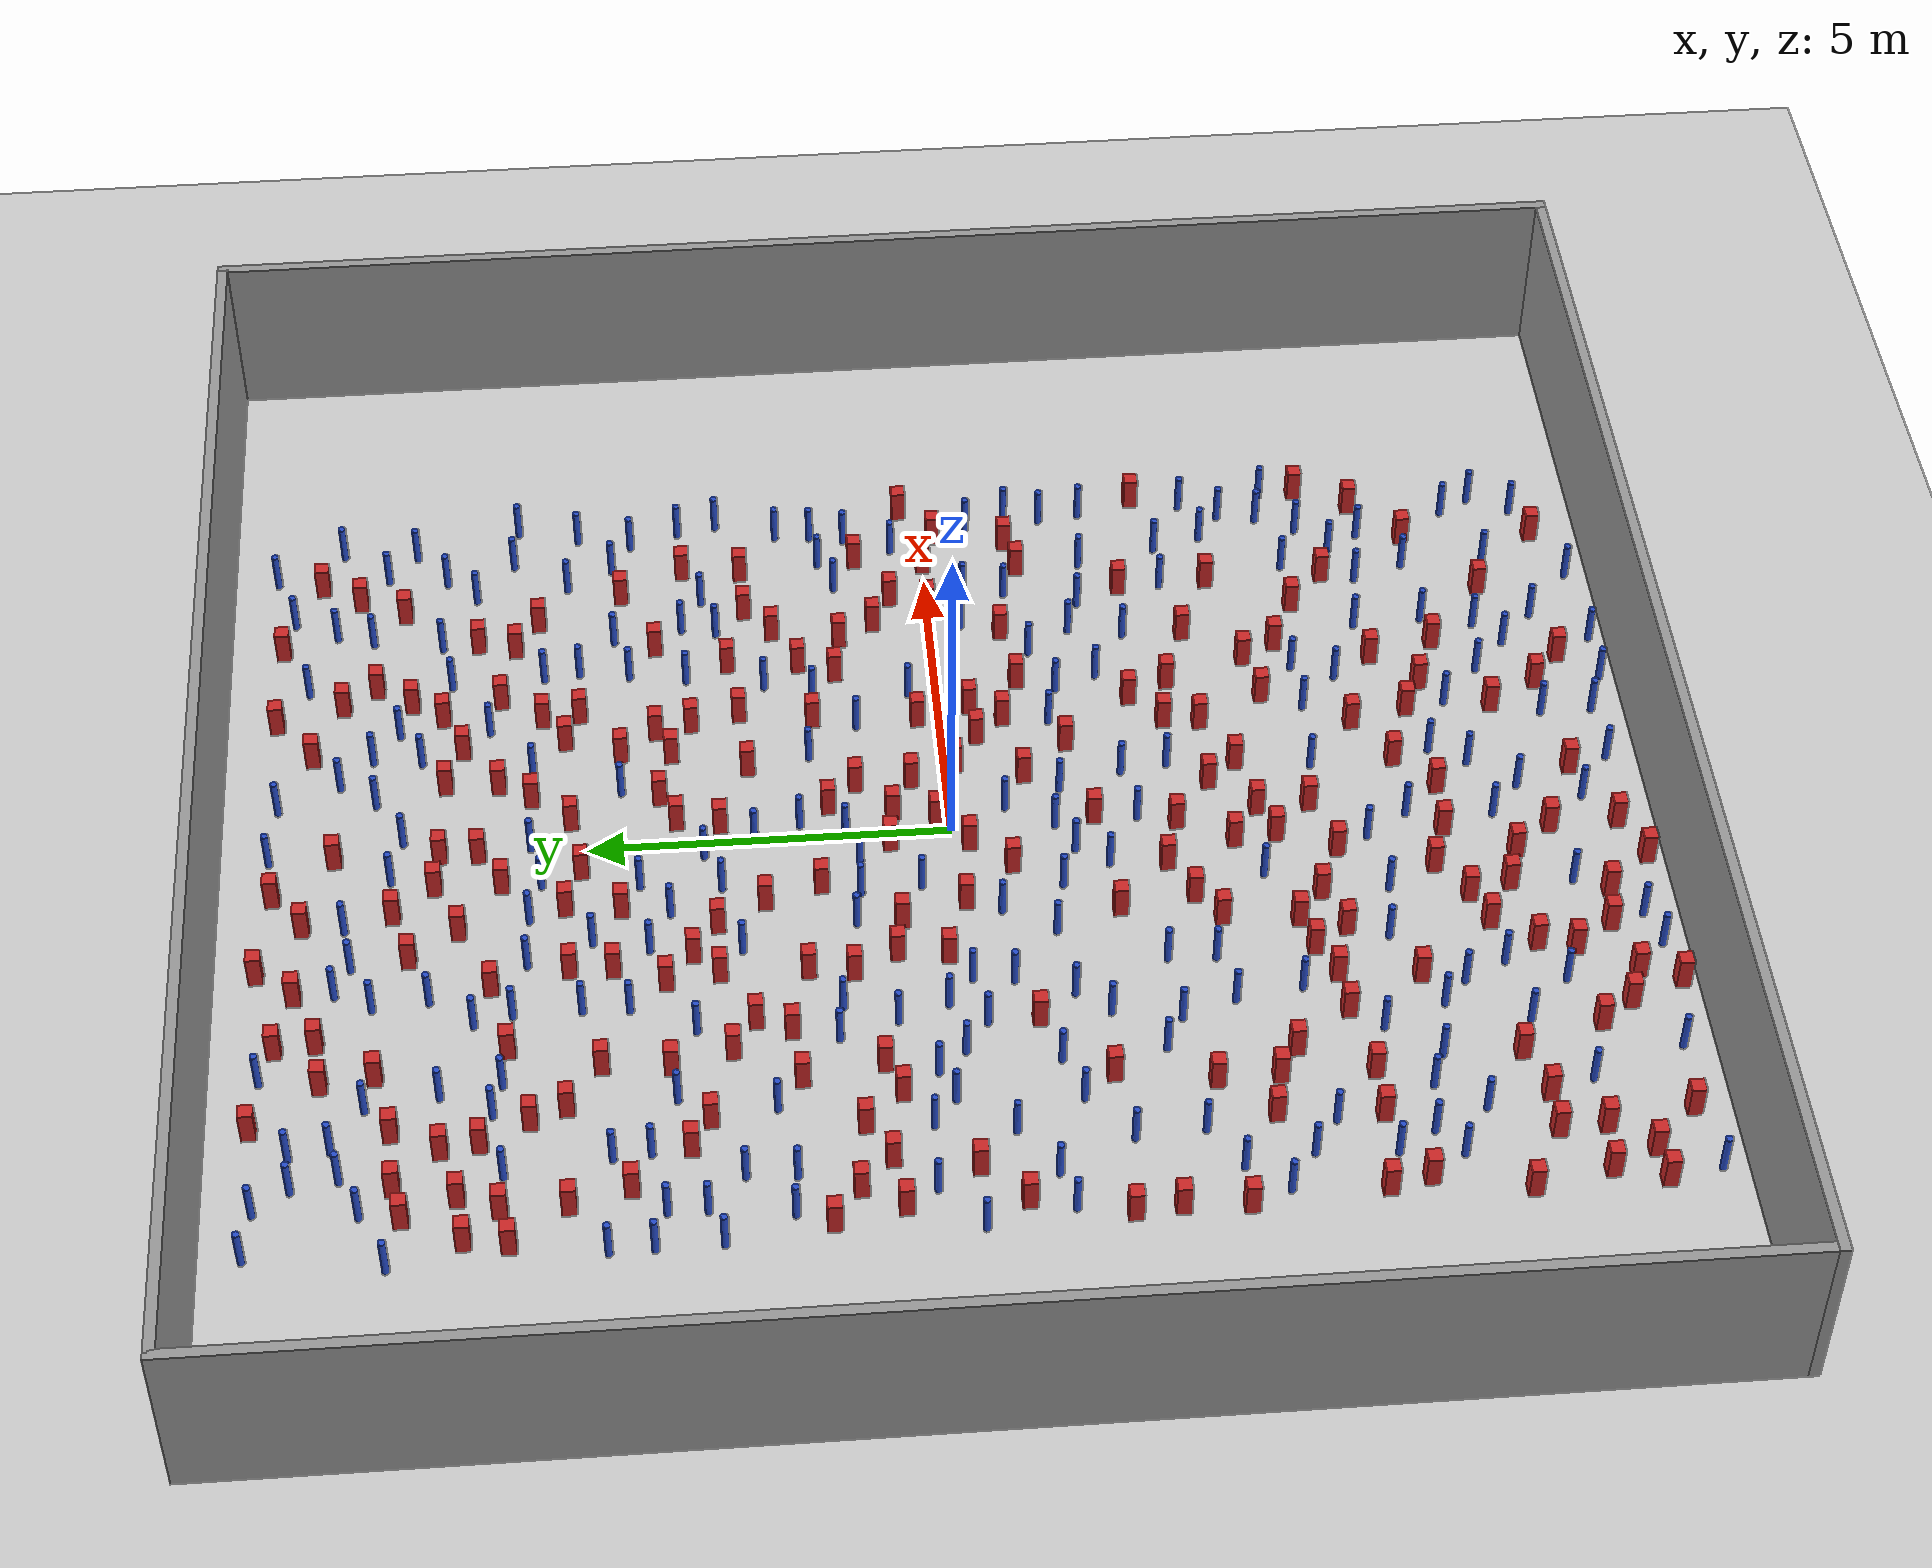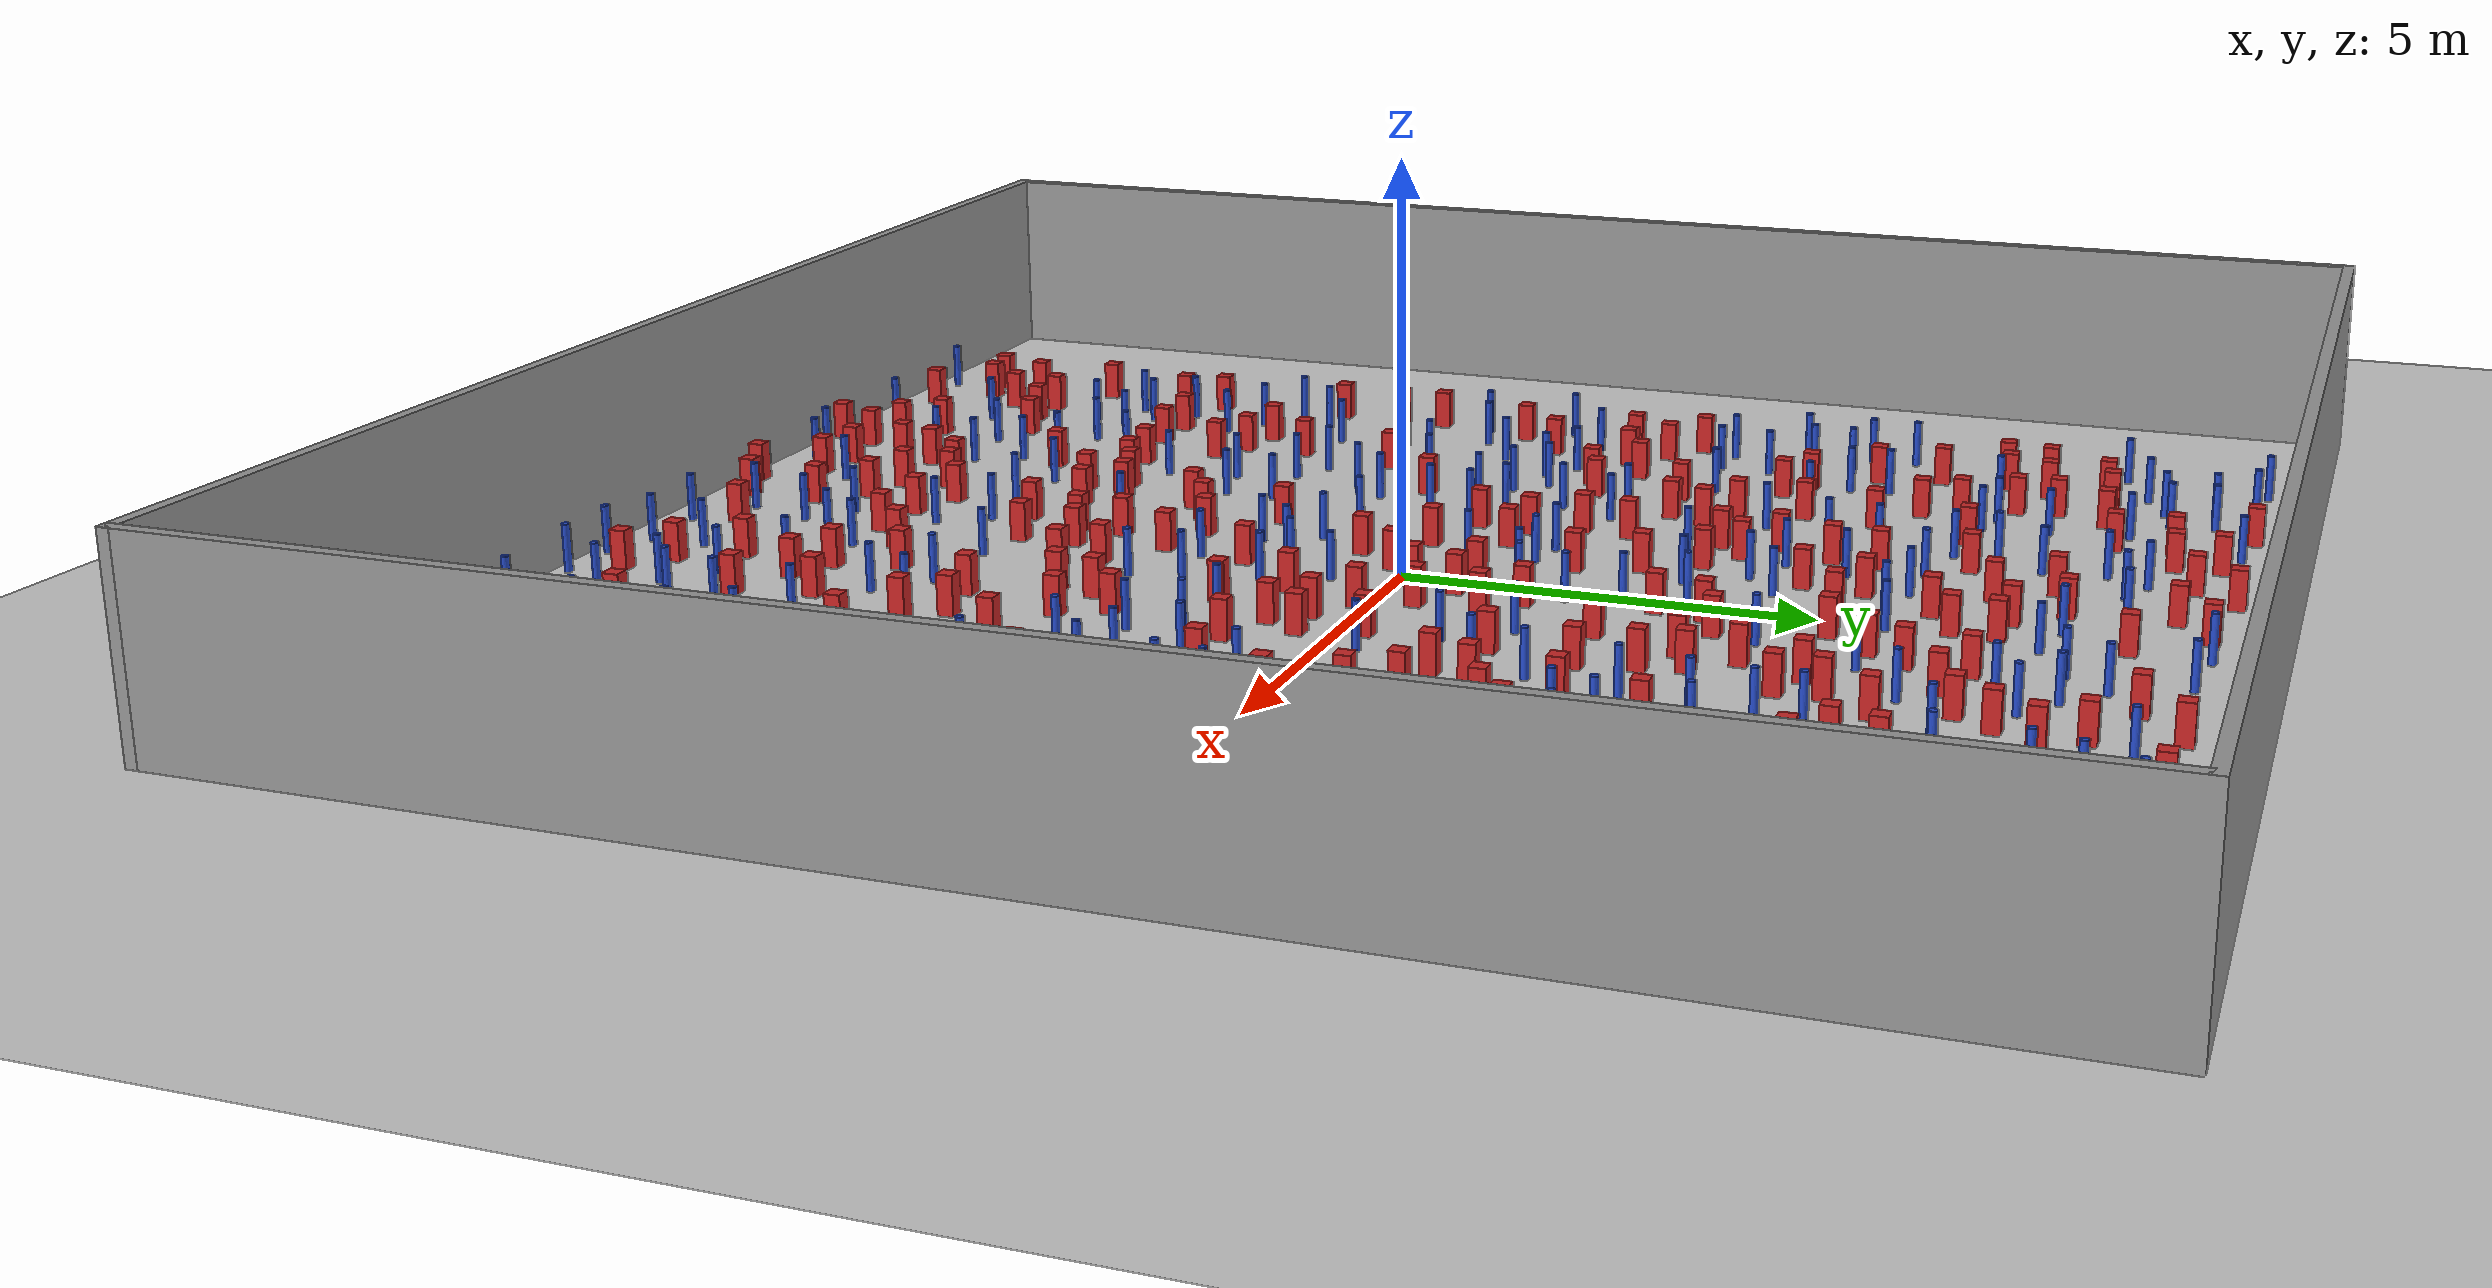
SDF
<sdf version="1.6">
 <world name="default">
  <light name="sun" type="directional">
   <pose>0 0 1000 0 -0 0</pose>
   <diffuse>0.8 0.8 0.8 1</diffuse>
   <specular>0.1 0.1 0.1 1</specular>
   <attenuation>
    <range>1000</range>
    <constant>0.9</constant>
    <linear>0.01</linear>
    <quadratic>0.001</quadratic>
   </attenuation>
   <direction>-0.5 0.5 -1</direction>
  </light>
  <model name="ground_plane">
   <static>1</static>
   <link name="link">
    <collision name="collision">
     <geometry><plane><normal>0 0 1</normal><size>100 100</size></plane></geometry>
     <surface><friction><ode><mu>100</mu><mu2>50</mu2></ode></friction></surface>
    </collision>
    <visual name="visual">
     <cast_shadows>0</cast_shadows>
     <geometry><plane><normal>0 0 1</normal><size>100 100</size></plane></geometry>
     <material>
      <ambient>1.0 1.0 1.0 1.0</ambient>
      <diffuse>0.8 0.8 0.8 1.0</diffuse>
      <specular>0.01 0.01 0.01 1.000000</specular>
     </material>
    </visual>
   </link>
  </model>
  <gravity>0 0 -9.8</gravity>
  <magnetic_field>6e-06 2.3e-05 -4.2e-05</magnetic_field>
  <atmosphere type="adiabatic"/>
  <physics name="default_physics" default="0" type="ode">
   <max_step_size>0.001</max_step_size>
   <real_time_factor>1</real_time_factor>
   <real_time_update_rate>1000</real_time_update_rate>
  </physics>
  <scene><ambient>0.4 0.4 0.4 1</ambient><background>0.7 0.7 0.7 1</background><shadows>1</shadows></scene>
  <spherical_coordinates>
   <surface_model>EARTH_WGS84</surface_model>
   <latitude_deg>0</latitude_deg>
   <longitude_deg>0</longitude_deg>
   <elevation>0</elevation>
   <heading_deg>0</heading_deg>
  </spherical_coordinates>
  <plugin name="gazebo_occupancy_map" filename="libgazebo_2Dmap_plugin.so">
   <map_resolution>0.05</map_resolution>
   <map_topic>generated_map</map_topic>
   <map_height>0.01</map_height>
   <map_size_x>50</map_size_x>
   <map_size_y>50</map_size_y>
  </plugin>
  <model name="NamedLocations">
   <static>true</static>
   <link name="DefaultStart"><pose>8.5 0 0 0 0 3.14</pose></link>
  </model>
  <model name="20x20_walls">
   <pose>0.044518 0.176112 0 0 -0 0</pose>
   <link name="Wall_1">
    <collision name="Wall_1_Collision">
     <geometry><box><size>20 0.15 2.5</size></box></geometry>
     <pose>0 0 1.25 0 -0 0</pose>
    </collision>
    <visual name="Wall_1_Visual">
     <pose>0 0 1.25 0 -0 0</pose>
     <geometry><box><size>20 0.15 2.5</size></box></geometry>
     <material>
      <script><uri>file://media/materials/scripts/gazebo.material</uri><name>Gazebo/Grey</name></script>
      <ambient>0.976471 0.992157 1 1</ambient>
     </material>
     <meta><layer>0</layer></meta>
    </visual>
    <pose>0 9.925 0 0 -0 0</pose>
   </link>
   <link name="Wall_3">
    <collision name="Wall_3_Collision">
     <geometry><box><size>20 0.15 2.5</size></box></geometry>
     <pose>0 0 1.25 0 -0 0</pose>
    </collision>
    <visual name="Wall_3_Visual">
     <pose>0 0 1.25 0 -0 0</pose>
     <geometry><box><size>20 0.15 2.5</size></box></geometry>
     <material>
      <script><uri>file://media/materials/scripts/gazebo.material</uri><name>Gazebo/Grey</name></script>
      <ambient>0.976471 0.992157 1 1</ambient>
     </material>
     <meta><layer>0</layer></meta>
    </visual>
    <pose>9.925 0 0 0 0 -1.5708</pose>
   </link>
   <link name="Wall_4">
    <collision name="Wall_4_Collision">
     <geometry><box><size>20 0.15 2.5</size></box></geometry>
     <pose>0 0 1.25 0 -0 0</pose>
    </collision>
    <visual name="Wall_4_Visual">
     <pose>0 0 1.25 0 -0 0</pose>
     <geometry><box><size>20 0.15 2.5</size></box></geometry>
     <material>
      <script><uri>file://media/materials/scripts/gazebo.material</uri><name>Gazebo/Grey</name></script>
      <ambient>0.976471 0.992157 1 1</ambient>
     </material>
     <meta><layer>0</layer></meta>
    </visual>
    <pose>0 -9.925 0 0 -0 3.14159</pose>
   </link>
   <link name="Wall_5">
    <collision name="Wall_5_Collision">
     <geometry><box><size>20 0.15 2.5</size></box></geometry>
     <pose>0 0 1.25 0 -0 0</pose>
    </collision>
    <visual name="Wall_5_Visual">
     <pose>0 0 1.25 0 -0 0</pose>
     <geometry><box><size>20 0.15 2.5</size></box></geometry>
     <material>
      <script><uri>file://media/materials/scripts/gazebo.material</uri><name>Gazebo/Grey</name></script>
      <ambient>0.976471 0.992157 1 1</ambient>
     </material>
     <meta><layer>0</layer></meta>
    </visual>
    <pose>-9.925 0 0 0 -0 1.5708</pose>
   </link>
   <static>1</static>
  </model>
  <model name="square_post_obstacle0">
   <static>true</static>
   <pose>5.15000023231 -1.34860133683 8.22691968438e-08 7.2212513382e-06 -7.54495500217e-07 2.29674213826e-05</pose>
   <link name="link">
    <pose>0 0 0.25 0 -0 0</pose>
    <inertial>
     <mass>100</mass>
     <inertia>
      <ixx>0.166667</ixx>
      <ixy>0</ixy>
      <ixz>0</ixz>
      <iyy>0.166667</iyy>
      <iyz>0</iyz>
      <izz>0.166667</izz>
     </inertia>
    </inertial>
    <collision name="collision"><geometry><box><size>.2 .2 .5</size></box></geometry></collision>
    <visual name="visual">
     <geometry><box><size>.2 .2 .5</size></box></geometry>
     <material>
      <script><name>Gazebo/Red</name><uri>file://media/materials/scripts/gazebo.material</uri></script>
     </material>
    </visual>
   </link>
  </model>
  <model name="square_post_obstacle1">
   <static>true</static>
   <pose>-0.453225772 -4.42769703456 8.22691968438e-08 7.22125133819e-06 -7.54495500217e-07 2.29674213826e-05</pose>
   <link name="link">
    <pose>0 0 0.25 0 -0 0</pose>
    <inertial>
     <mass>100</mass>
     <inertia>
      <ixx>0.166667</ixx>
      <ixy>0</ixy>
      <ixz>0</ixz>
      <iyy>0.166667</iyy>
      <iyz>0</iyz>
      <izz>0.166667</izz>
     </inertia>
    </inertial>
    <collision name="collision"><geometry><box><size>.2 .2 .5</size></box></geometry></collision>
    <visual name="visual">
     <geometry><box><size>.2 .2 .5</size></box></geometry>
     <material>
      <script><name>Gazebo/Red</name><uri>file://media/materials/scripts/gazebo.material</uri></script>
     </material>
    </visual>
   </link>
  </model>
  <model name="pole_obstacle0">
   <static>true</static>
   <pose>6.25939533136 -2.37629695557 2.88873142074e-08 -9.90536690245e-09 4.6021994898e-07 -1.20965994966e-07</pose>
   <link name="link">
    <pose>0 0 0.3 0 -0 0</pose>
    <inertial>
     <mass>1</mass>
     <inertia><ixx>0.145833</ixx><ixy>0</ixy><ixz>0</ixz><iyy>0.145833</iyy><iyz>0</iyz><izz>0.125</izz></inertia>
    </inertial>
    <collision name="collision">
     <geometry><cylinder><radius>0.05</radius><length>.6</length></cylinder></geometry>
    </collision>
    <visual name="visual">
     <geometry><cylinder><radius>0.05</radius><length>.6</length></cylinder></geometry>
     <material>
      <script><name>Gazebo/Blue</name><uri>file://media/materials/scripts/gazebo.material</uri></script>
     </material>
    </visual>
   </link>
  </model>
  <model name="square_post_obstacle2">
   <static>true</static>
   <pose>1.98796259758 8.79304583945 8.22691968438e-08 7.22125133819e-06 -7.54495500217e-07 2.29674213826e-05</pose>
   <link name="link">
    <pose>0 0 0.25 0 -0 0</pose>
    <inertial>
     <mass>100</mass>
     <inertia>
      <ixx>0.166667</ixx>
      <ixy>0</ixy>
      <ixz>0</ixz>
      <iyy>0.166667</iyy>
      <iyz>0</iyz>
      <izz>0.166667</izz>
     </inertia>
    </inertial>
    <collision name="collision"><geometry><box><size>.2 .2 .5</size></box></geometry></collision>
    <visual name="visual">
     <geometry><box><size>.2 .2 .5</size></box></geometry>
     <material>
      <script><name>Gazebo/Red</name><uri>file://media/materials/scripts/gazebo.material</uri></script>
     </material>
    </visual>
   </link>
  </model>
  <model name="pole_obstacle1">
   <static>true</static>
   <pose>4.55269154058 -6.26826545625 2.88873142074e-08 -9.90536690842e-09 4.60219948965e-07 -1.20965994976e-07</pose>
   <link name="link">
    <pose>0 0 0.3 0 -0 0</pose>
    <inertial>
     <mass>1</mass>
     <inertia><ixx>0.145833</ixx><ixy>0</ixy><ixz>0</ixz><iyy>0.145833</iyy><iyz>0</iyz><izz>0.125</izz></inertia>
    </inertial>
    <collision name="collision">
     <geometry><cylinder><radius>0.05</radius><length>.6</length></cylinder></geometry>
    </collision>
    <visual name="visual">
     <geometry><cylinder><radius>0.05</radius><length>.6</length></cylinder></geometry>
     <material>
      <script><name>Gazebo/Blue</name><uri>file://media/materials/scripts/gazebo.material</uri></script>
     </material>
    </visual>
   </link>
  </model>
  <model name="square_post_obstacle3">
   <static>true</static>
   <pose>4.07398690278 -5.25743221496 8.22691968438e-08 7.2212513382e-06 -7.54495500217e-07 2.29674213826e-05</pose>
   <link name="link">
    <pose>0 0 0.25 0 -0 0</pose>
    <inertial>
     <mass>100</mass>
     <inertia>
      <ixx>0.166667</ixx>
      <ixy>0</ixy>
      <ixz>0</ixz>
      <iyy>0.166667</iyy>
      <iyz>0</iyz>
      <izz>0.166667</izz>
     </inertia>
    </inertial>
    <collision name="collision"><geometry><box><size>.2 .2 .5</size></box></geometry></collision>
    <visual name="visual">
     <geometry><box><size>.2 .2 .5</size></box></geometry>
     <material>
      <script><name>Gazebo/Red</name><uri>file://media/materials/scripts/gazebo.material</uri></script>
     </material>
    </visual>
   </link>
  </model>
  <model name="pole_obstacle2">
   <static>true</static>
   <pose>-0.739905669948 4.30533973566 2.88873142074e-08 -9.90536689661e-09 4.60219948993e-07 -1.20965994957e-07</pose>
   <link name="link">
    <pose>0 0 0.3 0 -0 0</pose>
    <inertial>
     <mass>1</mass>
     <inertia><ixx>0.145833</ixx><ixy>0</ixy><ixz>0</ixz><iyy>0.145833</iyy><iyz>0</iyz><izz>0.125</izz></inertia>
    </inertial>
    <collision name="collision">
     <geometry><cylinder><radius>0.05</radius><length>.6</length></cylinder></geometry>
    </collision>
    <visual name="visual">
     <geometry><cylinder><radius>0.05</radius><length>.6</length></cylinder></geometry>
     <material>
      <script><name>Gazebo/Blue</name><uri>file://media/materials/scripts/gazebo.material</uri></script>
     </material>
    </visual>
   </link>
  </model>
  <model name="pole_obstacle3">
   <static>true</static>
   <pose>-4.32424077748 0.510078708993 2.88873142074e-08 -9.90536689326e-09 4.60219949001e-07 -1.20965994954e-07</pose>
   <link name="link">
    <pose>0 0 0.3 0 -0 0</pose>
    <inertial>
     <mass>1</mass>
     <inertia><ixx>0.145833</ixx><ixy>0</ixy><ixz>0</ixz><iyy>0.145833</iyy><iyz>0</iyz><izz>0.125</izz></inertia>
    </inertial>
    <collision name="collision">
     <geometry><cylinder><radius>0.05</radius><length>.6</length></cylinder></geometry>
    </collision>
    <visual name="visual">
     <geometry><cylinder><radius>0.05</radius><length>.6</length></cylinder></geometry>
     <material>
      <script><name>Gazebo/Blue</name><uri>file://media/materials/scripts/gazebo.material</uri></script>
     </material>
    </visual>
   </link>
  </model>
  <model name="square_post_obstacle4">
   <static>true</static>
   <pose>4.64315620051 0.532933999139 8.22691968438e-08 7.2212513382e-06 -7.54495500217e-07 2.29674213826e-05</pose>
   <link name="link">
    <pose>0 0 0.25 0 -0 0</pose>
    <inertial>
     <mass>100</mass>
     <inertia>
      <ixx>0.166667</ixx>
      <ixy>0</ixy>
      <ixz>0</ixz>
      <iyy>0.166667</iyy>
      <iyz>0</iyz>
      <izz>0.166667</izz>
     </inertia>
    </inertial>
    <collision name="collision"><geometry><box><size>.2 .2 .5</size></box></geometry></collision>
    <visual name="visual">
     <geometry><box><size>.2 .2 .5</size></box></geometry>
     <material>
      <script><name>Gazebo/Red</name><uri>file://media/materials/scripts/gazebo.material</uri></script>
     </material>
    </visual>
   </link>
  </model>
  <model name="square_post_obstacle5">
   <static>true</static>
   <pose>-6.77804085161 -2.3862629534 8.22691968438e-08 7.2212513382e-06 -7.54495500217e-07 2.29674213826e-05</pose>
   <link name="link">
    <pose>0 0 0.25 0 -0 0</pose>
    <inertial>
     <mass>100</mass>
     <inertia>
      <ixx>0.166667</ixx>
      <ixy>0</ixy>
      <ixz>0</ixz>
      <iyy>0.166667</iyy>
      <iyz>0</iyz>
      <izz>0.166667</izz>
     </inertia>
    </inertial>
    <collision name="collision"><geometry><box><size>.2 .2 .5</size></box></geometry></collision>
    <visual name="visual">
     <geometry><box><size>.2 .2 .5</size></box></geometry>
     <material>
      <script><name>Gazebo/Red</name><uri>file://media/materials/scripts/gazebo.material</uri></script>
     </material>
    </visual>
   </link>
  </model>
  <model name="square_post_obstacle6">
   <static>true</static>
   <pose>-6.53302153086 -0.464855870581 8.22691968438e-08 7.2212513382e-06 -7.54495500217e-07 2.29674213826e-05</pose>
   <link name="link">
    <pose>0 0 0.25 0 -0 0</pose>
    <inertial>
     <mass>100</mass>
     <inertia>
      <ixx>0.166667</ixx>
      <ixy>0</ixy>
      <ixz>0</ixz>
      <iyy>0.166667</iyy>
      <iyz>0</iyz>
      <izz>0.166667</izz>
     </inertia>
    </inertial>
    <collision name="collision"><geometry><box><size>.2 .2 .5</size></box></geometry></collision>
    <visual name="visual">
     <geometry><box><size>.2 .2 .5</size></box></geometry>
     <material>
      <script><name>Gazebo/Red</name><uri>file://media/materials/scripts/gazebo.material</uri></script>
     </material>
    </visual>
   </link>
  </model>
  <model name="pole_obstacle4">
   <static>true</static>
   <pose>3.19134797535 3.53822865445 2.88873142074e-08 -9.90536690232e-09 4.6021994898e-07 -1.20965994968e-07</pose>
   <link name="link">
    <pose>0 0 0.3 0 -0 0</pose>
    <inertial>
     <mass>1</mass>
     <inertia><ixx>0.145833</ixx><ixy>0</ixy><ixz>0</ixz><iyy>0.145833</iyy><iyz>0</iyz><izz>0.125</izz></inertia>
    </inertial>
    <collision name="collision">
     <geometry><cylinder><radius>0.05</radius><length>.6</length></cylinder></geometry>
    </collision>
    <visual name="visual">
     <geometry><cylinder><radius>0.05</radius><length>.6</length></cylinder></geometry>
     <material>
      <script><name>Gazebo/Blue</name><uri>file://media/materials/scripts/gazebo.material</uri></script>
     </material>
    </visual>
   </link>
  </model>
  <model name="pole_obstacle5">
   <static>true</static>
   <pose>-1.98658447247 -1.26352869154 2.88873142074e-08 -9.90536690043e-09 4.60219948984e-07 -1.20965994963e-07</pose>
   <link name="link">
    <pose>0 0 0.3 0 -0 0</pose>
    <inertial>
     <mass>1</mass>
     <inertia><ixx>0.145833</ixx><ixy>0</ixy><ixz>0</ixz><iyy>0.145833</iyy><iyz>0</iyz><izz>0.125</izz></inertia>
    </inertial>
    <collision name="collision">
     <geometry><cylinder><radius>0.05</radius><length>.6</length></cylinder></geometry>
    </collision>
    <visual name="visual">
     <geometry><cylinder><radius>0.05</radius><length>.6</length></cylinder></geometry>
     <material>
      <script><name>Gazebo/Blue</name><uri>file://media/materials/scripts/gazebo.material</uri></script>
     </material>
    </visual>
   </link>
  </model>
  <model name="square_post_obstacle7">
   <static>true</static>
   <pose>-2.24618304108 4.6984372265 8.22691968438e-08 7.2212513382e-06 -7.54495500217e-07 2.29674213826e-05</pose>
   <link name="link">
    <pose>0 0 0.25 0 -0 0</pose>
    <inertial>
     <mass>100</mass>
     <inertia>
      <ixx>0.166667</ixx>
      <ixy>0</ixy>
      <ixz>0</ixz>
      <iyy>0.166667</iyy>
      <iyz>0</iyz>
      <izz>0.166667</izz>
     </inertia>
    </inertial>
    <collision name="collision"><geometry><box><size>.2 .2 .5</size></box></geometry></collision>
    <visual name="visual">
     <geometry><box><size>.2 .2 .5</size></box></geometry>
     <material>
      <script><name>Gazebo/Red</name><uri>file://media/materials/scripts/gazebo.material</uri></script>
     </material>
    </visual>
   </link>
  </model>
  <model name="square_post_obstacle8">
   <static>true</static>
   <pose>-3.52622838958 -0.882869343843 8.22691968438e-08 7.2212513382e-06 -7.54495500217e-07 2.29674213826e-05</pose>
   <link name="link">
    <pose>0 0 0.25 0 -0 0</pose>
    <inertial>
     <mass>100</mass>
     <inertia>
      <ixx>0.166667</ixx>
      <ixy>0</ixy>
      <ixz>0</ixz>
      <iyy>0.166667</iyy>
      <iyz>0</iyz>
      <izz>0.166667</izz>
     </inertia>
    </inertial>
    <collision name="collision"><geometry><box><size>.2 .2 .5</size></box></geometry></collision>
    <visual name="visual">
     <geometry><box><size>.2 .2 .5</size></box></geometry>
     <material>
      <script><name>Gazebo/Red</name><uri>file://media/materials/scripts/gazebo.material</uri></script>
     </material>
    </visual>
   </link>
  </model>
  <model name="pole_obstacle6">
   <static>true</static>
   <pose>-0.401653053069 7.68126445907 2.88873142074e-08 -9.90536689683e-09 4.60219948993e-07 -1.20965994957e-07</pose>
   <link name="link">
    <pose>0 0 0.3 0 -0 0</pose>
    <inertial>
     <mass>1</mass>
     <inertia><ixx>0.145833</ixx><ixy>0</ixy><ixz>0</ixz><iyy>0.145833</iyy><iyz>0</iyz><izz>0.125</izz></inertia>
    </inertial>
    <collision name="collision">
     <geometry><cylinder><radius>0.05</radius><length>.6</length></cylinder></geometry>
    </collision>
    <visual name="visual">
     <geometry><cylinder><radius>0.05</radius><length>.6</length></cylinder></geometry>
     <material>
      <script><name>Gazebo/Blue</name><uri>file://media/materials/scripts/gazebo.material</uri></script>
     </material>
    </visual>
   </link>
  </model>
  <model name="pole_obstacle7">
   <static>true</static>
   <pose>-4.22980877584 -1.10824775417 2.88873142074e-08 -9.90536689445e-09 4.60219948999e-07 -1.20965994956e-07</pose>
   <link name="link">
    <pose>0 0 0.3 0 -0 0</pose>
    <inertial>
     <mass>1</mass>
     <inertia><ixx>0.145833</ixx><ixy>0</ixy><ixz>0</ixz><iyy>0.145833</iyy><iyz>0</iyz><izz>0.125</izz></inertia>
    </inertial>
    <collision name="collision">
     <geometry><cylinder><radius>0.05</radius><length>.6</length></cylinder></geometry>
    </collision>
    <visual name="visual">
     <geometry><cylinder><radius>0.05</radius><length>.6</length></cylinder></geometry>
     <material>
      <script><name>Gazebo/Blue</name><uri>file://media/materials/scripts/gazebo.material</uri></script>
     </material>
    </visual>
   </link>
  </model>
  <model name="square_post_obstacle9">
   <static>true</static>
   <pose>0.956388180386 -4.03698732437 8.22691968438e-08 7.22125133819e-06 -7.54495500217e-07 2.29674213826e-05</pose>
   <link name="link">
    <pose>0 0 0.25 0 -0 0</pose>
    <inertial>
     <mass>100</mass>
     <inertia>
      <ixx>0.166667</ixx>
      <ixy>0</ixy>
      <ixz>0</ixz>
      <iyy>0.166667</iyy>
      <iyz>0</iyz>
      <izz>0.166667</izz>
     </inertia>
    </inertial>
    <collision name="collision"><geometry><box><size>.2 .2 .5</size></box></geometry></collision>
    <visual name="visual">
     <geometry><box><size>.2 .2 .5</size></box></geometry>
     <material>
      <script><name>Gazebo/Red</name><uri>file://media/materials/scripts/gazebo.material</uri></script>
     </material>
    </visual>
   </link>
  </model>
  <model name="square_post_obstacle10">
   <static>true</static>
   <pose>6.10000262031 -6.38535614664 8.22691968438e-08 7.22125133819e-06 -7.54495500217e-07 2.29674213826e-05</pose>
   <link name="link">
    <pose>0 0 0.25 0 -0 0</pose>
    <inertial>
     <mass>100</mass>
     <inertia>
      <ixx>0.166667</ixx>
      <ixy>0</ixy>
      <ixz>0</ixz>
      <iyy>0.166667</iyy>
      <iyz>0</iyz>
      <izz>0.166667</izz>
     </inertia>
    </inertial>
    <collision name="collision"><geometry><box><size>.2 .2 .5</size></box></geometry></collision>
    <visual name="visual">
     <geometry><box><size>.2 .2 .5</size></box></geometry>
     <material>
      <script><name>Gazebo/Red</name><uri>file://media/materials/scripts/gazebo.material</uri></script>
     </material>
    </visual>
   </link>
  </model>
  <model name="square_post_obstacle11">
   <static>true</static>
   <pose>0.0836850320657 -4.95521037136 8.22691968438e-08 7.2212513382e-06 -7.54495500217e-07 2.29674213826e-05</pose>
   <link name="link">
    <pose>0 0 0.25 0 -0 0</pose>
    <inertial>
     <mass>100</mass>
     <inertia>
      <ixx>0.166667</ixx>
      <ixy>0</ixy>
      <ixz>0</ixz>
      <iyy>0.166667</iyy>
      <iyz>0</iyz>
      <izz>0.166667</izz>
     </inertia>
    </inertial>
    <collision name="collision"><geometry><box><size>.2 .2 .5</size></box></geometry></collision>
    <visual name="visual">
     <geometry><box><size>.2 .2 .5</size></box></geometry>
     <material>
      <script><name>Gazebo/Red</name><uri>file://media/materials/scripts/gazebo.material</uri></script>
     </material>
    </visual>
   </link>
  </model>
  <model name="square_post_obstacle12">
   <static>true</static>
   <pose>4.12839357007 0.815747877024 8.22691968438e-08 7.2212513382e-06 -7.54495500217e-07 2.29674213826e-05</pose>
   <link name="link">
    <pose>0 0 0.25 0 -0 0</pose>
    <inertial>
     <mass>100</mass>
     <inertia>
      <ixx>0.166667</ixx>
      <ixy>0</ixy>
      <ixz>0</ixz>
      <iyy>0.166667</iyy>
      <iyz>0</iyz>
      <izz>0.166667</izz>
     </inertia>
    </inertial>
    <collision name="collision"><geometry><box><size>.2 .2 .5</size></box></geometry></collision>
    <visual name="visual">
     <geometry><box><size>.2 .2 .5</size></box></geometry>
     <material>
      <script><name>Gazebo/Red</name><uri>file://media/materials/scripts/gazebo.material</uri></script>
     </material>
    </visual>
   </link>
  </model>
  <model name="square_post_obstacle13">
   <static>true</static>
   <pose>5.29659677529 -8.98105700362 8.22691968438e-08 7.22125133819e-06 -7.54495500217e-07 2.29674213826e-05</pose>
   <link name="link">
    <pose>0 0 0.25 0 -0 0</pose>
    <inertial>
     <mass>100</mass>
     <inertia>
      <ixx>0.166667</ixx>
      <ixy>0</ixy>
      <ixz>0</ixz>
      <iyy>0.166667</iyy>
      <iyz>0</iyz>
      <izz>0.166667</izz>
     </inertia>
    </inertial>
    <collision name="collision"><geometry><box><size>.2 .2 .5</size></box></geometry></collision>
    <visual name="visual">
     <geometry><box><size>.2 .2 .5</size></box></geometry>
     <material>
      <script><name>Gazebo/Red</name><uri>file://media/materials/scripts/gazebo.material</uri></script>
     </material>
    </visual>
   </link>
  </model>
  <model name="pole_obstacle8">
   <static>true</static>
   <pose>5.4938373227 -6.43313451027 2.88873142074e-08 -9.90536690842e-09 4.60219948965e-07 -1.20965994976e-07</pose>
   <link name="link">
    <pose>0 0 0.3 0 -0 0</pose>
    <inertial>
     <mass>1</mass>
     <inertia><ixx>0.145833</ixx><ixy>0</ixy><ixz>0</ixz><iyy>0.145833</iyy><iyz>0</iyz><izz>0.125</izz></inertia>
    </inertial>
    <collision name="collision">
     <geometry><cylinder><radius>0.05</radius><length>.6</length></cylinder></geometry>
    </collision>
    <visual name="visual">
     <geometry><cylinder><radius>0.05</radius><length>.6</length></cylinder></geometry>
     <material>
      <script><name>Gazebo/Blue</name><uri>file://media/materials/scripts/gazebo.material</uri></script>
     </material>
    </visual>
   </link>
  </model>
  <model name="square_post_obstacle14">
   <static>true</static>
   <pose>-5.36833786848 3.77041327687 8.22691968438e-08 7.2212513382e-06 -7.54495500217e-07 2.29674213826e-05</pose>
   <link name="link">
    <pose>0 0 0.25 0 -0 0</pose>
    <inertial>
     <mass>100</mass>
     <inertia>
      <ixx>0.166667</ixx>
      <ixy>0</ixy>
      <ixz>0</ixz>
      <iyy>0.166667</iyy>
      <iyz>0</iyz>
      <izz>0.166667</izz>
     </inertia>
    </inertial>
    <collision name="collision"><geometry><box><size>.2 .2 .5</size></box></geometry></collision>
    <visual name="visual">
     <geometry><box><size>.2 .2 .5</size></box></geometry>
     <material>
      <script><name>Gazebo/Red</name><uri>file://media/materials/scripts/gazebo.material</uri></script>
     </material>
    </visual>
   </link>
  </model>
  <model name="square_post_obstacle15">
   <static>true</static>
   <pose>-2.44196828047 -8.70239548351 8.22691968438e-08 7.22125133819e-06 -7.54495500217e-07 2.29674213826e-05</pose>
   <link name="link">
    <pose>0 0 0.25 0 -0 0</pose>
    <inertial>
     <mass>100</mass>
     <inertia>
      <ixx>0.166667</ixx>
      <ixy>0</ixy>
      <ixz>0</ixz>
      <iyy>0.166667</iyy>
      <iyz>0</iyz>
      <izz>0.166667</izz>
     </inertia>
    </inertial>
    <collision name="collision"><geometry><box><size>.2 .2 .5</size></box></geometry></collision>
    <visual name="visual">
     <geometry><box><size>.2 .2 .5</size></box></geometry>
     <material>
      <script><name>Gazebo/Red</name><uri>file://media/materials/scripts/gazebo.material</uri></script>
     </material>
    </visual>
   </link>
  </model>
  <model name="square_post_obstacle16">
   <static>true</static>
   <pose>2.9685054038 8.38365532075 8.22691968438e-08 7.22125133819e-06 -7.54495500217e-07 2.29674213826e-05</pose>
   <link name="link">
    <pose>0 0 0.25 0 -0 0</pose>
    <inertial>
     <mass>100</mass>
     <inertia>
      <ixx>0.166667</ixx>
      <ixy>0</ixy>
      <ixz>0</ixz>
      <iyy>0.166667</iyy>
      <iyz>0</iyz>
      <izz>0.166667</izz>
     </inertia>
    </inertial>
    <collision name="collision"><geometry><box><size>.2 .2 .5</size></box></geometry></collision>
    <visual name="visual">
     <geometry><box><size>.2 .2 .5</size></box></geometry>
     <material>
      <script><name>Gazebo/Red</name><uri>file://media/materials/scripts/gazebo.material</uri></script>
     </material>
    </visual>
   </link>
  </model>
  <model name="pole_obstacle9">
   <static>true</static>
   <pose>-6.37685946599 3.59660607227 2.88873142074e-08 -9.90536690245e-09 4.6021994898e-07 -1.20965994966e-07</pose>
   <link name="link">
    <pose>0 0 0.3 0 -0 0</pose>
    <inertial>
     <mass>1</mass>
     <inertia><ixx>0.145833</ixx><ixy>0</ixy><ixz>0</ixz><iyy>0.145833</iyy><iyz>0</iyz><izz>0.125</izz></inertia>
    </inertial>
    <collision name="collision">
     <geometry><cylinder><radius>0.05</radius><length>.6</length></cylinder></geometry>
    </collision>
    <visual name="visual">
     <geometry><cylinder><radius>0.05</radius><length>.6</length></cylinder></geometry>
     <material>
      <script><name>Gazebo/Blue</name><uri>file://media/materials/scripts/gazebo.material</uri></script>
     </material>
    </visual>
   </link>
  </model>
  <model name="square_post_obstacle17">
   <static>true</static>
   <pose>4.66868153729 -4.08071297045 8.22691968438e-08 7.2212513382e-06 -7.54495500217e-07 2.29674213826e-05</pose>
   <link name="link">
    <pose>0 0 0.25 0 -0 0</pose>
    <inertial>
     <mass>100</mass>
     <inertia>
      <ixx>0.166667</ixx>
      <ixy>0</ixy>
      <ixz>0</ixz>
      <iyy>0.166667</iyy>
      <iyz>0</iyz>
      <izz>0.166667</izz>
     </inertia>
    </inertial>
    <collision name="collision"><geometry><box><size>.2 .2 .5</size></box></geometry></collision>
    <visual name="visual">
     <geometry><box><size>.2 .2 .5</size></box></geometry>
     <material>
      <script><name>Gazebo/Red</name><uri>file://media/materials/scripts/gazebo.material</uri></script>
     </material>
    </visual>
   </link>
  </model>
  <model name="square_post_obstacle18">
   <static>true</static>
   <pose>-3.78768500839 3.16812446144 8.22691968438e-08 7.2212513382e-06 -7.54495500217e-07 2.29674213826e-05</pose>
   <link name="link">
    <pose>0 0 0.25 0 -0 0</pose>
    <inertial>
     <mass>100</mass>
     <inertia>
      <ixx>0.166667</ixx>
      <ixy>0</ixy>
      <ixz>0</ixz>
      <iyy>0.166667</iyy>
      <iyz>0</iyz>
      <izz>0.166667</izz>
     </inertia>
    </inertial>
    <collision name="collision"><geometry><box><size>.2 .2 .5</size></box></geometry></collision>
    <visual name="visual">
     <geometry><box><size>.2 .2 .5</size></box></geometry>
     <material>
      <script><name>Gazebo/Red</name><uri>file://media/materials/scripts/gazebo.material</uri></script>
     </material>
    </visual>
   </link>
  </model>
  <model name="pole_obstacle10">
   <static>true</static>
   <pose>5.6658567567 -5.5417444176 2.88873142074e-08 -9.90536690842e-09 4.60219948965e-07 -1.20965994976e-07</pose>
   <link name="link">
    <pose>0 0 0.3 0 -0 0</pose>
    <inertial>
     <mass>1</mass>
     <inertia><ixx>0.145833</ixx><ixy>0</ixy><ixz>0</ixz><iyy>0.145833</iyy><iyz>0</iyz><izz>0.125</izz></inertia>
    </inertial>
    <collision name="collision">
     <geometry><cylinder><radius>0.05</radius><length>.6</length></cylinder></geometry>
    </collision>
    <visual name="visual">
     <geometry><cylinder><radius>0.05</radius><length>.6</length></cylinder></geometry>
     <material>
      <script><name>Gazebo/Blue</name><uri>file://media/materials/scripts/gazebo.material</uri></script>
     </material>
    </visual>
   </link>
  </model>
  <model name="square_post_obstacle19">
   <static>true</static>
   <pose>-5.95324830502 0.11455333152 8.22691968438e-08 7.2212513382e-06 -7.54495500217e-07 2.29674213826e-05</pose>
   <link name="link">
    <pose>0 0 0.25 0 -0 0</pose>
    <inertial>
     <mass>100</mass>
     <inertia>
      <ixx>0.166667</ixx>
      <ixy>0</ixy>
      <ixz>0</ixz>
      <iyy>0.166667</iyy>
      <iyz>0</iyz>
      <izz>0.166667</izz>
     </inertia>
    </inertial>
    <collision name="collision"><geometry><box><size>.2 .2 .5</size></box></geometry></collision>
    <visual name="visual">
     <geometry><box><size>.2 .2 .5</size></box></geometry>
     <material>
      <script><name>Gazebo/Red</name><uri>file://media/materials/scripts/gazebo.material</uri></script>
     </material>
    </visual>
   </link>
  </model>
  <model name="pole_obstacle11">
   <static>true</static>
   <pose>-6.60695953444 -3.79870451077 2.88873142074e-08 -9.90536690245e-09 4.6021994898e-07 -1.20965994966e-07</pose>
   <link name="link">
    <pose>0 0 0.3 0 -0 0</pose>
    <inertial>
     <mass>1</mass>
     <inertia><ixx>0.145833</ixx><ixy>0</ixy><ixz>0</ixz><iyy>0.145833</iyy><iyz>0</iyz><izz>0.125</izz></inertia>
    </inertial>
    <collision name="collision">
     <geometry><cylinder><radius>0.05</radius><length>.6</length></cylinder></geometry>
    </collision>
    <visual name="visual">
     <geometry><cylinder><radius>0.05</radius><length>.6</length></cylinder></geometry>
     <material>
      <script><name>Gazebo/Blue</name><uri>file://media/materials/scripts/gazebo.material</uri></script>
     </material>
    </visual>
   </link>
  </model>
  <model name="square_post_obstacle20">
   <static>true</static>
   <pose>2.62762132053 -3.26762497386 8.22691968438e-08 7.2212513382e-06 -7.54495500217e-07 2.29674213826e-05</pose>
   <link name="link">
    <pose>0 0 0.25 0 -0 0</pose>
    <inertial>
     <mass>100</mass>
     <inertia>
      <ixx>0.166667</ixx>
      <ixy>0</ixy>
      <ixz>0</ixz>
      <iyy>0.166667</iyy>
      <iyz>0</iyz>
      <izz>0.166667</izz>
     </inertia>
    </inertial>
    <collision name="collision"><geometry><box><size>.2 .2 .5</size></box></geometry></collision>
    <visual name="visual">
     <geometry><box><size>.2 .2 .5</size></box></geometry>
     <material>
      <script><name>Gazebo/Red</name><uri>file://media/materials/scripts/gazebo.material</uri></script>
     </material>
    </visual>
   </link>
  </model>
  <model name="pole_obstacle12">
   <static>true</static>
   <pose>5.22611355301 5.19054820022 2.88873142074e-08 -9.90536690842e-09 4.60219948965e-07 -1.20965994976e-07</pose>
   <link name="link">
    <pose>0 0 0.3 0 -0 0</pose>
    <inertial>
     <mass>1</mass>
     <inertia><ixx>0.145833</ixx><ixy>0</ixy><ixz>0</ixz><iyy>0.145833</iyy><iyz>0</iyz><izz>0.125</izz></inertia>
    </inertial>
    <collision name="collision">
     <geometry><cylinder><radius>0.05</radius><length>.6</length></cylinder></geometry>
    </collision>
    <visual name="visual">
     <geometry><cylinder><radius>0.05</radius><length>.6</length></cylinder></geometry>
     <material>
      <script><name>Gazebo/Blue</name><uri>file://media/materials/scripts/gazebo.material</uri></script>
     </material>
    </visual>
   </link>
  </model>
  <model name="square_post_obstacle21">
   <static>true</static>
   <pose>0.0648391307138 -4.22650328789 8.22691968438e-08 7.22125133819e-06 -7.54495500217e-07 2.29674213826e-05</pose>
   <link name="link">
    <pose>0 0 0.25 0 -0 0</pose>
    <inertial>
     <mass>100</mass>
     <inertia>
      <ixx>0.166667</ixx>
      <ixy>0</ixy>
      <ixz>0</ixz>
      <iyy>0.166667</iyy>
      <iyz>0</iyz>
      <izz>0.166667</izz>
     </inertia>
    </inertial>
    <collision name="collision"><geometry><box><size>.2 .2 .5</size></box></geometry></collision>
    <visual name="visual">
     <geometry><box><size>.2 .2 .5</size></box></geometry>
     <material>
      <script><name>Gazebo/Red</name><uri>file://media/materials/scripts/gazebo.material</uri></script>
     </material>
    </visual>
   </link>
  </model>
  <model name="pole_obstacle13">
   <static>true</static>
   <pose>-3.47232369091 -1.83874024077 2.88873142074e-08 -9.90536691123e-09 4.60219948959e-07 -1.20965994982e-07</pose>
   <link name="link">
    <pose>0 0 0.3 0 -0 0</pose>
    <inertial>
     <mass>1</mass>
     <inertia><ixx>0.145833</ixx><ixy>0</ixy><ixz>0</ixz><iyy>0.145833</iyy><iyz>0</iyz><izz>0.125</izz></inertia>
    </inertial>
    <collision name="collision">
     <geometry><cylinder><radius>0.05</radius><length>.6</length></cylinder></geometry>
    </collision>
    <visual name="visual">
     <geometry><cylinder><radius>0.05</radius><length>.6</length></cylinder></geometry>
     <material>
      <script><name>Gazebo/Blue</name><uri>file://media/materials/scripts/gazebo.material</uri></script>
     </material>
    </visual>
   </link>
  </model>
  <model name="square_post_obstacle22">
   <static>true</static>
   <pose>0.930814888783 -1.07541116986 8.22691968438e-08 7.2212513382e-06 -7.54495500217e-07 2.29674213826e-05</pose>
   <link name="link">
    <pose>0 0 0.25 0 -0 0</pose>
    <inertial>
     <mass>100</mass>
     <inertia>
      <ixx>0.166667</ixx>
      <ixy>0</ixy>
      <ixz>0</ixz>
      <iyy>0.166667</iyy>
      <iyz>0</iyz>
      <izz>0.166667</izz>
     </inertia>
    </inertial>
    <collision name="collision"><geometry><box><size>.2 .2 .5</size></box></geometry></collision>
    <visual name="visual">
     <geometry><box><size>.2 .2 .5</size></box></geometry>
     <material>
      <script><name>Gazebo/Red</name><uri>file://media/materials/scripts/gazebo.material</uri></script>
     </material>
    </visual>
   </link>
  </model>
  <model name="pole_obstacle14">
   <static>true</static>
   <pose>4.80722969112 -8.19572813081 2.88873142074e-08 -9.9053668967e-09 4.60219948993e-07 -1.20965994957e-07</pose>
   <link name="link">
    <pose>0 0 0.3 0 -0 0</pose>
    <inertial>
     <mass>1</mass>
     <inertia><ixx>0.145833</ixx><ixy>0</ixy><ixz>0</ixz><iyy>0.145833</iyy><iyz>0</iyz><izz>0.125</izz></inertia>
    </inertial>
    <collision name="collision">
     <geometry><cylinder><radius>0.05</radius><length>.6</length></cylinder></geometry>
    </collision>
    <visual name="visual">
     <geometry><cylinder><radius>0.05</radius><length>.6</length></cylinder></geometry>
     <material>
      <script><name>Gazebo/Blue</name><uri>file://media/materials/scripts/gazebo.material</uri></script>
     </material>
    </visual>
   </link>
  </model>
  <model name="pole_obstacle15">
   <static>true</static>
   <pose>-3.65093043293 1.76417876774 2.88873142074e-08 -9.90536689395e-09 4.60219949e-07 -1.20965994953e-07</pose>
   <link name="link">
    <pose>0 0 0.3 0 -0 0</pose>
    <inertial>
     <mass>1</mass>
     <inertia><ixx>0.145833</ixx><ixy>0</ixy><ixz>0</ixz><iyy>0.145833</iyy><iyz>0</iyz><izz>0.125</izz></inertia>
    </inertial>
    <collision name="collision">
     <geometry><cylinder><radius>0.05</radius><length>.6</length></cylinder></geometry>
    </collision>
    <visual name="visual">
     <geometry><cylinder><radius>0.05</radius><length>.6</length></cylinder></geometry>
     <material>
      <script><name>Gazebo/Blue</name><uri>file://media/materials/scripts/gazebo.material</uri></script>
     </material>
    </visual>
   </link>
  </model>
  <model name="pole_obstacle16">
   <static>true</static>
   <pose>-0.0267076855283 -1.42289226915 2.88873142074e-08 -9.90536690152e-09 4.60219948982e-07 -1.20965994964e-07</pose>
   <link name="link">
    <pose>0 0 0.3 0 -0 0</pose>
    <inertial>
     <mass>1</mass>
     <inertia><ixx>0.145833</ixx><ixy>0</ixy><ixz>0</ixz><iyy>0.145833</iyy><iyz>0</iyz><izz>0.125</izz></inertia>
    </inertial>
    <collision name="collision">
     <geometry><cylinder><radius>0.05</radius><length>.6</length></cylinder></geometry>
    </collision>
    <visual name="visual">
     <geometry><cylinder><radius>0.05</radius><length>.6</length></cylinder></geometry>
     <material>
      <script><name>Gazebo/Blue</name><uri>file://media/materials/scripts/gazebo.material</uri></script>
     </material>
    </visual>
   </link>
  </model>
  <model name="square_post_obstacle23">
   <static>true</static>
   <pose>-2.53691966221 1.50098403107 8.22691968438e-08 7.2212513382e-06 -7.54495500217e-07 2.29674213826e-05</pose>
   <link name="link">
    <pose>0 0 0.25 0 -0 0</pose>
    <inertial>
     <mass>100</mass>
     <inertia>
      <ixx>0.166667</ixx>
      <ixy>0</ixy>
      <ixz>0</ixz>
      <iyy>0.166667</iyy>
      <iyz>0</iyz>
      <izz>0.166667</izz>
     </inertia>
    </inertial>
    <collision name="collision"><geometry><box><size>.2 .2 .5</size></box></geometry></collision>
    <visual name="visual">
     <geometry><box><size>.2 .2 .5</size></box></geometry>
     <material>
      <script><name>Gazebo/Red</name><uri>file://media/materials/scripts/gazebo.material</uri></script>
     </material>
    </visual>
   </link>
  </model>
  <model name="pole_obstacle17">
   <static>true</static>
   <pose>1.99570746869 -5.14558507064 2.88873142074e-08 -9.9053668918e-09 4.60219949005e-07 -1.20965994951e-07</pose>
   <link name="link">
    <pose>0 0 0.3 0 -0 0</pose>
    <inertial>
     <mass>1</mass>
     <inertia><ixx>0.145833</ixx><ixy>0</ixy><ixz>0</ixz><iyy>0.145833</iyy><iyz>0</iyz><izz>0.125</izz></inertia>
    </inertial>
    <collision name="collision">
     <geometry><cylinder><radius>0.05</radius><length>.6</length></cylinder></geometry>
    </collision>
    <visual name="visual">
     <geometry><cylinder><radius>0.05</radius><length>.6</length></cylinder></geometry>
     <material>
      <script><name>Gazebo/Blue</name><uri>file://media/materials/scripts/gazebo.material</uri></script>
     </material>
    </visual>
   </link>
  </model>
  <model name="square_post_obstacle24">
   <static>true</static>
   <pose>-2.24350808111 -5.14395207537 8.22691968438e-08 7.2212513382e-06 -7.54495500217e-07 2.29674213826e-05</pose>
   <link name="link">
    <pose>0 0 0.25 0 -0 0</pose>
    <inertial>
     <mass>100</mass>
     <inertia>
      <ixx>0.166667</ixx>
      <ixy>0</ixy>
      <ixz>0</ixz>
      <iyy>0.166667</iyy>
      <iyz>0</iyz>
      <izz>0.166667</izz>
     </inertia>
    </inertial>
    <collision name="collision"><geometry><box><size>.2 .2 .5</size></box></geometry></collision>
    <visual name="visual">
     <geometry><box><size>.2 .2 .5</size></box></geometry>
     <material>
      <script><name>Gazebo/Red</name><uri>file://media/materials/scripts/gazebo.material</uri></script>
     </material>
    </visual>
   </link>
  </model>
  <model name="square_post_obstacle25">
   <static>true</static>
   <pose>2.2391453653 1.79144749832 8.22691968438e-08 7.2212513382e-06 -7.54495500217e-07 2.29674213826e-05</pose>
   <link name="link">
    <pose>0 0 0.25 0 -0 0</pose>
    <inertial>
     <mass>100</mass>
     <inertia>
      <ixx>0.166667</ixx>
      <ixy>0</ixy>
      <ixz>0</ixz>
      <iyy>0.166667</iyy>
      <iyz>0</iyz>
      <izz>0.166667</izz>
     </inertia>
    </inertial>
    <collision name="collision"><geometry><box><size>.2 .2 .5</size></box></geometry></collision>
    <visual name="visual">
     <geometry><box><size>.2 .2 .5</size></box></geometry>
     <material>
      <script><name>Gazebo/Red</name><uri>file://media/materials/scripts/gazebo.material</uri></script>
     </material>
    </visual>
   </link>
  </model>
  <model name="square_post_obstacle26">
   <static>true</static>
   <pose>-1.99690841157 9.4471703377 8.22691968438e-08 7.22125133819e-06 -7.54495500217e-07 2.29674213826e-05</pose>
   <link name="link">
    <pose>0 0 0.25 0 -0 0</pose>
    <inertial>
     <mass>100</mass>
     <inertia>
      <ixx>0.166667</ixx>
      <ixy>0</ixy>
      <ixz>0</ixz>
      <iyy>0.166667</iyy>
      <iyz>0</iyz>
      <izz>0.166667</izz>
     </inertia>
    </inertial>
    <collision name="collision"><geometry><box><size>.2 .2 .5</size></box></geometry></collision>
    <visual name="visual">
     <geometry><box><size>.2 .2 .5</size></box></geometry>
     <material>
      <script><name>Gazebo/Red</name><uri>file://media/materials/scripts/gazebo.material</uri></script>
     </material>
    </visual>
   </link>
  </model>
  <model name="square_post_obstacle27">
   <static>true</static>
   <pose>-6.18605493413 6.22715426058 8.22691968438e-08 7.22125133819e-06 -7.54495500217e-07 2.29674213826e-05</pose>
   <link name="link">
    <pose>0 0 0.25 0 -0 0</pose>
    <inertial>
     <mass>100</mass>
     <inertia>
      <ixx>0.166667</ixx>
      <ixy>0</ixy>
      <ixz>0</ixz>
      <iyy>0.166667</iyy>
      <iyz>0</iyz>
      <izz>0.166667</izz>
     </inertia>
    </inertial>
    <collision name="collision"><geometry><box><size>.2 .2 .5</size></box></geometry></collision>
    <visual name="visual">
     <geometry><box><size>.2 .2 .5</size></box></geometry>
     <material>
      <script><name>Gazebo/Red</name><uri>file://media/materials/scripts/gazebo.material</uri></script>
     </material>
    </visual>
   </link>
  </model>
  <model name="pole_obstacle18">
   <static>true</static>
   <pose>4.90242069241 -5.23326689203 2.88873142074e-08 -9.90536690842e-09 4.60219948965e-07 -1.20965994976e-07</pose>
   <link name="link">
    <pose>0 0 0.3 0 -0 0</pose>
    <inertial>
     <mass>1</mass>
     <inertia><ixx>0.145833</ixx><ixy>0</ixy><ixz>0</ixz><iyy>0.145833</iyy><iyz>0</iyz><izz>0.125</izz></inertia>
    </inertial>
    <collision name="collision">
     <geometry><cylinder><radius>0.05</radius><length>.6</length></cylinder></geometry>
    </collision>
    <visual name="visual">
     <geometry><cylinder><radius>0.05</radius><length>.6</length></cylinder></geometry>
     <material>
      <script><name>Gazebo/Blue</name><uri>file://media/materials/scripts/gazebo.material</uri></script>
     </material>
    </visual>
   </link>
  </model>
  <model name="square_post_obstacle28">
   <static>true</static>
   <pose>-5.72116184644 7.58453631129 8.22691968438e-08 7.2212513382e-06 -7.54495500217e-07 2.29674213826e-05</pose>
   <link name="link">
    <pose>0 0 0.25 0 -0 0</pose>
    <inertial>
     <mass>100</mass>
     <inertia>
      <ixx>0.166667</ixx>
      <ixy>0</ixy>
      <ixz>0</ixz>
      <iyy>0.166667</iyy>
      <iyz>0</iyz>
      <izz>0.166667</izz>
     </inertia>
    </inertial>
    <collision name="collision"><geometry><box><size>.2 .2 .5</size></box></geometry></collision>
    <visual name="visual">
     <geometry><box><size>.2 .2 .5</size></box></geometry>
     <material>
      <script><name>Gazebo/Red</name><uri>file://media/materials/scripts/gazebo.material</uri></script>
     </material>
    </visual>
   </link>
  </model>
  <model name="pole_obstacle19">
   <static>true</static>
   <pose>-0.285638210329 -7.47282447171 2.88873142074e-08 -9.90536689618e-09 4.60219948994e-07 -1.20965994956e-07</pose>
   <link name="link">
    <pose>0 0 0.3 0 -0 0</pose>
    <inertial>
     <mass>1</mass>
     <inertia><ixx>0.145833</ixx><ixy>0</ixy><ixz>0</ixz><iyy>0.145833</iyy><iyz>0</iyz><izz>0.125</izz></inertia>
    </inertial>
    <collision name="collision">
     <geometry><cylinder><radius>0.05</radius><length>.6</length></cylinder></geometry>
    </collision>
    <visual name="visual">
     <geometry><cylinder><radius>0.05</radius><length>.6</length></cylinder></geometry>
     <material>
      <script><name>Gazebo/Blue</name><uri>file://media/materials/scripts/gazebo.material</uri></script>
     </material>
    </visual>
   </link>
  </model>
  <model name="square_post_obstacle29">
   <static>true</static>
   <pose>5.43219369134 3.52341071615 8.22691968438e-08 7.2212513382e-06 -7.54495500217e-07 2.29674213826e-05</pose>
   <link name="link">
    <pose>0 0 0.25 0 -0 0</pose>
    <inertial>
     <mass>100</mass>
     <inertia>
      <ixx>0.166667</ixx>
      <ixy>0</ixy>
      <ixz>0</ixz>
      <iyy>0.166667</iyy>
      <iyz>0</iyz>
      <izz>0.166667</izz>
     </inertia>
    </inertial>
    <collision name="collision"><geometry><box><size>.2 .2 .5</size></box></geometry></collision>
    <visual name="visual">
     <geometry><box><size>.2 .2 .5</size></box></geometry>
     <material>
      <script><name>Gazebo/Red</name><uri>file://media/materials/scripts/gazebo.material</uri></script>
     </material>
    </visual>
   </link>
  </model>
  <model name="square_post_obstacle30">
   <static>true</static>
   <pose>-1.41584440362 6.75614959326 8.22691968438e-08 7.2212513382e-06 -7.54495500217e-07 2.29674213826e-05</pose>
   <link name="link">
    <pose>0 0 0.25 0 -0 0</pose>
    <inertial>
     <mass>100</mass>
     <inertia>
      <ixx>0.166667</ixx>
      <ixy>0</ixy>
      <ixz>0</ixz>
      <iyy>0.166667</iyy>
      <iyz>0</iyz>
      <izz>0.166667</izz>
     </inertia>
    </inertial>
    <collision name="collision"><geometry><box><size>.2 .2 .5</size></box></geometry></collision>
    <visual name="visual">
     <geometry><box><size>.2 .2 .5</size></box></geometry>
     <material>
      <script><name>Gazebo/Red</name><uri>file://media/materials/scripts/gazebo.material</uri></script>
     </material>
    </visual>
   </link>
  </model>
  <model name="pole_obstacle20">
   <static>true</static>
   <pose>-6.12993700592 8.00740763405 2.88873142074e-08 -9.90536690354e-09 4.60219948977e-07 -1.20965994967e-07</pose>
   <link name="link">
    <pose>0 0 0.3 0 -0 0</pose>
    <inertial>
     <mass>1</mass>
     <inertia><ixx>0.145833</ixx><ixy>0</ixy><ixz>0</ixz><iyy>0.145833</iyy><iyz>0</iyz><izz>0.125</izz></inertia>
    </inertial>
    <collision name="collision">
     <geometry><cylinder><radius>0.05</radius><length>.6</length></cylinder></geometry>
    </collision>
    <visual name="visual">
     <geometry><cylinder><radius>0.05</radius><length>.6</length></cylinder></geometry>
     <material>
      <script><name>Gazebo/Blue</name><uri>file://media/materials/scripts/gazebo.material</uri></script>
     </material>
    </visual>
   </link>
  </model>
  <model name="pole_obstacle21">
   <static>true</static>
   <pose>6.05822907915 1.62308111221 2.88873142074e-08 -9.90536689445e-09 4.60219948999e-07 -1.20965994956e-07</pose>
   <link name="link">
    <pose>0 0 0.3 0 -0 0</pose>
    <inertial>
     <mass>1</mass>
     <inertia><ixx>0.145833</ixx><ixy>0</ixy><ixz>0</ixz><iyy>0.145833</iyy><iyz>0</iyz><izz>0.125</izz></inertia>
    </inertial>
    <collision name="collision">
     <geometry><cylinder><radius>0.05</radius><length>.6</length></cylinder></geometry>
    </collision>
    <visual name="visual">
     <geometry><cylinder><radius>0.05</radius><length>.6</length></cylinder></geometry>
     <material>
      <script><name>Gazebo/Blue</name><uri>file://media/materials/scripts/gazebo.material</uri></script>
     </material>
    </visual>
   </link>
  </model>
  <model name="square_post_obstacle31">
   <static>true</static>
   <pose>1.68851876333 3.79857637818 8.22691968438e-08 7.2212513382e-06 -7.54495500217e-07 2.29674213826e-05</pose>
   <link name="link">
    <pose>0 0 0.25 0 -0 0</pose>
    <inertial>
     <mass>100</mass>
     <inertia>
      <ixx>0.166667</ixx>
      <ixy>0</ixy>
      <ixz>0</ixz>
      <iyy>0.166667</iyy>
      <iyz>0</iyz>
      <izz>0.166667</izz>
     </inertia>
    </inertial>
    <collision name="collision"><geometry><box><size>.2 .2 .5</size></box></geometry></collision>
    <visual name="visual">
     <geometry><box><size>.2 .2 .5</size></box></geometry>
     <material>
      <script><name>Gazebo/Red</name><uri>file://media/materials/scripts/gazebo.material</uri></script>
     </material>
    </visual>
   </link>
  </model>
  <model name="pole_obstacle22">
   <static>true</static>
   <pose>0.72259887172 -7.28445306025 2.88873142074e-08 -9.90536689661e-09 4.60219948993e-07 -1.20965994957e-07</pose>
   <link name="link">
    <pose>0 0 0.3 0 -0 0</pose>
    <inertial>
     <mass>1</mass>
     <inertia><ixx>0.145833</ixx><ixy>0</ixy><ixz>0</ixz><iyy>0.145833</iyy><iyz>0</iyz><izz>0.125</izz></inertia>
    </inertial>
    <collision name="collision">
     <geometry><cylinder><radius>0.05</radius><length>.6</length></cylinder></geometry>
    </collision>
    <visual name="visual">
     <geometry><cylinder><radius>0.05</radius><length>.6</length></cylinder></geometry>
     <material>
      <script><name>Gazebo/Blue</name><uri>file://media/materials/scripts/gazebo.material</uri></script>
     </material>
    </visual>
   </link>
  </model>
  <model name="pole_obstacle23">
   <static>true</static>
   <pose>-5.55312142066 -2.83954073413 2.88873142074e-08 -9.90536690245e-09 4.6021994898e-07 -1.20965994966e-07</pose>
   <link name="link">
    <pose>0 0 0.3 0 -0 0</pose>
    <inertial>
     <mass>1</mass>
     <inertia><ixx>0.145833</ixx><ixy>0</ixy><ixz>0</ixz><iyy>0.145833</iyy><iyz>0</iyz><izz>0.125</izz></inertia>
    </inertial>
    <collision name="collision">
     <geometry><cylinder><radius>0.05</radius><length>.6</length></cylinder></geometry>
    </collision>
    <visual name="visual">
     <geometry><cylinder><radius>0.05</radius><length>.6</length></cylinder></geometry>
     <material>
      <script><name>Gazebo/Blue</name><uri>file://media/materials/scripts/gazebo.material</uri></script>
     </material>
    </visual>
   </link>
  </model>
  <model name="pole_obstacle24">
   <static>true</static>
   <pose>3.06327365985 -9.45333763616 2.88873142074e-08 -9.90536692318e-09 4.6021994893e-07 -1.20965994988e-07</pose>
   <link name="link">
    <pose>0 0 0.3 0 -0 0</pose>
    <inertial>
     <mass>1</mass>
     <inertia><ixx>0.145833</ixx><ixy>0</ixy><ixz>0</ixz><iyy>0.145833</iyy><iyz>0</iyz><izz>0.125</izz></inertia>
    </inertial>
    <collision name="collision">
     <geometry><cylinder><radius>0.05</radius><length>.6</length></cylinder></geometry>
    </collision>
    <visual name="visual">
     <geometry><cylinder><radius>0.05</radius><length>.6</length></cylinder></geometry>
     <material>
      <script><name>Gazebo/Blue</name><uri>file://media/materials/scripts/gazebo.material</uri></script>
     </material>
    </visual>
   </link>
  </model>
  <model name="pole_obstacle25">
   <static>true</static>
   <pose>-6.90949432621 0.115962901005 2.88873142074e-08 -9.90536689593e-09 4.60219948995e-07 -1.20965994958e-07</pose>
   <link name="link">
    <pose>0 0 0.3 0 -0 0</pose>
    <inertial>
     <mass>1</mass>
     <inertia><ixx>0.145833</ixx><ixy>0</ixy><ixz>0</ixz><iyy>0.145833</iyy><iyz>0</iyz><izz>0.125</izz></inertia>
    </inertial>
    <collision name="collision">
     <geometry><cylinder><radius>0.05</radius><length>.6</length></cylinder></geometry>
    </collision>
    <visual name="visual">
     <geometry><cylinder><radius>0.05</radius><length>.6</length></cylinder></geometry>
     <material>
      <script><name>Gazebo/Blue</name><uri>file://media/materials/scripts/gazebo.material</uri></script>
     </material>
    </visual>
   </link>
  </model>
  <model name="pole_obstacle26">
   <static>true</static>
   <pose>6.05952672036 7.37521620662 2.88873142074e-08 -9.90536690842e-09 4.60219948965e-07 -1.20965994976e-07</pose>
   <link name="link">
    <pose>0 0 0.3 0 -0 0</pose>
    <inertial>
     <mass>1</mass>
     <inertia><ixx>0.145833</ixx><ixy>0</ixy><ixz>0</ixz><iyy>0.145833</iyy><iyz>0</iyz><izz>0.125</izz></inertia>
    </inertial>
    <collision name="collision">
     <geometry><cylinder><radius>0.05</radius><length>.6</length></cylinder></geometry>
    </collision>
    <visual name="visual">
     <geometry><cylinder><radius>0.05</radius><length>.6</length></cylinder></geometry>
     <material>
      <script><name>Gazebo/Blue</name><uri>file://media/materials/scripts/gazebo.material</uri></script>
     </material>
    </visual>
   </link>
  </model>
  <model name="pole_obstacle27">
   <static>true</static>
   <pose>-3.66514486487 -6.24917587034 2.88873142074e-08 -9.90536689859e-09 4.60219948989e-07 -1.20965994961e-07</pose>
   <link name="link">
    <pose>0 0 0.3 0 -0 0</pose>
    <inertial>
     <mass>1</mass>
     <inertia><ixx>0.145833</ixx><ixy>0</ixy><ixz>0</ixz><iyy>0.145833</iyy><iyz>0</iyz><izz>0.125</izz></inertia>
    </inertial>
    <collision name="collision">
     <geometry><cylinder><radius>0.05</radius><length>.6</length></cylinder></geometry>
    </collision>
    <visual name="visual">
     <geometry><cylinder><radius>0.05</radius><length>.6</length></cylinder></geometry>
     <material>
      <script><name>Gazebo/Blue</name><uri>file://media/materials/scripts/gazebo.material</uri></script>
     </material>
    </visual>
   </link>
  </model>
  <model name="square_post_obstacle32">
   <static>true</static>
   <pose>-4.2964386524 -4.18320127917 8.22691968438e-08 7.2212513382e-06 -7.54495500217e-07 2.29674213826e-05</pose>
   <link name="link">
    <pose>0 0 0.25 0 -0 0</pose>
    <inertial>
     <mass>100</mass>
     <inertia>
      <ixx>0.166667</ixx>
      <ixy>0</ixy>
      <ixz>0</ixz>
      <iyy>0.166667</iyy>
      <iyz>0</iyz>
      <izz>0.166667</izz>
     </inertia>
    </inertial>
    <collision name="collision"><geometry><box><size>.2 .2 .5</size></box></geometry></collision>
    <visual name="visual">
     <geometry><box><size>.2 .2 .5</size></box></geometry>
     <material>
      <script><name>Gazebo/Red</name><uri>file://media/materials/scripts/gazebo.material</uri></script>
     </material>
    </visual>
   </link>
  </model>
  <model name="square_post_obstacle33">
   <static>true</static>
   <pose>4.05178741238 2.28068657755 8.22691968438e-08 7.2212513382e-06 -7.54495500217e-07 2.29674213826e-05</pose>
   <link name="link">
    <pose>0 0 0.25 0 -0 0</pose>
    <inertial>
     <mass>100</mass>
     <inertia>
      <ixx>0.166667</ixx>
      <ixy>0</ixy>
      <ixz>0</ixz>
      <iyy>0.166667</iyy>
      <iyz>0</iyz>
      <izz>0.166667</izz>
     </inertia>
    </inertial>
    <collision name="collision"><geometry><box><size>.2 .2 .5</size></box></geometry></collision>
    <visual name="visual">
     <geometry><box><size>.2 .2 .5</size></box></geometry>
     <material>
      <script><name>Gazebo/Red</name><uri>file://media/materials/scripts/gazebo.material</uri></script>
     </material>
    </visual>
   </link>
  </model>
  <model name="pole_obstacle28">
   <static>true</static>
   <pose>0.0853518656689 5.77530740988 2.88873142074e-08 -9.90536689742e-09 4.60219948992e-07 -1.2096599496e-07</pose>
   <link name="link">
    <pose>0 0 0.3 0 -0 0</pose>
    <inertial>
     <mass>1</mass>
     <inertia><ixx>0.145833</ixx><ixy>0</ixy><ixz>0</ixz><iyy>0.145833</iyy><iyz>0</iyz><izz>0.125</izz></inertia>
    </inertial>
    <collision name="collision">
     <geometry><cylinder><radius>0.05</radius><length>.6</length></cylinder></geometry>
    </collision>
    <visual name="visual">
     <geometry><cylinder><radius>0.05</radius><length>.6</length></cylinder></geometry>
     <material>
      <script><name>Gazebo/Blue</name><uri>file://media/materials/scripts/gazebo.material</uri></script>
     </material>
    </visual>
   </link>
  </model>
  <model name="pole_obstacle29">
   <static>true</static>
   <pose>-2.99520815477 -7.17016514407 2.88873142074e-08 -9.90536689859e-09 4.60219948989e-07 -1.20965994961e-07</pose>
   <link name="link">
    <pose>0 0 0.3 0 -0 0</pose>
    <inertial>
     <mass>1</mass>
     <inertia><ixx>0.145833</ixx><ixy>0</ixy><ixz>0</ixz><iyy>0.145833</iyy><iyz>0</iyz><izz>0.125</izz></inertia>
    </inertial>
    <collision name="collision">
     <geometry><cylinder><radius>0.05</radius><length>.6</length></cylinder></geometry>
    </collision>
    <visual name="visual">
     <geometry><cylinder><radius>0.05</radius><length>.6</length></cylinder></geometry>
     <material>
      <script><name>Gazebo/Blue</name><uri>file://media/materials/scripts/gazebo.material</uri></script>
     </material>
    </visual>
   </link>
  </model>
  <model name="square_post_obstacle34">
   <static>true</static>
   <pose>3.0186149603 -4.41609404769 8.22691968438e-08 7.2212513382e-06 -7.54495500217e-07 2.29674213826e-05</pose>
   <link name="link">
    <pose>0 0 0.25 0 -0 0</pose>
    <inertial>
     <mass>100</mass>
     <inertia>
      <ixx>0.166667</ixx>
      <ixy>0</ixy>
      <ixz>0</ixz>
      <iyy>0.166667</iyy>
      <iyz>0</iyz>
      <izz>0.166667</izz>
     </inertia>
    </inertial>
    <collision name="collision"><geometry><box><size>.2 .2 .5</size></box></geometry></collision>
    <visual name="visual">
     <geometry><box><size>.2 .2 .5</size></box></geometry>
     <material>
      <script><name>Gazebo/Red</name><uri>file://media/materials/scripts/gazebo.material</uri></script>
     </material>
    </visual>
   </link>
  </model>
  <model name="pole_obstacle30">
   <static>true</static>
   <pose>-5.90272589628 2.439713726 2.88873142074e-08 -9.90536690245e-09 4.6021994898e-07 -1.20965994966e-07</pose>
   <link name="link">
    <pose>0 0 0.3 0 -0 0</pose>
    <inertial>
     <mass>1</mass>
     <inertia><ixx>0.145833</ixx><ixy>0</ixy><ixz>0</ixz><iyy>0.145833</iyy><iyz>0</iyz><izz>0.125</izz></inertia>
    </inertial>
    <collision name="collision">
     <geometry><cylinder><radius>0.05</radius><length>.6</length></cylinder></geometry>
    </collision>
    <visual name="visual">
     <geometry><cylinder><radius>0.05</radius><length>.6</length></cylinder></geometry>
     <material>
      <script><name>Gazebo/Blue</name><uri>file://media/materials/scripts/gazebo.material</uri></script>
     </material>
    </visual>
   </link>
  </model>
  <model name="pole_obstacle31">
   <static>true</static>
   <pose>2.36539712762 6.32316759056 2.88873142074e-08 -9.90536689859e-09 4.60219948989e-07 -1.20965994961e-07</pose>
   <link name="link">
    <pose>0 0 0.3 0 -0 0</pose>
    <inertial>
     <mass>1</mass>
     <inertia><ixx>0.145833</ixx><ixy>0</ixy><ixz>0</ixz><iyy>0.145833</iyy><iyz>0</iyz><izz>0.125</izz></inertia>
    </inertial>
    <collision name="collision">
     <geometry><cylinder><radius>0.05</radius><length>.6</length></cylinder></geometry>
    </collision>
    <visual name="visual">
     <geometry><cylinder><radius>0.05</radius><length>.6</length></cylinder></geometry>
     <material>
      <script><name>Gazebo/Blue</name><uri>file://media/materials/scripts/gazebo.material</uri></script>
     </material>
    </visual>
   </link>
  </model>
  <model name="pole_obstacle32">
   <static>true</static>
   <pose>-5.99088189422 9.35597275805 2.88873142074e-08 -9.9053668967e-09 4.60219948993e-07 -1.20965994957e-07</pose>
   <link name="link">
    <pose>0 0 0.3 0 -0 0</pose>
    <inertial>
     <mass>1</mass>
     <inertia><ixx>0.145833</ixx><ixy>0</ixy><ixz>0</ixz><iyy>0.145833</iyy><iyz>0</iyz><izz>0.125</izz></inertia>
    </inertial>
    <collision name="collision">
     <geometry><cylinder><radius>0.05</radius><length>.6</length></cylinder></geometry>
    </collision>
    <visual name="visual">
     <geometry><cylinder><radius>0.05</radius><length>.6</length></cylinder></geometry>
     <material>
      <script><name>Gazebo/Blue</name><uri>file://media/materials/scripts/gazebo.material</uri></script>
     </material>
    </visual>
   </link>
  </model>
  <model name="pole_obstacle33">
   <static>true</static>
   <pose>0.238726340503 2.08058286565 2.88873142074e-08 -9.90536692545e-09 4.60219948925e-07 -1.2096599499e-07</pose>
   <link name="link">
    <pose>0 0 0.3 0 -0 0</pose>
    <inertial>
     <mass>1</mass>
     <inertia><ixx>0.145833</ixx><ixy>0</ixy><ixz>0</ixz><iyy>0.145833</iyy><iyz>0</iyz><izz>0.125</izz></inertia>
    </inertial>
    <collision name="collision">
     <geometry><cylinder><radius>0.05</radius><length>.6</length></cylinder></geometry>
    </collision>
    <visual name="visual">
     <geometry><cylinder><radius>0.05</radius><length>.6</length></cylinder></geometry>
     <material>
      <script><name>Gazebo/Blue</name><uri>file://media/materials/scripts/gazebo.material</uri></script>
     </material>
    </visual>
   </link>
  </model>
  <model name="square_post_obstacle35">
   <static>true</static>
   <pose>-4.74016853458 -3.90568797373 8.22691968438e-08 7.22125133819e-06 -7.54495500217e-07 2.29674213826e-05</pose>
   <link name="link">
    <pose>0 0 0.25 0 -0 0</pose>
    <inertial>
     <mass>100</mass>
     <inertia>
      <ixx>0.166667</ixx>
      <ixy>0</ixy>
      <ixz>0</ixz>
      <iyy>0.166667</iyy>
      <iyz>0</iyz>
      <izz>0.166667</izz>
     </inertia>
    </inertial>
    <collision name="collision"><geometry><box><size>.2 .2 .5</size></box></geometry></collision>
    <visual name="visual">
     <geometry><box><size>.2 .2 .5</size></box></geometry>
     <material>
      <script><name>Gazebo/Red</name><uri>file://media/materials/scripts/gazebo.material</uri></script>
     </material>
    </visual>
   </link>
  </model>
  <model name="pole_obstacle34">
   <static>true</static>
   <pose>4.23573299197 3.57138620205 2.88873142074e-08 -9.90536690245e-09 4.6021994898e-07 -1.20965994966e-07</pose>
   <link name="link">
    <pose>0 0 0.3 0 -0 0</pose>
    <inertial>
     <mass>1</mass>
     <inertia><ixx>0.145833</ixx><ixy>0</ixy><ixz>0</ixz><iyy>0.145833</iyy><iyz>0</iyz><izz>0.125</izz></inertia>
    </inertial>
    <collision name="collision">
     <geometry><cylinder><radius>0.05</radius><length>.6</length></cylinder></geometry>
    </collision>
    <visual name="visual">
     <geometry><cylinder><radius>0.05</radius><length>.6</length></cylinder></geometry>
     <material>
      <script><name>Gazebo/Blue</name><uri>file://media/materials/scripts/gazebo.material</uri></script>
     </material>
    </visual>
   </link>
  </model>
  <model name="pole_obstacle35">
   <static>true</static>
   <pose>-1.72144312253 4.96573093868 2.88873142074e-08 -9.90536689852e-09 4.60219948989e-07 -1.2096599496e-07</pose>
   <link name="link">
    <pose>0 0 0.3 0 -0 0</pose>
    <inertial>
     <mass>1</mass>
     <inertia><ixx>0.145833</ixx><ixy>0</ixy><ixz>0</ixz><iyy>0.145833</iyy><iyz>0</iyz><izz>0.125</izz></inertia>
    </inertial>
    <collision name="collision">
     <geometry><cylinder><radius>0.05</radius><length>.6</length></cylinder></geometry>
    </collision>
    <visual name="visual">
     <geometry><cylinder><radius>0.05</radius><length>.6</length></cylinder></geometry>
     <material>
      <script><name>Gazebo/Blue</name><uri>file://media/materials/scripts/gazebo.material</uri></script>
     </material>
    </visual>
   </link>
  </model>
  <model name="pole_obstacle36">
   <static>true</static>
   <pose>-5.0465634937 8.38615592661 2.88873142074e-08 -9.9053668967e-09 4.60219948993e-07 -1.20965994957e-07</pose>
   <link name="link">
    <pose>0 0 0.3 0 -0 0</pose>
    <inertial>
     <mass>1</mass>
     <inertia><ixx>0.145833</ixx><ixy>0</ixy><ixz>0</ixz><iyy>0.145833</iyy><iyz>0</iyz><izz>0.125</izz></inertia>
    </inertial>
    <collision name="collision">
     <geometry><cylinder><radius>0.05</radius><length>.6</length></cylinder></geometry>
    </collision>
    <visual name="visual">
     <geometry><cylinder><radius>0.05</radius><length>.6</length></cylinder></geometry>
     <material>
      <script><name>Gazebo/Blue</name><uri>file://media/materials/scripts/gazebo.material</uri></script>
     </material>
    </visual>
   </link>
  </model>
  <model name="square_post_obstacle36">
   <static>true</static>
   <pose>-3.16164344425 -6.00982008556 8.22691968438e-08 7.22125133819e-06 -7.54495500217e-07 2.29674213826e-05</pose>
   <link name="link">
    <pose>0 0 0.25 0 -0 0</pose>
    <inertial>
     <mass>100</mass>
     <inertia>
      <ixx>0.166667</ixx>
      <ixy>0</ixy>
      <ixz>0</ixz>
      <iyy>0.166667</iyy>
      <iyz>0</iyz>
      <izz>0.166667</izz>
     </inertia>
    </inertial>
    <collision name="collision"><geometry><box><size>.2 .2 .5</size></box></geometry></collision>
    <visual name="visual">
     <geometry><box><size>.2 .2 .5</size></box></geometry>
     <material>
      <script><name>Gazebo/Red</name><uri>file://media/materials/scripts/gazebo.material</uri></script>
     </material>
    </visual>
   </link>
  </model>
  <model name="square_post_obstacle37">
   <static>true</static>
   <pose>-1.57165146655 -4.90109415546 8.22691968438e-08 7.2212513382e-06 -7.54495500217e-07 2.29674213826e-05</pose>
   <link name="link">
    <pose>0 0 0.25 0 -0 0</pose>
    <inertial>
     <mass>100</mass>
     <inertia>
      <ixx>0.166667</ixx>
      <ixy>0</ixy>
      <ixz>0</ixz>
      <iyy>0.166667</iyy>
      <iyz>0</iyz>
      <izz>0.166667</izz>
     </inertia>
    </inertial>
    <collision name="collision"><geometry><box><size>.2 .2 .5</size></box></geometry></collision>
    <visual name="visual">
     <geometry><box><size>.2 .2 .5</size></box></geometry>
     <material>
      <script><name>Gazebo/Red</name><uri>file://media/materials/scripts/gazebo.material</uri></script>
     </material>
    </visual>
   </link>
  </model>
  <model name="pole_obstacle37">
   <static>true</static>
   <pose>-3.11296753284 1.68805682035 2.88873142074e-08 -9.90536691123e-09 4.60219948959e-07 -1.20965994982e-07</pose>
   <link name="link">
    <pose>0 0 0.3 0 -0 0</pose>
    <inertial>
     <mass>1</mass>
     <inertia><ixx>0.145833</ixx><ixy>0</ixy><ixz>0</ixz><iyy>0.145833</iyy><iyz>0</iyz><izz>0.125</izz></inertia>
    </inertial>
    <collision name="collision">
     <geometry><cylinder><radius>0.05</radius><length>.6</length></cylinder></geometry>
    </collision>
    <visual name="visual">
     <geometry><cylinder><radius>0.05</radius><length>.6</length></cylinder></geometry>
     <material>
      <script><name>Gazebo/Blue</name><uri>file://media/materials/scripts/gazebo.material</uri></script>
     </material>
    </visual>
   </link>
  </model>
  <model name="pole_obstacle38">
   <static>true</static>
   <pose>-4.39575598108 7.96659562513 2.88873142074e-08 -9.90536689847e-09 4.60219948989e-07 -1.2096599496e-07</pose>
   <link name="link">
    <pose>0 0 0.3 0 -0 0</pose>
    <inertial>
     <mass>1</mass>
     <inertia><ixx>0.145833</ixx><ixy>0</ixy><ixz>0</ixz><iyy>0.145833</iyy><iyz>0</iyz><izz>0.125</izz></inertia>
    </inertial>
    <collision name="collision">
     <geometry><cylinder><radius>0.05</radius><length>.6</length></cylinder></geometry>
    </collision>
    <visual name="visual">
     <geometry><cylinder><radius>0.05</radius><length>.6</length></cylinder></geometry>
     <material>
      <script><name>Gazebo/Blue</name><uri>file://media/materials/scripts/gazebo.material</uri></script>
     </material>
    </visual>
   </link>
  </model>
  <model name="square_post_obstacle38">
   <static>true</static>
   <pose>-6.65776101693 6.68613472009 8.22691968438e-08 7.22125133819e-06 -7.54495500217e-07 2.29674213826e-05</pose>
   <link name="link">
    <pose>0 0 0.25 0 -0 0</pose>
    <inertial>
     <mass>100</mass>
     <inertia>
      <ixx>0.166667</ixx>
      <ixy>0</ixy>
      <ixz>0</ixz>
      <iyy>0.166667</iyy>
      <iyz>0</iyz>
      <izz>0.166667</izz>
     </inertia>
    </inertial>
    <collision name="collision"><geometry><box><size>.2 .2 .5</size></box></geometry></collision>
    <visual name="visual">
     <geometry><box><size>.2 .2 .5</size></box></geometry>
     <material>
      <script><name>Gazebo/Red</name><uri>file://media/materials/scripts/gazebo.material</uri></script>
     </material>
    </visual>
   </link>
  </model>
  <model name="square_post_obstacle39">
   <static>true</static>
   <pose>-1.6574289807 -2.15318296058 8.22691968438e-08 7.2212513382e-06 -7.54495500217e-07 2.29674213826e-05</pose>
   <link name="link">
    <pose>0 0 0.25 0 -0 0</pose>
    <inertial>
     <mass>100</mass>
     <inertia>
      <ixx>0.166667</ixx>
      <ixy>0</ixy>
      <ixz>0</ixz>
      <iyy>0.166667</iyy>
      <iyz>0</iyz>
      <izz>0.166667</izz>
     </inertia>
    </inertial>
    <collision name="collision"><geometry><box><size>.2 .2 .5</size></box></geometry></collision>
    <visual name="visual">
     <geometry><box><size>.2 .2 .5</size></box></geometry>
     <material>
      <script><name>Gazebo/Red</name><uri>file://media/materials/scripts/gazebo.material</uri></script>
     </material>
    </visual>
   </link>
  </model>
  <model name="pole_obstacle39">
   <static>true</static>
   <pose>-6.71826534434 9.4580164645 2.88873142074e-08 -9.9053668967e-09 4.60219948993e-07 -1.20965994957e-07</pose>
   <link name="link">
    <pose>0 0 0.3 0 -0 0</pose>
    <inertial>
     <mass>1</mass>
     <inertia><ixx>0.145833</ixx><ixy>0</ixy><ixz>0</ixz><iyy>0.145833</iyy><iyz>0</iyz><izz>0.125</izz></inertia>
    </inertial>
    <collision name="collision">
     <geometry><cylinder><radius>0.05</radius><length>.6</length></cylinder></geometry>
    </collision>
    <visual name="visual">
     <geometry><cylinder><radius>0.05</radius><length>.6</length></cylinder></geometry>
     <material>
      <script><name>Gazebo/Blue</name><uri>file://media/materials/scripts/gazebo.material</uri></script>
     </material>
    </visual>
   </link>
  </model>
  <model name="pole_obstacle40">
   <static>true</static>
   <pose>4.76409108088 9.11372252063 2.88873142074e-08 -9.9053668967e-09 4.60219948993e-07 -1.20965994957e-07</pose>
   <link name="link">
    <pose>0 0 0.3 0 -0 0</pose>
    <inertial>
     <mass>1</mass>
     <inertia><ixx>0.145833</ixx><ixy>0</ixy><ixz>0</ixz><iyy>0.145833</iyy><iyz>0</iyz><izz>0.125</izz></inertia>
    </inertial>
    <collision name="collision">
     <geometry><cylinder><radius>0.05</radius><length>.6</length></cylinder></geometry>
    </collision>
    <visual name="visual">
     <geometry><cylinder><radius>0.05</radius><length>.6</length></cylinder></geometry>
     <material>
      <script><name>Gazebo/Blue</name><uri>file://media/materials/scripts/gazebo.material</uri></script>
     </material>
    </visual>
   </link>
  </model>
  <model name="pole_obstacle41">
   <static>true</static>
   <pose>2.68685972743 0.407743555463 2.88873142074e-08 -9.90536689307e-09 4.60219949002e-07 -1.20965994954e-07</pose>
   <link name="link">
    <pose>0 0 0.3 0 -0 0</pose>
    <inertial>
     <mass>1</mass>
     <inertia><ixx>0.145833</ixx><ixy>0</ixy><ixz>0</ixz><iyy>0.145833</iyy><iyz>0</iyz><izz>0.125</izz></inertia>
    </inertial>
    <collision name="collision">
     <geometry><cylinder><radius>0.05</radius><length>.6</length></cylinder></geometry>
    </collision>
    <visual name="visual">
     <geometry><cylinder><radius>0.05</radius><length>.6</length></cylinder></geometry>
     <material>
      <script><name>Gazebo/Blue</name><uri>file://media/materials/scripts/gazebo.material</uri></script>
     </material>
    </visual>
   </link>
  </model>
  <model name="pole_obstacle42">
   <static>true</static>
   <pose>-6.19264026144 -3.25655042584 2.88873142074e-08 -9.90536690245e-09 4.6021994898e-07 -1.20965994966e-07</pose>
   <link name="link">
    <pose>0 0 0.3 0 -0 0</pose>
    <inertial>
     <mass>1</mass>
     <inertia><ixx>0.145833</ixx><ixy>0</ixy><ixz>0</ixz><iyy>0.145833</iyy><iyz>0</iyz><izz>0.125</izz></inertia>
    </inertial>
    <collision name="collision">
     <geometry><cylinder><radius>0.05</radius><length>.6</length></cylinder></geometry>
    </collision>
    <visual name="visual">
     <geometry><cylinder><radius>0.05</radius><length>.6</length></cylinder></geometry>
     <material>
      <script><name>Gazebo/Blue</name><uri>file://media/materials/scripts/gazebo.material</uri></script>
     </material>
    </visual>
   </link>
  </model>
  <model name="pole_obstacle43">
   <static>true</static>
   <pose>-4.54498802081 -6.07642919012 2.88873142074e-08 -9.90536690842e-09 4.60219948965e-07 -1.20965994976e-07</pose>
   <link name="link">
    <pose>0 0 0.3 0 -0 0</pose>
    <inertial>
     <mass>1</mass>
     <inertia><ixx>0.145833</ixx><ixy>0</ixy><ixz>0</ixz><iyy>0.145833</iyy><iyz>0</iyz><izz>0.125</izz></inertia>
    </inertial>
    <collision name="collision">
     <geometry><cylinder><radius>0.05</radius><length>.6</length></cylinder></geometry>
    </collision>
    <visual name="visual">
     <geometry><cylinder><radius>0.05</radius><length>.6</length></cylinder></geometry>
     <material>
      <script><name>Gazebo/Blue</name><uri>file://media/materials/scripts/gazebo.material</uri></script>
     </material>
    </visual>
   </link>
  </model>
  <model name="square_post_obstacle40">
   <static>true</static>
   <pose>2.73259866692 -8.91407717988 8.22691968438e-08 7.22125133819e-06 -7.54495500217e-07 2.29674213826e-05</pose>
   <link name="link">
    <pose>0 0 0.25 0 -0 0</pose>
    <inertial>
     <mass>100</mass>
     <inertia>
      <ixx>0.166667</ixx>
      <ixy>0</ixy>
      <ixz>0</ixz>
      <iyy>0.166667</iyy>
      <iyz>0</iyz>
      <izz>0.166667</izz>
     </inertia>
    </inertial>
    <collision name="collision"><geometry><box><size>.2 .2 .5</size></box></geometry></collision>
    <visual name="visual">
     <geometry><box><size>.2 .2 .5</size></box></geometry>
     <material>
      <script><name>Gazebo/Red</name><uri>file://media/materials/scripts/gazebo.material</uri></script>
     </material>
    </visual>
   </link>
  </model>
  <model name="square_post_obstacle41">
   <static>true</static>
   <pose>-0.527623908564 -6.72911399481 8.22691968438e-08 7.2212513382e-06 -7.54495500217e-07 2.29674213826e-05</pose>
   <link name="link">
    <pose>0 0 0.25 0 -0 0</pose>
    <inertial>
     <mass>100</mass>
     <inertia>
      <ixx>0.166667</ixx>
      <ixy>0</ixy>
      <ixz>0</ixz>
      <iyy>0.166667</iyy>
      <iyz>0</iyz>
      <izz>0.166667</izz>
     </inertia>
    </inertial>
    <collision name="collision"><geometry><box><size>.2 .2 .5</size></box></geometry></collision>
    <visual name="visual">
     <geometry><box><size>.2 .2 .5</size></box></geometry>
     <material>
      <script><name>Gazebo/Red</name><uri>file://media/materials/scripts/gazebo.material</uri></script>
     </material>
    </visual>
   </link>
  </model>
  <model name="pole_obstacle44">
   <static>true</static>
   <pose>-0.0475928471051 -8.76342699352 2.88873142074e-08 -9.90536690898e-09 4.60219948964e-07 -1.20965994978e-07</pose>
   <link name="link">
    <pose>0 0 0.3 0 -0 0</pose>
    <inertial>
     <mass>1</mass>
     <inertia><ixx>0.145833</ixx><ixy>0</ixy><ixz>0</ixz><iyy>0.145833</iyy><iyz>0</iyz><izz>0.125</izz></inertia>
    </inertial>
    <collision name="collision">
     <geometry><cylinder><radius>0.05</radius><length>.6</length></cylinder></geometry>
    </collision>
    <visual name="visual">
     <geometry><cylinder><radius>0.05</radius><length>.6</length></cylinder></geometry>
     <material>
      <script><name>Gazebo/Blue</name><uri>file://media/materials/scripts/gazebo.material</uri></script>
     </material>
    </visual>
   </link>
  </model>
  <model name="pole_obstacle45">
   <static>true</static>
   <pose>-6.92549018828 4.28441524559 2.88873142074e-08 -9.90536690842e-09 4.60219948965e-07 -1.20965994976e-07</pose>
   <link name="link">
    <pose>0 0 0.3 0 -0 0</pose>
    <inertial>
     <mass>1</mass>
     <inertia><ixx>0.145833</ixx><ixy>0</ixy><ixz>0</ixz><iyy>0.145833</iyy><iyz>0</iyz><izz>0.125</izz></inertia>
    </inertial>
    <collision name="collision">
     <geometry><cylinder><radius>0.05</radius><length>.6</length></cylinder></geometry>
    </collision>
    <visual name="visual">
     <geometry><cylinder><radius>0.05</radius><length>.6</length></cylinder></geometry>
     <material>
      <script><name>Gazebo/Blue</name><uri>file://media/materials/scripts/gazebo.material</uri></script>
     </material>
    </visual>
   </link>
  </model>
  <model name="square_post_obstacle42">
   <static>true</static>
   <pose>-6.523114402 1.09792650419 8.22691968438e-08 7.2212513382e-06 -7.54495500217e-07 2.29674213826e-05</pose>
   <link name="link">
    <pose>0 0 0.25 0 -0 0</pose>
    <inertial>
     <mass>100</mass>
     <inertia>
      <ixx>0.166667</ixx>
      <ixy>0</ixy>
      <ixz>0</ixz>
      <iyy>0.166667</iyy>
      <iyz>0</iyz>
      <izz>0.166667</izz>
     </inertia>
    </inertial>
    <collision name="collision"><geometry><box><size>.2 .2 .5</size></box></geometry></collision>
    <visual name="visual">
     <geometry><box><size>.2 .2 .5</size></box></geometry>
     <material>
      <script><name>Gazebo/Red</name><uri>file://media/materials/scripts/gazebo.material</uri></script>
     </material>
    </visual>
   </link>
  </model>
  <model name="square_post_obstacle43">
   <static>true</static>
   <pose>-0.570156672937 -9.15295373574 8.22691968438e-08 7.22125133819e-06 -7.54495500217e-07 2.29674213826e-05</pose>
   <link name="link">
    <pose>0 0 0.25 0 -0 0</pose>
    <inertial>
     <mass>100</mass>
     <inertia>
      <ixx>0.166667</ixx>
      <ixy>0</ixy>
      <ixz>0</ixz>
      <iyy>0.166667</iyy>
      <iyz>0</iyz>
      <izz>0.166667</izz>
     </inertia>
    </inertial>
    <collision name="collision"><geometry><box><size>.2 .2 .5</size></box></geometry></collision>
    <visual name="visual">
     <geometry><box><size>.2 .2 .5</size></box></geometry>
     <material>
      <script><name>Gazebo/Red</name><uri>file://media/materials/scripts/gazebo.material</uri></script>
     </material>
    </visual>
   </link>
  </model>
  <model name="square_post_obstacle44">
   <static>true</static>
   <pose>1.98418487472 6.69702983785 8.22691968438e-08 7.2212513382e-06 -7.54495500217e-07 2.29674213826e-05</pose>
   <link name="link">
    <pose>0 0 0.25 0 -0 0</pose>
    <inertial>
     <mass>100</mass>
     <inertia>
      <ixx>0.166667</ixx>
      <ixy>0</ixy>
      <ixz>0</ixz>
      <iyy>0.166667</iyy>
      <iyz>0</iyz>
      <izz>0.166667</izz>
     </inertia>
    </inertial>
    <collision name="collision"><geometry><box><size>.2 .2 .5</size></box></geometry></collision>
    <visual name="visual">
     <geometry><box><size>.2 .2 .5</size></box></geometry>
     <material>
      <script><name>Gazebo/Red</name><uri>file://media/materials/scripts/gazebo.material</uri></script>
     </material>
    </visual>
   </link>
  </model>
  <model name="square_post_obstacle45">
   <static>true</static>
   <pose>5.90532125554 -0.179946224838 8.22691968438e-08 7.2212513382e-06 -7.54495500217e-07 2.29674213826e-05</pose>
   <link name="link">
    <pose>0 0 0.25 0 -0 0</pose>
    <inertial>
     <mass>100</mass>
     <inertia>
      <ixx>0.166667</ixx>
      <ixy>0</ixy>
      <ixz>0</ixz>
      <iyy>0.166667</iyy>
      <iyz>0</iyz>
      <izz>0.166667</izz>
     </inertia>
    </inertial>
    <collision name="collision"><geometry><box><size>.2 .2 .5</size></box></geometry></collision>
    <visual name="visual">
     <geometry><box><size>.2 .2 .5</size></box></geometry>
     <material>
      <script><name>Gazebo/Red</name><uri>file://media/materials/scripts/gazebo.material</uri></script>
     </material>
    </visual>
   </link>
  </model>
  <model name="square_post_obstacle46">
   <static>true</static>
   <pose>0.934340640416 1.27112510716 8.22691968438e-08 7.2212513382e-06 -7.54495500217e-07 2.29674213826e-05</pose>
   <link name="link">
    <pose>0 0 0.25 0 -0 0</pose>
    <inertial>
     <mass>100</mass>
     <inertia>
      <ixx>0.166667</ixx>
      <ixy>0</ixy>
      <ixz>0</ixz>
      <iyy>0.166667</iyy>
      <iyz>0</iyz>
      <izz>0.166667</izz>
     </inertia>
    </inertial>
    <collision name="collision"><geometry><box><size>.2 .2 .5</size></box></geometry></collision>
    <visual name="visual">
     <geometry><box><size>.2 .2 .5</size></box></geometry>
     <material>
      <script><name>Gazebo/Red</name><uri>file://media/materials/scripts/gazebo.material</uri></script>
     </material>
    </visual>
   </link>
  </model>
  <model name="square_post_obstacle47">
   <static>true</static>
   <pose>-2.32946424457 0.224553306903 8.22691968438e-08 7.2212513382e-06 -7.54495500217e-07 2.29674213826e-05</pose>
   <link name="link">
    <pose>0 0 0.25 0 -0 0</pose>
    <inertial>
     <mass>100</mass>
     <inertia>
      <ixx>0.166667</ixx>
      <ixy>0</ixy>
      <ixz>0</ixz>
      <iyy>0.166667</iyy>
      <iyz>0</iyz>
      <izz>0.166667</izz>
     </inertia>
    </inertial>
    <collision name="collision"><geometry><box><size>.2 .2 .5</size></box></geometry></collision>
    <visual name="visual">
     <geometry><box><size>.2 .2 .5</size></box></geometry>
     <material>
      <script><name>Gazebo/Red</name><uri>file://media/materials/scripts/gazebo.material</uri></script>
     </material>
    </visual>
   </link>
  </model>
  <model name="square_post_obstacle48">
   <static>true</static>
   <pose>-0.518021703305 -3.8456207292 8.22691968438e-08 7.2212513382e-06 -7.54495500217e-07 2.29674213826e-05</pose>
   <link name="link">
    <pose>0 0 0.25 0 -0 0</pose>
    <inertial>
     <mass>100</mass>
     <inertia>
      <ixx>0.166667</ixx>
      <ixy>0</ixy>
      <ixz>0</ixz>
      <iyy>0.166667</iyy>
      <iyz>0</iyz>
      <izz>0.166667</izz>
     </inertia>
    </inertial>
    <collision name="collision"><geometry><box><size>.2 .2 .5</size></box></geometry></collision>
    <visual name="visual">
     <geometry><box><size>.2 .2 .5</size></box></geometry>
     <material>
      <script><name>Gazebo/Red</name><uri>file://media/materials/scripts/gazebo.material</uri></script>
     </material>
    </visual>
   </link>
  </model>
  <model name="pole_obstacle46">
   <static>true</static>
   <pose>-1.94509423327 8.19378915669 2.88873142074e-08 -9.90536690474e-09 4.60219948974e-07 -1.2096599497e-07</pose>
   <link name="link">
    <pose>0 0 0.3 0 -0 0</pose>
    <inertial>
     <mass>1</mass>
     <inertia><ixx>0.145833</ixx><ixy>0</ixy><ixz>0</ixz><iyy>0.145833</iyy><iyz>0</iyz><izz>0.125</izz></inertia>
    </inertial>
    <collision name="collision">
     <geometry><cylinder><radius>0.05</radius><length>.6</length></cylinder></geometry>
    </collision>
    <visual name="visual">
     <geometry><cylinder><radius>0.05</radius><length>.6</length></cylinder></geometry>
     <material>
      <script><name>Gazebo/Blue</name><uri>file://media/materials/scripts/gazebo.material</uri></script>
     </material>
    </visual>
   </link>
  </model>
  <model name="pole_obstacle47">
   <static>true</static>
   <pose>-5.37608521531 -0.409149004521 2.88873142074e-08 -9.90536689981e-09 4.60219948986e-07 -1.20965994962e-07</pose>
   <link name="link">
    <pose>0 0 0.3 0 -0 0</pose>
    <inertial>
     <mass>1</mass>
     <inertia><ixx>0.145833</ixx><ixy>0</ixy><ixz>0</ixz><iyy>0.145833</iyy><iyz>0</iyz><izz>0.125</izz></inertia>
    </inertial>
    <collision name="collision">
     <geometry><cylinder><radius>0.05</radius><length>.6</length></cylinder></geometry>
    </collision>
    <visual name="visual">
     <geometry><cylinder><radius>0.05</radius><length>.6</length></cylinder></geometry>
     <material>
      <script><name>Gazebo/Blue</name><uri>file://media/materials/scripts/gazebo.material</uri></script>
     </material>
    </visual>
   </link>
  </model>
  <model name="pole_obstacle48">
   <static>true</static>
   <pose>-3.17051422597 0.285212881764 2.88873142074e-08 -9.90536689488e-09 4.60219948997e-07 -1.20965994956e-07</pose>
   <link name="link">
    <pose>0 0 0.3 0 -0 0</pose>
    <inertial>
     <mass>1</mass>
     <inertia><ixx>0.145833</ixx><ixy>0</ixy><ixz>0</ixz><iyy>0.145833</iyy><iyz>0</iyz><izz>0.125</izz></inertia>
    </inertial>
    <collision name="collision">
     <geometry><cylinder><radius>0.05</radius><length>.6</length></cylinder></geometry>
    </collision>
    <visual name="visual">
     <geometry><cylinder><radius>0.05</radius><length>.6</length></cylinder></geometry>
     <material>
      <script><name>Gazebo/Blue</name><uri>file://media/materials/scripts/gazebo.material</uri></script>
     </material>
    </visual>
   </link>
  </model>
  <model name="pole_obstacle49">
   <static>true</static>
   <pose>6.17570449695 -1.78283865451 2.88873142074e-08 -9.90536689445e-09 4.60219948999e-07 -1.20965994956e-07</pose>
   <link name="link">
    <pose>0 0 0.3 0 -0 0</pose>
    <inertial>
     <mass>1</mass>
     <inertia><ixx>0.145833</ixx><ixy>0</ixy><ixz>0</ixz><iyy>0.145833</iyy><iyz>0</iyz><izz>0.125</izz></inertia>
    </inertial>
    <collision name="collision">
     <geometry><cylinder><radius>0.05</radius><length>.6</length></cylinder></geometry>
    </collision>
    <visual name="visual">
     <geometry><cylinder><radius>0.05</radius><length>.6</length></cylinder></geometry>
     <material>
      <script><name>Gazebo/Blue</name><uri>file://media/materials/scripts/gazebo.material</uri></script>
     </material>
    </visual>
   </link>
  </model>
  <model name="pole_obstacle50">
   <static>true</static>
   <pose>5.5675825174 4.54384646956 2.88873142074e-08 -9.90536690842e-09 4.60219948965e-07 -1.20965994976e-07</pose>
   <link name="link">
    <pose>0 0 0.3 0 -0 0</pose>
    <inertial>
     <mass>1</mass>
     <inertia><ixx>0.145833</ixx><ixy>0</ixy><ixz>0</ixz><iyy>0.145833</iyy><iyz>0</iyz><izz>0.125</izz></inertia>
    </inertial>
    <collision name="collision">
     <geometry><cylinder><radius>0.05</radius><length>.6</length></cylinder></geometry>
    </collision>
    <visual name="visual">
     <geometry><cylinder><radius>0.05</radius><length>.6</length></cylinder></geometry>
     <material>
      <script><name>Gazebo/Blue</name><uri>file://media/materials/scripts/gazebo.material</uri></script>
     </material>
    </visual>
   </link>
  </model>
  <model name="square_post_obstacle49">
   <static>true</static>
   <pose>-1.49692169663 -3.18103479338 8.22691968438e-08 7.2212513382e-06 -7.54495500217e-07 2.29674213826e-05</pose>
   <link name="link">
    <pose>0 0 0.25 0 -0 0</pose>
    <inertial>
     <mass>100</mass>
     <inertia>
      <ixx>0.166667</ixx>
      <ixy>0</ixy>
      <ixz>0</ixz>
      <iyy>0.166667</iyy>
      <iyz>0</iyz>
      <izz>0.166667</izz>
     </inertia>
    </inertial>
    <collision name="collision"><geometry><box><size>.2 .2 .5</size></box></geometry></collision>
    <visual name="visual">
     <geometry><box><size>.2 .2 .5</size></box></geometry>
     <material>
      <script><name>Gazebo/Red</name><uri>file://media/materials/scripts/gazebo.material</uri></script>
     </material>
    </visual>
   </link>
  </model>
  <model name="square_post_obstacle50">
   <static>true</static>
   <pose>0.00299249147081 7.01537845196 8.22691968438e-08 7.2212513382e-06 -7.54495500217e-07 2.29674213826e-05</pose>
   <link name="link">
    <pose>0 0 0.25 0 -0 0</pose>
    <inertial>
     <mass>100</mass>
     <inertia>
      <ixx>0.166667</ixx>
      <ixy>0</ixy>
      <ixz>0</ixz>
      <iyy>0.166667</iyy>
      <iyz>0</iyz>
      <izz>0.166667</izz>
     </inertia>
    </inertial>
    <collision name="collision"><geometry><box><size>.2 .2 .5</size></box></geometry></collision>
    <visual name="visual">
     <geometry><box><size>.2 .2 .5</size></box></geometry>
     <material>
      <script><name>Gazebo/Red</name><uri>file://media/materials/scripts/gazebo.material</uri></script>
     </material>
    </visual>
   </link>
  </model>
  <model name="square_post_obstacle51">
   <static>true</static>
   <pose>5.11383252904 8.17277839527 8.22691968438e-08 7.22125133819e-06 -7.54495500217e-07 2.29674213826e-05</pose>
   <link name="link">
    <pose>0 0 0.25 0 -0 0</pose>
    <inertial>
     <mass>100</mass>
     <inertia>
      <ixx>0.166667</ixx>
      <ixy>0</ixy>
      <ixz>0</ixz>
      <iyy>0.166667</iyy>
      <iyz>0</iyz>
      <izz>0.166667</izz>
     </inertia>
    </inertial>
    <collision name="collision"><geometry><box><size>.2 .2 .5</size></box></geometry></collision>
    <visual name="visual">
     <geometry><box><size>.2 .2 .5</size></box></geometry>
     <material>
      <script><name>Gazebo/Red</name><uri>file://media/materials/scripts/gazebo.material</uri></script>
     </material>
    </visual>
   </link>
  </model>
  <model name="square_post_obstacle52">
   <static>true</static>
   <pose>1.31627842537 6.93878503025 8.22691968438e-08 7.2212513382e-06 -7.54495500217e-07 2.29674213826e-05</pose>
   <link name="link">
    <pose>0 0 0.25 0 -0 0</pose>
    <inertial>
     <mass>100</mass>
     <inertia>
      <ixx>0.166667</ixx>
      <ixy>0</ixy>
      <ixz>0</ixz>
      <iyy>0.166667</iyy>
      <iyz>0</iyz>
      <izz>0.166667</izz>
     </inertia>
    </inertial>
    <collision name="collision"><geometry><box><size>.2 .2 .5</size></box></geometry></collision>
    <visual name="visual">
     <geometry><box><size>.2 .2 .5</size></box></geometry>
     <material>
      <script><name>Gazebo/Red</name><uri>file://media/materials/scripts/gazebo.material</uri></script>
     </material>
    </visual>
   </link>
  </model>
  <model name="square_post_obstacle53">
   <static>true</static>
   <pose>5.69838929538 -1.21689586837 8.22691968438e-08 7.2212513382e-06 -7.54495500217e-07 2.29674213826e-05</pose>
   <link name="link">
    <pose>0 0 0.25 0 -0 0</pose>
    <inertial>
     <mass>100</mass>
     <inertia>
      <ixx>0.166667</ixx>
      <ixy>0</ixy>
      <ixz>0</ixz>
      <iyy>0.166667</iyy>
      <iyz>0</iyz>
      <izz>0.166667</izz>
     </inertia>
    </inertial>
    <collision name="collision"><geometry><box><size>.2 .2 .5</size></box></geometry></collision>
    <visual name="visual">
     <geometry><box><size>.2 .2 .5</size></box></geometry>
     <material>
      <script><name>Gazebo/Red</name><uri>file://media/materials/scripts/gazebo.material</uri></script>
     </material>
    </visual>
   </link>
  </model>
  <model name="pole_obstacle51">
   <static>true</static>
   <pose>0.0334881697269 -2.56659124649 2.88873142074e-08 -9.9053669241e-09 4.60219948928e-07 -1.20965994988e-07</pose>
   <link name="link">
    <pose>0 0 0.3 0 -0 0</pose>
    <inertial>
     <mass>1</mass>
     <inertia><ixx>0.145833</ixx><ixy>0</ixy><ixz>0</ixz><iyy>0.145833</iyy><iyz>0</iyz><izz>0.125</izz></inertia>
    </inertial>
    <collision name="collision">
     <geometry><cylinder><radius>0.05</radius><length>.6</length></cylinder></geometry>
    </collision>
    <visual name="visual">
     <geometry><cylinder><radius>0.05</radius><length>.6</length></cylinder></geometry>
     <material>
      <script><name>Gazebo/Blue</name><uri>file://media/materials/scripts/gazebo.material</uri></script>
     </material>
    </visual>
   </link>
  </model>
  <model name="square_post_obstacle54">
   <static>true</static>
   <pose>4.48538661829 5.61613621962 8.22691968438e-08 7.2212513382e-06 -7.54495500217e-07 2.29674213826e-05</pose>
   <link name="link">
    <pose>0 0 0.25 0 -0 0</pose>
    <inertial>
     <mass>100</mass>
     <inertia>
      <ixx>0.166667</ixx>
      <ixy>0</ixy>
      <ixz>0</ixz>
      <iyy>0.166667</iyy>
      <iyz>0</iyz>
      <izz>0.166667</izz>
     </inertia>
    </inertial>
    <collision name="collision"><geometry><box><size>.2 .2 .5</size></box></geometry></collision>
    <visual name="visual">
     <geometry><box><size>.2 .2 .5</size></box></geometry>
     <material>
      <script><name>Gazebo/Red</name><uri>file://media/materials/scripts/gazebo.material</uri></script>
     </material>
    </visual>
   </link>
  </model>
  <model name="square_post_obstacle55">
   <static>true</static>
   <pose>-1.19929644182 -6.50464743947 8.22691968438e-08 7.2212513382e-06 -7.54495500217e-07 2.29674213826e-05</pose>
   <link name="link">
    <pose>0 0 0.25 0 -0 0</pose>
    <inertial>
     <mass>100</mass>
     <inertia>
      <ixx>0.166667</ixx>
      <ixy>0</ixy>
      <ixz>0</ixz>
      <iyy>0.166667</iyy>
      <iyz>0</iyz>
      <izz>0.166667</izz>
     </inertia>
    </inertial>
    <collision name="collision"><geometry><box><size>.2 .2 .5</size></box></geometry></collision>
    <visual name="visual">
     <geometry><box><size>.2 .2 .5</size></box></geometry>
     <material>
      <script><name>Gazebo/Red</name><uri>file://media/materials/scripts/gazebo.material</uri></script>
     </material>
    </visual>
   </link>
  </model>
  <model name="pole_obstacle52">
   <static>true</static>
   <pose>-2.95070763722 4.49875789923 2.88873142074e-08 -9.90536689859e-09 4.60219948989e-07 -1.20965994961e-07</pose>
   <link name="link">
    <pose>0 0 0.3 0 -0 0</pose>
    <inertial>
     <mass>1</mass>
     <inertia><ixx>0.145833</ixx><ixy>0</ixy><ixz>0</ixz><iyy>0.145833</iyy><iyz>0</iyz><izz>0.125</izz></inertia>
    </inertial>
    <collision name="collision">
     <geometry><cylinder><radius>0.05</radius><length>.6</length></cylinder></geometry>
    </collision>
    <visual name="visual">
     <geometry><cylinder><radius>0.05</radius><length>.6</length></cylinder></geometry>
     <material>
      <script><name>Gazebo/Blue</name><uri>file://media/materials/scripts/gazebo.material</uri></script>
     </material>
    </visual>
   </link>
  </model>
  <model name="square_post_obstacle56">
   <static>true</static>
   <pose>2.14393742067 0.316335618549 8.22691968438e-08 7.2212513382e-06 -7.54495500217e-07 2.29674213826e-05</pose>
   <link name="link">
    <pose>0 0 0.25 0 -0 0</pose>
    <inertial>
     <mass>100</mass>
     <inertia>
      <ixx>0.166667</ixx>
      <ixy>0</ixy>
      <ixz>0</ixz>
      <iyy>0.166667</iyy>
      <iyz>0</iyz>
      <izz>0.166667</izz>
     </inertia>
    </inertial>
    <collision name="collision"><geometry><box><size>.2 .2 .5</size></box></geometry></collision>
    <visual name="visual">
     <geometry><box><size>.2 .2 .5</size></box></geometry>
     <material>
      <script><name>Gazebo/Red</name><uri>file://media/materials/scripts/gazebo.material</uri></script>
     </material>
    </visual>
   </link>
  </model>
  <model name="pole_obstacle53">
   <static>true</static>
   <pose>0.36021376546 -0.764932567973 2.88873142074e-08 -9.9053668986e-09 4.60219948989e-07 -1.20965994961e-07</pose>
   <link name="link">
    <pose>0 0 0.3 0 -0 0</pose>
    <inertial>
     <mass>1</mass>
     <inertia><ixx>0.145833</ixx><ixy>0</ixy><ixz>0</ixz><iyy>0.145833</iyy><iyz>0</iyz><izz>0.125</izz></inertia>
    </inertial>
    <collision name="collision">
     <geometry><cylinder><radius>0.05</radius><length>.6</length></cylinder></geometry>
    </collision>
    <visual name="visual">
     <geometry><cylinder><radius>0.05</radius><length>.6</length></cylinder></geometry>
     <material>
      <script><name>Gazebo/Blue</name><uri>file://media/materials/scripts/gazebo.material</uri></script>
     </material>
    </visual>
   </link>
  </model>
  <model name="square_post_obstacle57">
   <static>true</static>
   <pose>-3.32416064802 9.16238090248 8.22691968438e-08 7.22125133819e-06 -7.54495500217e-07 2.29674213826e-05</pose>
   <link name="link">
    <pose>0 0 0.25 0 -0 0</pose>
    <inertial>
     <mass>100</mass>
     <inertia>
      <ixx>0.166667</ixx>
      <ixy>0</ixy>
      <ixz>0</ixz>
      <iyy>0.166667</iyy>
      <iyz>0</iyz>
      <izz>0.166667</izz>
     </inertia>
    </inertial>
    <collision name="collision"><geometry><box><size>.2 .2 .5</size></box></geometry></collision>
    <visual name="visual">
     <geometry><box><size>.2 .2 .5</size></box></geometry>
     <material>
      <script><name>Gazebo/Red</name><uri>file://media/materials/scripts/gazebo.material</uri></script>
     </material>
    </visual>
   </link>
  </model>
  <model name="pole_obstacle54">
   <static>true</static>
   <pose>5.83543803348 -8.77664996333 2.88873142074e-08 -9.9053668967e-09 4.60219948993e-07 -1.20965994957e-07</pose>
   <link name="link">
    <pose>0 0 0.3 0 -0 0</pose>
    <inertial>
     <mass>1</mass>
     <inertia><ixx>0.145833</ixx><ixy>0</ixy><ixz>0</ixz><iyy>0.145833</iyy><iyz>0</iyz><izz>0.125</izz></inertia>
    </inertial>
    <collision name="collision">
     <geometry><cylinder><radius>0.05</radius><length>.6</length></cylinder></geometry>
    </collision>
    <visual name="visual">
     <geometry><cylinder><radius>0.05</radius><length>.6</length></cylinder></geometry>
     <material>
      <script><name>Gazebo/Blue</name><uri>file://media/materials/scripts/gazebo.material</uri></script>
     </material>
    </visual>
   </link>
  </model>
  <model name="pole_obstacle55">
   <static>true</static>
   <pose>-1.02313513824 0.48720591811 2.88873142074e-08 -9.90536689777e-09 4.60219948991e-07 -1.2096599496e-07</pose>
   <link name="link">
    <pose>0 0 0.3 0 -0 0</pose>
    <inertial>
     <mass>1</mass>
     <inertia><ixx>0.145833</ixx><ixy>0</ixy><ixz>0</ixz><iyy>0.145833</iyy><iyz>0</iyz><izz>0.125</izz></inertia>
    </inertial>
    <collision name="collision">
     <geometry><cylinder><radius>0.05</radius><length>.6</length></cylinder></geometry>
    </collision>
    <visual name="visual">
     <geometry><cylinder><radius>0.05</radius><length>.6</length></cylinder></geometry>
     <material>
      <script><name>Gazebo/Blue</name><uri>file://media/materials/scripts/gazebo.material</uri></script>
     </material>
    </visual>
   </link>
  </model>
  <model name="square_post_obstacle58">
   <static>true</static>
   <pose>2.42486386882 2.82110449706 8.22691968438e-08 7.2212513382e-06 -7.54495500217e-07 2.29674213826e-05</pose>
   <link name="link">
    <pose>0 0 0.25 0 -0 0</pose>
    <inertial>
     <mass>100</mass>
     <inertia>
      <ixx>0.166667</ixx>
      <ixy>0</ixy>
      <ixz>0</ixz>
      <iyy>0.166667</iyy>
      <iyz>0</iyz>
      <izz>0.166667</izz>
     </inertia>
    </inertial>
    <collision name="collision"><geometry><box><size>.2 .2 .5</size></box></geometry></collision>
    <visual name="visual">
     <geometry><box><size>.2 .2 .5</size></box></geometry>
     <material>
      <script><name>Gazebo/Red</name><uri>file://media/materials/scripts/gazebo.material</uri></script>
     </material>
    </visual>
   </link>
  </model>
  <model name="square_post_obstacle59">
   <static>true</static>
   <pose>0.286720674219 3.17430164461 8.22691968438e-08 7.22125133819e-06 -7.54495500217e-07 2.29674213826e-05</pose>
   <link name="link">
    <pose>0 0 0.25 0 -0 0</pose>
    <inertial>
     <mass>100</mass>
     <inertia>
      <ixx>0.166667</ixx>
      <ixy>0</ixy>
      <ixz>0</ixz>
      <iyy>0.166667</iyy>
      <iyz>0</iyz>
      <izz>0.166667</izz>
     </inertia>
    </inertial>
    <collision name="collision"><geometry><box><size>.2 .2 .5</size></box></geometry></collision>
    <visual name="visual">
     <geometry><box><size>.2 .2 .5</size></box></geometry>
     <material>
      <script><name>Gazebo/Red</name><uri>file://media/materials/scripts/gazebo.material</uri></script>
     </material>
    </visual>
   </link>
  </model>
  <model name="square_post_obstacle60">
   <static>true</static>
   <pose>0.504107312801 5.21696208588 8.22691968438e-08 7.2212513382e-06 -7.54495500217e-07 2.29674213826e-05</pose>
   <link name="link">
    <pose>0 0 0.25 0 -0 0</pose>
    <inertial>
     <mass>100</mass>
     <inertia>
      <ixx>0.166667</ixx>
      <ixy>0</ixy>
      <ixz>0</ixz>
      <iyy>0.166667</iyy>
      <iyz>0</iyz>
      <izz>0.166667</izz>
     </inertia>
    </inertial>
    <collision name="collision"><geometry><box><size>.2 .2 .5</size></box></geometry></collision>
    <visual name="visual">
     <geometry><box><size>.2 .2 .5</size></box></geometry>
     <material>
      <script><name>Gazebo/Red</name><uri>file://media/materials/scripts/gazebo.material</uri></script>
     </material>
    </visual>
   </link>
  </model>
  <model name="pole_obstacle56">
   <static>true</static>
   <pose>-1.54996020465 -5.83506203627 2.88873142074e-08 -9.90536689852e-09 4.60219948989e-07 -1.2096599496e-07</pose>
   <link name="link">
    <pose>0 0 0.3 0 -0 0</pose>
    <inertial>
     <mass>1</mass>
     <inertia><ixx>0.145833</ixx><ixy>0</ixy><ixz>0</ixz><iyy>0.145833</iyy><iyz>0</iyz><izz>0.125</izz></inertia>
    </inertial>
    <collision name="collision">
     <geometry><cylinder><radius>0.05</radius><length>.6</length></cylinder></geometry>
    </collision>
    <visual name="visual">
     <geometry><cylinder><radius>0.05</radius><length>.6</length></cylinder></geometry>
     <material>
      <script><name>Gazebo/Blue</name><uri>file://media/materials/scripts/gazebo.material</uri></script>
     </material>
    </visual>
   </link>
  </model>
  <model name="pole_obstacle57">
   <static>true</static>
   <pose>3.81146176893 -1.98575136678 2.88873142074e-08 -9.90536689589e-09 4.60219948995e-07 -1.20965994957e-07</pose>
   <link name="link">
    <pose>0 0 0.3 0 -0 0</pose>
    <inertial>
     <mass>1</mass>
     <inertia><ixx>0.145833</ixx><ixy>0</ixy><ixz>0</ixz><iyy>0.145833</iyy><iyz>0</iyz><izz>0.125</izz></inertia>
    </inertial>
    <collision name="collision">
     <geometry><cylinder><radius>0.05</radius><length>.6</length></cylinder></geometry>
    </collision>
    <visual name="visual">
     <geometry><cylinder><radius>0.05</radius><length>.6</length></cylinder></geometry>
     <material>
      <script><name>Gazebo/Blue</name><uri>file://media/materials/scripts/gazebo.material</uri></script>
     </material>
    </visual>
   </link>
  </model>
  <model name="square_post_obstacle61">
   <static>true</static>
   <pose>-0.0183227264189 6.49176881317 8.22691968438e-08 7.22125133819e-06 -7.54495500217e-07 2.29674213826e-05</pose>
   <link name="link">
    <pose>0 0 0.25 0 -0 0</pose>
    <inertial>
     <mass>100</mass>
     <inertia>
      <ixx>0.166667</ixx>
      <ixy>0</ixy>
      <ixz>0</ixz>
      <iyy>0.166667</iyy>
      <iyz>0</iyz>
      <izz>0.166667</izz>
     </inertia>
    </inertial>
    <collision name="collision"><geometry><box><size>.2 .2 .5</size></box></geometry></collision>
    <visual name="visual">
     <geometry><box><size>.2 .2 .5</size></box></geometry>
     <material>
      <script><name>Gazebo/Red</name><uri>file://media/materials/scripts/gazebo.material</uri></script>
     </material>
    </visual>
   </link>
  </model>
  <model name="pole_obstacle58">
   <static>true</static>
   <pose>4.11882379785 6.99465052671 2.88873142074e-08 -9.90536690842e-09 4.60219948965e-07 -1.20965994976e-07</pose>
   <link name="link">
    <pose>0 0 0.3 0 -0 0</pose>
    <inertial>
     <mass>1</mass>
     <inertia><ixx>0.145833</ixx><ixy>0</ixy><ixz>0</ixz><iyy>0.145833</iyy><iyz>0</iyz><izz>0.125</izz></inertia>
    </inertial>
    <collision name="collision">
     <geometry><cylinder><radius>0.05</radius><length>.6</length></cylinder></geometry>
    </collision>
    <visual name="visual">
     <geometry><cylinder><radius>0.05</radius><length>.6</length></cylinder></geometry>
     <material>
      <script><name>Gazebo/Blue</name><uri>file://media/materials/scripts/gazebo.material</uri></script>
     </material>
    </visual>
   </link>
  </model>
  <model name="pole_obstacle59">
   <static>true</static>
   <pose>0.915173070467 -2.43668406248 2.88873142074e-08 -9.90536689636e-09 4.60219948994e-07 -1.20965994958e-07</pose>
   <link name="link">
    <pose>0 0 0.3 0 -0 0</pose>
    <inertial>
     <mass>1</mass>
     <inertia><ixx>0.145833</ixx><ixy>0</ixy><ixz>0</ixz><iyy>0.145833</iyy><iyz>0</iyz><izz>0.125</izz></inertia>
    </inertial>
    <collision name="collision">
     <geometry><cylinder><radius>0.05</radius><length>.6</length></cylinder></geometry>
    </collision>
    <visual name="visual">
     <geometry><cylinder><radius>0.05</radius><length>.6</length></cylinder></geometry>
     <material>
      <script><name>Gazebo/Blue</name><uri>file://media/materials/scripts/gazebo.material</uri></script>
     </material>
    </visual>
   </link>
  </model>
  <model name="pole_obstacle60">
   <static>true</static>
   <pose>-1.25053326513 5.8081163606 2.88873142074e-08 -9.90536689852e-09 4.60219948989e-07 -1.2096599496e-07</pose>
   <link name="link">
    <pose>0 0 0.3 0 -0 0</pose>
    <inertial>
     <mass>1</mass>
     <inertia><ixx>0.145833</ixx><ixy>0</ixy><ixz>0</ixz><iyy>0.145833</iyy><iyz>0</iyz><izz>0.125</izz></inertia>
    </inertial>
    <collision name="collision">
     <geometry><cylinder><radius>0.05</radius><length>.6</length></cylinder></geometry>
    </collision>
    <visual name="visual">
     <geometry><cylinder><radius>0.05</radius><length>.6</length></cylinder></geometry>
     <material>
      <script><name>Gazebo/Blue</name><uri>file://media/materials/scripts/gazebo.material</uri></script>
     </material>
    </visual>
   </link>
  </model>
  <model name="square_post_obstacle62">
   <static>true</static>
   <pose>-6.32162918469 -8.54207892889 8.22691968438e-08 7.22125133819e-06 -7.54495500217e-07 2.29674213826e-05</pose>
   <link name="link">
    <pose>0 0 0.25 0 -0 0</pose>
    <inertial>
     <mass>100</mass>
     <inertia>
      <ixx>0.166667</ixx>
      <ixy>0</ixy>
      <ixz>0</ixz>
      <iyy>0.166667</iyy>
      <iyz>0</iyz>
      <izz>0.166667</izz>
     </inertia>
    </inertial>
    <collision name="collision"><geometry><box><size>.2 .2 .5</size></box></geometry></collision>
    <visual name="visual">
     <geometry><box><size>.2 .2 .5</size></box></geometry>
     <material>
      <script><name>Gazebo/Red</name><uri>file://media/materials/scripts/gazebo.material</uri></script>
     </material>
    </visual>
   </link>
  </model>
  <model name="square_post_obstacle63">
   <static>true</static>
   <pose>2.576629722 5.05891316451 8.22691968438e-08 7.2212513382e-06 -7.54495500217e-07 2.29674213826e-05</pose>
   <link name="link">
    <pose>0 0 0.25 0 -0 0</pose>
    <inertial>
     <mass>100</mass>
     <inertia>
      <ixx>0.166667</ixx>
      <ixy>0</ixy>
      <ixz>0</ixz>
      <iyy>0.166667</iyy>
      <iyz>0</iyz>
      <izz>0.166667</izz>
     </inertia>
    </inertial>
    <collision name="collision"><geometry><box><size>.2 .2 .5</size></box></geometry></collision>
    <visual name="visual">
     <geometry><box><size>.2 .2 .5</size></box></geometry>
     <material>
      <script><name>Gazebo/Red</name><uri>file://media/materials/scripts/gazebo.material</uri></script>
     </material>
    </visual>
   </link>
  </model>
  <model name="pole_obstacle61">
   <static>true</static>
   <pose>5.61702403845 -4.10796681776 2.88873142074e-08 -9.90536690842e-09 4.60219948965e-07 -1.20965994976e-07</pose>
   <link name="link">
    <pose>0 0 0.3 0 -0 0</pose>
    <inertial>
     <mass>1</mass>
     <inertia><ixx>0.145833</ixx><ixy>0</ixy><ixz>0</ixz><iyy>0.145833</iyy><iyz>0</iyz><izz>0.125</izz></inertia>
    </inertial>
    <collision name="collision">
     <geometry><cylinder><radius>0.05</radius><length>.6</length></cylinder></geometry>
    </collision>
    <visual name="visual">
     <geometry><cylinder><radius>0.05</radius><length>.6</length></cylinder></geometry>
     <material>
      <script><name>Gazebo/Blue</name><uri>file://media/materials/scripts/gazebo.material</uri></script>
     </material>
    </visual>
   </link>
  </model>
  <model name="pole_obstacle62">
   <static>true</static>
   <pose>0.6490932267 -1.55136444286 2.88873142074e-08 -9.90536689855e-09 4.60219948989e-07 -1.20965994962e-07</pose>
   <link name="link">
    <pose>0 0 0.3 0 -0 0</pose>
    <inertial>
     <mass>1</mass>
     <inertia><ixx>0.145833</ixx><ixy>0</ixy><ixz>0</ixz><iyy>0.145833</iyy><iyz>0</iyz><izz>0.125</izz></inertia>
    </inertial>
    <collision name="collision">
     <geometry><cylinder><radius>0.05</radius><length>.6</length></cylinder></geometry>
    </collision>
    <visual name="visual">
     <geometry><cylinder><radius>0.05</radius><length>.6</length></cylinder></geometry>
     <material>
      <script><name>Gazebo/Blue</name><uri>file://media/materials/scripts/gazebo.material</uri></script>
     </material>
    </visual>
   </link>
  </model>
  <model name="square_post_obstacle64">
   <static>true</static>
   <pose>4.52004149842 2.66092144968 8.22691968438e-08 7.2212513382e-06 -7.54495500217e-07 2.29674213826e-05</pose>
   <link name="link">
    <pose>0 0 0.25 0 -0 0</pose>
    <inertial>
     <mass>100</mass>
     <inertia>
      <ixx>0.166667</ixx>
      <ixy>0</ixy>
      <ixz>0</ixz>
      <iyy>0.166667</iyy>
      <iyz>0</iyz>
      <izz>0.166667</izz>
     </inertia>
    </inertial>
    <collision name="collision"><geometry><box><size>.2 .2 .5</size></box></geometry></collision>
    <visual name="visual">
     <geometry><box><size>.2 .2 .5</size></box></geometry>
     <material>
      <script><name>Gazebo/Red</name><uri>file://media/materials/scripts/gazebo.material</uri></script>
     </material>
    </visual>
   </link>
  </model>
  <model name="square_post_obstacle65">
   <static>true</static>
   <pose>-3.288326728 2.84678825988 8.22691968438e-08 7.2212513382e-06 -7.54495500217e-07 2.29674213826e-05</pose>
   <link name="link">
    <pose>0 0 0.25 0 -0 0</pose>
    <inertial>
     <mass>100</mass>
     <inertia>
      <ixx>0.166667</ixx>
      <ixy>0</ixy>
      <ixz>0</ixz>
      <iyy>0.166667</iyy>
      <iyz>0</iyz>
      <izz>0.166667</izz>
     </inertia>
    </inertial>
    <collision name="collision"><geometry><box><size>.2 .2 .5</size></box></geometry></collision>
    <visual name="visual">
     <geometry><box><size>.2 .2 .5</size></box></geometry>
     <material>
      <script><name>Gazebo/Red</name><uri>file://media/materials/scripts/gazebo.material</uri></script>
     </material>
    </visual>
   </link>
  </model>
  <model name="pole_obstacle63">
   <static>true</static>
   <pose>3.39751263166 -1.37505485379 2.88873142074e-08 -9.90536689395e-09 4.60219949e-07 -1.20965994953e-07</pose>
   <link name="link">
    <pose>0 0 0.3 0 -0 0</pose>
    <inertial>
     <mass>1</mass>
     <inertia><ixx>0.145833</ixx><ixy>0</ixy><ixz>0</ixz><iyy>0.145833</iyy><iyz>0</iyz><izz>0.125</izz></inertia>
    </inertial>
    <collision name="collision">
     <geometry><cylinder><radius>0.05</radius><length>.6</length></cylinder></geometry>
    </collision>
    <visual name="visual">
     <geometry><cylinder><radius>0.05</radius><length>.6</length></cylinder></geometry>
     <material>
      <script><name>Gazebo/Blue</name><uri>file://media/materials/scripts/gazebo.material</uri></script>
     </material>
    </visual>
   </link>
  </model>
  <model name="square_post_obstacle66">
   <static>true</static>
   <pose>0.611960380364 -3.62256733812 8.22691968438e-08 7.2212513382e-06 -7.54495500217e-07 2.29674213826e-05</pose>
   <link name="link">
    <pose>0 0 0.25 0 -0 0</pose>
    <inertial>
     <mass>100</mass>
     <inertia>
      <ixx>0.166667</ixx>
      <ixy>0</ixy>
      <ixz>0</ixz>
      <iyy>0.166667</iyy>
      <iyz>0</iyz>
      <izz>0.166667</izz>
     </inertia>
    </inertial>
    <collision name="collision"><geometry><box><size>.2 .2 .5</size></box></geometry></collision>
    <visual name="visual">
     <geometry><box><size>.2 .2 .5</size></box></geometry>
     <material>
      <script><name>Gazebo/Red</name><uri>file://media/materials/scripts/gazebo.material</uri></script>
     </material>
    </visual>
   </link>
  </model>
  <model name="pole_obstacle64">
   <static>true</static>
   <pose>-3.05620972015 6.55834131625 2.88873142074e-08 -9.90536689859e-09 4.60219948989e-07 -1.20965994961e-07</pose>
   <link name="link">
    <pose>0 0 0.3 0 -0 0</pose>
    <inertial>
     <mass>1</mass>
     <inertia><ixx>0.145833</ixx><ixy>0</ixy><ixz>0</ixz><iyy>0.145833</iyy><iyz>0</iyz><izz>0.125</izz></inertia>
    </inertial>
    <collision name="collision">
     <geometry><cylinder><radius>0.05</radius><length>.6</length></cylinder></geometry>
    </collision>
    <visual name="visual">
     <geometry><cylinder><radius>0.05</radius><length>.6</length></cylinder></geometry>
     <material>
      <script><name>Gazebo/Blue</name><uri>file://media/materials/scripts/gazebo.material</uri></script>
     </material>
    </visual>
   </link>
  </model>
  <model name="square_post_obstacle67">
   <static>true</static>
   <pose>-4.54516852846 -1.75632292674 8.22691968438e-08 7.2212513382e-06 -7.54495500217e-07 2.29674213826e-05</pose>
   <link name="link">
    <pose>0 0 0.25 0 -0 0</pose>
    <inertial>
     <mass>100</mass>
     <inertia>
      <ixx>0.166667</ixx>
      <ixy>0</ixy>
      <ixz>0</ixz>
      <iyy>0.166667</iyy>
      <iyz>0</iyz>
      <izz>0.166667</izz>
     </inertia>
    </inertial>
    <collision name="collision"><geometry><box><size>.2 .2 .5</size></box></geometry></collision>
    <visual name="visual">
     <geometry><box><size>.2 .2 .5</size></box></geometry>
     <material>
      <script><name>Gazebo/Red</name><uri>file://media/materials/scripts/gazebo.material</uri></script>
     </material>
    </visual>
   </link>
  </model>
  <model name="pole_obstacle65">
   <static>true</static>
   <pose>5.7673109105 5.96289307169 2.88873142074e-08 -9.90536690842e-09 4.60219948965e-07 -1.20965994976e-07</pose>
   <link name="link">
    <pose>0 0 0.3 0 -0 0</pose>
    <inertial>
     <mass>1</mass>
     <inertia><ixx>0.145833</ixx><ixy>0</ixy><ixz>0</ixz><iyy>0.145833</iyy><iyz>0</iyz><izz>0.125</izz></inertia>
    </inertial>
    <collision name="collision">
     <geometry><cylinder><radius>0.05</radius><length>.6</length></cylinder></geometry>
    </collision>
    <visual name="visual">
     <geometry><cylinder><radius>0.05</radius><length>.6</length></cylinder></geometry>
     <material>
      <script><name>Gazebo/Blue</name><uri>file://media/materials/scripts/gazebo.material</uri></script>
     </material>
    </visual>
   </link>
  </model>
  <model name="square_post_obstacle68">
   <static>true</static>
   <pose>-5.3094120917 -7.35153134926 8.22691968438e-08 7.22125133819e-06 -7.54495500217e-07 2.29674213826e-05</pose>
   <link name="link">
    <pose>0 0 0.25 0 -0 0</pose>
    <inertial>
     <mass>100</mass>
     <inertia>
      <ixx>0.166667</ixx>
      <ixy>0</ixy>
      <ixz>0</ixz>
      <iyy>0.166667</iyy>
      <iyz>0</iyz>
      <izz>0.166667</izz>
     </inertia>
    </inertial>
    <collision name="collision"><geometry><box><size>.2 .2 .5</size></box></geometry></collision>
    <visual name="visual">
     <geometry><box><size>.2 .2 .5</size></box></geometry>
     <material>
      <script><name>Gazebo/Red</name><uri>file://media/materials/scripts/gazebo.material</uri></script>
     </material>
    </visual>
   </link>
  </model>
  <model name="pole_obstacle66">
   <static>true</static>
   <pose>-5.12383989695 8.92928146513 2.88873142074e-08 -9.9053668967e-09 4.60219948993e-07 -1.20965994957e-07</pose>
   <link name="link">
    <pose>0 0 0.3 0 -0 0</pose>
    <inertial>
     <mass>1</mass>
     <inertia><ixx>0.145833</ixx><ixy>0</ixy><ixz>0</ixz><iyy>0.145833</iyy><iyz>0</iyz><izz>0.125</izz></inertia>
    </inertial>
    <collision name="collision">
     <geometry><cylinder><radius>0.05</radius><length>.6</length></cylinder></geometry>
    </collision>
    <visual name="visual">
     <geometry><cylinder><radius>0.05</radius><length>.6</length></cylinder></geometry>
     <material>
      <script><name>Gazebo/Blue</name><uri>file://media/materials/scripts/gazebo.material</uri></script>
     </material>
    </visual>
   </link>
  </model>
  <model name="square_post_obstacle69">
   <static>true</static>
   <pose>-1.25324452458 -9.43163976762 8.22691968438e-08 7.2212513382e-06 -7.54495500217e-07 2.29674213826e-05</pose>
   <link name="link">
    <pose>0 0 0.25 0 -0 0</pose>
    <inertial>
     <mass>100</mass>
     <inertia>
      <ixx>0.166667</ixx>
      <ixy>0</ixy>
      <ixz>0</ixz>
      <iyy>0.166667</iyy>
      <iyz>0</iyz>
      <izz>0.166667</izz>
     </inertia>
    </inertial>
    <collision name="collision"><geometry><box><size>.2 .2 .5</size></box></geometry></collision>
    <visual name="visual">
     <geometry><box><size>.2 .2 .5</size></box></geometry>
     <material>
      <script><name>Gazebo/Red</name><uri>file://media/materials/scripts/gazebo.material</uri></script>
     </material>
    </visual>
   </link>
  </model>
  <model name="square_post_obstacle70">
   <static>true</static>
   <pose>1.1983245508 -0.134393072571 8.22691968438e-08 7.2212513382e-06 -7.54495500217e-07 2.29674213826e-05</pose>
   <link name="link">
    <pose>0 0 0.25 0 -0 0</pose>
    <inertial>
     <mass>100</mass>
     <inertia>
      <ixx>0.166667</ixx>
      <ixy>0</ixy>
      <ixz>0</ixz>
      <iyy>0.166667</iyy>
      <iyz>0</iyz>
      <izz>0.166667</izz>
     </inertia>
    </inertial>
    <collision name="collision"><geometry><box><size>.2 .2 .5</size></box></geometry></collision>
    <visual name="visual">
     <geometry><box><size>.2 .2 .5</size></box></geometry>
     <material>
      <script><name>Gazebo/Red</name><uri>file://media/materials/scripts/gazebo.material</uri></script>
     </material>
    </visual>
   </link>
  </model>
  <model name="pole_obstacle67">
   <static>true</static>
   <pose>4.64180337466 -1.12756635979 2.88873142074e-08 -9.90536689445e-09 4.60219948999e-07 -1.20965994956e-07</pose>
   <link name="link">
    <pose>0 0 0.3 0 -0 0</pose>
    <inertial>
     <mass>1</mass>
     <inertia><ixx>0.145833</ixx><ixy>0</ixy><ixz>0</ixz><iyy>0.145833</iyy><iyz>0</iyz><izz>0.125</izz></inertia>
    </inertial>
    <collision name="collision">
     <geometry><cylinder><radius>0.05</radius><length>.6</length></cylinder></geometry>
    </collision>
    <visual name="visual">
     <geometry><cylinder><radius>0.05</radius><length>.6</length></cylinder></geometry>
     <material>
      <script><name>Gazebo/Blue</name><uri>file://media/materials/scripts/gazebo.material</uri></script>
     </material>
    </visual>
   </link>
  </model>
  <model name="square_post_obstacle71">
   <static>true</static>
   <pose>-0.582809859579 -8.20129889867 8.22691968438e-08 7.22125133819e-06 -7.54495500217e-07 2.29674213826e-05</pose>
   <link name="link">
    <pose>0 0 0.25 0 -0 0</pose>
    <inertial>
     <mass>100</mass>
     <inertia>
      <ixx>0.166667</ixx>
      <ixy>0</ixy>
      <ixz>0</ixz>
      <iyy>0.166667</iyy>
      <iyz>0</iyz>
      <izz>0.166667</izz>
     </inertia>
    </inertial>
    <collision name="collision"><geometry><box><size>.2 .2 .5</size></box></geometry></collision>
    <visual name="visual">
     <geometry><box><size>.2 .2 .5</size></box></geometry>
     <material>
      <script><name>Gazebo/Red</name><uri>file://media/materials/scripts/gazebo.material</uri></script>
     </material>
    </visual>
   </link>
  </model>
  <model name="pole_obstacle68">
   <static>true</static>
   <pose>1.01084907551 -6.78260982141 2.88873142074e-08 -9.90536689905e-09 4.60219948988e-07 -1.20965994961e-07</pose>
   <link name="link">
    <pose>0 0 0.3 0 -0 0</pose>
    <inertial>
     <mass>1</mass>
     <inertia><ixx>0.145833</ixx><ixy>0</ixy><ixz>0</ixz><iyy>0.145833</iyy><iyz>0</iyz><izz>0.125</izz></inertia>
    </inertial>
    <collision name="collision">
     <geometry><cylinder><radius>0.05</radius><length>.6</length></cylinder></geometry>
    </collision>
    <visual name="visual">
     <geometry><cylinder><radius>0.05</radius><length>.6</length></cylinder></geometry>
     <material>
      <script><name>Gazebo/Blue</name><uri>file://media/materials/scripts/gazebo.material</uri></script>
     </material>
    </visual>
   </link>
  </model>
  <model name="square_post_obstacle72">
   <static>true</static>
   <pose>1.73642511763 -0.480586093212 8.22691968438e-08 7.2212513382e-06 -7.54495500217e-07 2.29674213826e-05</pose>
   <link name="link">
    <pose>0 0 0.25 0 -0 0</pose>
    <inertial>
     <mass>100</mass>
     <inertia>
      <ixx>0.166667</ixx>
      <ixy>0</ixy>
      <ixz>0</ixz>
      <iyy>0.166667</iyy>
      <iyz>0</iyz>
      <izz>0.166667</izz>
     </inertia>
    </inertial>
    <collision name="collision"><geometry><box><size>.2 .2 .5</size></box></geometry></collision>
    <visual name="visual">
     <geometry><box><size>.2 .2 .5</size></box></geometry>
     <material>
      <script><name>Gazebo/Red</name><uri>file://media/materials/scripts/gazebo.material</uri></script>
     </material>
    </visual>
   </link>
  </model>
  <model name="square_post_obstacle73">
   <static>true</static>
   <pose>-2.23521891221 0.903716413286 8.22691968438e-08 7.2212513382e-06 -7.54495500217e-07 2.29674213826e-05</pose>
   <link name="link">
    <pose>0 0 0.25 0 -0 0</pose>
    <inertial>
     <mass>100</mass>
     <inertia>
      <ixx>0.166667</ixx>
      <ixy>0</ixy>
      <ixz>0</ixz>
      <iyy>0.166667</iyy>
      <iyz>0</iyz>
      <izz>0.166667</izz>
     </inertia>
    </inertial>
    <collision name="collision"><geometry><box><size>.2 .2 .5</size></box></geometry></collision>
    <visual name="visual">
     <geometry><box><size>.2 .2 .5</size></box></geometry>
     <material>
      <script><name>Gazebo/Red</name><uri>file://media/materials/scripts/gazebo.material</uri></script>
     </material>
    </visual>
   </link>
  </model>
  <model name="square_post_obstacle74">
   <static>true</static>
   <pose>-4.17416462984 -8.25505402658 8.22691968438e-08 7.22125133819e-06 -7.54495500217e-07 2.29674213826e-05</pose>
   <link name="link">
    <pose>0 0 0.25 0 -0 0</pose>
    <inertial>
     <mass>100</mass>
     <inertia>
      <ixx>0.166667</ixx>
      <ixy>0</ixy>
      <ixz>0</ixz>
      <iyy>0.166667</iyy>
      <iyz>0</iyz>
      <izz>0.166667</izz>
     </inertia>
    </inertial>
    <collision name="collision"><geometry><box><size>.2 .2 .5</size></box></geometry></collision>
    <visual name="visual">
     <geometry><box><size>.2 .2 .5</size></box></geometry>
     <material>
      <script><name>Gazebo/Red</name><uri>file://media/materials/scripts/gazebo.material</uri></script>
     </material>
    </visual>
   </link>
  </model>
  <model name="square_post_obstacle75">
   <static>true</static>
   <pose>3.85508381161 3.96146125813 8.22691968438e-08 7.2212513382e-06 -7.54495500217e-07 2.29674213826e-05</pose>
   <link name="link">
    <pose>0 0 0.25 0 -0 0</pose>
    <inertial>
     <mass>100</mass>
     <inertia>
      <ixx>0.166667</ixx>
      <ixy>0</ixy>
      <ixz>0</ixz>
      <iyy>0.166667</iyy>
      <iyz>0</iyz>
      <izz>0.166667</izz>
     </inertia>
    </inertial>
    <collision name="collision"><geometry><box><size>.2 .2 .5</size></box></geometry></collision>
    <visual name="visual">
     <geometry><box><size>.2 .2 .5</size></box></geometry>
     <material>
      <script><name>Gazebo/Red</name><uri>file://media/materials/scripts/gazebo.material</uri></script>
     </material>
    </visual>
   </link>
  </model>
  <model name="pole_obstacle69">
   <static>true</static>
   <pose>6.0632261702 4.26010532366 2.88873142074e-08 -9.90536690842e-09 4.60219948965e-07 -1.20965994976e-07</pose>
   <link name="link">
    <pose>0 0 0.3 0 -0 0</pose>
    <inertial>
     <mass>1</mass>
     <inertia><ixx>0.145833</ixx><ixy>0</ixy><ixz>0</ixz><iyy>0.145833</iyy><iyz>0</iyz><izz>0.125</izz></inertia>
    </inertial>
    <collision name="collision">
     <geometry><cylinder><radius>0.05</radius><length>.6</length></cylinder></geometry>
    </collision>
    <visual name="visual">
     <geometry><cylinder><radius>0.05</radius><length>.6</length></cylinder></geometry>
     <material>
      <script><name>Gazebo/Blue</name><uri>file://media/materials/scripts/gazebo.material</uri></script>
     </material>
    </visual>
   </link>
  </model>
  <model name="pole_obstacle70">
   <static>true</static>
   <pose>5.17681594677 -2.2753764297 2.88873142074e-08 -9.90536690245e-09 4.6021994898e-07 -1.20965994966e-07</pose>
   <link name="link">
    <pose>0 0 0.3 0 -0 0</pose>
    <inertial>
     <mass>1</mass>
     <inertia><ixx>0.145833</ixx><ixy>0</ixy><ixz>0</ixz><iyy>0.145833</iyy><iyz>0</iyz><izz>0.125</izz></inertia>
    </inertial>
    <collision name="collision">
     <geometry><cylinder><radius>0.05</radius><length>.6</length></cylinder></geometry>
    </collision>
    <visual name="visual">
     <geometry><cylinder><radius>0.05</radius><length>.6</length></cylinder></geometry>
     <material>
      <script><name>Gazebo/Blue</name><uri>file://media/materials/scripts/gazebo.material</uri></script>
     </material>
    </visual>
   </link>
  </model>
  <model name="pole_obstacle71">
   <static>true</static>
   <pose>1.99498741161 -1.52946648929 2.88873142074e-08 -9.90536691173e-09 4.60219948958e-07 -1.20965994982e-07</pose>
   <link name="link">
    <pose>0 0 0.3 0 -0 0</pose>
    <inertial>
     <mass>1</mass>
     <inertia><ixx>0.145833</ixx><ixy>0</ixy><ixz>0</ixz><iyy>0.145833</iyy><iyz>0</iyz><izz>0.125</izz></inertia>
    </inertial>
    <collision name="collision">
     <geometry><cylinder><radius>0.05</radius><length>.6</length></cylinder></geometry>
    </collision>
    <visual name="visual">
     <geometry><cylinder><radius>0.05</radius><length>.6</length></cylinder></geometry>
     <material>
      <script><name>Gazebo/Blue</name><uri>file://media/materials/scripts/gazebo.material</uri></script>
     </material>
    </visual>
   </link>
  </model>
  <model name="square_post_obstacle76">
   <static>true</static>
   <pose>-5.69231735282 -9.15534222561 8.22691968438e-08 7.22125133819e-06 -7.54495500217e-07 2.29674213826e-05</pose>
   <link name="link">
    <pose>0 0 0.25 0 -0 0</pose>
    <inertial>
     <mass>100</mass>
     <inertia>
      <ixx>0.166667</ixx>
      <ixy>0</ixy>
      <ixz>0</ixz>
      <iyy>0.166667</iyy>
      <iyz>0</iyz>
      <izz>0.166667</izz>
     </inertia>
    </inertial>
    <collision name="collision"><geometry><box><size>.2 .2 .5</size></box></geometry></collision>
    <visual name="visual">
     <geometry><box><size>.2 .2 .5</size></box></geometry>
     <material>
      <script><name>Gazebo/Red</name><uri>file://media/materials/scripts/gazebo.material</uri></script>
     </material>
    </visual>
   </link>
  </model>
  <model name="pole_obstacle72">
   <static>true</static>
   <pose>5.41871702903 -3.41380591752 2.88873142074e-08 -9.90536690245e-09 4.6021994898e-07 -1.20965994966e-07</pose>
   <link name="link">
    <pose>0 0 0.3 0 -0 0</pose>
    <inertial>
     <mass>1</mass>
     <inertia><ixx>0.145833</ixx><ixy>0</ixy><ixz>0</ixz><iyy>0.145833</iyy><iyz>0</iyz><izz>0.125</izz></inertia>
    </inertial>
    <collision name="collision">
     <geometry><cylinder><radius>0.05</radius><length>.6</length></cylinder></geometry>
    </collision>
    <visual name="visual">
     <geometry><cylinder><radius>0.05</radius><length>.6</length></cylinder></geometry>
     <material>
      <script><name>Gazebo/Blue</name><uri>file://media/materials/scripts/gazebo.material</uri></script>
     </material>
    </visual>
   </link>
  </model>
  <model name="pole_obstacle73">
   <static>true</static>
   <pose>5.88566444213 -7.75572606142 2.88873142074e-08 -9.90536690842e-09 4.60219948965e-07 -1.20965994976e-07</pose>
   <link name="link">
    <pose>0 0 0.3 0 -0 0</pose>
    <inertial>
     <mass>1</mass>
     <inertia><ixx>0.145833</ixx><ixy>0</ixy><ixz>0</ixz><iyy>0.145833</iyy><iyz>0</iyz><izz>0.125</izz></inertia>
    </inertial>
    <collision name="collision">
     <geometry><cylinder><radius>0.05</radius><length>.6</length></cylinder></geometry>
    </collision>
    <visual name="visual">
     <geometry><cylinder><radius>0.05</radius><length>.6</length></cylinder></geometry>
     <material>
      <script><name>Gazebo/Blue</name><uri>file://media/materials/scripts/gazebo.material</uri></script>
     </material>
    </visual>
   </link>
  </model>
  <model name="pole_obstacle74">
   <static>true</static>
   <pose>0.838100732608 -5.09297883108 2.88873142074e-08 -9.90536689661e-09 4.60219948993e-07 -1.20965994957e-07</pose>
   <link name="link">
    <pose>0 0 0.3 0 -0 0</pose>
    <inertial>
     <mass>1</mass>
     <inertia><ixx>0.145833</ixx><ixy>0</ixy><ixz>0</ixz><iyy>0.145833</iyy><iyz>0</iyz><izz>0.125</izz></inertia>
    </inertial>
    <collision name="collision">
     <geometry><cylinder><radius>0.05</radius><length>.6</length></cylinder></geometry>
    </collision>
    <visual name="visual">
     <geometry><cylinder><radius>0.05</radius><length>.6</length></cylinder></geometry>
     <material>
      <script><name>Gazebo/Blue</name><uri>file://media/materials/scripts/gazebo.material</uri></script>
     </material>
    </visual>
   </link>
  </model>
  <model name="pole_obstacle75">
   <static>true</static>
   <pose>-2.60506463442 7.14588219101 2.88873142074e-08 -9.90536689859e-09 4.60219948989e-07 -1.20965994961e-07</pose>
   <link name="link">
    <pose>0 0 0.3 0 -0 0</pose>
    <inertial>
     <mass>1</mass>
     <inertia><ixx>0.145833</ixx><ixy>0</ixy><ixz>0</ixz><iyy>0.145833</iyy><iyz>0</iyz><izz>0.125</izz></inertia>
    </inertial>
    <collision name="collision">
     <geometry><cylinder><radius>0.05</radius><length>.6</length></cylinder></geometry>
    </collision>
    <visual name="visual">
     <geometry><cylinder><radius>0.05</radius><length>.6</length></cylinder></geometry>
     <material>
      <script><name>Gazebo/Blue</name><uri>file://media/materials/scripts/gazebo.material</uri></script>
     </material>
    </visual>
   </link>
  </model>
  <model name="pole_obstacle76">
   <static>true</static>
   <pose>-5.61727395487 -1.91274012648 2.88873142074e-08 -9.90536689445e-09 4.60219948999e-07 -1.20965994956e-07</pose>
   <link name="link">
    <pose>0 0 0.3 0 -0 0</pose>
    <inertial>
     <mass>1</mass>
     <inertia><ixx>0.145833</ixx><ixy>0</ixy><ixz>0</ixz><iyy>0.145833</iyy><iyz>0</iyz><izz>0.125</izz></inertia>
    </inertial>
    <collision name="collision">
     <geometry><cylinder><radius>0.05</radius><length>.6</length></cylinder></geometry>
    </collision>
    <visual name="visual">
     <geometry><cylinder><radius>0.05</radius><length>.6</length></cylinder></geometry>
     <material>
      <script><name>Gazebo/Blue</name><uri>file://media/materials/scripts/gazebo.material</uri></script>
     </material>
    </visual>
   </link>
  </model>
  <model name="pole_obstacle77">
   <static>true</static>
   <pose>3.43847141067 5.04872722014 2.88873142074e-08 -9.90536689859e-09 4.60219948989e-07 -1.20965994961e-07</pose>
   <link name="link">
    <pose>0 0 0.3 0 -0 0</pose>
    <inertial>
     <mass>1</mass>
     <inertia><ixx>0.145833</ixx><ixy>0</ixy><ixz>0</ixz><iyy>0.145833</iyy><iyz>0</iyz><izz>0.125</izz></inertia>
    </inertial>
    <collision name="collision">
     <geometry><cylinder><radius>0.05</radius><length>.6</length></cylinder></geometry>
    </collision>
    <visual name="visual">
     <geometry><cylinder><radius>0.05</radius><length>.6</length></cylinder></geometry>
     <material>
      <script><name>Gazebo/Blue</name><uri>file://media/materials/scripts/gazebo.material</uri></script>
     </material>
    </visual>
   </link>
  </model>
  <model name="pole_obstacle78">
   <static>true</static>
   <pose>1.906260697 7.95363622304 2.88873142074e-08 -9.9053669006e-09 4.60219948984e-07 -1.20965994963e-07</pose>
   <link name="link">
    <pose>0 0 0.3 0 -0 0</pose>
    <inertial>
     <mass>1</mass>
     <inertia><ixx>0.145833</ixx><ixy>0</ixy><ixz>0</ixz><iyy>0.145833</iyy><iyz>0</iyz><izz>0.125</izz></inertia>
    </inertial>
    <collision name="collision">
     <geometry><cylinder><radius>0.05</radius><length>.6</length></cylinder></geometry>
    </collision>
    <visual name="visual">
     <geometry><cylinder><radius>0.05</radius><length>.6</length></cylinder></geometry>
     <material>
      <script><name>Gazebo/Blue</name><uri>file://media/materials/scripts/gazebo.material</uri></script>
     </material>
    </visual>
   </link>
  </model>
  <model name="square_post_obstacle77">
   <static>true</static>
   <pose>-3.99814178708 3.98266880016 8.22691968438e-08 7.2212513382e-06 -7.54495500217e-07 2.29674213826e-05</pose>
   <link name="link">
    <pose>0 0 0.25 0 -0 0</pose>
    <inertial>
     <mass>100</mass>
     <inertia>
      <ixx>0.166667</ixx>
      <ixy>0</ixy>
      <ixz>0</ixz>
      <iyy>0.166667</iyy>
      <iyz>0</iyz>
      <izz>0.166667</izz>
     </inertia>
    </inertial>
    <collision name="collision"><geometry><box><size>.2 .2 .5</size></box></geometry></collision>
    <visual name="visual">
     <geometry><box><size>.2 .2 .5</size></box></geometry>
     <material>
      <script><name>Gazebo/Red</name><uri>file://media/materials/scripts/gazebo.material</uri></script>
     </material>
    </visual>
   </link>
  </model>
  <model name="pole_obstacle79">
   <static>true</static>
   <pose>1.04974675627 4.51447699527 2.88873142074e-08 -9.90536689905e-09 4.60219948988e-07 -1.20965994961e-07</pose>
   <link name="link">
    <pose>0 0 0.3 0 -0 0</pose>
    <inertial>
     <mass>1</mass>
     <inertia><ixx>0.145833</ixx><ixy>0</ixy><ixz>0</ixz><iyy>0.145833</iyy><iyz>0</iyz><izz>0.125</izz></inertia>
    </inertial>
    <collision name="collision">
     <geometry><cylinder><radius>0.05</radius><length>.6</length></cylinder></geometry>
    </collision>
    <visual name="visual">
     <geometry><cylinder><radius>0.05</radius><length>.6</length></cylinder></geometry>
     <material>
      <script><name>Gazebo/Blue</name><uri>file://media/materials/scripts/gazebo.material</uri></script>
     </material>
    </visual>
   </link>
  </model>
  <model name="square_post_obstacle78">
   <static>true</static>
   <pose>2.90471631632 -6.23157223287 8.22691968438e-08 7.22125133819e-06 -7.54495500217e-07 2.29674213826e-05</pose>
   <link name="link">
    <pose>0 0 0.25 0 -0 0</pose>
    <inertial>
     <mass>100</mass>
     <inertia>
      <ixx>0.166667</ixx>
      <ixy>0</ixy>
      <ixz>0</ixz>
      <iyy>0.166667</iyy>
      <iyz>0</iyz>
      <izz>0.166667</izz>
     </inertia>
    </inertial>
    <collision name="collision"><geometry><box><size>.2 .2 .5</size></box></geometry></collision>
    <visual name="visual">
     <geometry><box><size>.2 .2 .5</size></box></geometry>
     <material>
      <script><name>Gazebo/Red</name><uri>file://media/materials/scripts/gazebo.material</uri></script>
     </material>
    </visual>
   </link>
  </model>
  <model name="square_post_obstacle79">
   <static>true</static>
   <pose>-5.92070315183 -7.35171085883 8.22691968438e-08 7.22125133819e-06 -7.54495500217e-07 2.29674213826e-05</pose>
   <link name="link">
    <pose>0 0 0.25 0 -0 0</pose>
    <inertial>
     <mass>100</mass>
     <inertia>
      <ixx>0.166667</ixx>
      <ixy>0</ixy>
      <ixz>0</ixz>
      <iyy>0.166667</iyy>
      <iyz>0</iyz>
      <izz>0.166667</izz>
     </inertia>
    </inertial>
    <collision name="collision"><geometry><box><size>.2 .2 .5</size></box></geometry></collision>
    <visual name="visual">
     <geometry><box><size>.2 .2 .5</size></box></geometry>
     <material>
      <script><name>Gazebo/Red</name><uri>file://media/materials/scripts/gazebo.material</uri></script>
     </material>
    </visual>
   </link>
  </model>
  <model name="pole_obstacle80">
   <static>true</static>
   <pose>2.62581547635 -1.68750381354 2.88873142074e-08 -9.90536689395e-09 4.60219949e-07 -1.20965994953e-07</pose>
   <link name="link">
    <pose>0 0 0.3 0 -0 0</pose>
    <inertial>
     <mass>1</mass>
     <inertia><ixx>0.145833</ixx><ixy>0</ixy><ixz>0</ixz><iyy>0.145833</iyy><iyz>0</iyz><izz>0.125</izz></inertia>
    </inertial>
    <collision name="collision">
     <geometry><cylinder><radius>0.05</radius><length>.6</length></cylinder></geometry>
    </collision>
    <visual name="visual">
     <geometry><cylinder><radius>0.05</radius><length>.6</length></cylinder></geometry>
     <material>
      <script><name>Gazebo/Blue</name><uri>file://media/materials/scripts/gazebo.material</uri></script>
     </material>
    </visual>
   </link>
  </model>
  <model name="pole_obstacle81">
   <static>true</static>
   <pose>-3.38094644837 3.62961909738 2.88873142074e-08 -9.90536690232e-09 4.6021994898e-07 -1.20965994968e-07</pose>
   <link name="link">
    <pose>0 0 0.3 0 -0 0</pose>
    <inertial>
     <mass>1</mass>
     <inertia><ixx>0.145833</ixx><ixy>0</ixy><ixz>0</ixz><iyy>0.145833</iyy><iyz>0</iyz><izz>0.125</izz></inertia>
    </inertial>
    <collision name="collision">
     <geometry><cylinder><radius>0.05</radius><length>.6</length></cylinder></geometry>
    </collision>
    <visual name="visual">
     <geometry><cylinder><radius>0.05</radius><length>.6</length></cylinder></geometry>
     <material>
      <script><name>Gazebo/Blue</name><uri>file://media/materials/scripts/gazebo.material</uri></script>
     </material>
    </visual>
   </link>
  </model>
  <model name="pole_obstacle82">
   <static>true</static>
   <pose>-3.23970545201 -4.41806329549 2.88873142074e-08 -9.90536692062e-09 4.60219948937e-07 -1.20965994985e-07</pose>
   <link name="link">
    <pose>0 0 0.3 0 -0 0</pose>
    <inertial>
     <mass>1</mass>
     <inertia><ixx>0.145833</ixx><ixy>0</ixy><ixz>0</ixz><iyy>0.145833</iyy><iyz>0</iyz><izz>0.125</izz></inertia>
    </inertial>
    <collision name="collision">
     <geometry><cylinder><radius>0.05</radius><length>.6</length></cylinder></geometry>
    </collision>
    <visual name="visual">
     <geometry><cylinder><radius>0.05</radius><length>.6</length></cylinder></geometry>
     <material>
      <script><name>Gazebo/Blue</name><uri>file://media/materials/scripts/gazebo.material</uri></script>
     </material>
    </visual>
   </link>
  </model>
  <model name="pole_obstacle83">
   <static>true</static>
   <pose>2.55182552375 -5.67773855486 2.88873142074e-08 -9.90536689859e-09 4.60219948989e-07 -1.20965994961e-07</pose>
   <link name="link">
    <pose>0 0 0.3 0 -0 0</pose>
    <inertial>
     <mass>1</mass>
     <inertia><ixx>0.145833</ixx><ixy>0</ixy><ixz>0</ixz><iyy>0.145833</iyy><iyz>0</iyz><izz>0.125</izz></inertia>
    </inertial>
    <collision name="collision">
     <geometry><cylinder><radius>0.05</radius><length>.6</length></cylinder></geometry>
    </collision>
    <visual name="visual">
     <geometry><cylinder><radius>0.05</radius><length>.6</length></cylinder></geometry>
     <material>
      <script><name>Gazebo/Blue</name><uri>file://media/materials/scripts/gazebo.material</uri></script>
     </material>
    </visual>
   </link>
  </model>
  <model name="pole_obstacle84">
   <static>true</static>
   <pose>-2.74471948746 -0.0589526716739 2.88873142074e-08 -9.90536689199e-09 4.60219949004e-07 -1.20965994952e-07</pose>
   <link name="link">
    <pose>0 0 0.3 0 -0 0</pose>
    <inertial>
     <mass>1</mass>
     <inertia><ixx>0.145833</ixx><ixy>0</ixy><ixz>0</ixz><iyy>0.145833</iyy><iyz>0</iyz><izz>0.125</izz></inertia>
    </inertial>
    <collision name="collision">
     <geometry><cylinder><radius>0.05</radius><length>.6</length></cylinder></geometry>
    </collision>
    <visual name="visual">
     <geometry><cylinder><radius>0.05</radius><length>.6</length></cylinder></geometry>
     <material>
      <script><name>Gazebo/Blue</name><uri>file://media/materials/scripts/gazebo.material</uri></script>
     </material>
    </visual>
   </link>
  </model>
  <model name="pole_obstacle85">
   <static>true</static>
   <pose>1.62750034414 -8.49258203916 2.88873142074e-08 -9.90536690474e-09 4.60219948974e-07 -1.2096599497e-07</pose>
   <link name="link">
    <pose>0 0 0.3 0 -0 0</pose>
    <inertial>
     <mass>1</mass>
     <inertia><ixx>0.145833</ixx><ixy>0</ixy><ixz>0</ixz><iyy>0.145833</iyy><iyz>0</iyz><izz>0.125</izz></inertia>
    </inertial>
    <collision name="collision">
     <geometry><cylinder><radius>0.05</radius><length>.6</length></cylinder></geometry>
    </collision>
    <visual name="visual">
     <geometry><cylinder><radius>0.05</radius><length>.6</length></cylinder></geometry>
     <material>
      <script><name>Gazebo/Blue</name><uri>file://media/materials/scripts/gazebo.material</uri></script>
     </material>
    </visual>
   </link>
  </model>
  <model name="square_post_obstacle80">
   <static>true</static>
   <pose>4.81383185864 7.53003523615 8.22691968438e-08 7.2212513382e-06 -7.54495500217e-07 2.29674213826e-05</pose>
   <link name="link">
    <pose>0 0 0.25 0 -0 0</pose>
    <inertial>
     <mass>100</mass>
     <inertia>
      <ixx>0.166667</ixx>
      <ixy>0</ixy>
      <ixz>0</ixz>
      <iyy>0.166667</iyy>
      <iyz>0</iyz>
      <izz>0.166667</izz>
     </inertia>
    </inertial>
    <collision name="collision"><geometry><box><size>.2 .2 .5</size></box></geometry></collision>
    <visual name="visual">
     <geometry><box><size>.2 .2 .5</size></box></geometry>
     <material>
      <script><name>Gazebo/Red</name><uri>file://media/materials/scripts/gazebo.material</uri></script>
     </material>
    </visual>
   </link>
  </model>
  <model name="pole_obstacle86">
   <static>true</static>
   <pose>2.08764137039 1.17984665923 2.88873142074e-08 -9.90536689395e-09 4.60219949e-07 -1.20965994953e-07</pose>
   <link name="link">
    <pose>0 0 0.3 0 -0 0</pose>
    <inertial>
     <mass>1</mass>
     <inertia><ixx>0.145833</ixx><ixy>0</ixy><ixz>0</ixz><iyy>0.145833</iyy><iyz>0</iyz><izz>0.125</izz></inertia>
    </inertial>
    <collision name="collision">
     <geometry><cylinder><radius>0.05</radius><length>.6</length></cylinder></geometry>
    </collision>
    <visual name="visual">
     <geometry><cylinder><radius>0.05</radius><length>.6</length></cylinder></geometry>
     <material>
      <script><name>Gazebo/Blue</name><uri>file://media/materials/scripts/gazebo.material</uri></script>
     </material>
    </visual>
   </link>
  </model>
  <model name="pole_obstacle87">
   <static>true</static>
   <pose>4.45098887525 8.50598818341 2.88873142074e-08 -9.9053668967e-09 4.60219948993e-07 -1.20965994957e-07</pose>
   <link name="link">
    <pose>0 0 0.3 0 -0 0</pose>
    <inertial>
     <mass>1</mass>
     <inertia><ixx>0.145833</ixx><ixy>0</ixy><ixz>0</ixz><iyy>0.145833</iyy><iyz>0</iyz><izz>0.125</izz></inertia>
    </inertial>
    <collision name="collision">
     <geometry><cylinder><radius>0.05</radius><length>.6</length></cylinder></geometry>
    </collision>
    <visual name="visual">
     <geometry><cylinder><radius>0.05</radius><length>.6</length></cylinder></geometry>
     <material>
      <script><name>Gazebo/Blue</name><uri>file://media/materials/scripts/gazebo.material</uri></script>
     </material>
    </visual>
   </link>
  </model>
  <model name="square_post_obstacle81">
   <static>true</static>
   <pose>4.96992551468 4.42160160715 8.22691968438e-08 7.2212513382e-06 -7.54495500217e-07 2.29674213826e-05</pose>
   <link name="link">
    <pose>0 0 0.25 0 -0 0</pose>
    <inertial>
     <mass>100</mass>
     <inertia>
      <ixx>0.166667</ixx>
      <ixy>0</ixy>
      <ixz>0</ixz>
      <iyy>0.166667</iyy>
      <iyz>0</iyz>
      <izz>0.166667</izz>
     </inertia>
    </inertial>
    <collision name="collision"><geometry><box><size>.2 .2 .5</size></box></geometry></collision>
    <visual name="visual">
     <geometry><box><size>.2 .2 .5</size></box></geometry>
     <material>
      <script><name>Gazebo/Red</name><uri>file://media/materials/scripts/gazebo.material</uri></script>
     </material>
    </visual>
   </link>
  </model>
  <model name="pole_obstacle88">
   <static>true</static>
   <pose>3.60888057573 -8.68529424891 2.88873142074e-08 -9.90536692318e-09 4.6021994893e-07 -1.20965994988e-07</pose>
   <link name="link">
    <pose>0 0 0.3 0 -0 0</pose>
    <inertial>
     <mass>1</mass>
     <inertia><ixx>0.145833</ixx><ixy>0</ixy><ixz>0</ixz><iyy>0.145833</iyy><iyz>0</iyz><izz>0.125</izz></inertia>
    </inertial>
    <collision name="collision">
     <geometry><cylinder><radius>0.05</radius><length>.6</length></cylinder></geometry>
    </collision>
    <visual name="visual">
     <geometry><cylinder><radius>0.05</radius><length>.6</length></cylinder></geometry>
     <material>
      <script><name>Gazebo/Blue</name><uri>file://media/materials/scripts/gazebo.material</uri></script>
     </material>
    </visual>
   </link>
  </model>
  <model name="pole_obstacle89">
   <static>true</static>
   <pose>3.59193570482 -6.1131325622 2.88873142074e-08 -9.90536689859e-09 4.60219948989e-07 -1.20965994961e-07</pose>
   <link name="link">
    <pose>0 0 0.3 0 -0 0</pose>
    <inertial>
     <mass>1</mass>
     <inertia><ixx>0.145833</ixx><ixy>0</ixy><ixz>0</ixz><iyy>0.145833</iyy><iyz>0</iyz><izz>0.125</izz></inertia>
    </inertial>
    <collision name="collision">
     <geometry><cylinder><radius>0.05</radius><length>.6</length></cylinder></geometry>
    </collision>
    <visual name="visual">
     <geometry><cylinder><radius>0.05</radius><length>.6</length></cylinder></geometry>
     <material>
      <script><name>Gazebo/Blue</name><uri>file://media/materials/scripts/gazebo.material</uri></script>
     </material>
    </visual>
   </link>
  </model>
  <model name="square_post_obstacle82">
   <static>true</static>
   <pose>-6.71375972202 2.01840129717 8.22691968438e-08 7.2212513382e-06 -7.54495500217e-07 2.29674213826e-05</pose>
   <link name="link">
    <pose>0 0 0.25 0 -0 0</pose>
    <inertial>
     <mass>100</mass>
     <inertia>
      <ixx>0.166667</ixx>
      <ixy>0</ixy>
      <ixz>0</ixz>
      <iyy>0.166667</iyy>
      <iyz>0</iyz>
      <izz>0.166667</izz>
     </inertia>
    </inertial>
    <collision name="collision"><geometry><box><size>.2 .2 .5</size></box></geometry></collision>
    <visual name="visual">
     <geometry><box><size>.2 .2 .5</size></box></geometry>
     <material>
      <script><name>Gazebo/Red</name><uri>file://media/materials/scripts/gazebo.material</uri></script>
     </material>
    </visual>
   </link>
  </model>
  <model name="pole_obstacle90">
   <static>true</static>
   <pose>-2.91591562134 5.1283432839 2.88873142074e-08 -9.90536689859e-09 4.60219948989e-07 -1.20965994961e-07</pose>
   <link name="link">
    <pose>0 0 0.3 0 -0 0</pose>
    <inertial>
     <mass>1</mass>
     <inertia><ixx>0.145833</ixx><ixy>0</ixy><ixz>0</ixz><iyy>0.145833</iyy><iyz>0</iyz><izz>0.125</izz></inertia>
    </inertial>
    <collision name="collision">
     <geometry><cylinder><radius>0.05</radius><length>.6</length></cylinder></geometry>
    </collision>
    <visual name="visual">
     <geometry><cylinder><radius>0.05</radius><length>.6</length></cylinder></geometry>
     <material>
      <script><name>Gazebo/Blue</name><uri>file://media/materials/scripts/gazebo.material</uri></script>
     </material>
    </visual>
   </link>
  </model>
  <model name="pole_obstacle91">
   <static>true</static>
   <pose>-4.60385319143 6.31304760433 2.88873142074e-08 -9.90536690842e-09 4.60219948965e-07 -1.20965994976e-07</pose>
   <link name="link">
    <pose>0 0 0.3 0 -0 0</pose>
    <inertial>
     <mass>1</mass>
     <inertia><ixx>0.145833</ixx><ixy>0</ixy><ixz>0</ixz><iyy>0.145833</iyy><iyz>0</iyz><izz>0.125</izz></inertia>
    </inertial>
    <collision name="collision">
     <geometry><cylinder><radius>0.05</radius><length>.6</length></cylinder></geometry>
    </collision>
    <visual name="visual">
     <geometry><cylinder><radius>0.05</radius><length>.6</length></cylinder></geometry>
     <material>
      <script><name>Gazebo/Blue</name><uri>file://media/materials/scripts/gazebo.material</uri></script>
     </material>
    </visual>
   </link>
  </model>
  <model name="pole_obstacle92">
   <static>true</static>
   <pose>2.2477342189 -9.44958302536 2.88873142074e-08 -9.90536692318e-09 4.6021994893e-07 -1.20965994988e-07</pose>
   <link name="link">
    <pose>0 0 0.3 0 -0 0</pose>
    <inertial>
     <mass>1</mass>
     <inertia><ixx>0.145833</ixx><ixy>0</ixy><ixz>0</ixz><iyy>0.145833</iyy><iyz>0</iyz><izz>0.125</izz></inertia>
    </inertial>
    <collision name="collision">
     <geometry><cylinder><radius>0.05</radius><length>.6</length></cylinder></geometry>
    </collision>
    <visual name="visual">
     <geometry><cylinder><radius>0.05</radius><length>.6</length></cylinder></geometry>
     <material>
      <script><name>Gazebo/Blue</name><uri>file://media/materials/scripts/gazebo.material</uri></script>
     </material>
    </visual>
   </link>
  </model>
  <model name="pole_obstacle93">
   <static>true</static>
   <pose>-4.77711233812 2.63697458559 2.88873142074e-08 -9.90536690245e-09 4.6021994898e-07 -1.20965994966e-07</pose>
   <link name="link">
    <pose>0 0 0.3 0 -0 0</pose>
    <inertial>
     <mass>1</mass>
     <inertia><ixx>0.145833</ixx><ixy>0</ixy><ixz>0</ixz><iyy>0.145833</iyy><iyz>0</iyz><izz>0.125</izz></inertia>
    </inertial>
    <collision name="collision">
     <geometry><cylinder><radius>0.05</radius><length>.6</length></cylinder></geometry>
    </collision>
    <visual name="visual">
     <geometry><cylinder><radius>0.05</radius><length>.6</length></cylinder></geometry>
     <material>
      <script><name>Gazebo/Blue</name><uri>file://media/materials/scripts/gazebo.material</uri></script>
     </material>
    </visual>
   </link>
  </model>
  <model name="pole_obstacle94">
   <static>true</static>
   <pose>6.29122546616 -1.26858974739 2.88873142074e-08 -9.90536689445e-09 4.60219948999e-07 -1.20965994956e-07</pose>
   <link name="link">
    <pose>0 0 0.3 0 -0 0</pose>
    <inertial>
     <mass>1</mass>
     <inertia><ixx>0.145833</ixx><ixy>0</ixy><ixz>0</ixz><iyy>0.145833</iyy><iyz>0</iyz><izz>0.125</izz></inertia>
    </inertial>
    <collision name="collision">
     <geometry><cylinder><radius>0.05</radius><length>.6</length></cylinder></geometry>
    </collision>
    <visual name="visual">
     <geometry><cylinder><radius>0.05</radius><length>.6</length></cylinder></geometry>
     <material>
      <script><name>Gazebo/Blue</name><uri>file://media/materials/scripts/gazebo.material</uri></script>
     </material>
    </visual>
   </link>
  </model>
  <model name="square_post_obstacle83">
   <static>true</static>
   <pose>-1.17336924615 4.5640159241 8.22691968438e-08 7.2212513382e-06 -7.54495500217e-07 2.29674213826e-05</pose>
   <link name="link">
    <pose>0 0 0.25 0 -0 0</pose>
    <inertial>
     <mass>100</mass>
     <inertia>
      <ixx>0.166667</ixx>
      <ixy>0</ixy>
      <ixz>0</ixz>
      <iyy>0.166667</iyy>
      <iyz>0</iyz>
      <izz>0.166667</izz>
     </inertia>
    </inertial>
    <collision name="collision"><geometry><box><size>.2 .2 .5</size></box></geometry></collision>
    <visual name="visual">
     <geometry><box><size>.2 .2 .5</size></box></geometry>
     <material>
      <script><name>Gazebo/Red</name><uri>file://media/materials/scripts/gazebo.material</uri></script>
     </material>
    </visual>
   </link>
  </model>
  <model name="pole_obstacle95">
   <static>true</static>
   <pose>-1.9058117612 4.20478084946 2.88873142074e-08 -9.90536689852e-09 4.60219948989e-07 -1.2096599496e-07</pose>
   <link name="link">
    <pose>0 0 0.3 0 -0 0</pose>
    <inertial>
     <mass>1</mass>
     <inertia><ixx>0.145833</ixx><ixy>0</ixy><ixz>0</ixz><iyy>0.145833</iyy><iyz>0</iyz><izz>0.125</izz></inertia>
    </inertial>
    <collision name="collision">
     <geometry><cylinder><radius>0.05</radius><length>.6</length></cylinder></geometry>
    </collision>
    <visual name="visual">
     <geometry><cylinder><radius>0.05</radius><length>.6</length></cylinder></geometry>
     <material>
      <script><name>Gazebo/Blue</name><uri>file://media/materials/scripts/gazebo.material</uri></script>
     </material>
    </visual>
   </link>
  </model>
  <model name="pole_obstacle96">
   <static>true</static>
   <pose>-1.63599347347 1.41086379498 2.88873142074e-08 -9.90536689672e-09 4.60219948993e-07 -1.20965994959e-07</pose>
   <link name="link">
    <pose>0 0 0.3 0 -0 0</pose>
    <inertial>
     <mass>1</mass>
     <inertia><ixx>0.145833</ixx><ixy>0</ixy><ixz>0</ixz><iyy>0.145833</iyy><iyz>0</iyz><izz>0.125</izz></inertia>
    </inertial>
    <collision name="collision">
     <geometry><cylinder><radius>0.05</radius><length>.6</length></cylinder></geometry>
    </collision>
    <visual name="visual">
     <geometry><cylinder><radius>0.05</radius><length>.6</length></cylinder></geometry>
     <material>
      <script><name>Gazebo/Blue</name><uri>file://media/materials/scripts/gazebo.material</uri></script>
     </material>
    </visual>
   </link>
  </model>
  <model name="square_post_obstacle84">
   <static>true</static>
   <pose>-1.65721172353 0.803332846932 8.22691968438e-08 7.2212513382e-06 -7.54495500217e-07 2.29674213826e-05</pose>
   <link name="link">
    <pose>0 0 0.25 0 -0 0</pose>
    <inertial>
     <mass>100</mass>
     <inertia>
      <ixx>0.166667</ixx>
      <ixy>0</ixy>
      <ixz>0</ixz>
      <iyy>0.166667</iyy>
      <iyz>0</iyz>
      <izz>0.166667</izz>
     </inertia>
    </inertial>
    <collision name="collision"><geometry><box><size>.2 .2 .5</size></box></geometry></collision>
    <visual name="visual">
     <geometry><box><size>.2 .2 .5</size></box></geometry>
     <material>
      <script><name>Gazebo/Red</name><uri>file://media/materials/scripts/gazebo.material</uri></script>
     </material>
    </visual>
   </link>
  </model>
  <model name="square_post_obstacle85">
   <static>true</static>
   <pose>-0.757502318705 -0.773433643615 8.22691968438e-08 7.2212513382e-06 -7.54495500217e-07 2.29674213826e-05</pose>
   <link name="link">
    <pose>0 0 0.25 0 -0 0</pose>
    <inertial>
     <mass>100</mass>
     <inertia>
      <ixx>0.166667</ixx>
      <ixy>0</ixy>
      <ixz>0</ixz>
      <iyy>0.166667</iyy>
      <iyz>0</iyz>
      <izz>0.166667</izz>
     </inertia>
    </inertial>
    <collision name="collision"><geometry><box><size>.2 .2 .5</size></box></geometry></collision>
    <visual name="visual">
     <geometry><box><size>.2 .2 .5</size></box></geometry>
     <material>
      <script><name>Gazebo/Red</name><uri>file://media/materials/scripts/gazebo.material</uri></script>
     </material>
    </visual>
   </link>
  </model>
  <model name="square_post_obstacle86">
   <static>true</static>
   <pose>-5.95780906734 6.76597339724 8.22691968438e-08 7.2212513382e-06 -7.54495500217e-07 2.29674213826e-05</pose>
   <link name="link">
    <pose>0 0 0.25 0 -0 0</pose>
    <inertial>
     <mass>100</mass>
     <inertia>
      <ixx>0.166667</ixx>
      <ixy>0</ixy>
      <ixz>0</ixz>
      <iyy>0.166667</iyy>
      <iyz>0</iyz>
      <izz>0.166667</izz>
     </inertia>
    </inertial>
    <collision name="collision"><geometry><box><size>.2 .2 .5</size></box></geometry></collision>
    <visual name="visual">
     <geometry><box><size>.2 .2 .5</size></box></geometry>
     <material>
      <script><name>Gazebo/Red</name><uri>file://media/materials/scripts/gazebo.material</uri></script>
     </material>
    </visual>
   </link>
  </model>
  <model name="square_post_obstacle87">
   <static>true</static>
   <pose>3.29406379218 7.91090531966 8.22691968438e-08 7.22125133819e-06 -7.54495500217e-07 2.29674213826e-05</pose>
   <link name="link">
    <pose>0 0 0.25 0 -0 0</pose>
    <inertial>
     <mass>100</mass>
     <inertia>
      <ixx>0.166667</ixx>
      <ixy>0</ixy>
      <ixz>0</ixz>
      <iyy>0.166667</iyy>
      <iyz>0</iyz>
      <izz>0.166667</izz>
     </inertia>
    </inertial>
    <collision name="collision"><geometry><box><size>.2 .2 .5</size></box></geometry></collision>
    <visual name="visual">
     <geometry><box><size>.2 .2 .5</size></box></geometry>
     <material>
      <script><name>Gazebo/Red</name><uri>file://media/materials/scripts/gazebo.material</uri></script>
     </material>
    </visual>
   </link>
  </model>
  <model name="pole_obstacle97">
   <static>true</static>
   <pose>0.0272300555723 2.71362402524 2.88873142074e-08 -9.9053668965e-09 4.60219948993e-07 -1.20965994956e-07</pose>
   <link name="link">
    <pose>0 0 0.3 0 -0 0</pose>
    <inertial>
     <mass>1</mass>
     <inertia><ixx>0.145833</ixx><ixy>0</ixy><ixz>0</ixz><iyy>0.145833</iyy><iyz>0</iyz><izz>0.125</izz></inertia>
    </inertial>
    <collision name="collision">
     <geometry><cylinder><radius>0.05</radius><length>.6</length></cylinder></geometry>
    </collision>
    <visual name="visual">
     <geometry><cylinder><radius>0.05</radius><length>.6</length></cylinder></geometry>
     <material>
      <script><name>Gazebo/Blue</name><uri>file://media/materials/scripts/gazebo.material</uri></script>
     </material>
    </visual>
   </link>
  </model>
  <model name="pole_obstacle98">
   <static>true</static>
   <pose>-6.10867867197 -0.88980730338 2.88873142074e-08 -9.90536689837e-09 4.60219948989e-07 -1.2096599496e-07</pose>
   <link name="link">
    <pose>0 0 0.3 0 -0 0</pose>
    <inertial>
     <mass>1</mass>
     <inertia><ixx>0.145833</ixx><ixy>0</ixy><ixz>0</ixz><iyy>0.145833</iyy><iyz>0</iyz><izz>0.125</izz></inertia>
    </inertial>
    <collision name="collision">
     <geometry><cylinder><radius>0.05</radius><length>.6</length></cylinder></geometry>
    </collision>
    <visual name="visual">
     <geometry><cylinder><radius>0.05</radius><length>.6</length></cylinder></geometry>
     <material>
      <script><name>Gazebo/Blue</name><uri>file://media/materials/scripts/gazebo.material</uri></script>
     </material>
    </visual>
   </link>
  </model>
  <model name="pole_obstacle99">
   <static>true</static>
   <pose>-4.14407328682 -2.49875183226 2.88873142074e-08 -9.90536690245e-09 4.6021994898e-07 -1.20965994966e-07</pose>
   <link name="link">
    <pose>0 0 0.3 0 -0 0</pose>
    <inertial>
     <mass>1</mass>
     <inertia><ixx>0.145833</ixx><ixy>0</ixy><ixz>0</ixz><iyy>0.145833</iyy><iyz>0</iyz><izz>0.125</izz></inertia>
    </inertial>
    <collision name="collision">
     <geometry><cylinder><radius>0.05</radius><length>.6</length></cylinder></geometry>
    </collision>
    <visual name="visual">
     <geometry><cylinder><radius>0.05</radius><length>.6</length></cylinder></geometry>
     <material>
      <script><name>Gazebo/Blue</name><uri>file://media/materials/scripts/gazebo.material</uri></script>
     </material>
    </visual>
   </link>
  </model>
  <model name="pole_obstacle100">
   <static>true</static>
   <pose>-3.83604831328 9.34904036045 2.88873142074e-08 -9.90536692318e-09 4.6021994893e-07 -1.20965994988e-07</pose>
   <link name="link">
    <pose>0 0 0.3 0 -0 0</pose>
    <inertial>
     <mass>1</mass>
     <inertia><ixx>0.145833</ixx><ixy>0</ixy><ixz>0</ixz><iyy>0.145833</iyy><iyz>0</iyz><izz>0.125</izz></inertia>
    </inertial>
    <collision name="collision">
     <geometry><cylinder><radius>0.05</radius><length>.6</length></cylinder></geometry>
    </collision>
    <visual name="visual">
     <geometry><cylinder><radius>0.05</radius><length>.6</length></cylinder></geometry>
     <material>
      <script><name>Gazebo/Blue</name><uri>file://media/materials/scripts/gazebo.material</uri></script>
     </material>
    </visual>
   </link>
  </model>
  <model name="square_post_obstacle88">
   <static>true</static>
   <pose>1.78910252763 -3.64294460698 8.22691968438e-08 7.2212513382e-06 -7.54495500217e-07 2.29674213826e-05</pose>
   <link name="link">
    <pose>0 0 0.25 0 -0 0</pose>
    <inertial>
     <mass>100</mass>
     <inertia>
      <ixx>0.166667</ixx>
      <ixy>0</ixy>
      <ixz>0</ixz>
      <iyy>0.166667</iyy>
      <iyz>0</iyz>
      <izz>0.166667</izz>
     </inertia>
    </inertial>
    <collision name="collision"><geometry><box><size>.2 .2 .5</size></box></geometry></collision>
    <visual name="visual">
     <geometry><box><size>.2 .2 .5</size></box></geometry>
     <material>
      <script><name>Gazebo/Red</name><uri>file://media/materials/scripts/gazebo.material</uri></script>
     </material>
    </visual>
   </link>
  </model>
  <model name="pole_obstacle101">
   <static>true</static>
   <pose>3.65120811873 -2.75701727651 2.88873142074e-08 -9.90536690232e-09 4.6021994898e-07 -1.20965994968e-07</pose>
   <link name="link">
    <pose>0 0 0.3 0 -0 0</pose>
    <inertial>
     <mass>1</mass>
     <inertia><ixx>0.145833</ixx><ixy>0</ixy><ixz>0</ixz><iyy>0.145833</iyy><iyz>0</iyz><izz>0.125</izz></inertia>
    </inertial>
    <collision name="collision">
     <geometry><cylinder><radius>0.05</radius><length>.6</length></cylinder></geometry>
    </collision>
    <visual name="visual">
     <geometry><cylinder><radius>0.05</radius><length>.6</length></cylinder></geometry>
     <material>
      <script><name>Gazebo/Blue</name><uri>file://media/materials/scripts/gazebo.material</uri></script>
     </material>
    </visual>
   </link>
  </model>
  <model name="square_post_obstacle89">
   <static>true</static>
   <pose>3.43835449984 2.9427467139 8.22691968438e-08 7.2212513382e-06 -7.54495500217e-07 2.29674213826e-05</pose>
   <link name="link">
    <pose>0 0 0.25 0 -0 0</pose>
    <inertial>
     <mass>100</mass>
     <inertia>
      <ixx>0.166667</ixx>
      <ixy>0</ixy>
      <ixz>0</ixz>
      <iyy>0.166667</iyy>
      <iyz>0</iyz>
      <izz>0.166667</izz>
     </inertia>
    </inertial>
    <collision name="collision"><geometry><box><size>.2 .2 .5</size></box></geometry></collision>
    <visual name="visual">
     <geometry><box><size>.2 .2 .5</size></box></geometry>
     <material>
      <script><name>Gazebo/Red</name><uri>file://media/materials/scripts/gazebo.material</uri></script>
     </material>
    </visual>
   </link>
  </model>
  <model name="square_post_obstacle90">
   <static>true</static>
   <pose>2.05681841043 5.26828427987 8.22691968438e-08 7.22125133819e-06 -7.54495500217e-07 2.29674213826e-05</pose>
   <link name="link">
    <pose>0 0 0.25 0 -0 0</pose>
    <inertial>
     <mass>100</mass>
     <inertia>
      <ixx>0.166667</ixx>
      <ixy>0</ixy>
      <ixz>0</ixz>
      <iyy>0.166667</iyy>
      <iyz>0</iyz>
      <izz>0.166667</izz>
     </inertia>
    </inertial>
    <collision name="collision"><geometry><box><size>.2 .2 .5</size></box></geometry></collision>
    <visual name="visual">
     <geometry><box><size>.2 .2 .5</size></box></geometry>
     <material>
      <script><name>Gazebo/Red</name><uri>file://media/materials/scripts/gazebo.material</uri></script>
     </material>
    </visual>
   </link>
  </model>
  <model name="pole_obstacle102">
   <static>true</static>
   <pose>1.52292621825 5.73033918514 2.88873142074e-08 -9.90536689852e-09 4.60219948989e-07 -1.2096599496e-07</pose>
   <link name="link">
    <pose>0 0 0.3 0 -0 0</pose>
    <inertial>
     <mass>1</mass>
     <inertia><ixx>0.145833</ixx><ixy>0</ixy><ixz>0</ixz><iyy>0.145833</iyy><iyz>0</iyz><izz>0.125</izz></inertia>
    </inertial>
    <collision name="collision">
     <geometry><cylinder><radius>0.05</radius><length>.6</length></cylinder></geometry>
    </collision>
    <visual name="visual">
     <geometry><cylinder><radius>0.05</radius><length>.6</length></cylinder></geometry>
     <material>
      <script><name>Gazebo/Blue</name><uri>file://media/materials/scripts/gazebo.material</uri></script>
     </material>
    </visual>
   </link>
  </model>
  <model name="square_post_obstacle91">
   <static>true</static>
   <pose>2.33659479608 -0.430204943164 8.22691968438e-08 7.2212513382e-06 -7.54495500217e-07 2.29674213826e-05</pose>
   <link name="link">
    <pose>0 0 0.25 0 -0 0</pose>
    <inertial>
     <mass>100</mass>
     <inertia>
      <ixx>0.166667</ixx>
      <ixy>0</ixy>
      <ixz>0</ixz>
      <iyy>0.166667</iyy>
      <iyz>0</iyz>
      <izz>0.166667</izz>
     </inertia>
    </inertial>
    <collision name="collision"><geometry><box><size>.2 .2 .5</size></box></geometry></collision>
    <visual name="visual">
     <geometry><box><size>.2 .2 .5</size></box></geometry>
     <material>
      <script><name>Gazebo/Red</name><uri>file://media/materials/scripts/gazebo.material</uri></script>
     </material>
    </visual>
   </link>
  </model>
  <model name="pole_obstacle103">
   <static>true</static>
   <pose>6.28585760596 3.56182371785 2.88873142074e-08 -9.90536690245e-09 4.6021994898e-07 -1.20965994966e-07</pose>
   <link name="link">
    <pose>0 0 0.3 0 -0 0</pose>
    <inertial>
     <mass>1</mass>
     <inertia><ixx>0.145833</ixx><ixy>0</ixy><ixz>0</ixz><iyy>0.145833</iyy><iyz>0</iyz><izz>0.125</izz></inertia>
    </inertial>
    <collision name="collision">
     <geometry><cylinder><radius>0.05</radius><length>.6</length></cylinder></geometry>
    </collision>
    <visual name="visual">
     <geometry><cylinder><radius>0.05</radius><length>.6</length></cylinder></geometry>
     <material>
      <script><name>Gazebo/Blue</name><uri>file://media/materials/scripts/gazebo.material</uri></script>
     </material>
    </visual>
   </link>
  </model>
  <model name="pole_obstacle104">
   <static>true</static>
   <pose>-5.52527178297 -4.53431720623 2.88873142074e-08 -9.90536690842e-09 4.60219948965e-07 -1.20965994976e-07</pose>
   <link name="link">
    <pose>0 0 0.3 0 -0 0</pose>
    <inertial>
     <mass>1</mass>
     <inertia><ixx>0.145833</ixx><ixy>0</ixy><ixz>0</ixz><iyy>0.145833</iyy><iyz>0</iyz><izz>0.125</izz></inertia>
    </inertial>
    <collision name="collision">
     <geometry><cylinder><radius>0.05</radius><length>.6</length></cylinder></geometry>
    </collision>
    <visual name="visual">
     <geometry><cylinder><radius>0.05</radius><length>.6</length></cylinder></geometry>
     <material>
      <script><name>Gazebo/Blue</name><uri>file://media/materials/scripts/gazebo.material</uri></script>
     </material>
    </visual>
   </link>
  </model>
  <model name="square_post_obstacle92">
   <static>true</static>
   <pose>-3.5497736577 6.10899998691 8.22691968438e-08 7.2212513382e-06 -7.54495500217e-07 2.29674213826e-05</pose>
   <link name="link">
    <pose>0 0 0.25 0 -0 0</pose>
    <inertial>
     <mass>100</mass>
     <inertia>
      <ixx>0.166667</ixx>
      <ixy>0</ixy>
      <ixz>0</ixz>
      <iyy>0.166667</iyy>
      <iyz>0</iyz>
      <izz>0.166667</izz>
     </inertia>
    </inertial>
    <collision name="collision"><geometry><box><size>.2 .2 .5</size></box></geometry></collision>
    <visual name="visual">
     <geometry><box><size>.2 .2 .5</size></box></geometry>
     <material>
      <script><name>Gazebo/Red</name><uri>file://media/materials/scripts/gazebo.material</uri></script>
     </material>
    </visual>
   </link>
  </model>
  <model name="square_post_obstacle93">
   <static>true</static>
   <pose>-1.37969511858 -0.0900199445675 8.22691968438e-08 7.2212513382e-06 -7.54495500217e-07 2.29674213826e-05</pose>
   <link name="link">
    <pose>0 0 0.25 0 -0 0</pose>
    <inertial>
     <mass>100</mass>
     <inertia>
      <ixx>0.166667</ixx>
      <ixy>0</ixy>
      <ixz>0</ixz>
      <iyy>0.166667</iyy>
      <iyz>0</iyz>
      <izz>0.166667</izz>
     </inertia>
    </inertial>
    <collision name="collision"><geometry><box><size>.2 .2 .5</size></box></geometry></collision>
    <visual name="visual">
     <geometry><box><size>.2 .2 .5</size></box></geometry>
     <material>
      <script><name>Gazebo/Red</name><uri>file://media/materials/scripts/gazebo.material</uri></script>
     </material>
    </visual>
   </link>
  </model>
  <model name="pole_obstacle105">
   <static>true</static>
   <pose>-1.16941787189 -4.17486004738 2.88873142074e-08 -9.90536689852e-09 4.60219948989e-07 -1.2096599496e-07</pose>
   <link name="link">
    <pose>0 0 0.3 0 -0 0</pose>
    <inertial>
     <mass>1</mass>
     <inertia><ixx>0.145833</ixx><ixy>0</ixy><ixz>0</ixz><iyy>0.145833</iyy><iyz>0</iyz><izz>0.125</izz></inertia>
    </inertial>
    <collision name="collision">
     <geometry><cylinder><radius>0.05</radius><length>.6</length></cylinder></geometry>
    </collision>
    <visual name="visual">
     <geometry><cylinder><radius>0.05</radius><length>.6</length></cylinder></geometry>
     <material>
      <script><name>Gazebo/Blue</name><uri>file://media/materials/scripts/gazebo.material</uri></script>
     </material>
    </visual>
   </link>
  </model>
  <model name="pole_obstacle106">
   <static>true</static>
   <pose>-4.80032186561 0.327413639332 2.88873142074e-08 -9.90536689981e-09 4.60219948986e-07 -1.20965994962e-07</pose>
   <link name="link">
    <pose>0 0 0.3 0 -0 0</pose>
    <inertial>
     <mass>1</mass>
     <inertia><ixx>0.145833</ixx><ixy>0</ixy><ixz>0</ixz><iyy>0.145833</iyy><iyz>0</iyz><izz>0.125</izz></inertia>
    </inertial>
    <collision name="collision">
     <geometry><cylinder><radius>0.05</radius><length>.6</length></cylinder></geometry>
    </collision>
    <visual name="visual">
     <geometry><cylinder><radius>0.05</radius><length>.6</length></cylinder></geometry>
     <material>
      <script><name>Gazebo/Blue</name><uri>file://media/materials/scripts/gazebo.material</uri></script>
     </material>
    </visual>
   </link>
  </model>
  <model name="square_post_obstacle94">
   <static>true</static>
   <pose>-0.870125588666 -2.88186041395 8.22691968438e-08 7.2212513382e-06 -7.54495500217e-07 2.29674213826e-05</pose>
   <link name="link">
    <pose>0 0 0.25 0 -0 0</pose>
    <inertial>
     <mass>100</mass>
     <inertia>
      <ixx>0.166667</ixx>
      <ixy>0</ixy>
      <ixz>0</ixz>
      <iyy>0.166667</iyy>
      <iyz>0</iyz>
      <izz>0.166667</izz>
     </inertia>
    </inertial>
    <collision name="collision"><geometry><box><size>.2 .2 .5</size></box></geometry></collision>
    <visual name="visual">
     <geometry><box><size>.2 .2 .5</size></box></geometry>
     <material>
      <script><name>Gazebo/Red</name><uri>file://media/materials/scripts/gazebo.material</uri></script>
     </material>
    </visual>
   </link>
  </model>
  <model name="pole_obstacle107">
   <static>true</static>
   <pose>-6.51544508099 2.49275649995 2.88873142074e-08 -9.90536690245e-09 4.6021994898e-07 -1.20965994966e-07</pose>
   <link name="link">
    <pose>0 0 0.3 0 -0 0</pose>
    <inertial>
     <mass>1</mass>
     <inertia><ixx>0.145833</ixx><ixy>0</ixy><ixz>0</ixz><iyy>0.145833</iyy><iyz>0</iyz><izz>0.125</izz></inertia>
    </inertial>
    <collision name="collision">
     <geometry><cylinder><radius>0.05</radius><length>.6</length></cylinder></geometry>
    </collision>
    <visual name="visual">
     <geometry><cylinder><radius>0.05</radius><length>.6</length></cylinder></geometry>
     <material>
      <script><name>Gazebo/Blue</name><uri>file://media/materials/scripts/gazebo.material</uri></script>
     </material>
    </visual>
   </link>
  </model>
  <model name="square_post_obstacle95">
   <static>true</static>
   <pose>-1.77182817875 -6.89272841087 8.22691968438e-08 7.2212513382e-06 -7.54495500217e-07 2.29674213826e-05</pose>
   <link name="link">
    <pose>0 0 0.25 0 -0 0</pose>
    <inertial>
     <mass>100</mass>
     <inertia>
      <ixx>0.166667</ixx>
      <ixy>0</ixy>
      <ixz>0</ixz>
      <iyy>0.166667</iyy>
      <iyz>0</iyz>
      <izz>0.166667</izz>
     </inertia>
    </inertial>
    <collision name="collision"><geometry><box><size>.2 .2 .5</size></box></geometry></collision>
    <visual name="visual">
     <geometry><box><size>.2 .2 .5</size></box></geometry>
     <material>
      <script><name>Gazebo/Red</name><uri>file://media/materials/scripts/gazebo.material</uri></script>
     </material>
    </visual>
   </link>
  </model>
  <model name="pole_obstacle108">
   <static>true</static>
   <pose>-5.09391926338 -7.96933255755 2.88873142074e-08 -9.90536690264e-09 4.60219948979e-07 -1.20965994965e-07</pose>
   <link name="link">
    <pose>0 0 0.3 0 -0 0</pose>
    <inertial>
     <mass>1</mass>
     <inertia><ixx>0.145833</ixx><ixy>0</ixy><ixz>0</ixz><iyy>0.145833</iyy><iyz>0</iyz><izz>0.125</izz></inertia>
    </inertial>
    <collision name="collision">
     <geometry><cylinder><radius>0.05</radius><length>.6</length></cylinder></geometry>
    </collision>
    <visual name="visual">
     <geometry><cylinder><radius>0.05</radius><length>.6</length></cylinder></geometry>
     <material>
      <script><name>Gazebo/Blue</name><uri>file://media/materials/scripts/gazebo.material</uri></script>
     </material>
    </visual>
   </link>
  </model>
  <model name="square_post_obstacle96">
   <static>true</static>
   <pose>1.8545225363 -3.13658529245 8.22691968438e-08 7.2212513382e-06 -7.54495500217e-07 2.29674213826e-05</pose>
   <link name="link">
    <pose>0 0 0.25 0 -0 0</pose>
    <inertial>
     <mass>100</mass>
     <inertia>
      <ixx>0.166667</ixx>
      <ixy>0</ixy>
      <ixz>0</ixz>
      <iyy>0.166667</iyy>
      <iyz>0</iyz>
      <izz>0.166667</izz>
     </inertia>
    </inertial>
    <collision name="collision"><geometry><box><size>.2 .2 .5</size></box></geometry></collision>
    <visual name="visual">
     <geometry><box><size>.2 .2 .5</size></box></geometry>
     <material>
      <script><name>Gazebo/Red</name><uri>file://media/materials/scripts/gazebo.material</uri></script>
     </material>
    </visual>
   </link>
  </model>
  <model name="pole_obstacle109">
   <static>true</static>
   <pose>4.02232846109 -0.450491445531 2.88873142074e-08 -9.90536689318e-09 4.60219949002e-07 -1.20965994954e-07</pose>
   <link name="link">
    <pose>0 0 0.3 0 -0 0</pose>
    <inertial>
     <mass>1</mass>
     <inertia><ixx>0.145833</ixx><ixy>0</ixy><ixz>0</ixz><iyy>0.145833</iyy><iyz>0</iyz><izz>0.125</izz></inertia>
    </inertial>
    <collision name="collision">
     <geometry><cylinder><radius>0.05</radius><length>.6</length></cylinder></geometry>
    </collision>
    <visual name="visual">
     <geometry><cylinder><radius>0.05</radius><length>.6</length></cylinder></geometry>
     <material>
      <script><name>Gazebo/Blue</name><uri>file://media/materials/scripts/gazebo.material</uri></script>
     </material>
    </visual>
   </link>
  </model>
  <model name="square_post_obstacle97">
   <static>true</static>
   <pose>5.33137170861 2.68234287815 8.22691968438e-08 7.2212513382e-06 -7.54495500217e-07 2.29674213826e-05</pose>
   <link name="link">
    <pose>0 0 0.25 0 -0 0</pose>
    <inertial>
     <mass>100</mass>
     <inertia>
      <ixx>0.166667</ixx>
      <ixy>0</ixy>
      <ixz>0</ixz>
      <iyy>0.166667</iyy>
      <iyz>0</iyz>
      <izz>0.166667</izz>
     </inertia>
    </inertial>
    <collision name="collision"><geometry><box><size>.2 .2 .5</size></box></geometry></collision>
    <visual name="visual">
     <geometry><box><size>.2 .2 .5</size></box></geometry>
     <material>
      <script><name>Gazebo/Red</name><uri>file://media/materials/scripts/gazebo.material</uri></script>
     </material>
    </visual>
   </link>
  </model>
  <model name="square_post_obstacle98">
   <static>true</static>
   <pose>2.27290177453 3.49935190847 8.22691968438e-08 7.2212513382e-06 -7.54495500217e-07 2.29674213826e-05</pose>
   <link name="link">
    <pose>0 0 0.25 0 -0 0</pose>
    <inertial>
     <mass>100</mass>
     <inertia>
      <ixx>0.166667</ixx>
      <ixy>0</ixy>
      <ixz>0</ixz>
      <iyy>0.166667</iyy>
      <iyz>0</iyz>
      <izz>0.166667</izz>
     </inertia>
    </inertial>
    <collision name="collision"><geometry><box><size>.2 .2 .5</size></box></geometry></collision>
    <visual name="visual">
     <geometry><box><size>.2 .2 .5</size></box></geometry>
     <material>
      <script><name>Gazebo/Red</name><uri>file://media/materials/scripts/gazebo.material</uri></script>
     </material>
    </visual>
   </link>
  </model>
  <model name="pole_obstacle110">
   <static>true</static>
   <pose>-6.36025374904 4.11488553334 2.88873142074e-08 -9.90536690842e-09 4.60219948965e-07 -1.20965994976e-07</pose>
   <link name="link">
    <pose>0 0 0.3 0 -0 0</pose>
    <inertial>
     <mass>1</mass>
     <inertia><ixx>0.145833</ixx><ixy>0</ixy><ixz>0</ixz><iyy>0.145833</iyy><iyz>0</iyz><izz>0.125</izz></inertia>
    </inertial>
    <collision name="collision">
     <geometry><cylinder><radius>0.05</radius><length>.6</length></cylinder></geometry>
    </collision>
    <visual name="visual">
     <geometry><cylinder><radius>0.05</radius><length>.6</length></cylinder></geometry>
     <material>
      <script><name>Gazebo/Blue</name><uri>file://media/materials/scripts/gazebo.material</uri></script>
     </material>
    </visual>
   </link>
  </model>
  <model name="pole_obstacle111">
   <static>true</static>
   <pose>1.53647402345 1.88105273789 2.88873142074e-08 -9.90536689672e-09 4.60219948993e-07 -1.20965994959e-07</pose>
   <link name="link">
    <pose>0 0 0.3 0 -0 0</pose>
    <inertial>
     <mass>1</mass>
     <inertia><ixx>0.145833</ixx><ixy>0</ixy><ixz>0</ixz><iyy>0.145833</iyy><iyz>0</iyz><izz>0.125</izz></inertia>
    </inertial>
    <collision name="collision">
     <geometry><cylinder><radius>0.05</radius><length>.6</length></cylinder></geometry>
    </collision>
    <visual name="visual">
     <geometry><cylinder><radius>0.05</radius><length>.6</length></cylinder></geometry>
     <material>
      <script><name>Gazebo/Blue</name><uri>file://media/materials/scripts/gazebo.material</uri></script>
     </material>
    </visual>
   </link>
  </model>
  <model name="pole_obstacle112">
   <static>true</static>
   <pose>-4.62886528642 -9.24579710947 2.88873142074e-08 -9.9053668967e-09 4.60219948993e-07 -1.20965994957e-07</pose>
   <link name="link">
    <pose>0 0 0.3 0 -0 0</pose>
    <inertial>
     <mass>1</mass>
     <inertia><ixx>0.145833</ixx><ixy>0</ixy><ixz>0</ixz><iyy>0.145833</iyy><iyz>0</iyz><izz>0.125</izz></inertia>
    </inertial>
    <collision name="collision">
     <geometry><cylinder><radius>0.05</radius><length>.6</length></cylinder></geometry>
    </collision>
    <visual name="visual">
     <geometry><cylinder><radius>0.05</radius><length>.6</length></cylinder></geometry>
     <material>
      <script><name>Gazebo/Blue</name><uri>file://media/materials/scripts/gazebo.material</uri></script>
     </material>
    </visual>
   </link>
  </model>
  <model name="square_post_obstacle99">
   <static>true</static>
   <pose>-1.18576144169 2.62064687137 8.22691968438e-08 7.2212513382e-06 -7.54495500217e-07 2.29674213826e-05</pose>
   <link name="link">
    <pose>0 0 0.25 0 -0 0</pose>
    <inertial>
     <mass>100</mass>
     <inertia>
      <ixx>0.166667</ixx>
      <ixy>0</ixy>
      <ixz>0</ixz>
      <iyy>0.166667</iyy>
      <iyz>0</iyz>
      <izz>0.166667</izz>
     </inertia>
    </inertial>
    <collision name="collision"><geometry><box><size>.2 .2 .5</size></box></geometry></collision>
    <visual name="visual">
     <geometry><box><size>.2 .2 .5</size></box></geometry>
     <material>
      <script><name>Gazebo/Red</name><uri>file://media/materials/scripts/gazebo.material</uri></script>
     </material>
    </visual>
   </link>
  </model>
  <model name="pole_obstacle113">
   <static>true</static>
   <pose>-2.5900128533 -2.68580811025 2.88873142074e-08 -9.90536690232e-09 4.6021994898e-07 -1.20965994968e-07</pose>
   <link name="link">
    <pose>0 0 0.3 0 -0 0</pose>
    <inertial>
     <mass>1</mass>
     <inertia><ixx>0.145833</ixx><ixy>0</ixy><ixz>0</ixz><iyy>0.145833</iyy><iyz>0</iyz><izz>0.125</izz></inertia>
    </inertial>
    <collision name="collision">
     <geometry><cylinder><radius>0.05</radius><length>.6</length></cylinder></geometry>
    </collision>
    <visual name="visual">
     <geometry><cylinder><radius>0.05</radius><length>.6</length></cylinder></geometry>
     <material>
      <script><name>Gazebo/Blue</name><uri>file://media/materials/scripts/gazebo.material</uri></script>
     </material>
    </visual>
   </link>
  </model>
  <model name="square_post_obstacle100">
   <static>true</static>
   <pose>-5.89801449697 -7.98492176088 8.22691968438e-08 7.2212513382e-06 -7.54495500217e-07 2.29674213826e-05</pose>
   <link name="link">
    <pose>0 0 0.25 0 -0 0</pose>
    <inertial>
     <mass>100</mass>
     <inertia>
      <ixx>0.166667</ixx>
      <ixy>0</ixy>
      <ixz>0</ixz>
      <iyy>0.166667</iyy>
      <iyz>0</iyz>
      <izz>0.166667</izz>
     </inertia>
    </inertial>
    <collision name="collision"><geometry><box><size>.2 .2 .5</size></box></geometry></collision>
    <visual name="visual">
     <geometry><box><size>.2 .2 .5</size></box></geometry>
     <material>
      <script><name>Gazebo/Red</name><uri>file://media/materials/scripts/gazebo.material</uri></script>
     </material>
    </visual>
   </link>
  </model>
  <model name="square_post_obstacle101">
   <static>true</static>
   <pose>-6.24064286661 7.47339995298 8.22691968438e-08 7.2212513382e-06 -7.54495500217e-07 2.29674213826e-05</pose>
   <link name="link">
    <pose>0 0 0.25 0 -0 0</pose>
    <inertial>
     <mass>100</mass>
     <inertia>
      <ixx>0.166667</ixx>
      <ixy>0</ixy>
      <ixz>0</ixz>
      <iyy>0.166667</iyy>
      <iyz>0</iyz>
      <izz>0.166667</izz>
     </inertia>
    </inertial>
    <collision name="collision"><geometry><box><size>.2 .2 .5</size></box></geometry></collision>
    <visual name="visual">
     <geometry><box><size>.2 .2 .5</size></box></geometry>
     <material>
      <script><name>Gazebo/Red</name><uri>file://media/materials/scripts/gazebo.material</uri></script>
     </material>
    </visual>
   </link>
  </model>
  <model name="pole_obstacle114">
   <static>true</static>
   <pose>-3.5237265119 -0.195121256896 2.88873142074e-08 -9.90536691049e-09 4.6021994896e-07 -1.20965994981e-07</pose>
   <link name="link">
    <pose>0 0 0.3 0 -0 0</pose>
    <inertial>
     <mass>1</mass>
     <inertia><ixx>0.145833</ixx><ixy>0</ixy><ixz>0</ixz><iyy>0.145833</iyy><iyz>0</iyz><izz>0.125</izz></inertia>
    </inertial>
    <collision name="collision">
     <geometry><cylinder><radius>0.05</radius><length>.6</length></cylinder></geometry>
    </collision>
    <visual name="visual">
     <geometry><cylinder><radius>0.05</radius><length>.6</length></cylinder></geometry>
     <material>
      <script><name>Gazebo/Blue</name><uri>file://media/materials/scripts/gazebo.material</uri></script>
     </material>
    </visual>
   </link>
  </model>
  <model name="pole_obstacle115">
   <static>true</static>
   <pose>-2.93475131867 6.04449325141 2.88873142074e-08 -9.90536689859e-09 4.60219948989e-07 -1.20965994961e-07</pose>
   <link name="link">
    <pose>0 0 0.3 0 -0 0</pose>
    <inertial>
     <mass>1</mass>
     <inertia><ixx>0.145833</ixx><ixy>0</ixy><ixz>0</ixz><iyy>0.145833</iyy><iyz>0</iyz><izz>0.125</izz></inertia>
    </inertial>
    <collision name="collision">
     <geometry><cylinder><radius>0.05</radius><length>.6</length></cylinder></geometry>
    </collision>
    <visual name="visual">
     <geometry><cylinder><radius>0.05</radius><length>.6</length></cylinder></geometry>
     <material>
      <script><name>Gazebo/Blue</name><uri>file://media/materials/scripts/gazebo.material</uri></script>
     </material>
    </visual>
   </link>
  </model>
  <model name="square_post_obstacle102">
   <static>true</static>
   <pose>0.884784482056 3.98600206176 8.22691968438e-08 7.2212513382e-06 -7.54495500217e-07 2.29674213826e-05</pose>
   <link name="link">
    <pose>0 0 0.25 0 -0 0</pose>
    <inertial>
     <mass>100</mass>
     <inertia>
      <ixx>0.166667</ixx>
      <ixy>0</ixy>
      <ixz>0</ixz>
      <iyy>0.166667</iyy>
      <iyz>0</iyz>
      <izz>0.166667</izz>
     </inertia>
    </inertial>
    <collision name="collision"><geometry><box><size>.2 .2 .5</size></box></geometry></collision>
    <visual name="visual">
     <geometry><box><size>.2 .2 .5</size></box></geometry>
     <material>
      <script><name>Gazebo/Red</name><uri>file://media/materials/scripts/gazebo.material</uri></script>
     </material>
    </visual>
   </link>
  </model>
  <model name="pole_obstacle116">
   <static>true</static>
   <pose>-6.04132741145 -4.18253566559 2.88873142074e-08 -9.90536690842e-09 4.60219948965e-07 -1.20965994976e-07</pose>
   <link name="link">
    <pose>0 0 0.3 0 -0 0</pose>
    <inertial>
     <mass>1</mass>
     <inertia><ixx>0.145833</ixx><ixy>0</ixy><ixz>0</ixz><iyy>0.145833</iyy><iyz>0</iyz><izz>0.125</izz></inertia>
    </inertial>
    <collision name="collision">
     <geometry><cylinder><radius>0.05</radius><length>.6</length></cylinder></geometry>
    </collision>
    <visual name="visual">
     <geometry><cylinder><radius>0.05</radius><length>.6</length></cylinder></geometry>
     <material>
      <script><name>Gazebo/Blue</name><uri>file://media/materials/scripts/gazebo.material</uri></script>
     </material>
    </visual>
   </link>
  </model>
  <model name="pole_obstacle117">
   <static>true</static>
   <pose>-5.85557484782 3.10100934717 2.88873142074e-08 -9.90536690245e-09 4.6021994898e-07 -1.20965994966e-07</pose>
   <link name="link">
    <pose>0 0 0.3 0 -0 0</pose>
    <inertial>
     <mass>1</mass>
     <inertia><ixx>0.145833</ixx><ixy>0</ixy><ixz>0</ixz><iyy>0.145833</iyy><iyz>0</iyz><izz>0.125</izz></inertia>
    </inertial>
    <collision name="collision">
     <geometry><cylinder><radius>0.05</radius><length>.6</length></cylinder></geometry>
    </collision>
    <visual name="visual">
     <geometry><cylinder><radius>0.05</radius><length>.6</length></cylinder></geometry>
     <material>
      <script><name>Gazebo/Blue</name><uri>file://media/materials/scripts/gazebo.material</uri></script>
     </material>
    </visual>
   </link>
  </model>
  <model name="pole_obstacle118">
   <static>true</static>
   <pose>2.54889929906 -7.71692714023 2.88873142074e-08 -9.90536689859e-09 4.60219948989e-07 -1.20965994961e-07</pose>
   <link name="link">
    <pose>0 0 0.3 0 -0 0</pose>
    <inertial>
     <mass>1</mass>
     <inertia><ixx>0.145833</ixx><ixy>0</ixy><ixz>0</ixz><iyy>0.145833</iyy><iyz>0</iyz><izz>0.125</izz></inertia>
    </inertial>
    <collision name="collision">
     <geometry><cylinder><radius>0.05</radius><length>.6</length></cylinder></geometry>
    </collision>
    <visual name="visual">
     <geometry><cylinder><radius>0.05</radius><length>.6</length></cylinder></geometry>
     <material>
      <script><name>Gazebo/Blue</name><uri>file://media/materials/scripts/gazebo.material</uri></script>
     </material>
    </visual>
   </link>
  </model>
  <model name="square_post_obstacle103">
   <static>true</static>
   <pose>-5.15998076664 1.5240299749 8.22691968438e-08 7.2212513382e-06 -7.54495500217e-07 2.29674213826e-05</pose>
   <link name="link">
    <pose>0 0 0.25 0 -0 0</pose>
    <inertial>
     <mass>100</mass>
     <inertia>
      <ixx>0.166667</ixx>
      <ixy>0</ixy>
      <ixz>0</ixz>
      <iyy>0.166667</iyy>
      <iyz>0</iyz>
      <izz>0.166667</izz>
     </inertia>
    </inertial>
    <collision name="collision"><geometry><box><size>.2 .2 .5</size></box></geometry></collision>
    <visual name="visual">
     <geometry><box><size>.2 .2 .5</size></box></geometry>
     <material>
      <script><name>Gazebo/Red</name><uri>file://media/materials/scripts/gazebo.material</uri></script>
     </material>
    </visual>
   </link>
  </model>
  <model name="square_post_obstacle104">
   <static>true</static>
   <pose>3.13952242443 1.42388670623 8.22691968438e-08 7.2212513382e-06 -7.54495500217e-07 2.29674213826e-05</pose>
   <link name="link">
    <pose>0 0 0.25 0 -0 0</pose>
    <inertial>
     <mass>100</mass>
     <inertia>
      <ixx>0.166667</ixx>
      <ixy>0</ixy>
      <ixz>0</ixz>
      <iyy>0.166667</iyy>
      <iyz>0</iyz>
      <izz>0.166667</izz>
     </inertia>
    </inertial>
    <collision name="collision"><geometry><box><size>.2 .2 .5</size></box></geometry></collision>
    <visual name="visual">
     <geometry><box><size>.2 .2 .5</size></box></geometry>
     <material>
      <script><name>Gazebo/Red</name><uri>file://media/materials/scripts/gazebo.material</uri></script>
     </material>
    </visual>
   </link>
  </model>
  <model name="square_post_obstacle105">
   <static>true</static>
   <pose>-2.83480768695 -8.15428051289 8.22691968438e-08 7.22125133819e-06 -7.54495500217e-07 2.29674213826e-05</pose>
   <link name="link">
    <pose>0 0 0.25 0 -0 0</pose>
    <inertial>
     <mass>100</mass>
     <inertia>
      <ixx>0.166667</ixx>
      <ixy>0</ixy>
      <ixz>0</ixz>
      <iyy>0.166667</iyy>
      <iyz>0</iyz>
      <izz>0.166667</izz>
     </inertia>
    </inertial>
    <collision name="collision"><geometry><box><size>.2 .2 .5</size></box></geometry></collision>
    <visual name="visual">
     <geometry><box><size>.2 .2 .5</size></box></geometry>
     <material>
      <script><name>Gazebo/Red</name><uri>file://media/materials/scripts/gazebo.material</uri></script>
     </material>
    </visual>
   </link>
  </model>
  <model name="square_post_obstacle106">
   <static>true</static>
   <pose>2.0708841121 -0.876182557828 8.22691968438e-08 7.2212513382e-06 -7.54495500217e-07 2.29674213826e-05</pose>
   <link name="link">
    <pose>0 0 0.25 0 -0 0</pose>
    <inertial>
     <mass>100</mass>
     <inertia>
      <ixx>0.166667</ixx>
      <ixy>0</ixy>
      <ixz>0</ixz>
      <iyy>0.166667</iyy>
      <iyz>0</iyz>
      <izz>0.166667</izz>
     </inertia>
    </inertial>
    <collision name="collision"><geometry><box><size>.2 .2 .5</size></box></geometry></collision>
    <visual name="visual">
     <geometry><box><size>.2 .2 .5</size></box></geometry>
     <material>
      <script><name>Gazebo/Red</name><uri>file://media/materials/scripts/gazebo.material</uri></script>
     </material>
    </visual>
   </link>
  </model>
  <model name="square_post_obstacle107">
   <static>true</static>
   <pose>-1.06105499132 7.64160882997 8.22691968438e-08 7.2212513382e-06 -7.54495500217e-07 2.29674213826e-05</pose>
   <link name="link">
    <pose>0 0 0.25 0 -0 0</pose>
    <inertial>
     <mass>100</mass>
     <inertia>
      <ixx>0.166667</ixx>
      <ixy>0</ixy>
      <ixz>0</ixz>
      <iyy>0.166667</iyy>
      <iyz>0</iyz>
      <izz>0.166667</izz>
     </inertia>
    </inertial>
    <collision name="collision"><geometry><box><size>.2 .2 .5</size></box></geometry></collision>
    <visual name="visual">
     <geometry><box><size>.2 .2 .5</size></box></geometry>
     <material>
      <script><name>Gazebo/Red</name><uri>file://media/materials/scripts/gazebo.material</uri></script>
     </material>
    </visual>
   </link>
  </model>
  <model name="pole_obstacle119">
   <static>true</static>
   <pose>6.31004379209 -3.88591678296 2.88873142074e-08 -9.90536690245e-09 4.6021994898e-07 -1.20965994966e-07</pose>
   <link name="link">
    <pose>0 0 0.3 0 -0 0</pose>
    <inertial>
     <mass>1</mass>
     <inertia><ixx>0.145833</ixx><ixy>0</ixy><ixz>0</ixz><iyy>0.145833</iyy><iyz>0</iyz><izz>0.125</izz></inertia>
    </inertial>
    <collision name="collision">
     <geometry><cylinder><radius>0.05</radius><length>.6</length></cylinder></geometry>
    </collision>
    <visual name="visual">
     <geometry><cylinder><radius>0.05</radius><length>.6</length></cylinder></geometry>
     <material>
      <script><name>Gazebo/Blue</name><uri>file://media/materials/scripts/gazebo.material</uri></script>
     </material>
    </visual>
   </link>
  </model>
  <model name="square_post_obstacle108">
   <static>true</static>
   <pose>-0.424550774962 5.09280565136 8.22691968438e-08 7.22125133819e-06 -7.54495500217e-07 2.29674213826e-05</pose>
   <link name="link">
    <pose>0 0 0.25 0 -0 0</pose>
    <inertial>
     <mass>100</mass>
     <inertia>
      <ixx>0.166667</ixx>
      <ixy>0</ixy>
      <ixz>0</ixz>
      <iyy>0.166667</iyy>
      <iyz>0</iyz>
      <izz>0.166667</izz>
     </inertia>
    </inertial>
    <collision name="collision"><geometry><box><size>.2 .2 .5</size></box></geometry></collision>
    <visual name="visual">
     <geometry><box><size>.2 .2 .5</size></box></geometry>
     <material>
      <script><name>Gazebo/Red</name><uri>file://media/materials/scripts/gazebo.material</uri></script>
     </material>
    </visual>
   </link>
  </model>
  <model name="square_post_obstacle109">
   <static>true</static>
   <pose>-2.71202834996 -7.65091946227 8.22691968438e-08 7.22125133819e-06 -7.54495500217e-07 2.29674213826e-05</pose>
   <link name="link">
    <pose>0 0 0.25 0 -0 0</pose>
    <inertial>
     <mass>100</mass>
     <inertia>
      <ixx>0.166667</ixx>
      <ixy>0</ixy>
      <ixz>0</ixz>
      <iyy>0.166667</iyy>
      <iyz>0</iyz>
      <izz>0.166667</izz>
     </inertia>
    </inertial>
    <collision name="collision"><geometry><box><size>.2 .2 .5</size></box></geometry></collision>
    <visual name="visual">
     <geometry><box><size>.2 .2 .5</size></box></geometry>
     <material>
      <script><name>Gazebo/Red</name><uri>file://media/materials/scripts/gazebo.material</uri></script>
     </material>
    </visual>
   </link>
  </model>
  <model name="square_post_obstacle110">
   <static>true</static>
   <pose>-2.52775763593 4.00238239355 8.22691968438e-08 7.22125133819e-06 -7.54495500217e-07 2.29674213826e-05</pose>
   <link name="link">
    <pose>0 0 0.25 0 -0 0</pose>
    <inertial>
     <mass>100</mass>
     <inertia>
      <ixx>0.166667</ixx>
      <ixy>0</ixy>
      <ixz>0</ixz>
      <iyy>0.166667</iyy>
      <iyz>0</iyz>
      <izz>0.166667</izz>
     </inertia>
    </inertial>
    <collision name="collision"><geometry><box><size>.2 .2 .5</size></box></geometry></collision>
    <visual name="visual">
     <geometry><box><size>.2 .2 .5</size></box></geometry>
     <material>
      <script><name>Gazebo/Red</name><uri>file://media/materials/scripts/gazebo.material</uri></script>
     </material>
    </visual>
   </link>
  </model>
  <model name="square_post_obstacle111">
   <static>true</static>
   <pose>-6.68694841018 -5.04497759849 8.22691968438e-08 7.22125133819e-06 -7.54495500217e-07 2.29674213826e-05</pose>
   <link name="link">
    <pose>0 0 0.25 0 -0 0</pose>
    <inertial>
     <mass>100</mass>
     <inertia>
      <ixx>0.166667</ixx>
      <ixy>0</ixy>
      <ixz>0</ixz>
      <iyy>0.166667</iyy>
      <iyz>0</iyz>
      <izz>0.166667</izz>
     </inertia>
    </inertial>
    <collision name="collision"><geometry><box><size>.2 .2 .5</size></box></geometry></collision>
    <visual name="visual">
     <geometry><box><size>.2 .2 .5</size></box></geometry>
     <material>
      <script><name>Gazebo/Red</name><uri>file://media/materials/scripts/gazebo.material</uri></script>
     </material>
    </visual>
   </link>
  </model>
  <model name="pole_obstacle120">
   <static>true</static>
   <pose>-0.80393407837 -2.10249173418 2.88873142074e-08 -9.90536689636e-09 4.60219948994e-07 -1.20965994958e-07</pose>
   <link name="link">
    <pose>0 0 0.3 0 -0 0</pose>
    <inertial>
     <mass>1</mass>
     <inertia><ixx>0.145833</ixx><ixy>0</ixy><ixz>0</ixz><iyy>0.145833</iyy><iyz>0</iyz><izz>0.125</izz></inertia>
    </inertial>
    <collision name="collision">
     <geometry><cylinder><radius>0.05</radius><length>.6</length></cylinder></geometry>
    </collision>
    <visual name="visual">
     <geometry><cylinder><radius>0.05</radius><length>.6</length></cylinder></geometry>
     <material>
      <script><name>Gazebo/Blue</name><uri>file://media/materials/scripts/gazebo.material</uri></script>
     </material>
    </visual>
   </link>
  </model>
  <model name="square_post_obstacle112">
   <static>true</static>
   <pose>-3.9141313503 4.89036947148 8.22691968438e-08 7.2212513382e-06 -7.54495500217e-07 2.29674213826e-05</pose>
   <link name="link">
    <pose>0 0 0.25 0 -0 0</pose>
    <inertial>
     <mass>100</mass>
     <inertia>
      <ixx>0.166667</ixx>
      <ixy>0</ixy>
      <ixz>0</ixz>
      <iyy>0.166667</iyy>
      <iyz>0</iyz>
      <izz>0.166667</izz>
     </inertia>
    </inertial>
    <collision name="collision"><geometry><box><size>.2 .2 .5</size></box></geometry></collision>
    <visual name="visual">
     <geometry><box><size>.2 .2 .5</size></box></geometry>
     <material>
      <script><name>Gazebo/Red</name><uri>file://media/materials/scripts/gazebo.material</uri></script>
     </material>
    </visual>
   </link>
  </model>
  <model name="pole_obstacle121">
   <static>true</static>
   <pose>-6.98968587761 7.65442404848 2.88873142074e-08 -9.90536690842e-09 4.60219948965e-07 -1.20965994976e-07</pose>
   <link name="link">
    <pose>0 0 0.3 0 -0 0</pose>
    <inertial>
     <mass>1</mass>
     <inertia><ixx>0.145833</ixx><ixy>0</ixy><ixz>0</ixz><iyy>0.145833</iyy><iyz>0</iyz><izz>0.125</izz></inertia>
    </inertial>
    <collision name="collision">
     <geometry><cylinder><radius>0.05</radius><length>.6</length></cylinder></geometry>
    </collision>
    <visual name="visual">
     <geometry><cylinder><radius>0.05</radius><length>.6</length></cylinder></geometry>
     <material>
      <script><name>Gazebo/Blue</name><uri>file://media/materials/scripts/gazebo.material</uri></script>
     </material>
    </visual>
   </link>
  </model>
  <model name="pole_obstacle122">
   <static>true</static>
   <pose>0.0728025903023 9.35062687829 2.88873142074e-08 -9.90536691036e-09 4.60219948961e-07 -1.2096599498e-07</pose>
   <link name="link">
    <pose>0 0 0.3 0 -0 0</pose>
    <inertial>
     <mass>1</mass>
     <inertia><ixx>0.145833</ixx><ixy>0</ixy><ixz>0</ixz><iyy>0.145833</iyy><iyz>0</iyz><izz>0.125</izz></inertia>
    </inertial>
    <collision name="collision">
     <geometry><cylinder><radius>0.05</radius><length>.6</length></cylinder></geometry>
    </collision>
    <visual name="visual">
     <geometry><cylinder><radius>0.05</radius><length>.6</length></cylinder></geometry>
     <material>
      <script><name>Gazebo/Blue</name><uri>file://media/materials/scripts/gazebo.material</uri></script>
     </material>
    </visual>
   </link>
  </model>
  <model name="pole_obstacle123">
   <static>true</static>
   <pose>6.09028594662 -0.686654510738 2.88873142074e-08 -9.90536689837e-09 4.60219948989e-07 -1.2096599496e-07</pose>
   <link name="link">
    <pose>0 0 0.3 0 -0 0</pose>
    <inertial>
     <mass>1</mass>
     <inertia><ixx>0.145833</ixx><ixy>0</ixy><ixz>0</ixz><iyy>0.145833</iyy><iyz>0</iyz><izz>0.125</izz></inertia>
    </inertial>
    <collision name="collision">
     <geometry><cylinder><radius>0.05</radius><length>.6</length></cylinder></geometry>
    </collision>
    <visual name="visual">
     <geometry><cylinder><radius>0.05</radius><length>.6</length></cylinder></geometry>
     <material>
      <script><name>Gazebo/Blue</name><uri>file://media/materials/scripts/gazebo.material</uri></script>
     </material>
    </visual>
   </link>
  </model>
  <model name="pole_obstacle124">
   <static>true</static>
   <pose>1.62426581649 -9.21613483166 2.88873142074e-08 -9.90536690474e-09 4.60219948974e-07 -1.2096599497e-07</pose>
   <link name="link">
    <pose>0 0 0.3 0 -0 0</pose>
    <inertial>
     <mass>1</mass>
     <inertia><ixx>0.145833</ixx><ixy>0</ixy><ixz>0</ixz><iyy>0.145833</iyy><iyz>0</iyz><izz>0.125</izz></inertia>
    </inertial>
    <collision name="collision">
     <geometry><cylinder><radius>0.05</radius><length>.6</length></cylinder></geometry>
    </collision>
    <visual name="visual">
     <geometry><cylinder><radius>0.05</radius><length>.6</length></cylinder></geometry>
     <material>
      <script><name>Gazebo/Blue</name><uri>file://media/materials/scripts/gazebo.material</uri></script>
     </material>
    </visual>
   </link>
  </model>
  <model name="pole_obstacle125">
   <static>true</static>
   <pose>5.47486147305 6.93343049199 2.88873142074e-08 -9.90536690842e-09 4.60219948965e-07 -1.20965994976e-07</pose>
   <link name="link">
    <pose>0 0 0.3 0 -0 0</pose>
    <inertial>
     <mass>1</mass>
     <inertia><ixx>0.145833</ixx><ixy>0</ixy><ixz>0</ixz><iyy>0.145833</iyy><iyz>0</iyz><izz>0.125</izz></inertia>
    </inertial>
    <collision name="collision">
     <geometry><cylinder><radius>0.05</radius><length>.6</length></cylinder></geometry>
    </collision>
    <visual name="visual">
     <geometry><cylinder><radius>0.05</radius><length>.6</length></cylinder></geometry>
     <material>
      <script><name>Gazebo/Blue</name><uri>file://media/materials/scripts/gazebo.material</uri></script>
     </material>
    </visual>
   </link>
  </model>
  <model name="pole_obstacle126">
   <static>true</static>
   <pose>5.69443365619 0.451408508842 2.88873142074e-08 -9.90536689483e-09 4.60219948998e-07 -1.20965994956e-07</pose>
   <link name="link">
    <pose>0 0 0.3 0 -0 0</pose>
    <inertial>
     <mass>1</mass>
     <inertia><ixx>0.145833</ixx><ixy>0</ixy><ixz>0</ixz><iyy>0.145833</iyy><iyz>0</iyz><izz>0.125</izz></inertia>
    </inertial>
    <collision name="collision">
     <geometry><cylinder><radius>0.05</radius><length>.6</length></cylinder></geometry>
    </collision>
    <visual name="visual">
     <geometry><cylinder><radius>0.05</radius><length>.6</length></cylinder></geometry>
     <material>
      <script><name>Gazebo/Blue</name><uri>file://media/materials/scripts/gazebo.material</uri></script>
     </material>
    </visual>
   </link>
  </model>
  <model name="pole_obstacle127">
   <static>true</static>
   <pose>0.681353075164 -9.24484601753 2.88873142074e-08 -9.90536690779e-09 4.60219948967e-07 -1.20965994975e-07</pose>
   <link name="link">
    <pose>0 0 0.3 0 -0 0</pose>
    <inertial>
     <mass>1</mass>
     <inertia><ixx>0.145833</ixx><ixy>0</ixy><ixz>0</ixz><iyy>0.145833</iyy><iyz>0</iyz><izz>0.125</izz></inertia>
    </inertial>
    <collision name="collision">
     <geometry><cylinder><radius>0.05</radius><length>.6</length></cylinder></geometry>
    </collision>
    <visual name="visual">
     <geometry><cylinder><radius>0.05</radius><length>.6</length></cylinder></geometry>
     <material>
      <script><name>Gazebo/Blue</name><uri>file://media/materials/scripts/gazebo.material</uri></script>
     </material>
    </visual>
   </link>
  </model>
  <model name="square_post_obstacle113">
   <static>true</static>
   <pose>3.35968048543 1.9381822406 8.22691968438e-08 7.2212513382e-06 -7.54495500217e-07 2.29674213826e-05</pose>
   <link name="link">
    <pose>0 0 0.25 0 -0 0</pose>
    <inertial>
     <mass>100</mass>
     <inertia>
      <ixx>0.166667</ixx>
      <ixy>0</ixy>
      <ixz>0</ixz>
      <iyy>0.166667</iyy>
      <iyz>0</iyz>
      <izz>0.166667</izz>
     </inertia>
    </inertial>
    <collision name="collision"><geometry><box><size>.2 .2 .5</size></box></geometry></collision>
    <visual name="visual">
     <geometry><box><size>.2 .2 .5</size></box></geometry>
     <material>
      <script><name>Gazebo/Red</name><uri>file://media/materials/scripts/gazebo.material</uri></script>
     </material>
    </visual>
   </link>
  </model>
  <model name="pole_obstacle128">
   <static>true</static>
   <pose>2.85326195724 -2.27970721354 2.88873142074e-08 -9.90536690232e-09 4.6021994898e-07 -1.20965994968e-07</pose>
   <link name="link">
    <pose>0 0 0.3 0 -0 0</pose>
    <inertial>
     <mass>1</mass>
     <inertia><ixx>0.145833</ixx><ixy>0</ixy><ixz>0</ixz><iyy>0.145833</iyy><iyz>0</iyz><izz>0.125</izz></inertia>
    </inertial>
    <collision name="collision">
     <geometry><cylinder><radius>0.05</radius><length>.6</length></cylinder></geometry>
    </collision>
    <visual name="visual">
     <geometry><cylinder><radius>0.05</radius><length>.6</length></cylinder></geometry>
     <material>
      <script><name>Gazebo/Blue</name><uri>file://media/materials/scripts/gazebo.material</uri></script>
     </material>
    </visual>
   </link>
  </model>
  <model name="pole_obstacle129">
   <static>true</static>
   <pose>3.47291972524 -7.82813785056 2.88873142074e-08 -9.90536689859e-09 4.60219948989e-07 -1.20965994961e-07</pose>
   <link name="link">
    <pose>0 0 0.3 0 -0 0</pose>
    <inertial>
     <mass>1</mass>
     <inertia><ixx>0.145833</ixx><ixy>0</ixy><ixz>0</ixz><iyy>0.145833</iyy><iyz>0</iyz><izz>0.125</izz></inertia>
    </inertial>
    <collision name="collision">
     <geometry><cylinder><radius>0.05</radius><length>.6</length></cylinder></geometry>
    </collision>
    <visual name="visual">
     <geometry><cylinder><radius>0.05</radius><length>.6</length></cylinder></geometry>
     <material>
      <script><name>Gazebo/Blue</name><uri>file://media/materials/scripts/gazebo.material</uri></script>
     </material>
    </visual>
   </link>
  </model>
  <model name="square_post_obstacle114">
   <static>true</static>
   <pose>-6.82100663552 -8.60514113952 8.22691968438e-08 7.22125133819e-06 -7.54495500217e-07 2.29674213826e-05</pose>
   <link name="link">
    <pose>0 0 0.25 0 -0 0</pose>
    <inertial>
     <mass>100</mass>
     <inertia>
      <ixx>0.166667</ixx>
      <ixy>0</ixy>
      <ixz>0</ixz>
      <iyy>0.166667</iyy>
      <iyz>0</iyz>
      <izz>0.166667</izz>
     </inertia>
    </inertial>
    <collision name="collision"><geometry><box><size>.2 .2 .5</size></box></geometry></collision>
    <visual name="visual">
     <geometry><box><size>.2 .2 .5</size></box></geometry>
     <material>
      <script><name>Gazebo/Red</name><uri>file://media/materials/scripts/gazebo.material</uri></script>
     </material>
    </visual>
   </link>
  </model>
  <model name="pole_obstacle130">
   <static>true</static>
   <pose>6.0434853394 -4.43294765035 2.88873142074e-08 -9.90536690842e-09 4.60219948965e-07 -1.20965994976e-07</pose>
   <link name="link">
    <pose>0 0 0.3 0 -0 0</pose>
    <inertial>
     <mass>1</mass>
     <inertia><ixx>0.145833</ixx><ixy>0</ixy><ixz>0</ixz><iyy>0.145833</iyy><iyz>0</iyz><izz>0.125</izz></inertia>
    </inertial>
    <collision name="collision">
     <geometry><cylinder><radius>0.05</radius><length>.6</length></cylinder></geometry>
    </collision>
    <visual name="visual">
     <geometry><cylinder><radius>0.05</radius><length>.6</length></cylinder></geometry>
     <material>
      <script><name>Gazebo/Blue</name><uri>file://media/materials/scripts/gazebo.material</uri></script>
     </material>
    </visual>
   </link>
  </model>
  <model name="pole_obstacle131">
   <static>true</static>
   <pose>5.60012050477 7.78308264476 2.88873142074e-08 -9.90536690842e-09 4.60219948965e-07 -1.20965994976e-07</pose>
   <link name="link">
    <pose>0 0 0.3 0 -0 0</pose>
    <inertial>
     <mass>1</mass>
     <inertia><ixx>0.145833</ixx><ixy>0</ixy><ixz>0</ixz><iyy>0.145833</iyy><iyz>0</iyz><izz>0.125</izz></inertia>
    </inertial>
    <collision name="collision">
     <geometry><cylinder><radius>0.05</radius><length>.6</length></cylinder></geometry>
    </collision>
    <visual name="visual">
     <geometry><cylinder><radius>0.05</radius><length>.6</length></cylinder></geometry>
     <material>
      <script><name>Gazebo/Blue</name><uri>file://media/materials/scripts/gazebo.material</uri></script>
     </material>
    </visual>
   </link>
  </model>
  <model name="pole_obstacle132">
   <static>true</static>
   <pose>6.10958342794 2.12949675019 2.88873142074e-08 -9.90536690245e-09 4.6021994898e-07 -1.20965994966e-07</pose>
   <link name="link">
    <pose>0 0 0.3 0 -0 0</pose>
    <inertial>
     <mass>1</mass>
     <inertia><ixx>0.145833</ixx><ixy>0</ixy><ixz>0</ixz><iyy>0.145833</iyy><iyz>0</iyz><izz>0.125</izz></inertia>
    </inertial>
    <collision name="collision">
     <geometry><cylinder><radius>0.05</radius><length>.6</length></cylinder></geometry>
    </collision>
    <visual name="visual">
     <geometry><cylinder><radius>0.05</radius><length>.6</length></cylinder></geometry>
     <material>
      <script><name>Gazebo/Blue</name><uri>file://media/materials/scripts/gazebo.material</uri></script>
     </material>
    </visual>
   </link>
  </model>
  <model name="pole_obstacle133">
   <static>true</static>
   <pose>6.17455995998 8.44101505554 2.88873142074e-08 -9.9053668967e-09 4.60219948993e-07 -1.20965994957e-07</pose>
   <link name="link">
    <pose>0 0 0.3 0 -0 0</pose>
    <inertial>
     <mass>1</mass>
     <inertia><ixx>0.145833</ixx><ixy>0</ixy><ixz>0</ixz><iyy>0.145833</iyy><iyz>0</iyz><izz>0.125</izz></inertia>
    </inertial>
    <collision name="collision">
     <geometry><cylinder><radius>0.05</radius><length>.6</length></cylinder></geometry>
    </collision>
    <visual name="visual">
     <geometry><cylinder><radius>0.05</radius><length>.6</length></cylinder></geometry>
     <material>
      <script><name>Gazebo/Blue</name><uri>file://media/materials/scripts/gazebo.material</uri></script>
     </material>
    </visual>
   </link>
  </model>
  <model name="square_post_obstacle115">
   <static>true</static>
   <pose>0.976082798775 5.75365194001 8.22691968438e-08 7.2212513382e-06 -7.54495500217e-07 2.29674213826e-05</pose>
   <link name="link">
    <pose>0 0 0.25 0 -0 0</pose>
    <inertial>
     <mass>100</mass>
     <inertia>
      <ixx>0.166667</ixx>
      <ixy>0</ixy>
      <ixz>0</ixz>
      <iyy>0.166667</iyy>
      <iyz>0</iyz>
      <izz>0.166667</izz>
     </inertia>
    </inertial>
    <collision name="collision"><geometry><box><size>.2 .2 .5</size></box></geometry></collision>
    <visual name="visual">
     <geometry><box><size>.2 .2 .5</size></box></geometry>
     <material>
      <script><name>Gazebo/Red</name><uri>file://media/materials/scripts/gazebo.material</uri></script>
     </material>
    </visual>
   </link>
  </model>
  <model name="pole_obstacle134">
   <static>true</static>
   <pose>-5.46988046382 -6.50454312156 2.88873142074e-08 -9.90536690842e-09 4.60219948965e-07 -1.20965994976e-07</pose>
   <link name="link">
    <pose>0 0 0.3 0 -0 0</pose>
    <inertial>
     <mass>1</mass>
     <inertia><ixx>0.145833</ixx><ixy>0</ixy><ixz>0</ixz><iyy>0.145833</iyy><iyz>0</iyz><izz>0.125</izz></inertia>
    </inertial>
    <collision name="collision">
     <geometry><cylinder><radius>0.05</radius><length>.6</length></cylinder></geometry>
    </collision>
    <visual name="visual">
     <geometry><cylinder><radius>0.05</radius><length>.6</length></cylinder></geometry>
     <material>
      <script><name>Gazebo/Blue</name><uri>file://media/materials/scripts/gazebo.material</uri></script>
     </material>
    </visual>
   </link>
  </model>
  <model name="pole_obstacle135">
   <static>true</static>
   <pose>-1.55718921452 -0.560547276413 2.88873142074e-08 -9.90536689692e-09 4.60219948993e-07 -1.20965994958e-07</pose>
   <link name="link">
    <pose>0 0 0.3 0 -0 0</pose>
    <inertial>
     <mass>1</mass>
     <inertia><ixx>0.145833</ixx><ixy>0</ixy><ixz>0</ixz><iyy>0.145833</iyy><iyz>0</iyz><izz>0.125</izz></inertia>
    </inertial>
    <collision name="collision">
     <geometry><cylinder><radius>0.05</radius><length>.6</length></cylinder></geometry>
    </collision>
    <visual name="visual">
     <geometry><cylinder><radius>0.05</radius><length>.6</length></cylinder></geometry>
     <material>
      <script><name>Gazebo/Blue</name><uri>file://media/materials/scripts/gazebo.material</uri></script>
     </material>
    </visual>
   </link>
  </model>
  <model name="square_post_obstacle116">
   <static>true</static>
   <pose>5.37578413041 -7.07214340687 8.22691968438e-08 7.2212513382e-06 -7.54495500217e-07 2.29674213826e-05</pose>
   <link name="link">
    <pose>0 0 0.25 0 -0 0</pose>
    <inertial>
     <mass>100</mass>
     <inertia>
      <ixx>0.166667</ixx>
      <ixy>0</ixy>
      <ixz>0</ixz>
      <iyy>0.166667</iyy>
      <iyz>0</iyz>
      <izz>0.166667</izz>
     </inertia>
    </inertial>
    <collision name="collision"><geometry><box><size>.2 .2 .5</size></box></geometry></collision>
    <visual name="visual">
     <geometry><box><size>.2 .2 .5</size></box></geometry>
     <material>
      <script><name>Gazebo/Red</name><uri>file://media/materials/scripts/gazebo.material</uri></script>
     </material>
    </visual>
   </link>
  </model>
  <model name="square_post_obstacle117">
   <static>true</static>
   <pose>5.46839070892 8.73022994787 8.22691968438e-08 7.22125133819e-06 -7.54495500217e-07 2.29674213826e-05</pose>
   <link name="link">
    <pose>0 0 0.25 0 -0 0</pose>
    <inertial>
     <mass>100</mass>
     <inertia>
      <ixx>0.166667</ixx>
      <ixy>0</ixy>
      <ixz>0</ixz>
      <iyy>0.166667</iyy>
      <iyz>0</iyz>
      <izz>0.166667</izz>
     </inertia>
    </inertial>
    <collision name="collision"><geometry><box><size>.2 .2 .5</size></box></geometry></collision>
    <visual name="visual">
     <geometry><box><size>.2 .2 .5</size></box></geometry>
     <material>
      <script><name>Gazebo/Red</name><uri>file://media/materials/scripts/gazebo.material</uri></script>
     </material>
    </visual>
   </link>
  </model>
  <model name="pole_obstacle136">
   <static>true</static>
   <pose>1.0400785377 9.25535742104 2.88873142074e-08 -9.90536690572e-09 4.60219948972e-07 -1.20965994971e-07</pose>
   <link name="link">
    <pose>0 0 0.3 0 -0 0</pose>
    <inertial>
     <mass>1</mass>
     <inertia><ixx>0.145833</ixx><ixy>0</ixy><ixz>0</ixz><iyy>0.145833</iyy><iyz>0</iyz><izz>0.125</izz></inertia>
    </inertial>
    <collision name="collision">
     <geometry><cylinder><radius>0.05</radius><length>.6</length></cylinder></geometry>
    </collision>
    <visual name="visual">
     <geometry><cylinder><radius>0.05</radius><length>.6</length></cylinder></geometry>
     <material>
      <script><name>Gazebo/Blue</name><uri>file://media/materials/scripts/gazebo.material</uri></script>
     </material>
    </visual>
   </link>
  </model>
  <model name="square_post_obstacle118">
   <static>true</static>
   <pose>4.43737677165 -0.00359077023074 8.22691968438e-08 7.2212513382e-06 -7.54495500217e-07 2.29674213826e-05</pose>
   <link name="link">
    <pose>0 0 0.25 0 -0 0</pose>
    <inertial>
     <mass>100</mass>
     <inertia>
      <ixx>0.166667</ixx>
      <ixy>0</ixy>
      <ixz>0</ixz>
      <iyy>0.166667</iyy>
      <iyz>0</iyz>
      <izz>0.166667</izz>
     </inertia>
    </inertial>
    <collision name="collision"><geometry><box><size>.2 .2 .5</size></box></geometry></collision>
    <visual name="visual">
     <geometry><box><size>.2 .2 .5</size></box></geometry>
     <material>
      <script><name>Gazebo/Red</name><uri>file://media/materials/scripts/gazebo.material</uri></script>
     </material>
    </visual>
   </link>
  </model>
  <model name="pole_obstacle137">
   <static>true</static>
   <pose>4.34989120041 -2.17046273704 2.88873142074e-08 -9.90536690245e-09 4.6021994898e-07 -1.20965994966e-07</pose>
   <link name="link">
    <pose>0 0 0.3 0 -0 0</pose>
    <inertial>
     <mass>1</mass>
     <inertia><ixx>0.145833</ixx><ixy>0</ixy><ixz>0</ixz><iyy>0.145833</iyy><iyz>0</iyz><izz>0.125</izz></inertia>
    </inertial>
    <collision name="collision">
     <geometry><cylinder><radius>0.05</radius><length>.6</length></cylinder></geometry>
    </collision>
    <visual name="visual">
     <geometry><cylinder><radius>0.05</radius><length>.6</length></cylinder></geometry>
     <material>
      <script><name>Gazebo/Blue</name><uri>file://media/materials/scripts/gazebo.material</uri></script>
     </material>
    </visual>
   </link>
  </model>
  <model name="pole_obstacle138">
   <static>true</static>
   <pose>-1.253397796 8.29391921349 2.88873142074e-08 -9.90536690474e-09 4.60219948974e-07 -1.2096599497e-07</pose>
   <link name="link">
    <pose>0 0 0.3 0 -0 0</pose>
    <inertial>
     <mass>1</mass>
     <inertia><ixx>0.145833</ixx><ixy>0</ixy><ixz>0</ixz><iyy>0.145833</iyy><iyz>0</iyz><izz>0.125</izz></inertia>
    </inertial>
    <collision name="collision">
     <geometry><cylinder><radius>0.05</radius><length>.6</length></cylinder></geometry>
    </collision>
    <visual name="visual">
     <geometry><cylinder><radius>0.05</radius><length>.6</length></cylinder></geometry>
     <material>
      <script><name>Gazebo/Blue</name><uri>file://media/materials/scripts/gazebo.material</uri></script>
     </material>
    </visual>
   </link>
  </model>
  <model name="square_post_obstacle119">
   <static>true</static>
   <pose>-1.55709106499 3.27843104379 8.22691968438e-08 7.2212513382e-06 -7.54495500217e-07 2.29674213826e-05</pose>
   <link name="link">
    <pose>0 0 0.25 0 -0 0</pose>
    <inertial>
     <mass>100</mass>
     <inertia>
      <ixx>0.166667</ixx>
      <ixy>0</ixy>
      <ixz>0</ixz>
      <iyy>0.166667</iyy>
      <iyz>0</iyz>
      <izz>0.166667</izz>
     </inertia>
    </inertial>
    <collision name="collision"><geometry><box><size>.2 .2 .5</size></box></geometry></collision>
    <visual name="visual">
     <geometry><box><size>.2 .2 .5</size></box></geometry>
     <material>
      <script><name>Gazebo/Red</name><uri>file://media/materials/scripts/gazebo.material</uri></script>
     </material>
    </visual>
   </link>
  </model>
  <model name="square_post_obstacle120">
   <static>true</static>
   <pose>-6.19050584277 5.35007000771 8.22691968438e-08 7.2212513382e-06 -7.54495500217e-07 2.29674213826e-05</pose>
   <link name="link">
    <pose>0 0 0.25 0 -0 0</pose>
    <inertial>
     <mass>100</mass>
     <inertia>
      <ixx>0.166667</ixx>
      <ixy>0</ixy>
      <ixz>0</ixz>
      <iyy>0.166667</iyy>
      <iyz>0</iyz>
      <izz>0.166667</izz>
     </inertia>
    </inertial>
    <collision name="collision"><geometry><box><size>.2 .2 .5</size></box></geometry></collision>
    <visual name="visual">
     <geometry><box><size>.2 .2 .5</size></box></geometry>
     <material>
      <script><name>Gazebo/Red</name><uri>file://media/materials/scripts/gazebo.material</uri></script>
     </material>
    </visual>
   </link>
  </model>
  <model name="square_post_obstacle121">
   <static>true</static>
   <pose>4.11030824783 6.47714069084 8.22691968438e-08 7.2212513382e-06 -7.54495500217e-07 2.29674213826e-05</pose>
   <link name="link">
    <pose>0 0 0.25 0 -0 0</pose>
    <inertial>
     <mass>100</mass>
     <inertia>
      <ixx>0.166667</ixx>
      <ixy>0</ixy>
      <ixz>0</ixz>
      <iyy>0.166667</iyy>
      <iyz>0</iyz>
      <izz>0.166667</izz>
     </inertia>
    </inertial>
    <collision name="collision"><geometry><box><size>.2 .2 .5</size></box></geometry></collision>
    <visual name="visual">
     <geometry><box><size>.2 .2 .5</size></box></geometry>
     <material>
      <script><name>Gazebo/Red</name><uri>file://media/materials/scripts/gazebo.material</uri></script>
     </material>
    </visual>
   </link>
  </model>
  <model name="square_post_obstacle122">
   <static>true</static>
   <pose>-2.44304407271 6.32523209158 8.22691968438e-08 7.2212513382e-06 -7.54495500217e-07 2.29674213826e-05</pose>
   <link name="link">
    <pose>0 0 0.25 0 -0 0</pose>
    <inertial>
     <mass>100</mass>
     <inertia>
      <ixx>0.166667</ixx>
      <ixy>0</ixy>
      <ixz>0</ixz>
      <iyy>0.166667</iyy>
      <iyz>0</iyz>
      <izz>0.166667</izz>
     </inertia>
    </inertial>
    <collision name="collision"><geometry><box><size>.2 .2 .5</size></box></geometry></collision>
    <visual name="visual">
     <geometry><box><size>.2 .2 .5</size></box></geometry>
     <material>
      <script><name>Gazebo/Red</name><uri>file://media/materials/scripts/gazebo.material</uri></script>
     </material>
    </visual>
   </link>
  </model>
  <model name="pole_obstacle139">
   <static>true</static>
   <pose>-3.99542847238 0.128894288679 2.88873142074e-08 -9.90536691245e-09 4.60219948956e-07 -1.20965994984e-07</pose>
   <link name="link">
    <pose>0 0 0.3 0 -0 0</pose>
    <inertial>
     <mass>1</mass>
     <inertia><ixx>0.145833</ixx><ixy>0</ixy><ixz>0</ixz><iyy>0.145833</iyy><iyz>0</iyz><izz>0.125</izz></inertia>
    </inertial>
    <collision name="collision">
     <geometry><cylinder><radius>0.05</radius><length>.6</length></cylinder></geometry>
    </collision>
    <visual name="visual">
     <geometry><cylinder><radius>0.05</radius><length>.6</length></cylinder></geometry>
     <material>
      <script><name>Gazebo/Blue</name><uri>file://media/materials/scripts/gazebo.material</uri></script>
     </material>
    </visual>
   </link>
  </model>
  <model name="square_post_obstacle123">
   <static>true</static>
   <pose>-4.33158824002 2.29189849963 8.22691968438e-08 7.2212513382e-06 -7.54495500217e-07 2.29674213826e-05</pose>
   <link name="link">
    <pose>0 0 0.25 0 -0 0</pose>
    <inertial>
     <mass>100</mass>
     <inertia>
      <ixx>0.166667</ixx>
      <ixy>0</ixy>
      <ixz>0</ixz>
      <iyy>0.166667</iyy>
      <iyz>0</iyz>
      <izz>0.166667</izz>
     </inertia>
    </inertial>
    <collision name="collision"><geometry><box><size>.2 .2 .5</size></box></geometry></collision>
    <visual name="visual">
     <geometry><box><size>.2 .2 .5</size></box></geometry>
     <material>
      <script><name>Gazebo/Red</name><uri>file://media/materials/scripts/gazebo.material</uri></script>
     </material>
    </visual>
   </link>
  </model>
  <model name="square_post_obstacle124">
   <static>true</static>
   <pose>-1.02491280874 -7.65902034947 8.22691968438e-08 7.2212513382e-06 -7.54495500217e-07 2.29674213826e-05</pose>
   <link name="link">
    <pose>0 0 0.25 0 -0 0</pose>
    <inertial>
     <mass>100</mass>
     <inertia>
      <ixx>0.166667</ixx>
      <ixy>0</ixy>
      <ixz>0</ixz>
      <iyy>0.166667</iyy>
      <iyz>0</iyz>
      <izz>0.166667</izz>
     </inertia>
    </inertial>
    <collision name="collision"><geometry><box><size>.2 .2 .5</size></box></geometry></collision>
    <visual name="visual">
     <geometry><box><size>.2 .2 .5</size></box></geometry>
     <material>
      <script><name>Gazebo/Red</name><uri>file://media/materials/scripts/gazebo.material</uri></script>
     </material>
    </visual>
   </link>
  </model>
  <model name="square_post_obstacle125">
   <static>true</static>
   <pose>-1.60365678972 -7.47576219006 8.22691968438e-08 7.2212513382e-06 -7.54495500217e-07 2.29674213826e-05</pose>
   <link name="link">
    <pose>0 0 0.25 0 -0 0</pose>
    <inertial>
     <mass>100</mass>
     <inertia>
      <ixx>0.166667</ixx>
      <ixy>0</ixy>
      <ixz>0</ixz>
      <iyy>0.166667</iyy>
      <iyz>0</iyz>
      <izz>0.166667</izz>
     </inertia>
    </inertial>
    <collision name="collision"><geometry><box><size>.2 .2 .5</size></box></geometry></collision>
    <visual name="visual">
     <geometry><box><size>.2 .2 .5</size></box></geometry>
     <material>
      <script><name>Gazebo/Red</name><uri>file://media/materials/scripts/gazebo.material</uri></script>
     </material>
    </visual>
   </link>
  </model>
  <model name="pole_obstacle140">
   <static>true</static>
   <pose>-0.571295083559 -5.67847743243 2.88873142074e-08 -9.90536689661e-09 4.60219948993e-07 -1.20965994957e-07</pose>
   <link name="link">
    <pose>0 0 0.3 0 -0 0</pose>
    <inertial>
     <mass>1</mass>
     <inertia><ixx>0.145833</ixx><ixy>0</ixy><ixz>0</ixz><iyy>0.145833</iyy><iyz>0</iyz><izz>0.125</izz></inertia>
    </inertial>
    <collision name="collision">
     <geometry><cylinder><radius>0.05</radius><length>.6</length></cylinder></geometry>
    </collision>
    <visual name="visual">
     <geometry><cylinder><radius>0.05</radius><length>.6</length></cylinder></geometry>
     <material>
      <script><name>Gazebo/Blue</name><uri>file://media/materials/scripts/gazebo.material</uri></script>
     </material>
    </visual>
   </link>
  </model>
  <model name="pole_obstacle141">
   <static>true</static>
   <pose>-2.28483818722 -9.18477188342 2.88873142074e-08 -9.90536692318e-09 4.6021994893e-07 -1.20965994988e-07</pose>
   <link name="link">
    <pose>0 0 0.3 0 -0 0</pose>
    <inertial>
     <mass>1</mass>
     <inertia><ixx>0.145833</ixx><ixy>0</ixy><ixz>0</ixz><iyy>0.145833</iyy><iyz>0</iyz><izz>0.125</izz></inertia>
    </inertial>
    <collision name="collision">
     <geometry><cylinder><radius>0.05</radius><length>.6</length></cylinder></geometry>
    </collision>
    <visual name="visual">
     <geometry><cylinder><radius>0.05</radius><length>.6</length></cylinder></geometry>
     <material>
      <script><name>Gazebo/Blue</name><uri>file://media/materials/scripts/gazebo.material</uri></script>
     </material>
    </visual>
   </link>
  </model>
  <model name="square_post_obstacle126">
   <static>true</static>
   <pose>-3.69814163063 -4.9609423186 8.22691968438e-08 7.2212513382e-06 -7.54495500217e-07 2.29674213826e-05</pose>
   <link name="link">
    <pose>0 0 0.25 0 -0 0</pose>
    <inertial>
     <mass>100</mass>
     <inertia>
      <ixx>0.166667</ixx>
      <ixy>0</ixy>
      <ixz>0</ixz>
      <iyy>0.166667</iyy>
      <iyz>0</iyz>
      <izz>0.166667</izz>
     </inertia>
    </inertial>
    <collision name="collision"><geometry><box><size>.2 .2 .5</size></box></geometry></collision>
    <visual name="visual">
     <geometry><box><size>.2 .2 .5</size></box></geometry>
     <material>
      <script><name>Gazebo/Red</name><uri>file://media/materials/scripts/gazebo.material</uri></script>
     </material>
    </visual>
   </link>
  </model>
  <model name="square_post_obstacle127">
   <static>true</static>
   <pose>-1.08909820518 5.31833578583 8.22691968438e-08 7.2212513382e-06 -7.54495500217e-07 2.29674213826e-05</pose>
   <link name="link">
    <pose>0 0 0.25 0 -0 0</pose>
    <inertial>
     <mass>100</mass>
     <inertia>
      <ixx>0.166667</ixx>
      <ixy>0</ixy>
      <ixz>0</ixz>
      <iyy>0.166667</iyy>
      <iyz>0</iyz>
      <izz>0.166667</izz>
     </inertia>
    </inertial>
    <collision name="collision"><geometry><box><size>.2 .2 .5</size></box></geometry></collision>
    <visual name="visual">
     <geometry><box><size>.2 .2 .5</size></box></geometry>
     <material>
      <script><name>Gazebo/Red</name><uri>file://media/materials/scripts/gazebo.material</uri></script>
     </material>
    </visual>
   </link>
  </model>
  <model name="square_post_obstacle128">
   <static>true</static>
   <pose>2.64598736344 6.97241529829 8.22691968438e-08 7.2212513382e-06 -7.54495500217e-07 2.29674213826e-05</pose>
   <link name="link">
    <pose>0 0 0.25 0 -0 0</pose>
    <inertial>
     <mass>100</mass>
     <inertia>
      <ixx>0.166667</ixx>
      <ixy>0</ixy>
      <ixz>0</ixz>
      <iyy>0.166667</iyy>
      <iyz>0</iyz>
      <izz>0.166667</izz>
     </inertia>
    </inertial>
    <collision name="collision"><geometry><box><size>.2 .2 .5</size></box></geometry></collision>
    <visual name="visual">
     <geometry><box><size>.2 .2 .5</size></box></geometry>
     <material>
      <script><name>Gazebo/Red</name><uri>file://media/materials/scripts/gazebo.material</uri></script>
     </material>
    </visual>
   </link>
  </model>
  <model name="square_post_obstacle129">
   <static>true</static>
   <pose>0.199798544515 0.197139147483 8.22691968438e-08 7.2212513382e-06 -7.54495500217e-07 2.29674213826e-05</pose>
   <link name="link">
    <pose>0 0 0.25 0 -0 0</pose>
    <inertial>
     <mass>100</mass>
     <inertia>
      <ixx>0.166667</ixx>
      <ixy>0</ixy>
      <ixz>0</ixz>
      <iyy>0.166667</iyy>
      <iyz>0</iyz>
      <izz>0.166667</izz>
     </inertia>
    </inertial>
    <collision name="collision"><geometry><box><size>.2 .2 .5</size></box></geometry></collision>
    <visual name="visual">
     <geometry><box><size>.2 .2 .5</size></box></geometry>
     <material>
      <script><name>Gazebo/Red</name><uri>file://media/materials/scripts/gazebo.material</uri></script>
     </material>
    </visual>
   </link>
  </model>
  <model name="pole_obstacle142">
   <static>true</static>
   <pose>4.12299955228 3.08208296249 2.88873142074e-08 -9.90536690245e-09 4.6021994898e-07 -1.20965994966e-07</pose>
   <link name="link">
    <pose>0 0 0.3 0 -0 0</pose>
    <inertial>
     <mass>1</mass>
     <inertia><ixx>0.145833</ixx><ixy>0</ixy><ixz>0</ixz><iyy>0.145833</iyy><iyz>0</iyz><izz>0.125</izz></inertia>
    </inertial>
    <collision name="collision">
     <geometry><cylinder><radius>0.05</radius><length>.6</length></cylinder></geometry>
    </collision>
    <visual name="visual">
     <geometry><cylinder><radius>0.05</radius><length>.6</length></cylinder></geometry>
     <material>
      <script><name>Gazebo/Blue</name><uri>file://media/materials/scripts/gazebo.material</uri></script>
     </material>
    </visual>
   </link>
  </model>
  <model name="square_post_obstacle130">
   <static>true</static>
   <pose>4.66119386687 -5.77809549474 8.22691968438e-08 7.2212513382e-06 -7.54495500217e-07 2.29674213826e-05</pose>
   <link name="link">
    <pose>0 0 0.25 0 -0 0</pose>
    <inertial>
     <mass>100</mass>
     <inertia>
      <ixx>0.166667</ixx>
      <ixy>0</ixy>
      <ixz>0</ixz>
      <iyy>0.166667</iyy>
      <iyz>0</iyz>
      <izz>0.166667</izz>
     </inertia>
    </inertial>
    <collision name="collision"><geometry><box><size>.2 .2 .5</size></box></geometry></collision>
    <visual name="visual">
     <geometry><box><size>.2 .2 .5</size></box></geometry>
     <material>
      <script><name>Gazebo/Red</name><uri>file://media/materials/scripts/gazebo.material</uri></script>
     </material>
    </visual>
   </link>
  </model>
  <model name="square_post_obstacle131">
   <static>true</static>
   <pose>3.97374175369 5.94972432025 8.22691968438e-08 7.2212513382e-06 -7.54495500217e-07 2.29674213826e-05</pose>
   <link name="link">
    <pose>0 0 0.25 0 -0 0</pose>
    <inertial>
     <mass>100</mass>
     <inertia>
      <ixx>0.166667</ixx>
      <ixy>0</ixy>
      <ixz>0</ixz>
      <iyy>0.166667</iyy>
      <iyz>0</iyz>
      <izz>0.166667</izz>
     </inertia>
    </inertial>
    <collision name="collision"><geometry><box><size>.2 .2 .5</size></box></geometry></collision>
    <visual name="visual">
     <geometry><box><size>.2 .2 .5</size></box></geometry>
     <material>
      <script><name>Gazebo/Red</name><uri>file://media/materials/scripts/gazebo.material</uri></script>
     </material>
    </visual>
   </link>
  </model>
  <model name="square_post_obstacle132">
   <static>true</static>
   <pose>2.34876896496 -2.69582094003 8.22691968438e-08 7.2212513382e-06 -7.54495500217e-07 2.29674213826e-05</pose>
   <link name="link">
    <pose>0 0 0.25 0 -0 0</pose>
    <inertial>
     <mass>100</mass>
     <inertia>
      <ixx>0.166667</ixx>
      <ixy>0</ixy>
      <ixz>0</ixz>
      <iyy>0.166667</iyy>
      <iyz>0</iyz>
      <izz>0.166667</izz>
     </inertia>
    </inertial>
    <collision name="collision"><geometry><box><size>.2 .2 .5</size></box></geometry></collision>
    <visual name="visual">
     <geometry><box><size>.2 .2 .5</size></box></geometry>
     <material>
      <script><name>Gazebo/Red</name><uri>file://media/materials/scripts/gazebo.material</uri></script>
     </material>
    </visual>
   </link>
  </model>
  <model name="pole_obstacle143">
   <static>true</static>
   <pose>-0.187585590599 -6.27459086799 2.88873142074e-08 -9.90536689711e-09 4.60219948992e-07 -1.2096599496e-07</pose>
   <link name="link">
    <pose>0 0 0.3 0 -0 0</pose>
    <inertial>
     <mass>1</mass>
     <inertia><ixx>0.145833</ixx><ixy>0</ixy><ixz>0</ixz><iyy>0.145833</iyy><iyz>0</iyz><izz>0.125</izz></inertia>
    </inertial>
    <collision name="collision">
     <geometry><cylinder><radius>0.05</radius><length>.6</length></cylinder></geometry>
    </collision>
    <visual name="visual">
     <geometry><cylinder><radius>0.05</radius><length>.6</length></cylinder></geometry>
     <material>
      <script><name>Gazebo/Blue</name><uri>file://media/materials/scripts/gazebo.material</uri></script>
     </material>
    </visual>
   </link>
  </model>
  <model name="square_post_obstacle133">
   <static>true</static>
   <pose>0.393634550761 3.77082138668 8.22691968438e-08 7.2212513382e-06 -7.54495500217e-07 2.29674213826e-05</pose>
   <link name="link">
    <pose>0 0 0.25 0 -0 0</pose>
    <inertial>
     <mass>100</mass>
     <inertia>
      <ixx>0.166667</ixx>
      <ixy>0</ixy>
      <ixz>0</ixz>
      <iyy>0.166667</iyy>
      <iyz>0</iyz>
      <izz>0.166667</izz>
     </inertia>
    </inertial>
    <collision name="collision"><geometry><box><size>.2 .2 .5</size></box></geometry></collision>
    <visual name="visual">
     <geometry><box><size>.2 .2 .5</size></box></geometry>
     <material>
      <script><name>Gazebo/Red</name><uri>file://media/materials/scripts/gazebo.material</uri></script>
     </material>
    </visual>
   </link>
  </model>
  <model name="pole_obstacle144">
   <static>true</static>
   <pose>5.94608983856 -4.988300965 2.88873142074e-08 -9.90536690842e-09 4.60219948965e-07 -1.20965994976e-07</pose>
   <link name="link">
    <pose>0 0 0.3 0 -0 0</pose>
    <inertial>
     <mass>1</mass>
     <inertia><ixx>0.145833</ixx><ixy>0</ixy><ixz>0</ixz><iyy>0.145833</iyy><iyz>0</iyz><izz>0.125</izz></inertia>
    </inertial>
    <collision name="collision">
     <geometry><cylinder><radius>0.05</radius><length>.6</length></cylinder></geometry>
    </collision>
    <visual name="visual">
     <geometry><cylinder><radius>0.05</radius><length>.6</length></cylinder></geometry>
     <material>
      <script><name>Gazebo/Blue</name><uri>file://media/materials/scripts/gazebo.material</uri></script>
     </material>
    </visual>
   </link>
  </model>
  <model name="square_post_obstacle134">
   <static>true</static>
   <pose>-1.19550966699 8.85787880748 8.22691968438e-08 7.22125133819e-06 -7.54495500217e-07 2.29674213826e-05</pose>
   <link name="link">
    <pose>0 0 0.25 0 -0 0</pose>
    <inertial>
     <mass>100</mass>
     <inertia>
      <ixx>0.166667</ixx>
      <ixy>0</ixy>
      <ixz>0</ixz>
      <iyy>0.166667</iyy>
      <iyz>0</iyz>
      <izz>0.166667</izz>
     </inertia>
    </inertial>
    <collision name="collision"><geometry><box><size>.2 .2 .5</size></box></geometry></collision>
    <visual name="visual">
     <geometry><box><size>.2 .2 .5</size></box></geometry>
     <material>
      <script><name>Gazebo/Red</name><uri>file://media/materials/scripts/gazebo.material</uri></script>
     </material>
    </visual>
   </link>
  </model>
  <model name="square_post_obstacle135">
   <static>true</static>
   <pose>3.28114276242 -4.89798385758 8.22691968438e-08 7.2212513382e-06 -7.54495500217e-07 2.29674213826e-05</pose>
   <link name="link">
    <pose>0 0 0.25 0 -0 0</pose>
    <inertial>
     <mass>100</mass>
     <inertia>
      <ixx>0.166667</ixx>
      <ixy>0</ixy>
      <ixz>0</ixz>
      <iyy>0.166667</iyy>
      <iyz>0</iyz>
      <izz>0.166667</izz>
     </inertia>
    </inertial>
    <collision name="collision"><geometry><box><size>.2 .2 .5</size></box></geometry></collision>
    <visual name="visual">
     <geometry><box><size>.2 .2 .5</size></box></geometry>
     <material>
      <script><name>Gazebo/Red</name><uri>file://media/materials/scripts/gazebo.material</uri></script>
     </material>
    </visual>
   </link>
  </model>
  <model name="pole_obstacle145">
   <static>true</static>
   <pose>-1.09117436767 1.31951620382 2.88873142074e-08 -9.90536689672e-09 4.60219948993e-07 -1.20965994959e-07</pose>
   <link name="link">
    <pose>0 0 0.3 0 -0 0</pose>
    <inertial>
     <mass>1</mass>
     <inertia><ixx>0.145833</ixx><ixy>0</ixy><ixz>0</ixz><iyy>0.145833</iyy><iyz>0</iyz><izz>0.125</izz></inertia>
    </inertial>
    <collision name="collision">
     <geometry><cylinder><radius>0.05</radius><length>.6</length></cylinder></geometry>
    </collision>
    <visual name="visual">
     <geometry><cylinder><radius>0.05</radius><length>.6</length></cylinder></geometry>
     <material>
      <script><name>Gazebo/Blue</name><uri>file://media/materials/scripts/gazebo.material</uri></script>
     </material>
    </visual>
   </link>
  </model>
  <model name="square_post_obstacle136">
   <static>true</static>
   <pose>2.80031703807 -1.13973005808 8.22691968438e-08 7.2212513382e-06 -7.54495500217e-07 2.29674213826e-05</pose>
   <link name="link">
    <pose>0 0 0.25 0 -0 0</pose>
    <inertial>
     <mass>100</mass>
     <inertia>
      <ixx>0.166667</ixx>
      <ixy>0</ixy>
      <ixz>0</ixz>
      <iyy>0.166667</iyy>
      <iyz>0</iyz>
      <izz>0.166667</izz>
     </inertia>
    </inertial>
    <collision name="collision"><geometry><box><size>.2 .2 .5</size></box></geometry></collision>
    <visual name="visual">
     <geometry><box><size>.2 .2 .5</size></box></geometry>
     <material>
      <script><name>Gazebo/Red</name><uri>file://media/materials/scripts/gazebo.material</uri></script>
     </material>
    </visual>
   </link>
  </model>
  <model name="pole_obstacle146">
   <static>true</static>
   <pose>-2.67744833269 7.90150085653 2.88873142074e-08 -9.90536689859e-09 4.60219948989e-07 -1.20965994961e-07</pose>
   <link name="link">
    <pose>0 0 0.3 0 -0 0</pose>
    <inertial>
     <mass>1</mass>
     <inertia><ixx>0.145833</ixx><ixy>0</ixy><ixz>0</ixz><iyy>0.145833</iyy><iyz>0</iyz><izz>0.125</izz></inertia>
    </inertial>
    <collision name="collision">
     <geometry><cylinder><radius>0.05</radius><length>.6</length></cylinder></geometry>
    </collision>
    <visual name="visual">
     <geometry><cylinder><radius>0.05</radius><length>.6</length></cylinder></geometry>
     <material>
      <script><name>Gazebo/Blue</name><uri>file://media/materials/scripts/gazebo.material</uri></script>
     </material>
    </visual>
   </link>
  </model>
  <model name="pole_obstacle147">
   <static>true</static>
   <pose>3.64725405815 -7.09528034385 2.88873142074e-08 -9.90536689859e-09 4.60219948989e-07 -1.20965994961e-07</pose>
   <link name="link">
    <pose>0 0 0.3 0 -0 0</pose>
    <inertial>
     <mass>1</mass>
     <inertia><ixx>0.145833</ixx><ixy>0</ixy><ixz>0</ixz><iyy>0.145833</iyy><iyz>0</iyz><izz>0.125</izz></inertia>
    </inertial>
    <collision name="collision">
     <geometry><cylinder><radius>0.05</radius><length>.6</length></cylinder></geometry>
    </collision>
    <visual name="visual">
     <geometry><cylinder><radius>0.05</radius><length>.6</length></cylinder></geometry>
     <material>
      <script><name>Gazebo/Blue</name><uri>file://media/materials/scripts/gazebo.material</uri></script>
     </material>
    </visual>
   </link>
  </model>
  <model name="pole_obstacle148">
   <static>true</static>
   <pose>-1.149530779 -1.43121012996 2.88873142074e-08 -9.90536689672e-09 4.60219948993e-07 -1.20965994959e-07</pose>
   <link name="link">
    <pose>0 0 0.3 0 -0 0</pose>
    <inertial>
     <mass>1</mass>
     <inertia><ixx>0.145833</ixx><ixy>0</ixy><ixz>0</ixz><iyy>0.145833</iyy><iyz>0</iyz><izz>0.125</izz></inertia>
    </inertial>
    <collision name="collision">
     <geometry><cylinder><radius>0.05</radius><length>.6</length></cylinder></geometry>
    </collision>
    <visual name="visual">
     <geometry><cylinder><radius>0.05</radius><length>.6</length></cylinder></geometry>
     <material>
      <script><name>Gazebo/Blue</name><uri>file://media/materials/scripts/gazebo.material</uri></script>
     </material>
    </visual>
   </link>
  </model>
  <model name="square_post_obstacle137">
   <static>true</static>
   <pose>4.22529978321 -8.01741184882 8.22691968438e-08 7.22125133819e-06 -7.54495500217e-07 2.29674213826e-05</pose>
   <link name="link">
    <pose>0 0 0.25 0 -0 0</pose>
    <inertial>
     <mass>100</mass>
     <inertia>
      <ixx>0.166667</ixx>
      <ixy>0</ixy>
      <ixz>0</ixz>
      <iyy>0.166667</iyy>
      <iyz>0</iyz>
      <izz>0.166667</izz>
     </inertia>
    </inertial>
    <collision name="collision"><geometry><box><size>.2 .2 .5</size></box></geometry></collision>
    <visual name="visual">
     <geometry><box><size>.2 .2 .5</size></box></geometry>
     <material>
      <script><name>Gazebo/Red</name><uri>file://media/materials/scripts/gazebo.material</uri></script>
     </material>
    </visual>
   </link>
  </model>
  <model name="square_post_obstacle138">
   <static>true</static>
   <pose>-1.92990841011 -3.50188406189 8.22691968438e-08 7.2212513382e-06 -7.54495500217e-07 2.29674213826e-05</pose>
   <link name="link">
    <pose>0 0 0.25 0 -0 0</pose>
    <inertial>
     <mass>100</mass>
     <inertia>
      <ixx>0.166667</ixx>
      <ixy>0</ixy>
      <ixz>0</ixz>
      <iyy>0.166667</iyy>
      <iyz>0</iyz>
      <izz>0.166667</izz>
     </inertia>
    </inertial>
    <collision name="collision"><geometry><box><size>.2 .2 .5</size></box></geometry></collision>
    <visual name="visual">
     <geometry><box><size>.2 .2 .5</size></box></geometry>
     <material>
      <script><name>Gazebo/Red</name><uri>file://media/materials/scripts/gazebo.material</uri></script>
     </material>
    </visual>
   </link>
  </model>
  <model name="square_post_obstacle139">
   <static>true</static>
   <pose>-3.31639846339 -8.90489423044 8.22691968438e-08 7.22125133819e-06 -7.54495500217e-07 2.29674213826e-05</pose>
   <link name="link">
    <pose>0 0 0.25 0 -0 0</pose>
    <inertial>
     <mass>100</mass>
     <inertia>
      <ixx>0.166667</ixx>
      <ixy>0</ixy>
      <ixz>0</ixz>
      <iyy>0.166667</iyy>
      <iyz>0</iyz>
      <izz>0.166667</izz>
     </inertia>
    </inertial>
    <collision name="collision"><geometry><box><size>.2 .2 .5</size></box></geometry></collision>
    <visual name="visual">
     <geometry><box><size>.2 .2 .5</size></box></geometry>
     <material>
      <script><name>Gazebo/Red</name><uri>file://media/materials/scripts/gazebo.material</uri></script>
     </material>
    </visual>
   </link>
  </model>
  <model name="square_post_obstacle140">
   <static>true</static>
   <pose>-3.97343503362 8.55025391653 8.22691968438e-08 7.22125133819e-06 -7.54495500217e-07 2.29674213826e-05</pose>
   <link name="link">
    <pose>0 0 0.25 0 -0 0</pose>
    <inertial>
     <mass>100</mass>
     <inertia>
      <ixx>0.166667</ixx>
      <ixy>0</ixy>
      <ixz>0</ixz>
      <iyy>0.166667</iyy>
      <iyz>0</iyz>
      <izz>0.166667</izz>
     </inertia>
    </inertial>
    <collision name="collision"><geometry><box><size>.2 .2 .5</size></box></geometry></collision>
    <visual name="visual">
     <geometry><box><size>.2 .2 .5</size></box></geometry>
     <material>
      <script><name>Gazebo/Red</name><uri>file://media/materials/scripts/gazebo.material</uri></script>
     </material>
    </visual>
   </link>
  </model>
  <model name="pole_obstacle149">
   <static>true</static>
   <pose>-6.91604050965 3.40864220606 2.88873142074e-08 -9.90536690245e-09 4.6021994898e-07 -1.20965994966e-07</pose>
   <link name="link">
    <pose>0 0 0.3 0 -0 0</pose>
    <inertial>
     <mass>1</mass>
     <inertia><ixx>0.145833</ixx><ixy>0</ixy><ixz>0</ixz><iyy>0.145833</iyy><iyz>0</iyz><izz>0.125</izz></inertia>
    </inertial>
    <collision name="collision">
     <geometry><cylinder><radius>0.05</radius><length>.6</length></cylinder></geometry>
    </collision>
    <visual name="visual">
     <geometry><cylinder><radius>0.05</radius><length>.6</length></cylinder></geometry>
     <material>
      <script><name>Gazebo/Blue</name><uri>file://media/materials/scripts/gazebo.material</uri></script>
     </material>
    </visual>
   </link>
  </model>
  <model name="pole_obstacle150">
   <static>true</static>
   <pose>0.311093554867 7.52182814829 2.88873142074e-08 -9.90536689683e-09 4.60219948993e-07 -1.20965994957e-07</pose>
   <link name="link">
    <pose>0 0 0.3 0 -0 0</pose>
    <inertial>
     <mass>1</mass>
     <inertia><ixx>0.145833</ixx><ixy>0</ixy><ixz>0</ixz><iyy>0.145833</iyy><iyz>0</iyz><izz>0.125</izz></inertia>
    </inertial>
    <collision name="collision">
     <geometry><cylinder><radius>0.05</radius><length>.6</length></cylinder></geometry>
    </collision>
    <visual name="visual">
     <geometry><cylinder><radius>0.05</radius><length>.6</length></cylinder></geometry>
     <material>
      <script><name>Gazebo/Blue</name><uri>file://media/materials/scripts/gazebo.material</uri></script>
     </material>
    </visual>
   </link>
  </model>
  <model name="pole_obstacle151">
   <static>true</static>
   <pose>0.0349200983374 1.46074365521 2.88873142074e-08 -9.90536689978e-09 4.60219948986e-07 -1.20965994963e-07</pose>
   <link name="link">
    <pose>0 0 0.3 0 -0 0</pose>
    <inertial>
     <mass>1</mass>
     <inertia><ixx>0.145833</ixx><ixy>0</ixy><ixz>0</ixz><iyy>0.145833</iyy><iyz>0</iyz><izz>0.125</izz></inertia>
    </inertial>
    <collision name="collision">
     <geometry><cylinder><radius>0.05</radius><length>.6</length></cylinder></geometry>
    </collision>
    <visual name="visual">
     <geometry><cylinder><radius>0.05</radius><length>.6</length></cylinder></geometry>
     <material>
      <script><name>Gazebo/Blue</name><uri>file://media/materials/scripts/gazebo.material</uri></script>
     </material>
    </visual>
   </link>
  </model>
  <model name="square_post_obstacle141">
   <static>true</static>
   <pose>-3.26880824625 8.61922904579 8.22691968438e-08 7.22125133819e-06 -7.54495500217e-07 2.29674213826e-05</pose>
   <link name="link">
    <pose>0 0 0.25 0 -0 0</pose>
    <inertial>
     <mass>100</mass>
     <inertia>
      <ixx>0.166667</ixx>
      <ixy>0</ixy>
      <ixz>0</ixz>
      <iyy>0.166667</iyy>
      <iyz>0</iyz>
      <izz>0.166667</izz>
     </inertia>
    </inertial>
    <collision name="collision"><geometry><box><size>.2 .2 .5</size></box></geometry></collision>
    <visual name="visual">
     <geometry><box><size>.2 .2 .5</size></box></geometry>
     <material>
      <script><name>Gazebo/Red</name><uri>file://media/materials/scripts/gazebo.material</uri></script>
     </material>
    </visual>
   </link>
  </model>
  <model name="pole_obstacle152">
   <static>true</static>
   <pose>-6.67549710035 -9.33510842553 2.88873142074e-08 -9.9053668967e-09 4.60219948993e-07 -1.20965994957e-07</pose>
   <link name="link">
    <pose>0 0 0.3 0 -0 0</pose>
    <inertial>
     <mass>1</mass>
     <inertia><ixx>0.145833</ixx><ixy>0</ixy><ixz>0</ixz><iyy>0.145833</iyy><iyz>0</iyz><izz>0.125</izz></inertia>
    </inertial>
    <collision name="collision">
     <geometry><cylinder><radius>0.05</radius><length>.6</length></cylinder></geometry>
    </collision>
    <visual name="visual">
     <geometry><cylinder><radius>0.05</radius><length>.6</length></cylinder></geometry>
     <material>
      <script><name>Gazebo/Blue</name><uri>file://media/materials/scripts/gazebo.material</uri></script>
     </material>
    </visual>
   </link>
  </model>
  <model name="pole_obstacle153">
   <static>true</static>
   <pose>5.08852444892 6.50512564951 2.88873142074e-08 -9.90536690842e-09 4.60219948965e-07 -1.20965994976e-07</pose>
   <link name="link">
    <pose>0 0 0.3 0 -0 0</pose>
    <inertial>
     <mass>1</mass>
     <inertia><ixx>0.145833</ixx><ixy>0</ixy><ixz>0</ixz><iyy>0.145833</iyy><iyz>0</iyz><izz>0.125</izz></inertia>
    </inertial>
    <collision name="collision">
     <geometry><cylinder><radius>0.05</radius><length>.6</length></cylinder></geometry>
    </collision>
    <visual name="visual">
     <geometry><cylinder><radius>0.05</radius><length>.6</length></cylinder></geometry>
     <material>
      <script><name>Gazebo/Blue</name><uri>file://media/materials/scripts/gazebo.material</uri></script>
     </material>
    </visual>
   </link>
  </model>
  <model name="square_post_obstacle142">
   <static>true</static>
   <pose>-4.76093123662 -3.0765987866 8.22691968438e-08 7.2212513382e-06 -7.54495500217e-07 2.29674213826e-05</pose>
   <link name="link">
    <pose>0 0 0.25 0 -0 0</pose>
    <inertial>
     <mass>100</mass>
     <inertia>
      <ixx>0.166667</ixx>
      <ixy>0</ixy>
      <ixz>0</ixz>
      <iyy>0.166667</iyy>
      <iyz>0</iyz>
      <izz>0.166667</izz>
     </inertia>
    </inertial>
    <collision name="collision"><geometry><box><size>.2 .2 .5</size></box></geometry></collision>
    <visual name="visual">
     <geometry><box><size>.2 .2 .5</size></box></geometry>
     <material>
      <script><name>Gazebo/Red</name><uri>file://media/materials/scripts/gazebo.material</uri></script>
     </material>
    </visual>
   </link>
  </model>
  <model name="square_post_obstacle143">
   <static>true</static>
   <pose>6.47603820602 -5.62267805679 8.22691968438e-08 7.22125133819e-06 -7.54495500217e-07 2.29674213826e-05</pose>
   <link name="link">
    <pose>0 0 0.25 0 -0 0</pose>
    <inertial>
     <mass>100</mass>
     <inertia>
      <ixx>0.166667</ixx>
      <ixy>0</ixy>
      <ixz>0</ixz>
      <iyy>0.166667</iyy>
      <iyz>0</iyz>
      <izz>0.166667</izz>
     </inertia>
    </inertial>
    <collision name="collision"><geometry><box><size>.2 .2 .5</size></box></geometry></collision>
    <visual name="visual">
     <geometry><box><size>.2 .2 .5</size></box></geometry>
     <material>
      <script><name>Gazebo/Red</name><uri>file://media/materials/scripts/gazebo.material</uri></script>
     </material>
    </visual>
   </link>
  </model>
  <model name="pole_obstacle154">
   <static>true</static>
   <pose>4.06265854393 4.54183864303 2.88873142074e-08 -9.90536690842e-09 4.60219948965e-07 -1.20965994976e-07</pose>
   <link name="link">
    <pose>0 0 0.3 0 -0 0</pose>
    <inertial>
     <mass>1</mass>
     <inertia><ixx>0.145833</ixx><ixy>0</ixy><ixz>0</ixz><iyy>0.145833</iyy><iyz>0</iyz><izz>0.125</izz></inertia>
    </inertial>
    <collision name="collision">
     <geometry><cylinder><radius>0.05</radius><length>.6</length></cylinder></geometry>
    </collision>
    <visual name="visual">
     <geometry><cylinder><radius>0.05</radius><length>.6</length></cylinder></geometry>
     <material>
      <script><name>Gazebo/Blue</name><uri>file://media/materials/scripts/gazebo.material</uri></script>
     </material>
    </visual>
   </link>
  </model>
  <model name="square_post_obstacle144">
   <static>true</static>
   <pose>1.80923676494 -7.79426188735 8.22691968438e-08 7.2212513382e-06 -7.54495500217e-07 2.29674213826e-05</pose>
   <link name="link">
    <pose>0 0 0.25 0 -0 0</pose>
    <inertial>
     <mass>100</mass>
     <inertia>
      <ixx>0.166667</ixx>
      <ixy>0</ixy>
      <ixz>0</ixz>
      <iyy>0.166667</iyy>
      <iyz>0</iyz>
      <izz>0.166667</izz>
     </inertia>
    </inertial>
    <collision name="collision"><geometry><box><size>.2 .2 .5</size></box></geometry></collision>
    <visual name="visual">
     <geometry><box><size>.2 .2 .5</size></box></geometry>
     <material>
      <script><name>Gazebo/Red</name><uri>file://media/materials/scripts/gazebo.material</uri></script>
     </material>
    </visual>
   </link>
  </model>
  <model name="pole_obstacle155">
   <static>true</static>
   <pose>-5.79412648311 -5.7727615719 2.88873142074e-08 -9.90536690842e-09 4.60219948965e-07 -1.20965994976e-07</pose>
   <link name="link">
    <pose>0 0 0.3 0 -0 0</pose>
    <inertial>
     <mass>1</mass>
     <inertia><ixx>0.145833</ixx><ixy>0</ixy><ixz>0</ixz><iyy>0.145833</iyy><iyz>0</iyz><izz>0.125</izz></inertia>
    </inertial>
    <collision name="collision">
     <geometry><cylinder><radius>0.05</radius><length>.6</length></cylinder></geometry>
    </collision>
    <visual name="visual">
     <geometry><cylinder><radius>0.05</radius><length>.6</length></cylinder></geometry>
     <material>
      <script><name>Gazebo/Blue</name><uri>file://media/materials/scripts/gazebo.material</uri></script>
     </material>
    </visual>
   </link>
  </model>
  <model name="square_post_obstacle145">
   <static>true</static>
   <pose>2.33578315656 -6.85243444326 8.22691968438e-08 7.2212513382e-06 -7.54495500217e-07 2.29674213826e-05</pose>
   <link name="link">
    <pose>0 0 0.25 0 -0 0</pose>
    <inertial>
     <mass>100</mass>
     <inertia>
      <ixx>0.166667</ixx>
      <ixy>0</ixy>
      <ixz>0</ixz>
      <iyy>0.166667</iyy>
      <iyz>0</iyz>
      <izz>0.166667</izz>
     </inertia>
    </inertial>
    <collision name="collision"><geometry><box><size>.2 .2 .5</size></box></geometry></collision>
    <visual name="visual">
     <geometry><box><size>.2 .2 .5</size></box></geometry>
     <material>
      <script><name>Gazebo/Red</name><uri>file://media/materials/scripts/gazebo.material</uri></script>
     </material>
    </visual>
   </link>
  </model>
  <model name="square_post_obstacle146">
   <static>true</static>
   <pose>-3.83016680718 -8.70994783081 8.22691968438e-08 7.22125133819e-06 -7.54495500217e-07 2.29674213826e-05</pose>
   <link name="link">
    <pose>0 0 0.25 0 -0 0</pose>
    <inertial>
     <mass>100</mass>
     <inertia>
      <ixx>0.166667</ixx>
      <ixy>0</ixy>
      <ixz>0</ixz>
      <iyy>0.166667</iyy>
      <iyz>0</iyz>
      <izz>0.166667</izz>
     </inertia>
    </inertial>
    <collision name="collision"><geometry><box><size>.2 .2 .5</size></box></geometry></collision>
    <visual name="visual">
     <geometry><box><size>.2 .2 .5</size></box></geometry>
     <material>
      <script><name>Gazebo/Red</name><uri>file://media/materials/scripts/gazebo.material</uri></script>
     </material>
    </visual>
   </link>
  </model>
  <model name="pole_obstacle156">
   <static>true</static>
   <pose>5.96681386958 1.13118919613 2.88873142074e-08 -9.90536689445e-09 4.60219948999e-07 -1.20965994956e-07</pose>
   <link name="link">
    <pose>0 0 0.3 0 -0 0</pose>
    <inertial>
     <mass>1</mass>
     <inertia><ixx>0.145833</ixx><ixy>0</ixy><ixz>0</ixz><iyy>0.145833</iyy><iyz>0</iyz><izz>0.125</izz></inertia>
    </inertial>
    <collision name="collision">
     <geometry><cylinder><radius>0.05</radius><length>.6</length></cylinder></geometry>
    </collision>
    <visual name="visual">
     <geometry><cylinder><radius>0.05</radius><length>.6</length></cylinder></geometry>
     <material>
      <script><name>Gazebo/Blue</name><uri>file://media/materials/scripts/gazebo.material</uri></script>
     </material>
    </visual>
   </link>
  </model>
  <model name="square_post_obstacle147">
   <static>true</static>
   <pose>3.8242705099 -1.00178346201 8.22691968438e-08 7.2212513382e-06 -7.54495500217e-07 2.29674213826e-05</pose>
   <link name="link">
    <pose>0 0 0.25 0 -0 0</pose>
    <inertial>
     <mass>100</mass>
     <inertia>
      <ixx>0.166667</ixx>
      <ixy>0</ixy>
      <ixz>0</ixz>
      <iyy>0.166667</iyy>
      <iyz>0</iyz>
      <izz>0.166667</izz>
     </inertia>
    </inertial>
    <collision name="collision"><geometry><box><size>.2 .2 .5</size></box></geometry></collision>
    <visual name="visual">
     <geometry><box><size>.2 .2 .5</size></box></geometry>
     <material>
      <script><name>Gazebo/Red</name><uri>file://media/materials/scripts/gazebo.material</uri></script>
     </material>
    </visual>
   </link>
  </model>
  <model name="square_post_obstacle148">
   <static>true</static>
   <pose>-4.58430557162 -7.11863301673 8.22691968438e-08 7.2212513382e-06 -7.54495500217e-07 2.29674213826e-05</pose>
   <link name="link">
    <pose>0 0 0.25 0 -0 0</pose>
    <inertial>
     <mass>100</mass>
     <inertia>
      <ixx>0.166667</ixx>
      <ixy>0</ixy>
      <ixz>0</ixz>
      <iyy>0.166667</iyy>
      <iyz>0</iyz>
      <izz>0.166667</izz>
     </inertia>
    </inertial>
    <collision name="collision"><geometry><box><size>.2 .2 .5</size></box></geometry></collision>
    <visual name="visual">
     <geometry><box><size>.2 .2 .5</size></box></geometry>
     <material>
      <script><name>Gazebo/Red</name><uri>file://media/materials/scripts/gazebo.material</uri></script>
     </material>
    </visual>
   </link>
  </model>
  <model name="square_post_obstacle149">
   <static>true</static>
   <pose>-0.295363718262 -0.220412493438 8.22691968438e-08 7.2212513382e-06 -7.54495500217e-07 2.29674213826e-05</pose>
   <link name="link">
    <pose>0 0 0.25 0 -0 0</pose>
    <inertial>
     <mass>100</mass>
     <inertia>
      <ixx>0.166667</ixx>
      <ixy>0</ixy>
      <ixz>0</ixz>
      <iyy>0.166667</iyy>
      <iyz>0</iyz>
      <izz>0.166667</izz>
     </inertia>
    </inertial>
    <collision name="collision"><geometry><box><size>.2 .2 .5</size></box></geometry></collision>
    <visual name="visual">
     <geometry><box><size>.2 .2 .5</size></box></geometry>
     <material>
      <script><name>Gazebo/Red</name><uri>file://media/materials/scripts/gazebo.material</uri></script>
     </material>
    </visual>
   </link>
  </model>
  <model name="square_post_obstacle150">
   <static>true</static>
   <pose>2.22464360012 -8.50273606836 8.22691968438e-08 7.22125133819e-06 -7.54495500217e-07 2.29674213826e-05</pose>
   <link name="link">
    <pose>0 0 0.25 0 -0 0</pose>
    <inertial>
     <mass>100</mass>
     <inertia>
      <ixx>0.166667</ixx>
      <ixy>0</ixy>
      <ixz>0</ixz>
      <iyy>0.166667</iyy>
      <iyz>0</iyz>
      <izz>0.166667</izz>
     </inertia>
    </inertial>
    <collision name="collision"><geometry><box><size>.2 .2 .5</size></box></geometry></collision>
    <visual name="visual">
     <geometry><box><size>.2 .2 .5</size></box></geometry>
     <material>
      <script><name>Gazebo/Red</name><uri>file://media/materials/scripts/gazebo.material</uri></script>
     </material>
    </visual>
   </link>
  </model>
  <model name="square_post_obstacle151">
   <static>true</static>
   <pose>2.15747322674 4.0038265825 8.22691968438e-08 7.22125133819e-06 -7.54495500217e-07 2.29674213826e-05</pose>
   <link name="link">
    <pose>0 0 0.25 0 -0 0</pose>
    <inertial>
     <mass>100</mass>
     <inertia>
      <ixx>0.166667</ixx>
      <ixy>0</ixy>
      <ixz>0</ixz>
      <iyy>0.166667</iyy>
      <iyz>0</iyz>
      <izz>0.166667</izz>
     </inertia>
    </inertial>
    <collision name="collision"><geometry><box><size>.2 .2 .5</size></box></geometry></collision>
    <visual name="visual">
     <geometry><box><size>.2 .2 .5</size></box></geometry>
     <material>
      <script><name>Gazebo/Red</name><uri>file://media/materials/scripts/gazebo.material</uri></script>
     </material>
    </visual>
   </link>
  </model>
  <model name="pole_obstacle157">
   <static>true</static>
   <pose>-2.00885231102 2.96548535239 2.88873142074e-08 -9.90536692171e-09 4.60219948934e-07 -1.20965994985e-07</pose>
   <link name="link">
    <pose>0 0 0.3 0 -0 0</pose>
    <inertial>
     <mass>1</mass>
     <inertia><ixx>0.145833</ixx><ixy>0</ixy><ixz>0</ixz><iyy>0.145833</iyy><iyz>0</iyz><izz>0.125</izz></inertia>
    </inertial>
    <collision name="collision">
     <geometry><cylinder><radius>0.05</radius><length>.6</length></cylinder></geometry>
    </collision>
    <visual name="visual">
     <geometry><cylinder><radius>0.05</radius><length>.6</length></cylinder></geometry>
     <material>
      <script><name>Gazebo/Blue</name><uri>file://media/materials/scripts/gazebo.material</uri></script>
     </material>
    </visual>
   </link>
  </model>
  <model name="pole_obstacle158">
   <static>true</static>
   <pose>-6.68532637593 -1.04985848797 2.88873142074e-08 -9.90536689582e-09 4.60219948995e-07 -1.20965994957e-07</pose>
   <link name="link">
    <pose>0 0 0.3 0 -0 0</pose>
    <inertial>
     <mass>1</mass>
     <inertia><ixx>0.145833</ixx><ixy>0</ixy><ixz>0</ixz><iyy>0.145833</iyy><iyz>0</iyz><izz>0.125</izz></inertia>
    </inertial>
    <collision name="collision">
     <geometry><cylinder><radius>0.05</radius><length>.6</length></cylinder></geometry>
    </collision>
    <visual name="visual">
     <geometry><cylinder><radius>0.05</radius><length>.6</length></cylinder></geometry>
     <material>
      <script><name>Gazebo/Blue</name><uri>file://media/materials/scripts/gazebo.material</uri></script>
     </material>
    </visual>
   </link>
  </model>
  <model name="pole_obstacle159">
   <static>true</static>
   <pose>3.33158600613 4.34289431199 2.88873142074e-08 -9.90536689859e-09 4.60219948989e-07 -1.20965994961e-07</pose>
   <link name="link">
    <pose>0 0 0.3 0 -0 0</pose>
    <inertial>
     <mass>1</mass>
     <inertia><ixx>0.145833</ixx><ixy>0</ixy><ixz>0</ixz><iyy>0.145833</iyy><iyz>0</iyz><izz>0.125</izz></inertia>
    </inertial>
    <collision name="collision">
     <geometry><cylinder><radius>0.05</radius><length>.6</length></cylinder></geometry>
    </collision>
    <visual name="visual">
     <geometry><cylinder><radius>0.05</radius><length>.6</length></cylinder></geometry>
     <material>
      <script><name>Gazebo/Blue</name><uri>file://media/materials/scripts/gazebo.material</uri></script>
     </material>
    </visual>
   </link>
  </model>
  <model name="square_post_obstacle152">
   <static>true</static>
   <pose>0.0774229581429 -1.97156801339 8.22691968438e-08 7.2212513382e-06 -7.54495500217e-07 2.29674213826e-05</pose>
   <link name="link">
    <pose>0 0 0.25 0 -0 0</pose>
    <inertial>
     <mass>100</mass>
     <inertia>
      <ixx>0.166667</ixx>
      <ixy>0</ixy>
      <ixz>0</ixz>
      <iyy>0.166667</iyy>
      <iyz>0</iyz>
      <izz>0.166667</izz>
     </inertia>
    </inertial>
    <collision name="collision"><geometry><box><size>.2 .2 .5</size></box></geometry></collision>
    <visual name="visual">
     <geometry><box><size>.2 .2 .5</size></box></geometry>
     <material>
      <script><name>Gazebo/Red</name><uri>file://media/materials/scripts/gazebo.material</uri></script>
     </material>
    </visual>
   </link>
  </model>
  <model name="square_post_obstacle153">
   <static>true</static>
   <pose>2.94608352463 6.15867766772 8.22691968438e-08 7.2212513382e-06 -7.54495500217e-07 2.29674213826e-05</pose>
   <link name="link">
    <pose>0 0 0.25 0 -0 0</pose>
    <inertial>
     <mass>100</mass>
     <inertia>
      <ixx>0.166667</ixx>
      <ixy>0</ixy>
      <ixz>0</ixz>
      <iyy>0.166667</iyy>
      <iyz>0</iyz>
      <izz>0.166667</izz>
     </inertia>
    </inertial>
    <collision name="collision"><geometry><box><size>.2 .2 .5</size></box></geometry></collision>
    <visual name="visual">
     <geometry><box><size>.2 .2 .5</size></box></geometry>
     <material>
      <script><name>Gazebo/Red</name><uri>file://media/materials/scripts/gazebo.material</uri></script>
     </material>
    </visual>
   </link>
  </model>
  <model name="pole_obstacle160">
   <static>true</static>
   <pose>3.32944073574 8.87900916686 2.88873142074e-08 -9.90536692318e-09 4.6021994893e-07 -1.20965994988e-07</pose>
   <link name="link">
    <pose>0 0 0.3 0 -0 0</pose>
    <inertial>
     <mass>1</mass>
     <inertia><ixx>0.145833</ixx><ixy>0</ixy><ixz>0</ixz><iyy>0.145833</iyy><iyz>0</iyz><izz>0.125</izz></inertia>
    </inertial>
    <collision name="collision">
     <geometry><cylinder><radius>0.05</radius><length>.6</length></cylinder></geometry>
    </collision>
    <visual name="visual">
     <geometry><cylinder><radius>0.05</radius><length>.6</length></cylinder></geometry>
     <material>
      <script><name>Gazebo/Blue</name><uri>file://media/materials/scripts/gazebo.material</uri></script>
     </material>
    </visual>
   </link>
  </model>
  <model name="pole_obstacle161">
   <static>true</static>
   <pose>1.8230822749 7.27394520352 2.88873142074e-08 -9.90536689852e-09 4.60219948989e-07 -1.2096599496e-07</pose>
   <link name="link">
    <pose>0 0 0.3 0 -0 0</pose>
    <inertial>
     <mass>1</mass>
     <inertia><ixx>0.145833</ixx><ixy>0</ixy><ixz>0</ixz><iyy>0.145833</iyy><iyz>0</iyz><izz>0.125</izz></inertia>
    </inertial>
    <collision name="collision">
     <geometry><cylinder><radius>0.05</radius><length>.6</length></cylinder></geometry>
    </collision>
    <visual name="visual">
     <geometry><cylinder><radius>0.05</radius><length>.6</length></cylinder></geometry>
     <material>
      <script><name>Gazebo/Blue</name><uri>file://media/materials/scripts/gazebo.material</uri></script>
     </material>
    </visual>
   </link>
  </model>
  <model name="pole_obstacle162">
   <static>true</static>
   <pose>6.45618642376 -5.10792595973 2.88873142074e-08 -9.90536690842e-09 4.60219948965e-07 -1.20965994976e-07</pose>
   <link name="link">
    <pose>0 0 0.3 0 -0 0</pose>
    <inertial>
     <mass>1</mass>
     <inertia><ixx>0.145833</ixx><ixy>0</ixy><ixz>0</ixz><iyy>0.145833</iyy><iyz>0</iyz><izz>0.125</izz></inertia>
    </inertial>
    <collision name="collision">
     <geometry><cylinder><radius>0.05</radius><length>.6</length></cylinder></geometry>
    </collision>
    <visual name="visual">
     <geometry><cylinder><radius>0.05</radius><length>.6</length></cylinder></geometry>
     <material>
      <script><name>Gazebo/Blue</name><uri>file://media/materials/scripts/gazebo.material</uri></script>
     </material>
    </visual>
   </link>
  </model>
  <model name="square_post_obstacle154">
   <static>true</static>
   <pose>-2.46216452877 2.10649653486 8.22691968438e-08 7.2212513382e-06 -7.54495500217e-07 2.29674213826e-05</pose>
   <link name="link">
    <pose>0 0 0.25 0 -0 0</pose>
    <inertial>
     <mass>100</mass>
     <inertia>
      <ixx>0.166667</ixx>
      <ixy>0</ixy>
      <ixz>0</ixz>
      <iyy>0.166667</iyy>
      <iyz>0</iyz>
      <izz>0.166667</izz>
     </inertia>
    </inertial>
    <collision name="collision"><geometry><box><size>.2 .2 .5</size></box></geometry></collision>
    <visual name="visual">
     <geometry><box><size>.2 .2 .5</size></box></geometry>
     <material>
      <script><name>Gazebo/Red</name><uri>file://media/materials/scripts/gazebo.material</uri></script>
     </material>
    </visual>
   </link>
  </model>
  <model name="pole_obstacle163">
   <static>true</static>
   <pose>2.39473473398 7.58475464257 2.88873142074e-08 -9.90536689859e-09 4.60219948989e-07 -1.20965994961e-07</pose>
   <link name="link">
    <pose>0 0 0.3 0 -0 0</pose>
    <inertial>
     <mass>1</mass>
     <inertia><ixx>0.145833</ixx><ixy>0</ixy><ixz>0</ixz><iyy>0.145833</iyy><iyz>0</iyz><izz>0.125</izz></inertia>
    </inertial>
    <collision name="collision">
     <geometry><cylinder><radius>0.05</radius><length>.6</length></cylinder></geometry>
    </collision>
    <visual name="visual">
     <geometry><cylinder><radius>0.05</radius><length>.6</length></cylinder></geometry>
     <material>
      <script><name>Gazebo/Blue</name><uri>file://media/materials/scripts/gazebo.material</uri></script>
     </material>
    </visual>
   </link>
  </model>
  <model name="square_post_obstacle155">
   <static>true</static>
   <pose>0.352086586032 0.7930277766 8.22691968438e-08 7.2212513382e-06 -7.54495500217e-07 2.29674213826e-05</pose>
   <link name="link">
    <pose>0 0 0.25 0 -0 0</pose>
    <inertial>
     <mass>100</mass>
     <inertia>
      <ixx>0.166667</ixx>
      <ixy>0</ixy>
      <ixz>0</ixz>
      <iyy>0.166667</iyy>
      <iyz>0</iyz>
      <izz>0.166667</izz>
     </inertia>
    </inertial>
    <collision name="collision"><geometry><box><size>.2 .2 .5</size></box></geometry></collision>
    <visual name="visual">
     <geometry><box><size>.2 .2 .5</size></box></geometry>
     <material>
      <script><name>Gazebo/Red</name><uri>file://media/materials/scripts/gazebo.material</uri></script>
     </material>
    </visual>
   </link>
  </model>
  <model name="square_post_obstacle156">
   <static>true</static>
   <pose>3.14520390523 -7.16529280599 8.22691968438e-08 7.22125133819e-06 -7.54495500217e-07 2.29674213826e-05</pose>
   <link name="link">
    <pose>0 0 0.25 0 -0 0</pose>
    <inertial>
     <mass>100</mass>
     <inertia>
      <ixx>0.166667</ixx>
      <ixy>0</ixy>
      <ixz>0</ixz>
      <iyy>0.166667</iyy>
      <iyz>0</iyz>
      <izz>0.166667</izz>
     </inertia>
    </inertial>
    <collision name="collision"><geometry><box><size>.2 .2 .5</size></box></geometry></collision>
    <visual name="visual">
     <geometry><box><size>.2 .2 .5</size></box></geometry>
     <material>
      <script><name>Gazebo/Red</name><uri>file://media/materials/scripts/gazebo.material</uri></script>
     </material>
    </visual>
   </link>
  </model>
  <model name="square_post_obstacle157">
   <static>true</static>
   <pose>-4.65869138077 9.44115025011 8.22691968438e-08 7.22125133819e-06 -7.54495500217e-07 2.29674213826e-05</pose>
   <link name="link">
    <pose>0 0 0.25 0 -0 0</pose>
    <inertial>
     <mass>100</mass>
     <inertia>
      <ixx>0.166667</ixx>
      <ixy>0</ixy>
      <ixz>0</ixz>
      <iyy>0.166667</iyy>
      <iyz>0</iyz>
      <izz>0.166667</izz>
     </inertia>
    </inertial>
    <collision name="collision"><geometry><box><size>.2 .2 .5</size></box></geometry></collision>
    <visual name="visual">
     <geometry><box><size>.2 .2 .5</size></box></geometry>
     <material>
      <script><name>Gazebo/Red</name><uri>file://media/materials/scripts/gazebo.material</uri></script>
     </material>
    </visual>
   </link>
  </model>
  <model name="pole_obstacle164">
   <static>true</static>
   <pose>5.64418793314 9.39166281814 2.88873142074e-08 -9.9053668967e-09 4.60219948993e-07 -1.20965994957e-07</pose>
   <link name="link">
    <pose>0 0 0.3 0 -0 0</pose>
    <inertial>
     <mass>1</mass>
     <inertia><ixx>0.145833</ixx><ixy>0</ixy><ixz>0</ixz><iyy>0.145833</iyy><iyz>0</iyz><izz>0.125</izz></inertia>
    </inertial>
    <collision name="collision">
     <geometry><cylinder><radius>0.05</radius><length>.6</length></cylinder></geometry>
    </collision>
    <visual name="visual">
     <geometry><cylinder><radius>0.05</radius><length>.6</length></cylinder></geometry>
     <material>
      <script><name>Gazebo/Blue</name><uri>file://media/materials/scripts/gazebo.material</uri></script>
     </material>
    </visual>
   </link>
  </model>
  <model name="pole_obstacle165">
   <static>true</static>
   <pose>4.94824828595 1.33037283375 2.88873142074e-08 -9.90536689445e-09 4.60219948999e-07 -1.20965994956e-07</pose>
   <link name="link">
    <pose>0 0 0.3 0 -0 0</pose>
    <inertial>
     <mass>1</mass>
     <inertia><ixx>0.145833</ixx><ixy>0</ixy><ixz>0</ixz><iyy>0.145833</iyy><iyz>0</iyz><izz>0.125</izz></inertia>
    </inertial>
    <collision name="collision">
     <geometry><cylinder><radius>0.05</radius><length>.6</length></cylinder></geometry>
    </collision>
    <visual name="visual">
     <geometry><cylinder><radius>0.05</radius><length>.6</length></cylinder></geometry>
     <material>
      <script><name>Gazebo/Blue</name><uri>file://media/materials/scripts/gazebo.material</uri></script>
     </material>
    </visual>
   </link>
  </model>
  <model name="pole_obstacle166">
   <static>true</static>
   <pose>-5.5375259723 8.27139922147 2.88873142074e-08 -9.9053668967e-09 4.60219948993e-07 -1.20965994957e-07</pose>
   <link name="link">
    <pose>0 0 0.3 0 -0 0</pose>
    <inertial>
     <mass>1</mass>
     <inertia><ixx>0.145833</ixx><ixy>0</ixy><ixz>0</ixz><iyy>0.145833</iyy><iyz>0</iyz><izz>0.125</izz></inertia>
    </inertial>
    <collision name="collision">
     <geometry><cylinder><radius>0.05</radius><length>.6</length></cylinder></geometry>
    </collision>
    <visual name="visual">
     <geometry><cylinder><radius>0.05</radius><length>.6</length></cylinder></geometry>
     <material>
      <script><name>Gazebo/Blue</name><uri>file://media/materials/scripts/gazebo.material</uri></script>
     </material>
    </visual>
   </link>
  </model>
  <model name="square_post_obstacle158">
   <static>true</static>
   <pose>-6.56021498037 -5.59696169649 8.22691968438e-08 7.22125133819e-06 -7.54495500217e-07 2.29674213826e-05</pose>
   <link name="link">
    <pose>0 0 0.25 0 -0 0</pose>
    <inertial>
     <mass>100</mass>
     <inertia>
      <ixx>0.166667</ixx>
      <ixy>0</ixy>
      <ixz>0</ixz>
      <iyy>0.166667</iyy>
      <iyz>0</iyz>
      <izz>0.166667</izz>
     </inertia>
    </inertial>
    <collision name="collision"><geometry><box><size>.2 .2 .5</size></box></geometry></collision>
    <visual name="visual">
     <geometry><box><size>.2 .2 .5</size></box></geometry>
     <material>
      <script><name>Gazebo/Red</name><uri>file://media/materials/scripts/gazebo.material</uri></script>
     </material>
    </visual>
   </link>
  </model>
  <model name="square_post_obstacle159">
   <static>true</static>
   <pose>-4.84254554564 7.62151696094 8.22691968438e-08 7.2212513382e-06 -7.54495500217e-07 2.29674213826e-05</pose>
   <link name="link">
    <pose>0 0 0.25 0 -0 0</pose>
    <inertial>
     <mass>100</mass>
     <inertia>
      <ixx>0.166667</ixx>
      <ixy>0</ixy>
      <ixz>0</ixz>
      <iyy>0.166667</iyy>
      <iyz>0</iyz>
      <izz>0.166667</izz>
     </inertia>
    </inertial>
    <collision name="collision"><geometry><box><size>.2 .2 .5</size></box></geometry></collision>
    <visual name="visual">
     <geometry><box><size>.2 .2 .5</size></box></geometry>
     <material>
      <script><name>Gazebo/Red</name><uri>file://media/materials/scripts/gazebo.material</uri></script>
     </material>
    </visual>
   </link>
  </model>
  <model name="pole_obstacle167">
   <static>true</static>
   <pose>5.47253197157 1.53473441532 2.88873142074e-08 -9.90536689445e-09 4.60219948999e-07 -1.20965994956e-07</pose>
   <link name="link">
    <pose>0 0 0.3 0 -0 0</pose>
    <inertial>
     <mass>1</mass>
     <inertia><ixx>0.145833</ixx><ixy>0</ixy><ixz>0</ixz><iyy>0.145833</iyy><iyz>0</iyz><izz>0.125</izz></inertia>
    </inertial>
    <collision name="collision">
     <geometry><cylinder><radius>0.05</radius><length>.6</length></cylinder></geometry>
    </collision>
    <visual name="visual">
     <geometry><cylinder><radius>0.05</radius><length>.6</length></cylinder></geometry>
     <material>
      <script><name>Gazebo/Blue</name><uri>file://media/materials/scripts/gazebo.material</uri></script>
     </material>
    </visual>
   </link>
  </model>
  <model name="square_post_obstacle160">
   <static>true</static>
   <pose>1.50700979579 -1.71761885528 8.22691968438e-08 7.2212513382e-06 -7.54495500217e-07 2.29674213826e-05</pose>
   <link name="link">
    <pose>0 0 0.25 0 -0 0</pose>
    <inertial>
     <mass>100</mass>
     <inertia>
      <ixx>0.166667</ixx>
      <ixy>0</ixy>
      <ixz>0</ixz>
      <iyy>0.166667</iyy>
      <iyz>0</iyz>
      <izz>0.166667</izz>
     </inertia>
    </inertial>
    <collision name="collision"><geometry><box><size>.2 .2 .5</size></box></geometry></collision>
    <visual name="visual">
     <geometry><box><size>.2 .2 .5</size></box></geometry>
     <material>
      <script><name>Gazebo/Red</name><uri>file://media/materials/scripts/gazebo.material</uri></script>
     </material>
    </visual>
   </link>
  </model>
  <model name="pole_obstacle168">
   <static>true</static>
   <pose>-1.2734969292 3.90742918374 2.88873142074e-08 -9.90536689791e-09 4.6021994899e-07 -1.20965994959e-07</pose>
   <link name="link">
    <pose>0 0 0.3 0 -0 0</pose>
    <inertial>
     <mass>1</mass>
     <inertia><ixx>0.145833</ixx><ixy>0</ixy><ixz>0</ixz><iyy>0.145833</iyy><iyz>0</iyz><izz>0.125</izz></inertia>
    </inertial>
    <collision name="collision">
     <geometry><cylinder><radius>0.05</radius><length>.6</length></cylinder></geometry>
    </collision>
    <visual name="visual">
     <geometry><cylinder><radius>0.05</radius><length>.6</length></cylinder></geometry>
     <material>
      <script><name>Gazebo/Blue</name><uri>file://media/materials/scripts/gazebo.material</uri></script>
     </material>
    </visual>
   </link>
  </model>
  <model name="pole_obstacle169">
   <static>true</static>
   <pose>-6.11103454098 -5.25361111511 2.88873142074e-08 -9.90536690842e-09 4.60219948965e-07 -1.20965994976e-07</pose>
   <link name="link">
    <pose>0 0 0.3 0 -0 0</pose>
    <inertial>
     <mass>1</mass>
     <inertia><ixx>0.145833</ixx><ixy>0</ixy><ixz>0</ixz><iyy>0.145833</iyy><iyz>0</iyz><izz>0.125</izz></inertia>
    </inertial>
    <collision name="collision">
     <geometry><cylinder><radius>0.05</radius><length>.6</length></cylinder></geometry>
    </collision>
    <visual name="visual">
     <geometry><cylinder><radius>0.05</radius><length>.6</length></cylinder></geometry>
     <material>
      <script><name>Gazebo/Blue</name><uri>file://media/materials/scripts/gazebo.material</uri></script>
     </material>
    </visual>
   </link>
  </model>
  <model name="pole_obstacle170">
   <static>true</static>
   <pose>-5.65659901193 8.88665083718 2.88873142074e-08 -9.9053668967e-09 4.60219948993e-07 -1.20965994957e-07</pose>
   <link name="link">
    <pose>0 0 0.3 0 -0 0</pose>
    <inertial>
     <mass>1</mass>
     <inertia><ixx>0.145833</ixx><ixy>0</ixy><ixz>0</ixz><iyy>0.145833</iyy><iyz>0</iyz><izz>0.125</izz></inertia>
    </inertial>
    <collision name="collision">
     <geometry><cylinder><radius>0.05</radius><length>.6</length></cylinder></geometry>
    </collision>
    <visual name="visual">
     <geometry><cylinder><radius>0.05</radius><length>.6</length></cylinder></geometry>
     <material>
      <script><name>Gazebo/Blue</name><uri>file://media/materials/scripts/gazebo.material</uri></script>
     </material>
    </visual>
   </link>
  </model>
  <model name="square_post_obstacle161">
   <static>true</static>
   <pose>3.60519646206 -3.60557014948 8.22691968438e-08 7.2212513382e-06 -7.54495500217e-07 2.29674213826e-05</pose>
   <link name="link">
    <pose>0 0 0.25 0 -0 0</pose>
    <inertial>
     <mass>100</mass>
     <inertia>
      <ixx>0.166667</ixx>
      <ixy>0</ixy>
      <ixz>0</ixz>
      <iyy>0.166667</iyy>
      <iyz>0</iyz>
      <izz>0.166667</izz>
     </inertia>
    </inertial>
    <collision name="collision"><geometry><box><size>.2 .2 .5</size></box></geometry></collision>
    <visual name="visual">
     <geometry><box><size>.2 .2 .5</size></box></geometry>
     <material>
      <script><name>Gazebo/Red</name><uri>file://media/materials/scripts/gazebo.material</uri></script>
     </material>
    </visual>
   </link>
  </model>
  <model name="pole_obstacle171">
   <static>true</static>
   <pose>-3.38670159063 -3.50468392949 2.88873142074e-08 -9.90536690232e-09 4.6021994898e-07 -1.20965994968e-07</pose>
   <link name="link">
    <pose>0 0 0.3 0 -0 0</pose>
    <inertial>
     <mass>1</mass>
     <inertia><ixx>0.145833</ixx><ixy>0</ixy><ixz>0</ixz><iyy>0.145833</iyy><iyz>0</iyz><izz>0.125</izz></inertia>
    </inertial>
    <collision name="collision">
     <geometry><cylinder><radius>0.05</radius><length>.6</length></cylinder></geometry>
    </collision>
    <visual name="visual">
     <geometry><cylinder><radius>0.05</radius><length>.6</length></cylinder></geometry>
     <material>
      <script><name>Gazebo/Blue</name><uri>file://media/materials/scripts/gazebo.material</uri></script>
     </material>
    </visual>
   </link>
  </model>
  <model name="square_post_obstacle162">
   <static>true</static>
   <pose>0.850312009444 -6.24978193282 8.22691968438e-08 7.2212513382e-06 -7.54495500217e-07 2.29674213826e-05</pose>
   <link name="link">
    <pose>0 0 0.25 0 -0 0</pose>
    <inertial>
     <mass>100</mass>
     <inertia>
      <ixx>0.166667</ixx>
      <ixy>0</ixy>
      <ixz>0</ixz>
      <iyy>0.166667</iyy>
      <iyz>0</iyz>
      <izz>0.166667</izz>
     </inertia>
    </inertial>
    <collision name="collision"><geometry><box><size>.2 .2 .5</size></box></geometry></collision>
    <visual name="visual">
     <geometry><box><size>.2 .2 .5</size></box></geometry>
     <material>
      <script><name>Gazebo/Red</name><uri>file://media/materials/scripts/gazebo.material</uri></script>
     </material>
    </visual>
   </link>
  </model>
  <model name="pole_obstacle172">
   <static>true</static>
   <pose>-5.4439127192 4.78435163404 2.88873142074e-08 -9.90536690842e-09 4.60219948965e-07 -1.20965994976e-07</pose>
   <link name="link">
    <pose>0 0 0.3 0 -0 0</pose>
    <inertial>
     <mass>1</mass>
     <inertia><ixx>0.145833</ixx><ixy>0</ixy><ixz>0</ixz><iyy>0.145833</iyy><iyz>0</iyz><izz>0.125</izz></inertia>
    </inertial>
    <collision name="collision">
     <geometry><cylinder><radius>0.05</radius><length>.6</length></cylinder></geometry>
    </collision>
    <visual name="visual">
     <geometry><cylinder><radius>0.05</radius><length>.6</length></cylinder></geometry>
     <material>
      <script><name>Gazebo/Blue</name><uri>file://media/materials/scripts/gazebo.material</uri></script>
     </material>
    </visual>
   </link>
  </model>
  <model name="square_post_obstacle163">
   <static>true</static>
   <pose>1.36160359161 2.74641841502 8.22691968438e-08 7.2212513382e-06 -7.54495500217e-07 2.29674213826e-05</pose>
   <link name="link">
    <pose>0 0 0.25 0 -0 0</pose>
    <inertial>
     <mass>100</mass>
     <inertia>
      <ixx>0.166667</ixx>
      <ixy>0</ixy>
      <ixz>0</ixz>
      <iyy>0.166667</iyy>
      <iyz>0</iyz>
      <izz>0.166667</izz>
     </inertia>
    </inertial>
    <collision name="collision"><geometry><box><size>.2 .2 .5</size></box></geometry></collision>
    <visual name="visual">
     <geometry><box><size>.2 .2 .5</size></box></geometry>
     <material>
      <script><name>Gazebo/Red</name><uri>file://media/materials/scripts/gazebo.material</uri></script>
     </material>
    </visual>
   </link>
  </model>
  <model name="pole_obstacle173">
   <static>true</static>
   <pose>5.19919640361 -5.96851997011 2.88873142074e-08 -9.90536690842e-09 4.60219948965e-07 -1.20965994976e-07</pose>
   <link name="link">
    <pose>0 0 0.3 0 -0 0</pose>
    <inertial>
     <mass>1</mass>
     <inertia><ixx>0.145833</ixx><ixy>0</ixy><ixz>0</ixz><iyy>0.145833</iyy><iyz>0</iyz><izz>0.125</izz></inertia>
    </inertial>
    <collision name="collision">
     <geometry><cylinder><radius>0.05</radius><length>.6</length></cylinder></geometry>
    </collision>
    <visual name="visual">
     <geometry><cylinder><radius>0.05</radius><length>.6</length></cylinder></geometry>
     <material>
      <script><name>Gazebo/Blue</name><uri>file://media/materials/scripts/gazebo.material</uri></script>
     </material>
    </visual>
   </link>
  </model>
  <model name="pole_obstacle174">
   <static>true</static>
   <pose>4.80358650193 -6.99641568699 2.88873142074e-08 -9.90536690842e-09 4.60219948965e-07 -1.20965994976e-07</pose>
   <link name="link">
    <pose>0 0 0.3 0 -0 0</pose>
    <inertial>
     <mass>1</mass>
     <inertia><ixx>0.145833</ixx><ixy>0</ixy><ixz>0</ixz><iyy>0.145833</iyy><iyz>0</iyz><izz>0.125</izz></inertia>
    </inertial>
    <collision name="collision">
     <geometry><cylinder><radius>0.05</radius><length>.6</length></cylinder></geometry>
    </collision>
    <visual name="visual">
     <geometry><cylinder><radius>0.05</radius><length>.6</length></cylinder></geometry>
     <material>
      <script><name>Gazebo/Blue</name><uri>file://media/materials/scripts/gazebo.material</uri></script>
     </material>
    </visual>
   </link>
  </model>
  <model name="square_post_obstacle164">
   <static>true</static>
   <pose>-6.61533989159 -7.92181818547 8.22691968438e-08 7.2212513382e-06 -7.54495500217e-07 2.29674213826e-05</pose>
   <link name="link">
    <pose>0 0 0.25 0 -0 0</pose>
    <inertial>
     <mass>100</mass>
     <inertia>
      <ixx>0.166667</ixx>
      <ixy>0</ixy>
      <ixz>0</ixz>
      <iyy>0.166667</iyy>
      <iyz>0</iyz>
      <izz>0.166667</izz>
     </inertia>
    </inertial>
    <collision name="collision"><geometry><box><size>.2 .2 .5</size></box></geometry></collision>
    <visual name="visual">
     <geometry><box><size>.2 .2 .5</size></box></geometry>
     <material>
      <script><name>Gazebo/Red</name><uri>file://media/materials/scripts/gazebo.material</uri></script>
     </material>
    </visual>
   </link>
  </model>
  <model name="pole_obstacle175">
   <static>true</static>
   <pose>-0.241704926799 3.41235952012 2.88873142074e-08 -9.90536692547e-09 4.60219948925e-07 -1.2096599499e-07</pose>
   <link name="link">
    <pose>0 0 0.3 0 -0 0</pose>
    <inertial>
     <mass>1</mass>
     <inertia><ixx>0.145833</ixx><ixy>0</ixy><ixz>0</ixz><iyy>0.145833</iyy><iyz>0</iyz><izz>0.125</izz></inertia>
    </inertial>
    <collision name="collision">
     <geometry><cylinder><radius>0.05</radius><length>.6</length></cylinder></geometry>
    </collision>
    <visual name="visual">
     <geometry><cylinder><radius>0.05</radius><length>.6</length></cylinder></geometry>
     <material>
      <script><name>Gazebo/Blue</name><uri>file://media/materials/scripts/gazebo.material</uri></script>
     </material>
    </visual>
   </link>
  </model>
  <model name="pole_obstacle176">
   <static>true</static>
   <pose>-2.41617502306 -5.70136459745 2.88873142074e-08 -9.90536689859e-09 4.60219948989e-07 -1.20965994961e-07</pose>
   <link name="link">
    <pose>0 0 0.3 0 -0 0</pose>
    <inertial>
     <mass>1</mass>
     <inertia><ixx>0.145833</ixx><ixy>0</ixy><ixz>0</ixz><iyy>0.145833</iyy><iyz>0</iyz><izz>0.125</izz></inertia>
    </inertial>
    <collision name="collision">
     <geometry><cylinder><radius>0.05</radius><length>.6</length></cylinder></geometry>
    </collision>
    <visual name="visual">
     <geometry><cylinder><radius>0.05</radius><length>.6</length></cylinder></geometry>
     <material>
      <script><name>Gazebo/Blue</name><uri>file://media/materials/scripts/gazebo.material</uri></script>
     </material>
    </visual>
   </link>
  </model>
  <model name="square_post_obstacle165">
   <static>true</static>
   <pose>6.48856988828 -3.17743948394 8.22691968438e-08 7.2212513382e-06 -7.54495500217e-07 2.29674213826e-05</pose>
   <link name="link">
    <pose>0 0 0.25 0 -0 0</pose>
    <inertial>
     <mass>100</mass>
     <inertia>
      <ixx>0.166667</ixx>
      <ixy>0</ixy>
      <ixz>0</ixz>
      <iyy>0.166667</iyy>
      <iyz>0</iyz>
      <izz>0.166667</izz>
     </inertia>
    </inertial>
    <collision name="collision"><geometry><box><size>.2 .2 .5</size></box></geometry></collision>
    <visual name="visual">
     <geometry><box><size>.2 .2 .5</size></box></geometry>
     <material>
      <script><name>Gazebo/Red</name><uri>file://media/materials/scripts/gazebo.material</uri></script>
     </material>
    </visual>
   </link>
  </model>
  <model name="pole_obstacle177">
   <static>true</static>
   <pose>-4.9053615233 -1.33308931385 2.88873142074e-08 -9.90536689445e-09 4.60219948999e-07 -1.20965994956e-07</pose>
   <link name="link">
    <pose>0 0 0.3 0 -0 0</pose>
    <inertial>
     <mass>1</mass>
     <inertia><ixx>0.145833</ixx><ixy>0</ixy><ixz>0</ixz><iyy>0.145833</iyy><iyz>0</iyz><izz>0.125</izz></inertia>
    </inertial>
    <collision name="collision">
     <geometry><cylinder><radius>0.05</radius><length>.6</length></cylinder></geometry>
    </collision>
    <visual name="visual">
     <geometry><cylinder><radius>0.05</radius><length>.6</length></cylinder></geometry>
     <material>
      <script><name>Gazebo/Blue</name><uri>file://media/materials/scripts/gazebo.material</uri></script>
     </material>
    </visual>
   </link>
  </model>
  <model name="square_post_obstacle166">
   <static>true</static>
   <pose>-5.37686302445 -3.77088097116 8.22691968438e-08 7.2212513382e-06 -7.54495500217e-07 2.29674213826e-05</pose>
   <link name="link">
    <pose>0 0 0.25 0 -0 0</pose>
    <inertial>
     <mass>100</mass>
     <inertia>
      <ixx>0.166667</ixx>
      <ixy>0</ixy>
      <ixz>0</ixz>
      <iyy>0.166667</iyy>
      <iyz>0</iyz>
      <izz>0.166667</izz>
     </inertia>
    </inertial>
    <collision name="collision"><geometry><box><size>.2 .2 .5</size></box></geometry></collision>
    <visual name="visual">
     <geometry><box><size>.2 .2 .5</size></box></geometry>
     <material>
      <script><name>Gazebo/Red</name><uri>file://media/materials/scripts/gazebo.material</uri></script>
     </material>
    </visual>
   </link>
  </model>
  <model name="square_post_obstacle167">
   <static>true</static>
   <pose>-6.82743725829 -3.25682080444 8.22691968438e-08 7.2212513382e-06 -7.54495500217e-07 2.29674213826e-05</pose>
   <link name="link">
    <pose>0 0 0.25 0 -0 0</pose>
    <inertial>
     <mass>100</mass>
     <inertia>
      <ixx>0.166667</ixx>
      <ixy>0</ixy>
      <ixz>0</ixz>
      <iyy>0.166667</iyy>
      <iyz>0</iyz>
      <izz>0.166667</izz>
     </inertia>
    </inertial>
    <collision name="collision"><geometry><box><size>.2 .2 .5</size></box></geometry></collision>
    <visual name="visual">
     <geometry><box><size>.2 .2 .5</size></box></geometry>
     <material>
      <script><name>Gazebo/Red</name><uri>file://media/materials/scripts/gazebo.material</uri></script>
     </material>
    </visual>
   </link>
  </model>
  <model name="square_post_obstacle168">
   <static>true</static>
   <pose>-6.83161814074 -1.77672274389 8.22691968438e-08 7.2212513382e-06 -7.54495500217e-07 2.29674213826e-05</pose>
   <link name="link">
    <pose>0 0 0.25 0 -0 0</pose>
    <inertial>
     <mass>100</mass>
     <inertia>
      <ixx>0.166667</ixx>
      <ixy>0</ixy>
      <ixz>0</ixz>
      <iyy>0.166667</iyy>
      <iyz>0</iyz>
      <izz>0.166667</izz>
     </inertia>
    </inertial>
    <collision name="collision"><geometry><box><size>.2 .2 .5</size></box></geometry></collision>
    <visual name="visual">
     <geometry><box><size>.2 .2 .5</size></box></geometry>
     <material>
      <script><name>Gazebo/Red</name><uri>file://media/materials/scripts/gazebo.material</uri></script>
     </material>
    </visual>
   </link>
  </model>
  <model name="pole_obstacle178">
   <static>true</static>
   <pose>2.74436001743 1.76319078255 2.88873142074e-08 -9.90536689395e-09 4.60219949e-07 -1.20965994953e-07</pose>
   <link name="link">
    <pose>0 0 0.3 0 -0 0</pose>
    <inertial>
     <mass>1</mass>
     <inertia><ixx>0.145833</ixx><ixy>0</ixy><ixz>0</ixz><iyy>0.145833</iyy><iyz>0</iyz><izz>0.125</izz></inertia>
    </inertial>
    <collision name="collision">
     <geometry><cylinder><radius>0.05</radius><length>.6</length></cylinder></geometry>
    </collision>
    <visual name="visual">
     <geometry><cylinder><radius>0.05</radius><length>.6</length></cylinder></geometry>
     <material>
      <script><name>Gazebo/Blue</name><uri>file://media/materials/scripts/gazebo.material</uri></script>
     </material>
    </visual>
   </link>
  </model>
  <model name="square_post_obstacle169">
   <static>true</static>
   <pose>-4.5854760022 5.35394980307 8.22691968438e-08 7.22125133819e-06 -7.54495500217e-07 2.29674213826e-05</pose>
   <link name="link">
    <pose>0 0 0.25 0 -0 0</pose>
    <inertial>
     <mass>100</mass>
     <inertia>
      <ixx>0.166667</ixx>
      <ixy>0</ixy>
      <ixz>0</ixz>
      <iyy>0.166667</iyy>
      <iyz>0</iyz>
      <izz>0.166667</izz>
     </inertia>
    </inertial>
    <collision name="collision"><geometry><box><size>.2 .2 .5</size></box></geometry></collision>
    <visual name="visual">
     <geometry><box><size>.2 .2 .5</size></box></geometry>
     <material>
      <script><name>Gazebo/Red</name><uri>file://media/materials/scripts/gazebo.material</uri></script>
     </material>
    </visual>
   </link>
  </model>
  <model name="pole_obstacle179">
   <static>true</static>
   <pose>0.22523985346 -7.89884562628 2.88873142074e-08 -9.90536689491e-09 4.60219948997e-07 -1.20965994955e-07</pose>
   <link name="link">
    <pose>0 0 0.3 0 -0 0</pose>
    <inertial>
     <mass>1</mass>
     <inertia><ixx>0.145833</ixx><ixy>0</ixy><ixz>0</ixz><iyy>0.145833</iyy><iyz>0</iyz><izz>0.125</izz></inertia>
    </inertial>
    <collision name="collision">
     <geometry><cylinder><radius>0.05</radius><length>.6</length></cylinder></geometry>
    </collision>
    <visual name="visual">
     <geometry><cylinder><radius>0.05</radius><length>.6</length></cylinder></geometry>
     <material>
      <script><name>Gazebo/Blue</name><uri>file://media/materials/scripts/gazebo.material</uri></script>
     </material>
    </visual>
   </link>
  </model>
  <model name="pole_obstacle180">
   <static>true</static>
   <pose>-3.37257829546 -7.93599306364 2.88873142074e-08 -9.90536689859e-09 4.60219948989e-07 -1.20965994961e-07</pose>
   <link name="link">
    <pose>0 0 0.3 0 -0 0</pose>
    <inertial>
     <mass>1</mass>
     <inertia><ixx>0.145833</ixx><ixy>0</ixy><ixz>0</ixz><iyy>0.145833</iyy><iyz>0</iyz><izz>0.125</izz></inertia>
    </inertial>
    <collision name="collision">
     <geometry><cylinder><radius>0.05</radius><length>.6</length></cylinder></geometry>
    </collision>
    <visual name="visual">
     <geometry><cylinder><radius>0.05</radius><length>.6</length></cylinder></geometry>
     <material>
      <script><name>Gazebo/Blue</name><uri>file://media/materials/scripts/gazebo.material</uri></script>
     </material>
    </visual>
   </link>
  </model>
  <model name="pole_obstacle181">
   <static>true</static>
   <pose>-6.24860314538 0.673402878228 2.88873142074e-08 -9.90536689837e-09 4.60219948989e-07 -1.2096599496e-07</pose>
   <link name="link">
    <pose>0 0 0.3 0 -0 0</pose>
    <inertial>
     <mass>1</mass>
     <inertia><ixx>0.145833</ixx><ixy>0</ixy><ixz>0</ixz><iyy>0.145833</iyy><iyz>0</iyz><izz>0.125</izz></inertia>
    </inertial>
    <collision name="collision">
     <geometry><cylinder><radius>0.05</radius><length>.6</length></cylinder></geometry>
    </collision>
    <visual name="visual">
     <geometry><cylinder><radius>0.05</radius><length>.6</length></cylinder></geometry>
     <material>
      <script><name>Gazebo/Blue</name><uri>file://media/materials/scripts/gazebo.material</uri></script>
     </material>
    </visual>
   </link>
  </model>
  <model name="square_post_obstacle170">
   <static>true</static>
   <pose>-5.73899004866 1.21156346658 8.22691968438e-08 7.2212513382e-06 -7.54495500217e-07 2.29674213826e-05</pose>
   <link name="link">
    <pose>0 0 0.25 0 -0 0</pose>
    <inertial>
     <mass>100</mass>
     <inertia>
      <ixx>0.166667</ixx>
      <ixy>0</ixy>
      <ixz>0</ixz>
      <iyy>0.166667</iyy>
      <iyz>0</iyz>
      <izz>0.166667</izz>
     </inertia>
    </inertial>
    <collision name="collision"><geometry><box><size>.2 .2 .5</size></box></geometry></collision>
    <visual name="visual">
     <geometry><box><size>.2 .2 .5</size></box></geometry>
     <material>
      <script><name>Gazebo/Red</name><uri>file://media/materials/scripts/gazebo.material</uri></script>
     </material>
    </visual>
   </link>
  </model>
  <model name="pole_obstacle182">
   <static>true</static>
   <pose>-6.20245844992 -6.09270767255 2.88873142074e-08 -9.90536690842e-09 4.60219948965e-07 -1.20965994976e-07</pose>
   <link name="link">
    <pose>0 0 0.3 0 -0 0</pose>
    <inertial>
     <mass>1</mass>
     <inertia><ixx>0.145833</ixx><ixy>0</ixy><ixz>0</ixz><iyy>0.145833</iyy><iyz>0</iyz><izz>0.125</izz></inertia>
    </inertial>
    <collision name="collision">
     <geometry><cylinder><radius>0.05</radius><length>.6</length></cylinder></geometry>
    </collision>
    <visual name="visual">
     <geometry><cylinder><radius>0.05</radius><length>.6</length></cylinder></geometry>
     <material>
      <script><name>Gazebo/Blue</name><uri>file://media/materials/scripts/gazebo.material</uri></script>
     </material>
    </visual>
   </link>
  </model>
  <model name="square_post_obstacle171">
   <static>true</static>
   <pose>2.25257164974 -4.57487439899 8.22691968438e-08 7.22125133819e-06 -7.54495500217e-07 2.29674213826e-05</pose>
   <link name="link">
    <pose>0 0 0.25 0 -0 0</pose>
    <inertial>
     <mass>100</mass>
     <inertia>
      <ixx>0.166667</ixx>
      <ixy>0</ixy>
      <ixz>0</ixz>
      <iyy>0.166667</iyy>
      <iyz>0</iyz>
      <izz>0.166667</izz>
     </inertia>
    </inertial>
    <collision name="collision"><geometry><box><size>.2 .2 .5</size></box></geometry></collision>
    <visual name="visual">
     <geometry><box><size>.2 .2 .5</size></box></geometry>
     <material>
      <script><name>Gazebo/Red</name><uri>file://media/materials/scripts/gazebo.material</uri></script>
     </material>
    </visual>
   </link>
  </model>
  <model name="pole_obstacle183">
   <static>true</static>
   <pose>4.29010425917 7.98555813744 2.88873142074e-08 -9.90536689847e-09 4.60219948989e-07 -1.2096599496e-07</pose>
   <link name="link">
    <pose>0 0 0.3 0 -0 0</pose>
    <inertial>
     <mass>1</mass>
     <inertia><ixx>0.145833</ixx><ixy>0</ixy><ixz>0</ixz><iyy>0.145833</iyy><iyz>0</iyz><izz>0.125</izz></inertia>
    </inertial>
    <collision name="collision">
     <geometry><cylinder><radius>0.05</radius><length>.6</length></cylinder></geometry>
    </collision>
    <visual name="visual">
     <geometry><cylinder><radius>0.05</radius><length>.6</length></cylinder></geometry>
     <material>
      <script><name>Gazebo/Blue</name><uri>file://media/materials/scripts/gazebo.material</uri></script>
     </material>
    </visual>
   </link>
  </model>
  <model name="square_post_obstacle172">
   <static>true</static>
   <pose>-1.83323143452 -8.80850292479 8.22691968438e-08 7.2212513382e-06 -7.54495500217e-07 2.29674213826e-05</pose>
   <link name="link">
    <pose>0 0 0.25 0 -0 0</pose>
    <inertial>
     <mass>100</mass>
     <inertia>
      <ixx>0.166667</ixx>
      <ixy>0</ixy>
      <ixz>0</ixz>
      <iyy>0.166667</iyy>
      <iyz>0</iyz>
      <izz>0.166667</izz>
     </inertia>
    </inertial>
    <collision name="collision"><geometry><box><size>.2 .2 .5</size></box></geometry></collision>
    <visual name="visual">
     <geometry><box><size>.2 .2 .5</size></box></geometry>
     <material>
      <script><name>Gazebo/Red</name><uri>file://media/materials/scripts/gazebo.material</uri></script>
     </material>
    </visual>
   </link>
  </model>
  <model name="pole_obstacle184">
   <static>true</static>
   <pose>-0.621436527525 5.63781173999 2.88873142074e-08 -9.90536689661e-09 4.60219948993e-07 -1.20965994957e-07</pose>
   <link name="link">
    <pose>0 0 0.3 0 -0 0</pose>
    <inertial>
     <mass>1</mass>
     <inertia><ixx>0.145833</ixx><ixy>0</ixy><ixz>0</ixz><iyy>0.145833</iyy><iyz>0</iyz><izz>0.125</izz></inertia>
    </inertial>
    <collision name="collision">
     <geometry><cylinder><radius>0.05</radius><length>.6</length></cylinder></geometry>
    </collision>
    <visual name="visual">
     <geometry><cylinder><radius>0.05</radius><length>.6</length></cylinder></geometry>
     <material>
      <script><name>Gazebo/Blue</name><uri>file://media/materials/scripts/gazebo.material</uri></script>
     </material>
    </visual>
   </link>
  </model>
  <model name="pole_obstacle185">
   <static>true</static>
   <pose>-2.8401514568 -9.33604334286 2.88873142074e-08 -9.90536692318e-09 4.6021994893e-07 -1.20965994988e-07</pose>
   <link name="link">
    <pose>0 0 0.3 0 -0 0</pose>
    <inertial>
     <mass>1</mass>
     <inertia><ixx>0.145833</ixx><ixy>0</ixy><ixz>0</ixz><iyy>0.145833</iyy><iyz>0</iyz><izz>0.125</izz></inertia>
    </inertial>
    <collision name="collision">
     <geometry><cylinder><radius>0.05</radius><length>.6</length></cylinder></geometry>
    </collision>
    <visual name="visual">
     <geometry><cylinder><radius>0.05</radius><length>.6</length></cylinder></geometry>
     <material>
      <script><name>Gazebo/Blue</name><uri>file://media/materials/scripts/gazebo.material</uri></script>
     </material>
    </visual>
   </link>
  </model>
  <model name="pole_obstacle186">
   <static>true</static>
   <pose>3.31928826719 6.85480497716 2.88873142074e-08 -9.90536689859e-09 4.60219948989e-07 -1.20965994961e-07</pose>
   <link name="link">
    <pose>0 0 0.3 0 -0 0</pose>
    <inertial>
     <mass>1</mass>
     <inertia><ixx>0.145833</ixx><ixy>0</ixy><ixz>0</ixz><iyy>0.145833</iyy><iyz>0</iyz><izz>0.125</izz></inertia>
    </inertial>
    <collision name="collision">
     <geometry><cylinder><radius>0.05</radius><length>.6</length></cylinder></geometry>
    </collision>
    <visual name="visual">
     <geometry><cylinder><radius>0.05</radius><length>.6</length></cylinder></geometry>
     <material>
      <script><name>Gazebo/Blue</name><uri>file://media/materials/scripts/gazebo.material</uri></script>
     </material>
    </visual>
   </link>
  </model>
  <model name="pole_obstacle187">
   <static>true</static>
   <pose>-3.6438663739 -2.75848121426 2.88873142074e-08 -9.90536690232e-09 4.6021994898e-07 -1.20965994968e-07</pose>
   <link name="link">
    <pose>0 0 0.3 0 -0 0</pose>
    <inertial>
     <mass>1</mass>
     <inertia><ixx>0.145833</ixx><ixy>0</ixy><ixz>0</ixz><iyy>0.145833</iyy><iyz>0</iyz><izz>0.125</izz></inertia>
    </inertial>
    <collision name="collision">
     <geometry><cylinder><radius>0.05</radius><length>.6</length></cylinder></geometry>
    </collision>
    <visual name="visual">
     <geometry><cylinder><radius>0.05</radius><length>.6</length></cylinder></geometry>
     <material>
      <script><name>Gazebo/Blue</name><uri>file://media/materials/scripts/gazebo.material</uri></script>
     </material>
    </visual>
   </link>
  </model>
  <model name="square_post_obstacle173">
   <static>true</static>
   <pose>-4.75481197896 -5.15251266668 8.22691968438e-08 7.22125133819e-06 -7.54495500217e-07 2.29674213826e-05</pose>
   <link name="link">
    <pose>0 0 0.25 0 -0 0</pose>
    <inertial>
     <mass>100</mass>
     <inertia>
      <ixx>0.166667</ixx>
      <ixy>0</ixy>
      <ixz>0</ixz>
      <iyy>0.166667</iyy>
      <iyz>0</iyz>
      <izz>0.166667</izz>
     </inertia>
    </inertial>
    <collision name="collision"><geometry><box><size>.2 .2 .5</size></box></geometry></collision>
    <visual name="visual">
     <geometry><box><size>.2 .2 .5</size></box></geometry>
     <material>
      <script><name>Gazebo/Red</name><uri>file://media/materials/scripts/gazebo.material</uri></script>
     </material>
    </visual>
   </link>
  </model>
  <model name="square_post_obstacle174">
   <static>true</static>
   <pose>0.509668072233 -8.67895487729 8.22691968438e-08 7.22125133819e-06 -7.54495500217e-07 2.29674213826e-05</pose>
   <link name="link">
    <pose>0 0 0.25 0 -0 0</pose>
    <inertial>
     <mass>100</mass>
     <inertia>
      <ixx>0.166667</ixx>
      <ixy>0</ixy>
      <ixz>0</ixz>
      <iyy>0.166667</iyy>
      <iyz>0</iyz>
      <izz>0.166667</izz>
     </inertia>
    </inertial>
    <collision name="collision"><geometry><box><size>.2 .2 .5</size></box></geometry></collision>
    <visual name="visual">
     <geometry><box><size>.2 .2 .5</size></box></geometry>
     <material>
      <script><name>Gazebo/Red</name><uri>file://media/materials/scripts/gazebo.material</uri></script>
     </material>
    </visual>
   </link>
  </model>
  <model name="square_post_obstacle175">
   <static>true</static>
   <pose>6.48689835573 0.283483325857 8.22691968438e-08 7.2212513382e-06 -7.54495500217e-07 2.29674213826e-05</pose>
   <link name="link">
    <pose>0 0 0.25 0 -0 0</pose>
    <inertial>
     <mass>100</mass>
     <inertia>
      <ixx>0.166667</ixx>
      <ixy>0</ixy>
      <ixz>0</ixz>
      <iyy>0.166667</iyy>
      <iyz>0</iyz>
      <izz>0.166667</izz>
     </inertia>
    </inertial>
    <collision name="collision"><geometry><box><size>.2 .2 .5</size></box></geometry></collision>
    <visual name="visual">
     <geometry><box><size>.2 .2 .5</size></box></geometry>
     <material>
      <script><name>Gazebo/Red</name><uri>file://media/materials/scripts/gazebo.material</uri></script>
     </material>
    </visual>
   </link>
  </model>
  <model name="square_post_obstacle176">
   <static>true</static>
   <pose>-2.42066144597 8.93593511049 8.22691968438e-08 7.22125133819e-06 -7.54495500217e-07 2.29674213826e-05</pose>
   <link name="link">
    <pose>0 0 0.25 0 -0 0</pose>
    <inertial>
     <mass>100</mass>
     <inertia>
      <ixx>0.166667</ixx>
      <ixy>0</ixy>
      <ixz>0</ixz>
      <iyy>0.166667</iyy>
      <iyz>0</iyz>
      <izz>0.166667</izz>
     </inertia>
    </inertial>
    <collision name="collision"><geometry><box><size>.2 .2 .5</size></box></geometry></collision>
    <visual name="visual">
     <geometry><box><size>.2 .2 .5</size></box></geometry>
     <material>
      <script><name>Gazebo/Red</name><uri>file://media/materials/scripts/gazebo.material</uri></script>
     </material>
    </visual>
   </link>
  </model>
  <model name="square_post_obstacle177">
   <static>true</static>
   <pose>-6.75415462625 6.11512754659 8.22691968438e-08 7.2212513382e-06 -7.54495500217e-07 2.29674213826e-05</pose>
   <link name="link">
    <pose>0 0 0.25 0 -0 0</pose>
    <inertial>
     <mass>100</mass>
     <inertia>
      <ixx>0.166667</ixx>
      <ixy>0</ixy>
      <ixz>0</ixz>
      <iyy>0.166667</iyy>
      <iyz>0</iyz>
      <izz>0.166667</izz>
     </inertia>
    </inertial>
    <collision name="collision"><geometry><box><size>.2 .2 .5</size></box></geometry></collision>
    <visual name="visual">
     <geometry><box><size>.2 .2 .5</size></box></geometry>
     <material>
      <script><name>Gazebo/Red</name><uri>file://media/materials/scripts/gazebo.material</uri></script>
     </material>
    </visual>
   </link>
  </model>
  <model name="square_post_obstacle178">
   <static>true</static>
   <pose>-2.04166997049 -4.53252915548 8.22691968438e-08 7.22125133819e-06 -7.54495500217e-07 2.29674213826e-05</pose>
   <link name="link">
    <pose>0 0 0.25 0 -0 0</pose>
    <inertial>
     <mass>100</mass>
     <inertia>
      <ixx>0.166667</ixx>
      <ixy>0</ixy>
      <ixz>0</ixz>
      <iyy>0.166667</iyy>
      <iyz>0</iyz>
      <izz>0.166667</izz>
     </inertia>
    </inertial>
    <collision name="collision"><geometry><box><size>.2 .2 .5</size></box></geometry></collision>
    <visual name="visual">
     <geometry><box><size>.2 .2 .5</size></box></geometry>
     <material>
      <script><name>Gazebo/Red</name><uri>file://media/materials/scripts/gazebo.material</uri></script>
     </material>
    </visual>
   </link>
  </model>
  <model name="square_post_obstacle179">
   <static>true</static>
   <pose>-4.9179381982 3.50337145481 8.22691968438e-08 7.2212513382e-06 -7.54495500217e-07 2.29674213826e-05</pose>
   <link name="link">
    <pose>0 0 0.25 0 -0 0</pose>
    <inertial>
     <mass>100</mass>
     <inertia>
      <ixx>0.166667</ixx>
      <ixy>0</ixy>
      <ixz>0</ixz>
      <iyy>0.166667</iyy>
      <iyz>0</iyz>
      <izz>0.166667</izz>
     </inertia>
    </inertial>
    <collision name="collision"><geometry><box><size>.2 .2 .5</size></box></geometry></collision>
    <visual name="visual">
     <geometry><box><size>.2 .2 .5</size></box></geometry>
     <material>
      <script><name>Gazebo/Red</name><uri>file://media/materials/scripts/gazebo.material</uri></script>
     </material>
    </visual>
   </link>
  </model>
  <model name="square_post_obstacle180">
   <static>true</static>
   <pose>4.62948046088 -2.79542058252 8.22691968438e-08 7.2212513382e-06 -7.54495500217e-07 2.29674213826e-05</pose>
   <link name="link">
    <pose>0 0 0.25 0 -0 0</pose>
    <inertial>
     <mass>100</mass>
     <inertia>
      <ixx>0.166667</ixx>
      <ixy>0</ixy>
      <ixz>0</ixz>
      <iyy>0.166667</iyy>
      <iyz>0</iyz>
      <izz>0.166667</izz>
     </inertia>
    </inertial>
    <collision name="collision"><geometry><box><size>.2 .2 .5</size></box></geometry></collision>
    <visual name="visual">
     <geometry><box><size>.2 .2 .5</size></box></geometry>
     <material>
      <script><name>Gazebo/Red</name><uri>file://media/materials/scripts/gazebo.material</uri></script>
     </material>
    </visual>
   </link>
  </model>
  <model name="square_post_obstacle181">
   <static>true</static>
   <pose>5.47915784331 1.00253748541 8.22691968438e-08 7.2212513382e-06 -7.54495500217e-07 2.29674213826e-05</pose>
   <link name="link">
    <pose>0 0 0.25 0 -0 0</pose>
    <inertial>
     <mass>100</mass>
     <inertia>
      <ixx>0.166667</ixx>
      <ixy>0</ixy>
      <ixz>0</ixz>
      <iyy>0.166667</iyy>
      <iyz>0</iyz>
      <izz>0.166667</izz>
     </inertia>
    </inertial>
    <collision name="collision"><geometry><box><size>.2 .2 .5</size></box></geometry></collision>
    <visual name="visual">
     <geometry><box><size>.2 .2 .5</size></box></geometry>
     <material>
      <script><name>Gazebo/Red</name><uri>file://media/materials/scripts/gazebo.material</uri></script>
     </material>
    </visual>
   </link>
  </model>
  <model name="square_post_obstacle182">
   <static>true</static>
   <pose>0.026029750857 8.453297712 8.22691968438e-08 7.22125133819e-06 -7.54495500217e-07 2.29674213826e-05</pose>
   <link name="link">
    <pose>0 0 0.25 0 -0 0</pose>
    <inertial>
     <mass>100</mass>
     <inertia>
      <ixx>0.166667</ixx>
      <ixy>0</ixy>
      <ixz>0</ixz>
      <iyy>0.166667</iyy>
      <iyz>0</iyz>
      <izz>0.166667</izz>
     </inertia>
    </inertial>
    <collision name="collision"><geometry><box><size>.2 .2 .5</size></box></geometry></collision>
    <visual name="visual">
     <geometry><box><size>.2 .2 .5</size></box></geometry>
     <material>
      <script><name>Gazebo/Red</name><uri>file://media/materials/scripts/gazebo.material</uri></script>
     </material>
    </visual>
   </link>
  </model>
  <model name="square_post_obstacle183">
   <static>true</static>
   <pose>-3.52172500285 -9.45458317808 8.22691968438e-08 7.22125133819e-06 -7.54495500217e-07 2.29674213826e-05</pose>
   <link name="link">
    <pose>0 0 0.25 0 -0 0</pose>
    <inertial>
     <mass>100</mass>
     <inertia>
      <ixx>0.166667</ixx>
      <ixy>0</ixy>
      <ixz>0</ixz>
      <iyy>0.166667</iyy>
      <iyz>0</iyz>
      <izz>0.166667</izz>
     </inertia>
    </inertial>
    <collision name="collision"><geometry><box><size>.2 .2 .5</size></box></geometry></collision>
    <visual name="visual">
     <geometry><box><size>.2 .2 .5</size></box></geometry>
     <material>
      <script><name>Gazebo/Red</name><uri>file://media/materials/scripts/gazebo.material</uri></script>
     </material>
    </visual>
   </link>
  </model>
  <model name="square_post_obstacle184">
   <static>true</static>
   <pose>1.6197802497 -5.77559300353 8.22691968438e-08 7.2212513382e-06 -7.54495500217e-07 2.29674213826e-05</pose>
   <link name="link">
    <pose>0 0 0.25 0 -0 0</pose>
    <inertial>
     <mass>100</mass>
     <inertia>
      <ixx>0.166667</ixx>
      <ixy>0</ixy>
      <ixz>0</ixz>
      <iyy>0.166667</iyy>
      <iyz>0</iyz>
      <izz>0.166667</izz>
     </inertia>
    </inertial>
    <collision name="collision"><geometry><box><size>.2 .2 .5</size></box></geometry></collision>
    <visual name="visual">
     <geometry><box><size>.2 .2 .5</size></box></geometry>
     <material>
      <script><name>Gazebo/Red</name><uri>file://media/materials/scripts/gazebo.material</uri></script>
     </material>
    </visual>
   </link>
  </model>
  <model name="square_post_obstacle185">
   <static>true</static>
   <pose>4.17653629542 9.2655663994 8.22691968438e-08 7.22125133819e-06 -7.54495500217e-07 2.29674213826e-05</pose>
   <link name="link">
    <pose>0 0 0.25 0 -0 0</pose>
    <inertial>
     <mass>100</mass>
     <inertia>
      <ixx>0.166667</ixx>
      <ixy>0</ixy>
      <ixz>0</ixz>
      <iyy>0.166667</iyy>
      <iyz>0</iyz>
      <izz>0.166667</izz>
     </inertia>
    </inertial>
    <collision name="collision"><geometry><box><size>.2 .2 .5</size></box></geometry></collision>
    <visual name="visual">
     <geometry><box><size>.2 .2 .5</size></box></geometry>
     <material>
      <script><name>Gazebo/Red</name><uri>file://media/materials/scripts/gazebo.material</uri></script>
     </material>
    </visual>
   </link>
  </model>
  <model name="square_post_obstacle186">
   <static>true</static>
   <pose>-0.938884540786 1.84792270979 8.22691968438e-08 7.22125133819e-06 -7.54495500217e-07 2.29674213826e-05</pose>
   <link name="link">
    <pose>0 0 0.25 0 -0 0</pose>
    <inertial>
     <mass>100</mass>
     <inertia>
      <ixx>0.166667</ixx>
      <ixy>0</ixy>
      <ixz>0</ixz>
      <iyy>0.166667</iyy>
      <iyz>0</iyz>
      <izz>0.166667</izz>
     </inertia>
    </inertial>
    <collision name="collision"><geometry><box><size>.2 .2 .5</size></box></geometry></collision>
    <visual name="visual">
     <geometry><box><size>.2 .2 .5</size></box></geometry>
     <material>
      <script><name>Gazebo/Red</name><uri>file://media/materials/scripts/gazebo.material</uri></script>
     </material>
    </visual>
   </link>
  </model>
  <model name="square_post_obstacle187">
   <static>true</static>
   <pose>-6.84182753768 -6.87321420465 8.22691968438e-08 7.2212513382e-06 -7.54495500217e-07 2.29674213826e-05</pose>
   <link name="link">
    <pose>0 0 0.25 0 -0 0</pose>
    <inertial>
     <mass>100</mass>
     <inertia>
      <ixx>0.166667</ixx>
      <ixy>0</ixy>
      <ixz>0</ixz>
      <iyy>0.166667</iyy>
      <iyz>0</iyz>
      <izz>0.166667</izz>
     </inertia>
    </inertial>
    <collision name="collision"><geometry><box><size>.2 .2 .5</size></box></geometry></collision>
    <visual name="visual">
     <geometry><box><size>.2 .2 .5</size></box></geometry>
     <material>
      <script><name>Gazebo/Red</name><uri>file://media/materials/scripts/gazebo.material</uri></script>
     </material>
    </visual>
   </link>
  </model>
  <model name="square_post_obstacle188">
   <static>true</static>
   <pose>-0.114196231685 -3.09304722365 8.22691968438e-08 7.22125133819e-06 -7.54495500217e-07 2.29674213826e-05</pose>
   <link name="link">
    <pose>0 0 0.25 0 -0 0</pose>
    <inertial>
     <mass>100</mass>
     <inertia>
      <ixx>0.166667</ixx>
      <ixy>0</ixy>
      <ixz>0</ixz>
      <iyy>0.166667</iyy>
      <iyz>0</iyz>
      <izz>0.166667</izz>
     </inertia>
    </inertial>
    <collision name="collision"><geometry><box><size>.2 .2 .5</size></box></geometry></collision>
    <visual name="visual">
     <geometry><box><size>.2 .2 .5</size></box></geometry>
     <material>
      <script><name>Gazebo/Red</name><uri>file://media/materials/scripts/gazebo.material</uri></script>
     </material>
    </visual>
   </link>
  </model>
  <model name="square_post_obstacle189">
   <static>true</static>
   <pose>-4.77648262694 5.82801844534 8.22691968438e-08 7.2212513382e-06 -7.54495500217e-07 2.29674213826e-05</pose>
   <link name="link">
    <pose>0 0 0.25 0 -0 0</pose>
    <inertial>
     <mass>100</mass>
     <inertia>
      <ixx>0.166667</ixx>
      <ixy>0</ixy>
      <ixz>0</ixz>
      <iyy>0.166667</iyy>
      <iyz>0</iyz>
      <izz>0.166667</izz>
     </inertia>
    </inertial>
    <collision name="collision"><geometry><box><size>.2 .2 .5</size></box></geometry></collision>
    <visual name="visual">
     <geometry><box><size>.2 .2 .5</size></box></geometry>
     <material>
      <script><name>Gazebo/Red</name><uri>file://media/materials/scripts/gazebo.material</uri></script>
     </material>
    </visual>
   </link>
  </model>
  <model name="square_post_obstacle190">
   <static>true</static>
   <pose>-5.16860925038 6.98313562465 8.22691968438e-08 7.2212513382e-06 -7.54495500217e-07 2.29674213826e-05</pose>
   <link name="link">
    <pose>0 0 0.25 0 -0 0</pose>
    <inertial>
     <mass>100</mass>
     <inertia>
      <ixx>0.166667</ixx>
      <ixy>0</ixy>
      <ixz>0</ixz>
      <iyy>0.166667</iyy>
      <iyz>0</iyz>
      <izz>0.166667</izz>
     </inertia>
    </inertial>
    <collision name="collision"><geometry><box><size>.2 .2 .5</size></box></geometry></collision>
    <visual name="visual">
     <geometry><box><size>.2 .2 .5</size></box></geometry>
     <material>
      <script><name>Gazebo/Red</name><uri>file://media/materials/scripts/gazebo.material</uri></script>
     </material>
    </visual>
   </link>
  </model>
  <model name="square_post_obstacle191">
   <static>true</static>
   <pose>-0.219259635155 0.863751279255 8.22691968438e-08 7.2212513382e-06 -7.54495500217e-07 2.29674213826e-05</pose>
   <link name="link">
    <pose>0 0 0.25 0 -0 0</pose>
    <inertial>
     <mass>100</mass>
     <inertia>
      <ixx>0.166667</ixx>
      <ixy>0</ixy>
      <ixz>0</ixz>
      <iyy>0.166667</iyy>
      <iyz>0</iyz>
      <izz>0.166667</izz>
     </inertia>
    </inertial>
    <collision name="collision"><geometry><box><size>.2 .2 .5</size></box></geometry></collision>
    <visual name="visual">
     <geometry><box><size>.2 .2 .5</size></box></geometry>
     <material>
      <script><name>Gazebo/Red</name><uri>file://media/materials/scripts/gazebo.material</uri></script>
     </material>
    </visual>
   </link>
  </model>
  <model name="square_post_obstacle192">
   <static>true</static>
   <pose>-0.799171532541 -5.22667061891 8.22691968438e-08 7.22125133819e-06 -7.54495500217e-07 2.29674213826e-05</pose>
   <link name="link">
    <pose>0 0 0.25 0 -0 0</pose>
    <inertial>
     <mass>100</mass>
     <inertia>
      <ixx>0.166667</ixx>
      <ixy>0</ixy>
      <ixz>0</ixz>
      <iyy>0.166667</iyy>
      <iyz>0</iyz>
      <izz>0.166667</izz>
     </inertia>
    </inertial>
    <collision name="collision"><geometry><box><size>.2 .2 .5</size></box></geometry></collision>
    <visual name="visual">
     <geometry><box><size>.2 .2 .5</size></box></geometry>
     <material>
      <script><name>Gazebo/Red</name><uri>file://media/materials/scripts/gazebo.material</uri></script>
     </material>
    </visual>
   </link>
  </model>
  <model name="square_post_obstacle193">
   <static>true</static>
   <pose>2.52788234256 5.57960170445 8.22691968438e-08 7.2212513382e-06 -7.54495500217e-07 2.29674213826e-05</pose>
   <link name="link">
    <pose>0 0 0.25 0 -0 0</pose>
    <inertial>
     <mass>100</mass>
     <inertia>
      <ixx>0.166667</ixx>
      <ixy>0</ixy>
      <ixz>0</ixz>
      <iyy>0.166667</iyy>
      <iyz>0</iyz>
      <izz>0.166667</izz>
     </inertia>
    </inertial>
    <collision name="collision"><geometry><box><size>.2 .2 .5</size></box></geometry></collision>
    <visual name="visual">
     <geometry><box><size>.2 .2 .5</size></box></geometry>
     <material>
      <script><name>Gazebo/Red</name><uri>file://media/materials/scripts/gazebo.material</uri></script>
     </material>
    </visual>
   </link>
  </model>
  <model name="square_post_obstacle194">
   <static>true</static>
   <pose>-3.05926583494 -4.90847369903 8.22691968438e-08 7.22125133819e-06 -7.54495500217e-07 2.29674213826e-05</pose>
   <link name="link">
    <pose>0 0 0.25 0 -0 0</pose>
    <inertial>
     <mass>100</mass>
     <inertia>
      <ixx>0.166667</ixx>
      <ixy>0</ixy>
      <ixz>0</ixz>
      <iyy>0.166667</iyy>
      <iyz>0</iyz>
      <izz>0.166667</izz>
     </inertia>
    </inertial>
    <collision name="collision"><geometry><box><size>.2 .2 .5</size></box></geometry></collision>
    <visual name="visual">
     <geometry><box><size>.2 .2 .5</size></box></geometry>
     <material>
      <script><name>Gazebo/Red</name><uri>file://media/materials/scripts/gazebo.material</uri></script>
     </material>
    </visual>
   </link>
  </model>
  <model name="square_post_obstacle195">
   <static>true</static>
   <pose>1.82073849148 -6.58546248566 8.22691968438e-08 7.2212513382e-06 -7.54495500217e-07 2.29674213826e-05</pose>
   <link name="link">
    <pose>0 0 0.25 0 -0 0</pose>
    <inertial>
     <mass>100</mass>
     <inertia>
      <ixx>0.166667</ixx>
      <ixy>0</ixy>
      <ixz>0</ixz>
      <iyy>0.166667</iyy>
      <iyz>0</iyz>
      <izz>0.166667</izz>
     </inertia>
    </inertial>
    <collision name="collision"><geometry><box><size>.2 .2 .5</size></box></geometry></collision>
    <visual name="visual">
     <geometry><box><size>.2 .2 .5</size></box></geometry>
     <material>
      <script><name>Gazebo/Red</name><uri>file://media/materials/scripts/gazebo.material</uri></script>
     </material>
    </visual>
   </link>
  </model>
  <model name="square_post_obstacle196">
   <static>true</static>
   <pose>-3.49665446094 2.37985342333 8.22691968438e-08 7.2212513382e-06 -7.54495500217e-07 2.29674213826e-05</pose>
   <link name="link">
    <pose>0 0 0.25 0 -0 0</pose>
    <inertial>
     <mass>100</mass>
     <inertia>
      <ixx>0.166667</ixx>
      <ixy>0</ixy>
      <ixz>0</ixz>
      <iyy>0.166667</iyy>
      <iyz>0</iyz>
      <izz>0.166667</izz>
     </inertia>
    </inertial>
    <collision name="collision"><geometry><box><size>.2 .2 .5</size></box></geometry></collision>
    <visual name="visual">
     <geometry><box><size>.2 .2 .5</size></box></geometry>
     <material>
      <script><name>Gazebo/Red</name><uri>file://media/materials/scripts/gazebo.material</uri></script>
     </material>
    </visual>
   </link>
  </model>
  <model name="square_post_obstacle197">
   <static>true</static>
   <pose>-0.623497504645 9.27688524292 8.22691968438e-08 7.22125133819e-06 -7.54495500217e-07 2.29674213826e-05</pose>
   <link name="link">
    <pose>0 0 0.25 0 -0 0</pose>
    <inertial>
     <mass>100</mass>
     <inertia>
      <ixx>0.166667</ixx>
      <ixy>0</ixy>
      <ixz>0</ixz>
      <iyy>0.166667</iyy>
      <iyz>0</iyz>
      <izz>0.166667</izz>
     </inertia>
    </inertial>
    <collision name="collision"><geometry><box><size>.2 .2 .5</size></box></geometry></collision>
    <visual name="visual">
     <geometry><box><size>.2 .2 .5</size></box></geometry>
     <material>
      <script><name>Gazebo/Red</name><uri>file://media/materials/scripts/gazebo.material</uri></script>
     </material>
    </visual>
   </link>
  </model>
  <model name="square_post_obstacle198">
   <static>true</static>
   <pose>-5.10301960664 6.47907431628 8.22691968438e-08 7.22125133819e-06 -7.54495500217e-07 2.29674213826e-05</pose>
   <link name="link">
    <pose>0 0 0.25 0 -0 0</pose>
    <inertial>
     <mass>100</mass>
     <inertia>
      <ixx>0.166667</ixx>
      <ixy>0</ixy>
      <ixz>0</ixz>
      <iyy>0.166667</iyy>
      <iyz>0</iyz>
      <izz>0.166667</izz>
     </inertia>
    </inertial>
    <collision name="collision"><geometry><box><size>.2 .2 .5</size></box></geometry></collision>
    <visual name="visual">
     <geometry><box><size>.2 .2 .5</size></box></geometry>
     <material>
      <script><name>Gazebo/Red</name><uri>file://media/materials/scripts/gazebo.material</uri></script>
     </material>
    </visual>
   </link>
  </model>
  <model name="square_post_obstacle199">
   <static>true</static>
   <pose>-0.607220066364 6.1740587205 8.22691968438e-08 7.2212513382e-06 -7.54495500217e-07 2.29674213826e-05</pose>
   <link name="link">
    <pose>0 0 0.25 0 -0 0</pose>
    <inertial>
     <mass>100</mass>
     <inertia>
      <ixx>0.166667</ixx>
      <ixy>0</ixy>
      <ixz>0</ixz>
      <iyy>0.166667</iyy>
      <iyz>0</iyz>
      <izz>0.166667</izz>
     </inertia>
    </inertial>
    <collision name="collision"><geometry><box><size>.2 .2 .5</size></box></geometry></collision>
    <visual name="visual">
     <geometry><box><size>.2 .2 .5</size></box></geometry>
     <material>
      <script><name>Gazebo/Red</name><uri>file://media/materials/scripts/gazebo.material</uri></script>
     </material>
    </visual>
   </link>
  </model>
  <model name="square_post_obstacle200">
   <static>true</static>
   <pose>-0.58567960151 7.08255904932 8.22691968438e-08 7.2212513382e-06 -7.54495500217e-07 2.29674213826e-05</pose>
   <link name="link">
    <pose>0 0 0.25 0 -0 0</pose>
    <inertial>
     <mass>100</mass>
     <inertia>
      <ixx>0.166667</ixx>
      <ixy>0</ixy>
      <ixz>0</ixz>
      <iyy>0.166667</iyy>
      <iyz>0</iyz>
      <izz>0.166667</izz>
     </inertia>
    </inertial>
    <collision name="collision"><geometry><box><size>.2 .2 .5</size></box></geometry></collision>
    <visual name="visual">
     <geometry><box><size>.2 .2 .5</size></box></geometry>
     <material>
      <script><name>Gazebo/Red</name><uri>file://media/materials/scripts/gazebo.material</uri></script>
     </material>
    </visual>
   </link>
  </model>
  <model name="square_post_obstacle201">
   <static>true</static>
   <pose>-2.21000891403 5.28151328011 8.22691968438e-08 7.2212513382e-06 -7.54495500217e-07 2.29674213826e-05</pose>
   <link name="link">
    <pose>0 0 0.25 0 -0 0</pose>
    <inertial>
     <mass>100</mass>
     <inertia>
      <ixx>0.166667</ixx>
      <ixy>0</ixy>
      <ixz>0</ixz>
      <iyy>0.166667</iyy>
      <iyz>0</iyz>
      <izz>0.166667</izz>
     </inertia>
    </inertial>
    <collision name="collision"><geometry><box><size>.2 .2 .5</size></box></geometry></collision>
    <visual name="visual">
     <geometry><box><size>.2 .2 .5</size></box></geometry>
     <material>
      <script><name>Gazebo/Red</name><uri>file://media/materials/scripts/gazebo.material</uri></script>
     </material>
    </visual>
   </link>
  </model>
  <model name="square_post_obstacle202">
   <static>true</static>
   <pose>2.95225484356 7.41530354306 8.22691968438e-08 7.2212513382e-06 -7.54495500217e-07 2.29674213826e-05</pose>
   <link name="link">
    <pose>0 0 0.25 0 -0 0</pose>
    <inertial>
     <mass>100</mass>
     <inertia>
      <ixx>0.166667</ixx>
      <ixy>0</ixy>
      <ixz>0</ixz>
      <iyy>0.166667</iyy>
      <iyz>0</iyz>
      <izz>0.166667</izz>
     </inertia>
    </inertial>
    <collision name="collision"><geometry><box><size>.2 .2 .5</size></box></geometry></collision>
    <visual name="visual">
     <geometry><box><size>.2 .2 .5</size></box></geometry>
     <material>
      <script><name>Gazebo/Red</name><uri>file://media/materials/scripts/gazebo.material</uri></script>
     </material>
    </visual>
   </link>
  </model>
  <model name="square_post_obstacle203">
   <static>true</static>
   <pose>1.75634602901 4.49919880156 8.22691968438e-08 7.2212513382e-06 -7.54495500217e-07 2.29674213826e-05</pose>
   <link name="link">
    <pose>0 0 0.25 0 -0 0</pose>
    <inertial>
     <mass>100</mass>
     <inertia>
      <ixx>0.166667</ixx>
      <ixy>0</ixy>
      <ixz>0</ixz>
      <iyy>0.166667</iyy>
      <iyz>0</iyz>
      <izz>0.166667</izz>
     </inertia>
    </inertial>
    <collision name="collision"><geometry><box><size>.2 .2 .5</size></box></geometry></collision>
    <visual name="visual">
     <geometry><box><size>.2 .2 .5</size></box></geometry>
     <material>
      <script><name>Gazebo/Red</name><uri>file://media/materials/scripts/gazebo.material</uri></script>
     </material>
    </visual>
   </link>
  </model>
  <model name="pole_obstacle188">
   <static>true</static>
   <pose>-2.40606481677 8.40219991672 2.88873142074e-08 -9.90536692318e-09 4.6021994893e-07 -1.20965994988e-07</pose>
   <link name="link">
    <pose>0 0 0.3 0 -0 0</pose>
    <inertial>
     <mass>1</mass>
     <inertia><ixx>0.145833</ixx><ixy>0</ixy><ixz>0</ixz><iyy>0.145833</iyy><iyz>0</iyz><izz>0.125</izz></inertia>
    </inertial>
    <collision name="collision">
     <geometry><cylinder><radius>0.05</radius><length>.6</length></cylinder></geometry>
    </collision>
    <visual name="visual">
     <geometry><cylinder><radius>0.05</radius><length>.6</length></cylinder></geometry>
     <material>
      <script><name>Gazebo/Blue</name><uri>file://media/materials/scripts/gazebo.material</uri></script>
     </material>
    </visual>
   </link>
  </model>
  <model name="pole_obstacle189">
   <static>true</static>
   <pose>-4.11212725282 6.18195078804 2.88873142074e-08 -9.90536690842e-09 4.60219948965e-07 -1.20965994976e-07</pose>
   <link name="link">
    <pose>0 0 0.3 0 -0 0</pose>
    <inertial>
     <mass>1</mass>
     <inertia><ixx>0.145833</ixx><ixy>0</ixy><ixz>0</ixz><iyy>0.145833</iyy><iyz>0</iyz><izz>0.125</izz></inertia>
    </inertial>
    <collision name="collision">
     <geometry><cylinder><radius>0.05</radius><length>.6</length></cylinder></geometry>
    </collision>
    <visual name="visual">
     <geometry><cylinder><radius>0.05</radius><length>.6</length></cylinder></geometry>
     <material>
      <script><name>Gazebo/Blue</name><uri>file://media/materials/scripts/gazebo.material</uri></script>
     </material>
    </visual>
   </link>
  </model>
  <model name="pole_obstacle190">
   <static>true</static>
   <pose>-4.2499472379 6.99737472631 2.88873142074e-08 -9.90536690842e-09 4.60219948965e-07 -1.20965994976e-07</pose>
   <link name="link">
    <pose>0 0 0.3 0 -0 0</pose>
    <inertial>
     <mass>1</mass>
     <inertia><ixx>0.145833</ixx><ixy>0</ixy><ixz>0</ixz><iyy>0.145833</iyy><iyz>0</iyz><izz>0.125</izz></inertia>
    </inertial>
    <collision name="collision">
     <geometry><cylinder><radius>0.05</radius><length>.6</length></cylinder></geometry>
    </collision>
    <visual name="visual">
     <geometry><cylinder><radius>0.05</radius><length>.6</length></cylinder></geometry>
     <material>
      <script><name>Gazebo/Blue</name><uri>file://media/materials/scripts/gazebo.material</uri></script>
     </material>
    </visual>
   </link>
  </model>
  <model name="pole_obstacle191">
   <static>true</static>
   <pose>-6.93702645593 4.86865823687 2.88873142074e-08 -9.90536690842e-09 4.60219948965e-07 -1.20965994976e-07</pose>
   <link name="link">
    <pose>0 0 0.3 0 -0 0</pose>
    <inertial>
     <mass>1</mass>
     <inertia><ixx>0.145833</ixx><ixy>0</ixy><ixz>0</ixz><iyy>0.145833</iyy><iyz>0</iyz><izz>0.125</izz></inertia>
    </inertial>
    <collision name="collision">
     <geometry><cylinder><radius>0.05</radius><length>.6</length></cylinder></geometry>
    </collision>
    <visual name="visual">
     <geometry><cylinder><radius>0.05</radius><length>.6</length></cylinder></geometry>
     <material>
      <script><name>Gazebo/Blue</name><uri>file://media/materials/scripts/gazebo.material</uri></script>
     </material>
    </visual>
   </link>
  </model>
  <model name="pole_obstacle192">
   <static>true</static>
   <pose>-4.02847149126 -7.33956463803 2.88873142074e-08 -9.90536691069e-09 4.6021994896e-07 -1.20965994979e-07</pose>
   <link name="link">
    <pose>0 0 0.3 0 -0 0</pose>
    <inertial>
     <mass>1</mass>
     <inertia><ixx>0.145833</ixx><ixy>0</ixy><ixz>0</ixz><iyy>0.145833</iyy><iyz>0</iyz><izz>0.125</izz></inertia>
    </inertial>
    <collision name="collision">
     <geometry><cylinder><radius>0.05</radius><length>.6</length></cylinder></geometry>
    </collision>
    <visual name="visual">
     <geometry><cylinder><radius>0.05</radius><length>.6</length></cylinder></geometry>
     <material>
      <script><name>Gazebo/Blue</name><uri>file://media/materials/scripts/gazebo.material</uri></script>
     </material>
    </visual>
   </link>
  </model>
  <model name="pole_obstacle193">
   <static>true</static>
   <pose>-2.05887311989 5.84387723634 2.88873142074e-08 -9.90536689859e-09 4.60219948989e-07 -1.20965994961e-07</pose>
   <link name="link">
    <pose>0 0 0.3 0 -0 0</pose>
    <inertial>
     <mass>1</mass>
     <inertia><ixx>0.145833</ixx><ixy>0</ixy><ixz>0</ixz><iyy>0.145833</iyy><iyz>0</iyz><izz>0.125</izz></inertia>
    </inertial>
    <collision name="collision">
     <geometry><cylinder><radius>0.05</radius><length>.6</length></cylinder></geometry>
    </collision>
    <visual name="visual">
     <geometry><cylinder><radius>0.05</radius><length>.6</length></cylinder></geometry>
     <material>
      <script><name>Gazebo/Blue</name><uri>file://media/materials/scripts/gazebo.material</uri></script>
     </material>
    </visual>
   </link>
  </model>
  <model name="pole_obstacle194">
   <static>true</static>
   <pose>4.72350440892 -0.53760846944 2.88873142074e-08 -9.90536689968e-09 4.60219948986e-07 -1.20965994963e-07</pose>
   <link name="link">
    <pose>0 0 0.3 0 -0 0</pose>
    <inertial>
     <mass>1</mass>
     <inertia><ixx>0.145833</ixx><ixy>0</ixy><ixz>0</ixz><iyy>0.145833</iyy><iyz>0</iyz><izz>0.125</izz></inertia>
    </inertial>
    <collision name="collision">
     <geometry><cylinder><radius>0.05</radius><length>.6</length></cylinder></geometry>
    </collision>
    <visual name="visual">
     <geometry><cylinder><radius>0.05</radius><length>.6</length></cylinder></geometry>
     <material>
      <script><name>Gazebo/Blue</name><uri>file://media/materials/scripts/gazebo.material</uri></script>
     </material>
    </visual>
   </link>
  </model>
  <model name="pole_obstacle195">
   <static>true</static>
   <pose>6.40408859703 3.00228312019 2.88873142074e-08 -9.90536690245e-09 4.6021994898e-07 -1.20965994966e-07</pose>
   <link name="link">
    <pose>0 0 0.3 0 -0 0</pose>
    <inertial>
     <mass>1</mass>
     <inertia><ixx>0.145833</ixx><ixy>0</ixy><ixz>0</ixz><iyy>0.145833</iyy><iyz>0</iyz><izz>0.125</izz></inertia>
    </inertial>
    <collision name="collision">
     <geometry><cylinder><radius>0.05</radius><length>.6</length></cylinder></geometry>
    </collision>
    <visual name="visual">
     <geometry><cylinder><radius>0.05</radius><length>.6</length></cylinder></geometry>
     <material>
      <script><name>Gazebo/Blue</name><uri>file://media/materials/scripts/gazebo.material</uri></script>
     </material>
    </visual>
   </link>
  </model>
  <model name="pole_obstacle196">
   <static>true</static>
   <pose>1.44389017614 8.40282469417 2.88873142074e-08 -9.90536690474e-09 4.60219948974e-07 -1.2096599497e-07</pose>
   <link name="link">
    <pose>0 0 0.3 0 -0 0</pose>
    <inertial>
     <mass>1</mass>
     <inertia><ixx>0.145833</ixx><ixy>0</ixy><ixz>0</ixz><iyy>0.145833</iyy><iyz>0</iyz><izz>0.125</izz></inertia>
    </inertial>
    <collision name="collision">
     <geometry><cylinder><radius>0.05</radius><length>.6</length></cylinder></geometry>
    </collision>
    <visual name="visual">
     <geometry><cylinder><radius>0.05</radius><length>.6</length></cylinder></geometry>
     <material>
      <script><name>Gazebo/Blue</name><uri>file://media/materials/scripts/gazebo.material</uri></script>
     </material>
    </visual>
   </link>
  </model>
  <model name="pole_obstacle197">
   <static>true</static>
   <pose>-5.39405093582 4.28503989276 2.88873142074e-08 -9.90536690842e-09 4.60219948965e-07 -1.20965994976e-07</pose>
   <link name="link">
    <pose>0 0 0.3 0 -0 0</pose>
    <inertial>
     <mass>1</mass>
     <inertia><ixx>0.145833</ixx><ixy>0</ixy><ixz>0</ixz><iyy>0.145833</iyy><iyz>0</iyz><izz>0.125</izz></inertia>
    </inertial>
    <collision name="collision">
     <geometry><cylinder><radius>0.05</radius><length>.6</length></cylinder></geometry>
    </collision>
    <visual name="visual">
     <geometry><cylinder><radius>0.05</radius><length>.6</length></cylinder></geometry>
     <material>
      <script><name>Gazebo/Blue</name><uri>file://media/materials/scripts/gazebo.material</uri></script>
     </material>
    </visual>
   </link>
  </model>
  <model name="square_post_obstacle204">
   <static>true</static>
   <pose>-4.14914777768 1.20075480565 8.22691968438e-08 7.2212513382e-06 -7.54495500217e-07 2.29674213826e-05</pose>
   <link name="link">
    <pose>0 0 0.25 0 -0 0</pose>
    <inertial>
     <mass>100</mass>
     <inertia>
      <ixx>0.166667</ixx>
      <ixy>0</ixy>
      <ixz>0</ixz>
      <iyy>0.166667</iyy>
      <iyz>0</iyz>
      <izz>0.166667</izz>
     </inertia>
    </inertial>
    <collision name="collision"><geometry><box><size>.2 .2 .5</size></box></geometry></collision>
    <visual name="visual">
     <geometry><box><size>.2 .2 .5</size></box></geometry>
     <material>
      <script><name>Gazebo/Red</name><uri>file://media/materials/scripts/gazebo.material</uri></script>
     </material>
    </visual>
   </link>
  </model>
  <model name="square_post_obstacle205">
   <static>true</static>
   <pose>-5.48155206269 -5.15752399216 8.22691968438e-08 7.22125133819e-06 -7.54495500217e-07 2.29674213826e-05</pose>
   <link name="link">
    <pose>0 0 0.25 0 -0 0</pose>
    <inertial>
     <mass>100</mass>
     <inertia>
      <ixx>0.166667</ixx>
      <ixy>0</ixy>
      <ixz>0</ixz>
      <iyy>0.166667</iyy>
      <iyz>0</iyz>
      <izz>0.166667</izz>
     </inertia>
    </inertial>
    <collision name="collision"><geometry><box><size>.2 .2 .5</size></box></geometry></collision>
    <visual name="visual">
     <geometry><box><size>.2 .2 .5</size></box></geometry>
     <material>
      <script><name>Gazebo/Red</name><uri>file://media/materials/scripts/gazebo.material</uri></script>
     </material>
    </visual>
   </link>
  </model>
  <model name="square_post_obstacle206">
   <static>true</static>
   <pose>-2.43016869982 3.2839250211 8.22691968438e-08 7.2212513382e-06 -7.54495500217e-07 2.29674213826e-05</pose>
   <link name="link">
    <pose>0 0 0.25 0 -0 0</pose>
    <inertial>
     <mass>100</mass>
     <inertia>
      <ixx>0.166667</ixx>
      <ixy>0</ixy>
      <ixz>0</ixz>
      <iyy>0.166667</iyy>
      <iyz>0</iyz>
      <izz>0.166667</izz>
     </inertia>
    </inertial>
    <collision name="collision"><geometry><box><size>.2 .2 .5</size></box></geometry></collision>
    <visual name="visual">
     <geometry><box><size>.2 .2 .5</size></box></geometry>
     <material>
      <script><name>Gazebo/Red</name><uri>file://media/materials/scripts/gazebo.material</uri></script>
     </material>
    </visual>
   </link>
  </model>
  <model name="square_post_obstacle207">
   <static>true</static>
   <pose>0.283022151715 -6.76916816337 8.22691968438e-08 7.2212513382e-06 -7.54495500217e-07 2.29674213826e-05</pose>
   <link name="link">
    <pose>0 0 0.25 0 -0 0</pose>
    <inertial>
     <mass>100</mass>
     <inertia>
      <ixx>0.166667</ixx>
      <ixy>0</ixy>
      <ixz>0</ixz>
      <iyy>0.166667</iyy>
      <iyz>0</iyz>
      <izz>0.166667</izz>
     </inertia>
    </inertial>
    <collision name="collision"><geometry><box><size>.2 .2 .5</size></box></geometry></collision>
    <visual name="visual">
     <geometry><box><size>.2 .2 .5</size></box></geometry>
     <material>
      <script><name>Gazebo/Red</name><uri>file://media/materials/scripts/gazebo.material</uri></script>
     </material>
    </visual>
   </link>
  </model>
  <model name="square_post_obstacle208">
   <static>true</static>
   <pose>-2.5591845224 -4.67218892809 8.22691968438e-08 7.2212513382e-06 -7.54495500217e-07 2.29674213826e-05</pose>
   <link name="link">
    <pose>0 0 0.25 0 -0 0</pose>
    <inertial>
     <mass>100</mass>
     <inertia>
      <ixx>0.166667</ixx>
      <ixy>0</ixy>
      <ixz>0</ixz>
      <iyy>0.166667</iyy>
      <iyz>0</iyz>
      <izz>0.166667</izz>
     </inertia>
    </inertial>
    <collision name="collision"><geometry><box><size>.2 .2 .5</size></box></geometry></collision>
    <visual name="visual">
     <geometry><box><size>.2 .2 .5</size></box></geometry>
     <material>
      <script><name>Gazebo/Red</name><uri>file://media/materials/scripts/gazebo.material</uri></script>
     </material>
    </visual>
   </link>
  </model>
  <model name="square_post_obstacle209">
   <static>true</static>
   <pose>-2.06273314873 3.62498774558 8.22691968438e-08 7.2212513382e-06 -7.54495500217e-07 2.29674213826e-05</pose>
   <link name="link">
    <pose>0 0 0.25 0 -0 0</pose>
    <inertial>
     <mass>100</mass>
     <inertia>
      <ixx>0.166667</ixx>
      <ixy>0</ixy>
      <ixz>0</ixz>
      <iyy>0.166667</iyy>
      <iyz>0</iyz>
      <izz>0.166667</izz>
     </inertia>
    </inertial>
    <collision name="collision"><geometry><box><size>.2 .2 .5</size></box></geometry></collision>
    <visual name="visual">
     <geometry><box><size>.2 .2 .5</size></box></geometry>
     <material>
      <script><name>Gazebo/Red</name><uri>file://media/materials/scripts/gazebo.material</uri></script>
     </material>
    </visual>
   </link>
  </model>
  <model name="square_post_obstacle210">
   <static>true</static>
   <pose>0.531760105378 1.67073738844 8.22691968438e-08 7.2212513382e-06 -7.54495500217e-07 2.29674213826e-05</pose>
   <link name="link">
    <pose>0 0 0.25 0 -0 0</pose>
    <inertial>
     <mass>100</mass>
     <inertia>
      <ixx>0.166667</ixx>
      <ixy>0</ixy>
      <ixz>0</ixz>
      <iyy>0.166667</iyy>
      <iyz>0</iyz>
      <izz>0.166667</izz>
     </inertia>
    </inertial>
    <collision name="collision"><geometry><box><size>.2 .2 .5</size></box></geometry></collision>
    <visual name="visual">
     <geometry><box><size>.2 .2 .5</size></box></geometry>
     <material>
      <script><name>Gazebo/Red</name><uri>file://media/materials/scripts/gazebo.material</uri></script>
     </material>
    </visual>
   </link>
  </model>
  <model name="pole_obstacle198">
   <static>true</static>
   <pose>-5.04144812192 -5.87876278413 2.88873142074e-08 -9.90536690842e-09 4.60219948965e-07 -1.20965994976e-07</pose>
   <link name="link">
    <pose>0 0 0.3 0 -0 0</pose>
    <inertial>
     <mass>1</mass>
     <inertia><ixx>0.145833</ixx><ixy>0</ixy><ixz>0</ixz><iyy>0.145833</iyy><iyz>0</iyz><izz>0.125</izz></inertia>
    </inertial>
    <collision name="collision">
     <geometry><cylinder><radius>0.05</radius><length>.6</length></cylinder></geometry>
    </collision>
    <visual name="visual">
     <geometry><cylinder><radius>0.05</radius><length>.6</length></cylinder></geometry>
     <material>
      <script><name>Gazebo/Blue</name><uri>file://media/materials/scripts/gazebo.material</uri></script>
     </material>
    </visual>
   </link>
  </model>
  <model name="pole_obstacle199">
   <static>true</static>
   <pose>-1.60605817985 -8.35056919813 2.88873142074e-08 -9.90536690474e-09 4.60219948974e-07 -1.2096599497e-07</pose>
   <link name="link">
    <pose>0 0 0.3 0 -0 0</pose>
    <inertial>
     <mass>1</mass>
     <inertia><ixx>0.145833</ixx><ixy>0</ixy><ixz>0</ixz><iyy>0.145833</iyy><iyz>0</iyz><izz>0.125</izz></inertia>
    </inertial>
    <collision name="collision">
     <geometry><cylinder><radius>0.05</radius><length>.6</length></cylinder></geometry>
    </collision>
    <visual name="visual">
     <geometry><cylinder><radius>0.05</radius><length>.6</length></cylinder></geometry>
     <material>
      <script><name>Gazebo/Blue</name><uri>file://media/materials/scripts/gazebo.material</uri></script>
     </material>
    </visual>
   </link>
  </model>
  <model name="pole_obstacle200">
   <static>true</static>
   <pose>-5.62025338715 6.18108169318 2.88873142074e-08 -9.90536690842e-09 4.60219948965e-07 -1.20965994976e-07</pose>
   <link name="link">
    <pose>0 0 0.3 0 -0 0</pose>
    <inertial>
     <mass>1</mass>
     <inertia><ixx>0.145833</ixx><ixy>0</ixy><ixz>0</ixz><iyy>0.145833</iyy><iyz>0</iyz><izz>0.125</izz></inertia>
    </inertial>
    <collision name="collision">
     <geometry><cylinder><radius>0.05</radius><length>.6</length></cylinder></geometry>
    </collision>
    <visual name="visual">
     <geometry><cylinder><radius>0.05</radius><length>.6</length></cylinder></geometry>
     <material>
      <script><name>Gazebo/Blue</name><uri>file://media/materials/scripts/gazebo.material</uri></script>
     </material>
    </visual>
   </link>
  </model>
  <model name="pole_obstacle201">
   <static>true</static>
   <pose>-3.40974492251 0.974705519037 2.88873142074e-08 -9.90536689701e-09 4.60219948992e-07 -1.20965994959e-07</pose>
   <link name="link">
    <pose>0 0 0.3 0 -0 0</pose>
    <inertial>
     <mass>1</mass>
     <inertia><ixx>0.145833</ixx><ixy>0</ixy><ixz>0</ixz><iyy>0.145833</iyy><iyz>0</iyz><izz>0.125</izz></inertia>
    </inertial>
    <collision name="collision">
     <geometry><cylinder><radius>0.05</radius><length>.6</length></cylinder></geometry>
    </collision>
    <visual name="visual">
     <geometry><cylinder><radius>0.05</radius><length>.6</length></cylinder></geometry>
     <material>
      <script><name>Gazebo/Blue</name><uri>file://media/materials/scripts/gazebo.material</uri></script>
     </material>
    </visual>
   </link>
  </model>
  <model name="pole_obstacle202">
   <static>true</static>
   <pose>-4.53286365161 3.92213508124 2.88873142074e-08 -9.90536690245e-09 4.6021994898e-07 -1.20965994966e-07</pose>
   <link name="link">
    <pose>0 0 0.3 0 -0 0</pose>
    <inertial>
     <mass>1</mass>
     <inertia><ixx>0.145833</ixx><ixy>0</ixy><ixz>0</ixz><iyy>0.145833</iyy><iyz>0</iyz><izz>0.125</izz></inertia>
    </inertial>
    <collision name="collision">
     <geometry><cylinder><radius>0.05</radius><length>.6</length></cylinder></geometry>
    </collision>
    <visual name="visual">
     <geometry><cylinder><radius>0.05</radius><length>.6</length></cylinder></geometry>
     <material>
      <script><name>Gazebo/Blue</name><uri>file://media/materials/scripts/gazebo.material</uri></script>
     </material>
    </visual>
   </link>
  </model>
  <model name="pole_obstacle203">
   <static>true</static>
   <pose>-3.10585458345 -1.39624648088 2.88873142074e-08 -9.90536689395e-09 4.60219949e-07 -1.20965994953e-07</pose>
   <link name="link">
    <pose>0 0 0.3 0 -0 0</pose>
    <inertial>
     <mass>1</mass>
     <inertia><ixx>0.145833</ixx><ixy>0</ixy><ixz>0</ixz><iyy>0.145833</iyy><iyz>0</iyz><izz>0.125</izz></inertia>
    </inertial>
    <collision name="collision">
     <geometry><cylinder><radius>0.05</radius><length>.6</length></cylinder></geometry>
    </collision>
    <visual name="visual">
     <geometry><cylinder><radius>0.05</radius><length>.6</length></cylinder></geometry>
     <material>
      <script><name>Gazebo/Blue</name><uri>file://media/materials/scripts/gazebo.material</uri></script>
     </material>
    </visual>
   </link>
  </model>
  <model name="pole_obstacle204">
   <static>true</static>
   <pose>4.65015895647 -3.40922017678 2.88873142074e-08 -9.90536690245e-09 4.6021994898e-07 -1.20965994966e-07</pose>
   <link name="link">
    <pose>0 0 0.3 0 -0 0</pose>
    <inertial>
     <mass>1</mass>
     <inertia><ixx>0.145833</ixx><ixy>0</ixy><ixz>0</ixz><iyy>0.145833</iyy><iyz>0</iyz><izz>0.125</izz></inertia>
    </inertial>
    <collision name="collision">
     <geometry><cylinder><radius>0.05</radius><length>.6</length></cylinder></geometry>
    </collision>
    <visual name="visual">
     <geometry><cylinder><radius>0.05</radius><length>.6</length></cylinder></geometry>
     <material>
      <script><name>Gazebo/Blue</name><uri>file://media/materials/scripts/gazebo.material</uri></script>
     </material>
    </visual>
   </link>
  </model>
  <model name="pole_obstacle205">
   <static>true</static>
   <pose>-2.62227677765 -3.33810755026 2.88873142074e-08 -9.90536690232e-09 4.6021994898e-07 -1.20965994968e-07</pose>
   <link name="link">
    <pose>0 0 0.3 0 -0 0</pose>
    <inertial>
     <mass>1</mass>
     <inertia><ixx>0.145833</ixx><ixy>0</ixy><ixz>0</ixz><iyy>0.145833</iyy><iyz>0</iyz><izz>0.125</izz></inertia>
    </inertial>
    <collision name="collision">
     <geometry><cylinder><radius>0.05</radius><length>.6</length></cylinder></geometry>
    </collision>
    <visual name="visual">
     <geometry><cylinder><radius>0.05</radius><length>.6</length></cylinder></geometry>
     <material>
      <script><name>Gazebo/Blue</name><uri>file://media/materials/scripts/gazebo.material</uri></script>
     </material>
    </visual>
   </link>
  </model>
  <model name="pole_obstacle206">
   <static>true</static>
   <pose>6.13061226121 -8.19549340335 2.88873142074e-08 -9.9053668967e-09 4.60219948993e-07 -1.20965994957e-07</pose>
   <link name="link">
    <pose>0 0 0.3 0 -0 0</pose>
    <inertial>
     <mass>1</mass>
     <inertia><ixx>0.145833</ixx><ixy>0</ixy><ixz>0</ixz><iyy>0.145833</iyy><iyz>0</iyz><izz>0.125</izz></inertia>
    </inertial>
    <collision name="collision">
     <geometry><cylinder><radius>0.05</radius><length>.6</length></cylinder></geometry>
    </collision>
    <visual name="visual">
     <geometry><cylinder><radius>0.05</radius><length>.6</length></cylinder></geometry>
     <material>
      <script><name>Gazebo/Blue</name><uri>file://media/materials/scripts/gazebo.material</uri></script>
     </material>
    </visual>
   </link>
  </model>
  <model name="pole_obstacle207">
   <static>true</static>
   <pose>6.2451052184 5.02386253208 2.88873142074e-08 -9.90536690842e-09 4.60219948965e-07 -1.20965994976e-07</pose>
   <link name="link">
    <pose>0 0 0.3 0 -0 0</pose>
    <inertial>
     <mass>1</mass>
     <inertia><ixx>0.145833</ixx><ixy>0</ixy><ixz>0</ixz><iyy>0.145833</iyy><iyz>0</iyz><izz>0.125</izz></inertia>
    </inertial>
    <collision name="collision">
     <geometry><cylinder><radius>0.05</radius><length>.6</length></cylinder></geometry>
    </collision>
    <visual name="visual">
     <geometry><cylinder><radius>0.05</radius><length>.6</length></cylinder></geometry>
     <material>
      <script><name>Gazebo/Blue</name><uri>file://media/materials/scripts/gazebo.material</uri></script>
     </material>
    </visual>
   </link>
  </model>
  <model name="pole_obstacle208">
   <static>true</static>
   <pose>4.79621673609 3.27083142593 2.88873142074e-08 -9.90536690245e-09 4.6021994898e-07 -1.20965994966e-07</pose>
   <link name="link">
    <pose>0 0 0.3 0 -0 0</pose>
    <inertial>
     <mass>1</mass>
     <inertia><ixx>0.145833</ixx><ixy>0</ixy><ixz>0</ixz><iyy>0.145833</iyy><iyz>0</iyz><izz>0.125</izz></inertia>
    </inertial>
    <collision name="collision">
     <geometry><cylinder><radius>0.05</radius><length>.6</length></cylinder></geometry>
    </collision>
    <visual name="visual">
     <geometry><cylinder><radius>0.05</radius><length>.6</length></cylinder></geometry>
     <material>
      <script><name>Gazebo/Blue</name><uri>file://media/materials/scripts/gazebo.material</uri></script>
     </material>
    </visual>
   </link>
  </model>
  <model name="pole_obstacle209">
   <static>true</static>
   <pose>4.40165393865 -9.35076990423 2.88873142074e-08 -9.9053668967e-09 4.60219948993e-07 -1.20965994957e-07</pose>
   <link name="link">
    <pose>0 0 0.3 0 -0 0</pose>
    <inertial>
     <mass>1</mass>
     <inertia><ixx>0.145833</ixx><ixy>0</ixy><ixz>0</ixz><iyy>0.145833</iyy><iyz>0</iyz><izz>0.125</izz></inertia>
    </inertial>
    <collision name="collision">
     <geometry><cylinder><radius>0.05</radius><length>.6</length></cylinder></geometry>
    </collision>
    <visual name="visual">
     <geometry><cylinder><radius>0.05</radius><length>.6</length></cylinder></geometry>
     <material>
      <script><name>Gazebo/Blue</name><uri>file://media/materials/scripts/gazebo.material</uri></script>
     </material>
    </visual>
   </link>
  </model>
  <model name="pole_obstacle210">
   <static>true</static>
   <pose>3.38253579601 5.55106301202 2.88873142074e-08 -9.90536689859e-09 4.60219948989e-07 -1.20965994961e-07</pose>
   <link name="link">
    <pose>0 0 0.3 0 -0 0</pose>
    <inertial>
     <mass>1</mass>
     <inertia><ixx>0.145833</ixx><ixy>0</ixy><ixz>0</ixz><iyy>0.145833</iyy><iyz>0</iyz><izz>0.125</izz></inertia>
    </inertial>
    <collision name="collision">
     <geometry><cylinder><radius>0.05</radius><length>.6</length></cylinder></geometry>
    </collision>
    <visual name="visual">
     <geometry><cylinder><radius>0.05</radius><length>.6</length></cylinder></geometry>
     <material>
      <script><name>Gazebo/Blue</name><uri>file://media/materials/scripts/gazebo.material</uri></script>
     </material>
    </visual>
   </link>
  </model>
  <model name="pole_obstacle211">
   <static>true</static>
   <pose>2.79856127086 -5.08916334544 2.88873142074e-08 -9.90536689859e-09 4.60219948989e-07 -1.20965994961e-07</pose>
   <link name="link">
    <pose>0 0 0.3 0 -0 0</pose>
    <inertial>
     <mass>1</mass>
     <inertia><ixx>0.145833</ixx><ixy>0</ixy><ixz>0</ixz><iyy>0.145833</iyy><iyz>0</iyz><izz>0.125</izz></inertia>
    </inertial>
    <collision name="collision">
     <geometry><cylinder><radius>0.05</radius><length>.6</length></cylinder></geometry>
    </collision>
    <visual name="visual">
     <geometry><cylinder><radius>0.05</radius><length>.6</length></cylinder></geometry>
     <material>
      <script><name>Gazebo/Blue</name><uri>file://media/materials/scripts/gazebo.material</uri></script>
     </material>
    </visual>
   </link>
  </model>
  <model name="pole_obstacle212">
   <static>true</static>
   <pose>3.06931696695 -8.19135689669 2.88873142074e-08 -9.90536692318e-09 4.6021994893e-07 -1.20965994988e-07</pose>
   <link name="link">
    <pose>0 0 0.3 0 -0 0</pose>
    <inertial>
     <mass>1</mass>
     <inertia><ixx>0.145833</ixx><ixy>0</ixy><ixz>0</ixz><iyy>0.145833</iyy><iyz>0</iyz><izz>0.125</izz></inertia>
    </inertial>
    <collision name="collision">
     <geometry><cylinder><radius>0.05</radius><length>.6</length></cylinder></geometry>
    </collision>
    <visual name="visual">
     <geometry><cylinder><radius>0.05</radius><length>.6</length></cylinder></geometry>
     <material>
      <script><name>Gazebo/Blue</name><uri>file://media/materials/scripts/gazebo.material</uri></script>
     </material>
    </visual>
   </link>
  </model>
  <model name="pole_obstacle213">
   <static>true</static>
   <pose>2.98304019888 2.43976716936 2.88873142074e-08 -9.90536690232e-09 4.6021994898e-07 -1.20965994968e-07</pose>
   <link name="link">
    <pose>0 0 0.3 0 -0 0</pose>
    <inertial>
     <mass>1</mass>
     <inertia><ixx>0.145833</ixx><ixy>0</ixy><ixz>0</ixz><iyy>0.145833</iyy><iyz>0</iyz><izz>0.125</izz></inertia>
    </inertial>
    <collision name="collision">
     <geometry><cylinder><radius>0.05</radius><length>.6</length></cylinder></geometry>
    </collision>
    <visual name="visual">
     <geometry><cylinder><radius>0.05</radius><length>.6</length></cylinder></geometry>
     <material>
      <script><name>Gazebo/Blue</name><uri>file://media/materials/scripts/gazebo.material</uri></script>
     </material>
    </visual>
   </link>
  </model>
  <model name="pole_obstacle214">
   <static>true</static>
   <pose>1.93143177936 -7.15563453617 2.88873142074e-08 -9.90536689852e-09 4.60219948989e-07 -1.2096599496e-07</pose>
   <link name="link">
    <pose>0 0 0.3 0 -0 0</pose>
    <inertial>
     <mass>1</mass>
     <inertia><ixx>0.145833</ixx><ixy>0</ixy><ixz>0</ixz><iyy>0.145833</iyy><iyz>0</iyz><izz>0.125</izz></inertia>
    </inertial>
    <collision name="collision">
     <geometry><cylinder><radius>0.05</radius><length>.6</length></cylinder></geometry>
    </collision>
    <visual name="visual">
     <geometry><cylinder><radius>0.05</radius><length>.6</length></cylinder></geometry>
     <material>
      <script><name>Gazebo/Blue</name><uri>file://media/materials/scripts/gazebo.material</uri></script>
     </material>
    </visual>
   </link>
  </model>
  <model name="pole_obstacle215">
   <static>true</static>
   <pose>-4.01367924379 -5.38956523484 2.88873142074e-08 -9.90536691069e-09 4.6021994896e-07 -1.20965994979e-07</pose>
   <link name="link">
    <pose>0 0 0.3 0 -0 0</pose>
    <inertial>
     <mass>1</mass>
     <inertia><ixx>0.145833</ixx><ixy>0</ixy><ixz>0</ixz><iyy>0.145833</iyy><iyz>0</iyz><izz>0.125</izz></inertia>
    </inertial>
    <collision name="collision">
     <geometry><cylinder><radius>0.05</radius><length>.6</length></cylinder></geometry>
    </collision>
    <visual name="visual">
     <geometry><cylinder><radius>0.05</radius><length>.6</length></cylinder></geometry>
     <material>
      <script><name>Gazebo/Blue</name><uri>file://media/materials/scripts/gazebo.material</uri></script>
     </material>
    </visual>
   </link>
  </model>
  <model name="pole_obstacle216">
   <static>true</static>
   <pose>-0.503096413557 -1.66046345011 2.88873142074e-08 -9.90536689621e-09 4.60219948994e-07 -1.20965994957e-07</pose>
   <link name="link">
    <pose>0 0 0.3 0 -0 0</pose>
    <inertial>
     <mass>1</mass>
     <inertia><ixx>0.145833</ixx><ixy>0</ixy><ixz>0</ixz><iyy>0.145833</iyy><iyz>0</iyz><izz>0.125</izz></inertia>
    </inertial>
    <collision name="collision">
     <geometry><cylinder><radius>0.05</radius><length>.6</length></cylinder></geometry>
    </collision>
    <visual name="visual">
     <geometry><cylinder><radius>0.05</radius><length>.6</length></cylinder></geometry>
     <material>
      <script><name>Gazebo/Blue</name><uri>file://media/materials/scripts/gazebo.material</uri></script>
     </material>
    </visual>
   </link>
  </model>
  <model name="pole_obstacle217">
   <static>true</static>
   <pose>6.47629789481 5.88964111902 2.88873142074e-08 -9.90536690842e-09 4.60219948965e-07 -1.20965994976e-07</pose>
   <link name="link">
    <pose>0 0 0.3 0 -0 0</pose>
    <inertial>
     <mass>1</mass>
     <inertia><ixx>0.145833</ixx><ixy>0</ixy><ixz>0</ixz><iyy>0.145833</iyy><iyz>0</iyz><izz>0.125</izz></inertia>
    </inertial>
    <collision name="collision">
     <geometry><cylinder><radius>0.05</radius><length>.6</length></cylinder></geometry>
    </collision>
    <visual name="visual">
     <geometry><cylinder><radius>0.05</radius><length>.6</length></cylinder></geometry>
     <material>
      <script><name>Gazebo/Blue</name><uri>file://media/materials/scripts/gazebo.material</uri></script>
     </material>
    </visual>
   </link>
  </model>
  <model name="pole_obstacle218">
   <static>true</static>
   <pose>-0.85572174118 3.1959435306 2.88873142074e-08 -9.90536689636e-09 4.60219948994e-07 -1.20965994958e-07</pose>
   <link name="link">
    <pose>0 0 0.3 0 -0 0</pose>
    <inertial>
     <mass>1</mass>
     <inertia><ixx>0.145833</ixx><ixy>0</ixy><ixz>0</ixz><iyy>0.145833</iyy><iyz>0</iyz><izz>0.125</izz></inertia>
    </inertial>
    <collision name="collision">
     <geometry><cylinder><radius>0.05</radius><length>.6</length></cylinder></geometry>
    </collision>
    <visual name="visual">
     <geometry><cylinder><radius>0.05</radius><length>.6</length></cylinder></geometry>
     <material>
      <script><name>Gazebo/Blue</name><uri>file://media/materials/scripts/gazebo.material</uri></script>
     </material>
    </visual>
   </link>
  </model>
  <model name="square_post_obstacle211">
   <static>true</static>
   <pose>-2.28371228648 -7.08734542995 8.22691968438e-08 7.2212513382e-06 -7.54495500217e-07 2.29674213826e-05</pose>
   <link name="link">
    <pose>0 0 0.25 0 -0 0</pose>
    <inertial>
     <mass>100</mass>
     <inertia>
      <ixx>0.166667</ixx>
      <ixy>0</ixy>
      <ixz>0</ixz>
      <iyy>0.166667</iyy>
      <iyz>0</iyz>
      <izz>0.166667</izz>
     </inertia>
    </inertial>
    <collision name="collision"><geometry><box><size>.2 .2 .5</size></box></geometry></collision>
    <visual name="visual">
     <geometry><box><size>.2 .2 .5</size></box></geometry>
     <material>
      <script><name>Gazebo/Red</name><uri>file://media/materials/scripts/gazebo.material</uri></script>
     </material>
    </visual>
   </link>
  </model>
  <model name="square_post_obstacle212">
   <static>true</static>
   <pose>3.83649955918 1.32130478287 8.22691968438e-08 7.2212513382e-06 -7.54495500217e-07 2.29674213826e-05</pose>
   <link name="link">
    <pose>0 0 0.25 0 -0 0</pose>
    <inertial>
     <mass>100</mass>
     <inertia>
      <ixx>0.166667</ixx>
      <ixy>0</ixy>
      <ixz>0</ixz>
      <iyy>0.166667</iyy>
      <iyz>0</iyz>
      <izz>0.166667</izz>
     </inertia>
    </inertial>
    <collision name="collision"><geometry><box><size>.2 .2 .5</size></box></geometry></collision>
    <visual name="visual">
     <geometry><box><size>.2 .2 .5</size></box></geometry>
     <material>
      <script><name>Gazebo/Red</name><uri>file://media/materials/scripts/gazebo.material</uri></script>
     </material>
    </visual>
   </link>
  </model>
  <model name="square_post_obstacle213">
   <static>true</static>
   <pose>-5.97205177673 4.55134592486 8.22691968438e-08 7.2212513382e-06 -7.54495500217e-07 2.29674213826e-05</pose>
   <link name="link">
    <pose>0 0 0.25 0 -0 0</pose>
    <inertial>
     <mass>100</mass>
     <inertia>
      <ixx>0.166667</ixx>
      <ixy>0</ixy>
      <ixz>0</ixz>
      <iyy>0.166667</iyy>
      <iyz>0</iyz>
      <izz>0.166667</izz>
     </inertia>
    </inertial>
    <collision name="collision"><geometry><box><size>.2 .2 .5</size></box></geometry></collision>
    <visual name="visual">
     <geometry><box><size>.2 .2 .5</size></box></geometry>
     <material>
      <script><name>Gazebo/Red</name><uri>file://media/materials/scripts/gazebo.material</uri></script>
     </material>
    </visual>
   </link>
  </model>
  <model name="square_post_obstacle214">
   <static>true</static>
   <pose>1.26599002716 6.20469028213 8.22691968438e-08 7.2212513382e-06 -7.54495500217e-07 2.29674213826e-05</pose>
   <link name="link">
    <pose>0 0 0.25 0 -0 0</pose>
    <inertial>
     <mass>100</mass>
     <inertia>
      <ixx>0.166667</ixx>
      <ixy>0</ixy>
      <ixz>0</ixz>
      <iyy>0.166667</iyy>
      <iyz>0</iyz>
      <izz>0.166667</izz>
     </inertia>
    </inertial>
    <collision name="collision"><geometry><box><size>.2 .2 .5</size></box></geometry></collision>
    <visual name="visual">
     <geometry><box><size>.2 .2 .5</size></box></geometry>
     <material>
      <script><name>Gazebo/Red</name><uri>file://media/materials/scripts/gazebo.material</uri></script>
     </material>
    </visual>
   </link>
  </model>
  <model name="square_post_obstacle215">
   <static>true</static>
   <pose>0.952534474789 0.4926504128 8.22691968438e-08 7.2212513382e-06 -7.54495500217e-07 2.29674213826e-05</pose>
   <link name="link">
    <pose>0 0 0.25 0 -0 0</pose>
    <inertial>
     <mass>100</mass>
     <inertia>
      <ixx>0.166667</ixx>
      <ixy>0</ixy>
      <ixz>0</ixz>
      <iyy>0.166667</iyy>
      <iyz>0</iyz>
      <izz>0.166667</izz>
     </inertia>
    </inertial>
    <collision name="collision"><geometry><box><size>.2 .2 .5</size></box></geometry></collision>
    <visual name="visual">
     <geometry><box><size>.2 .2 .5</size></box></geometry>
     <material>
      <script><name>Gazebo/Red</name><uri>file://media/materials/scripts/gazebo.material</uri></script>
     </material>
    </visual>
   </link>
  </model>
  <model name="square_post_obstacle216">
   <static>true</static>
   <pose>-3.88278497336 7.83833437511 8.22691968438e-08 7.2212513382e-06 -7.54495500217e-07 2.29674213826e-05</pose>
   <link name="link">
    <pose>0 0 0.25 0 -0 0</pose>
    <inertial>
     <mass>100</mass>
     <inertia>
      <ixx>0.166667</ixx>
      <ixy>0</ixy>
      <ixz>0</ixz>
      <iyy>0.166667</iyy>
      <iyz>0</iyz>
      <izz>0.166667</izz>
     </inertia>
    </inertial>
    <collision name="collision"><geometry><box><size>.2 .2 .5</size></box></geometry></collision>
    <visual name="visual">
     <geometry><box><size>.2 .2 .5</size></box></geometry>
     <material>
      <script><name>Gazebo/Red</name><uri>file://media/materials/scripts/gazebo.material</uri></script>
     </material>
    </visual>
   </link>
  </model>
  <model name="square_post_obstacle217">
   <static>true</static>
   <pose>-6.19332213047 1.64956551518 8.22691968438e-08 7.2212513382e-06 -7.54495500217e-07 2.29674213826e-05</pose>
   <link name="link">
    <pose>0 0 0.25 0 -0 0</pose>
    <inertial>
     <mass>100</mass>
     <inertia>
      <ixx>0.166667</ixx>
      <ixy>0</ixy>
      <ixz>0</ixz>
      <iyy>0.166667</iyy>
      <iyz>0</iyz>
      <izz>0.166667</izz>
     </inertia>
    </inertial>
    <collision name="collision"><geometry><box><size>.2 .2 .5</size></box></geometry></collision>
    <visual name="visual">
     <geometry><box><size>.2 .2 .5</size></box></geometry>
     <material>
      <script><name>Gazebo/Red</name><uri>file://media/materials/scripts/gazebo.material</uri></script>
     </material>
    </visual>
   </link>
  </model>
  <model name="square_post_obstacle218">
   <static>true</static>
   <pose>-1.87055533012 7.41875606344 8.22691968438e-08 7.2212513382e-06 -7.54495500217e-07 2.29674213826e-05</pose>
   <link name="link">
    <pose>0 0 0.25 0 -0 0</pose>
    <inertial>
     <mass>100</mass>
     <inertia>
      <ixx>0.166667</ixx>
      <ixy>0</ixy>
      <ixz>0</ixz>
      <iyy>0.166667</iyy>
      <iyz>0</iyz>
      <izz>0.166667</izz>
     </inertia>
    </inertial>
    <collision name="collision"><geometry><box><size>.2 .2 .5</size></box></geometry></collision>
    <visual name="visual">
     <geometry><box><size>.2 .2 .5</size></box></geometry>
     <material>
      <script><name>Gazebo/Red</name><uri>file://media/materials/scripts/gazebo.material</uri></script>
     </material>
    </visual>
   </link>
  </model>
  <model name="square_post_obstacle219">
   <static>true</static>
   <pose>-4.66219611397 1.00540026692 8.22691968438e-08 7.2212513382e-06 -7.54495500217e-07 2.29674213826e-05</pose>
   <link name="link">
    <pose>0 0 0.25 0 -0 0</pose>
    <inertial>
     <mass>100</mass>
     <inertia>
      <ixx>0.166667</ixx>
      <ixy>0</ixy>
      <ixz>0</ixz>
      <iyy>0.166667</iyy>
      <iyz>0</iyz>
      <izz>0.166667</izz>
     </inertia>
    </inertial>
    <collision name="collision"><geometry><box><size>.2 .2 .5</size></box></geometry></collision>
    <visual name="visual">
     <geometry><box><size>.2 .2 .5</size></box></geometry>
     <material>
      <script><name>Gazebo/Red</name><uri>file://media/materials/scripts/gazebo.material</uri></script>
     </material>
    </visual>
   </link>
  </model>
  <model name="square_post_obstacle220">
   <static>true</static>
   <pose>2.69376546298 9.31240145355 8.22691968438e-08 7.22125133819e-06 -7.54495500217e-07 2.29674213826e-05</pose>
   <link name="link">
    <pose>0 0 0.25 0 -0 0</pose>
    <inertial>
     <mass>100</mass>
     <inertia>
      <ixx>0.166667</ixx>
      <ixy>0</ixy>
      <ixz>0</ixz>
      <iyy>0.166667</iyy>
      <iyz>0</iyz>
      <izz>0.166667</izz>
     </inertia>
    </inertial>
    <collision name="collision"><geometry><box><size>.2 .2 .5</size></box></geometry></collision>
    <visual name="visual">
     <geometry><box><size>.2 .2 .5</size></box></geometry>
     <material>
      <script><name>Gazebo/Red</name><uri>file://media/materials/scripts/gazebo.material</uri></script>
     </material>
    </visual>
   </link>
  </model>
  <model name="square_post_obstacle221">
   <static>true</static>
   <pose>5.30066188616 0.00915135044073 8.22691968438e-08 7.2212513382e-06 -7.54495500217e-07 2.29674213826e-05</pose>
   <link name="link">
    <pose>0 0 0.25 0 -0 0</pose>
    <inertial>
     <mass>100</mass>
     <inertia>
      <ixx>0.166667</ixx>
      <ixy>0</ixy>
      <ixz>0</ixz>
      <iyy>0.166667</iyy>
      <iyz>0</iyz>
      <izz>0.166667</izz>
     </inertia>
    </inertial>
    <collision name="collision"><geometry><box><size>.2 .2 .5</size></box></geometry></collision>
    <visual name="visual">
     <geometry><box><size>.2 .2 .5</size></box></geometry>
     <material>
      <script><name>Gazebo/Red</name><uri>file://media/materials/scripts/gazebo.material</uri></script>
     </material>
    </visual>
   </link>
  </model>
  <model name="pole_obstacle219">
   <static>true</static>
   <pose>-2.81825999087 -0.614071979588 2.88873142074e-08 -9.90536690901e-09 4.60219948964e-07 -1.20965994979e-07</pose>
   <link name="link">
    <pose>0 0 0.3 0 -0 0</pose>
    <inertial>
     <mass>1</mass>
     <inertia><ixx>0.145833</ixx><ixy>0</ixy><ixz>0</ixz><iyy>0.145833</iyy><iyz>0</iyz><izz>0.125</izz></inertia>
    </inertial>
    <collision name="collision">
     <geometry><cylinder><radius>0.05</radius><length>.6</length></cylinder></geometry>
    </collision>
    <visual name="visual">
     <geometry><cylinder><radius>0.05</radius><length>.6</length></cylinder></geometry>
     <material>
      <script><name>Gazebo/Blue</name><uri>file://media/materials/scripts/gazebo.material</uri></script>
     </material>
    </visual>
   </link>
  </model>
  <model name="pole_obstacle220">
   <static>true</static>
   <pose>-3.29173999087 -6.58594997959 2.88873142074e-08 -9.90536689859e-09 4.60219948989e-07 -1.20965994961e-07</pose>
   <link name="link">
    <pose>0 0 0.3 0 -0 0</pose>
    <inertial>
     <mass>1</mass>
     <inertia><ixx>0.145833</ixx><ixy>0</ixy><ixz>0</ixz><iyy>0.145833</iyy><iyz>0</iyz><izz>0.125</izz></inertia>
    </inertial>
    <collision name="collision">
     <geometry><cylinder><radius>0.05</radius><length>.6</length></cylinder></geometry>
    </collision>
    <visual name="visual">
     <geometry><cylinder><radius>0.05</radius><length>.6</length></cylinder></geometry>
     <material>
      <script><name>Gazebo/Blue</name><uri>file://media/materials/scripts/gazebo.material</uri></script>
     </material>
    </visual>
   </link>
  </model>
  <model name="pole_obstacle221">
   <static>true</static>
   <pose>1.02065000913 -3.08667997959 2.88873142074e-08 -9.90536691879e-09 4.60219948941e-07 -1.20965994981e-07</pose>
   <link name="link">
    <pose>0 0 0.3 0 -0 0</pose>
    <inertial>
     <mass>1</mass>
     <inertia><ixx>0.145833</ixx><ixy>0</ixy><ixz>0</ixz><iyy>0.145833</iyy><iyz>0</iyz><izz>0.125</izz></inertia>
    </inertial>
    <collision name="collision">
     <geometry><cylinder><radius>0.05</radius><length>.6</length></cylinder></geometry>
    </collision>
    <visual name="visual">
     <geometry><cylinder><radius>0.05</radius><length>.6</length></cylinder></geometry>
     <material>
      <script><name>Gazebo/Blue</name><uri>file://media/materials/scripts/gazebo.material</uri></script>
     </material>
    </visual>
   </link>
  </model>
  <model name="pole_obstacle222">
   <static>true</static>
   <pose>-5.20953999087 0.639839020412 2.88873142074e-08 -9.90536689837e-09 4.60219948989e-07 -1.2096599496e-07</pose>
   <link name="link">
    <pose>0 0 0.3 0 -0 0</pose>
    <inertial>
     <mass>1</mass>
     <inertia><ixx>0.145833</ixx><ixy>0</ixy><ixz>0</ixz><iyy>0.145833</iyy><iyz>0</iyz><izz>0.125</izz></inertia>
    </inertial>
    <collision name="collision">
     <geometry><cylinder><radius>0.05</radius><length>.6</length></cylinder></geometry>
    </collision>
    <visual name="visual">
     <geometry><cylinder><radius>0.05</radius><length>.6</length></cylinder></geometry>
     <material>
      <script><name>Gazebo/Blue</name><uri>file://media/materials/scripts/gazebo.material</uri></script>
     </material>
    </visual>
   </link>
  </model>
  <model name="pole_obstacle223">
   <static>true</static>
   <pose>-0.496195990867 1.29352002041 2.88873142074e-08 -9.90536689848e-09 4.60219948989e-07 -1.20965994959e-07</pose>
   <link name="link">
    <pose>0 0 0.3 0 -0 0</pose>
    <inertial>
     <mass>1</mass>
     <inertia><ixx>0.145833</ixx><ixy>0</ixy><ixz>0</ixz><iyy>0.145833</iyy><iyz>0</iyz><izz>0.125</izz></inertia>
    </inertial>
    <collision name="collision">
     <geometry><cylinder><radius>0.05</radius><length>.6</length></cylinder></geometry>
    </collision>
    <visual name="visual">
     <geometry><cylinder><radius>0.05</radius><length>.6</length></cylinder></geometry>
     <material>
      <script><name>Gazebo/Blue</name><uri>file://media/materials/scripts/gazebo.material</uri></script>
     </material>
    </visual>
   </link>
  </model>
  <model name="pole_obstacle224">
   <static>true</static>
   <pose>1.06081000913 7.90056002041 2.88873142074e-08 -9.90536689852e-09 4.60219948989e-07 -1.2096599496e-07</pose>
   <link name="link">
    <pose>0 0 0.3 0 -0 0</pose>
    <inertial>
     <mass>1</mass>
     <inertia><ixx>0.145833</ixx><ixy>0</ixy><ixz>0</ixz><iyy>0.145833</iyy><iyz>0</iyz><izz>0.125</izz></inertia>
    </inertial>
    <collision name="collision">
     <geometry><cylinder><radius>0.05</radius><length>.6</length></cylinder></geometry>
    </collision>
    <visual name="visual">
     <geometry><cylinder><radius>0.05</radius><length>.6</length></cylinder></geometry>
     <material>
      <script><name>Gazebo/Blue</name><uri>file://media/materials/scripts/gazebo.material</uri></script>
     </material>
    </visual>
   </link>
  </model>
 </world>
</sdf>
